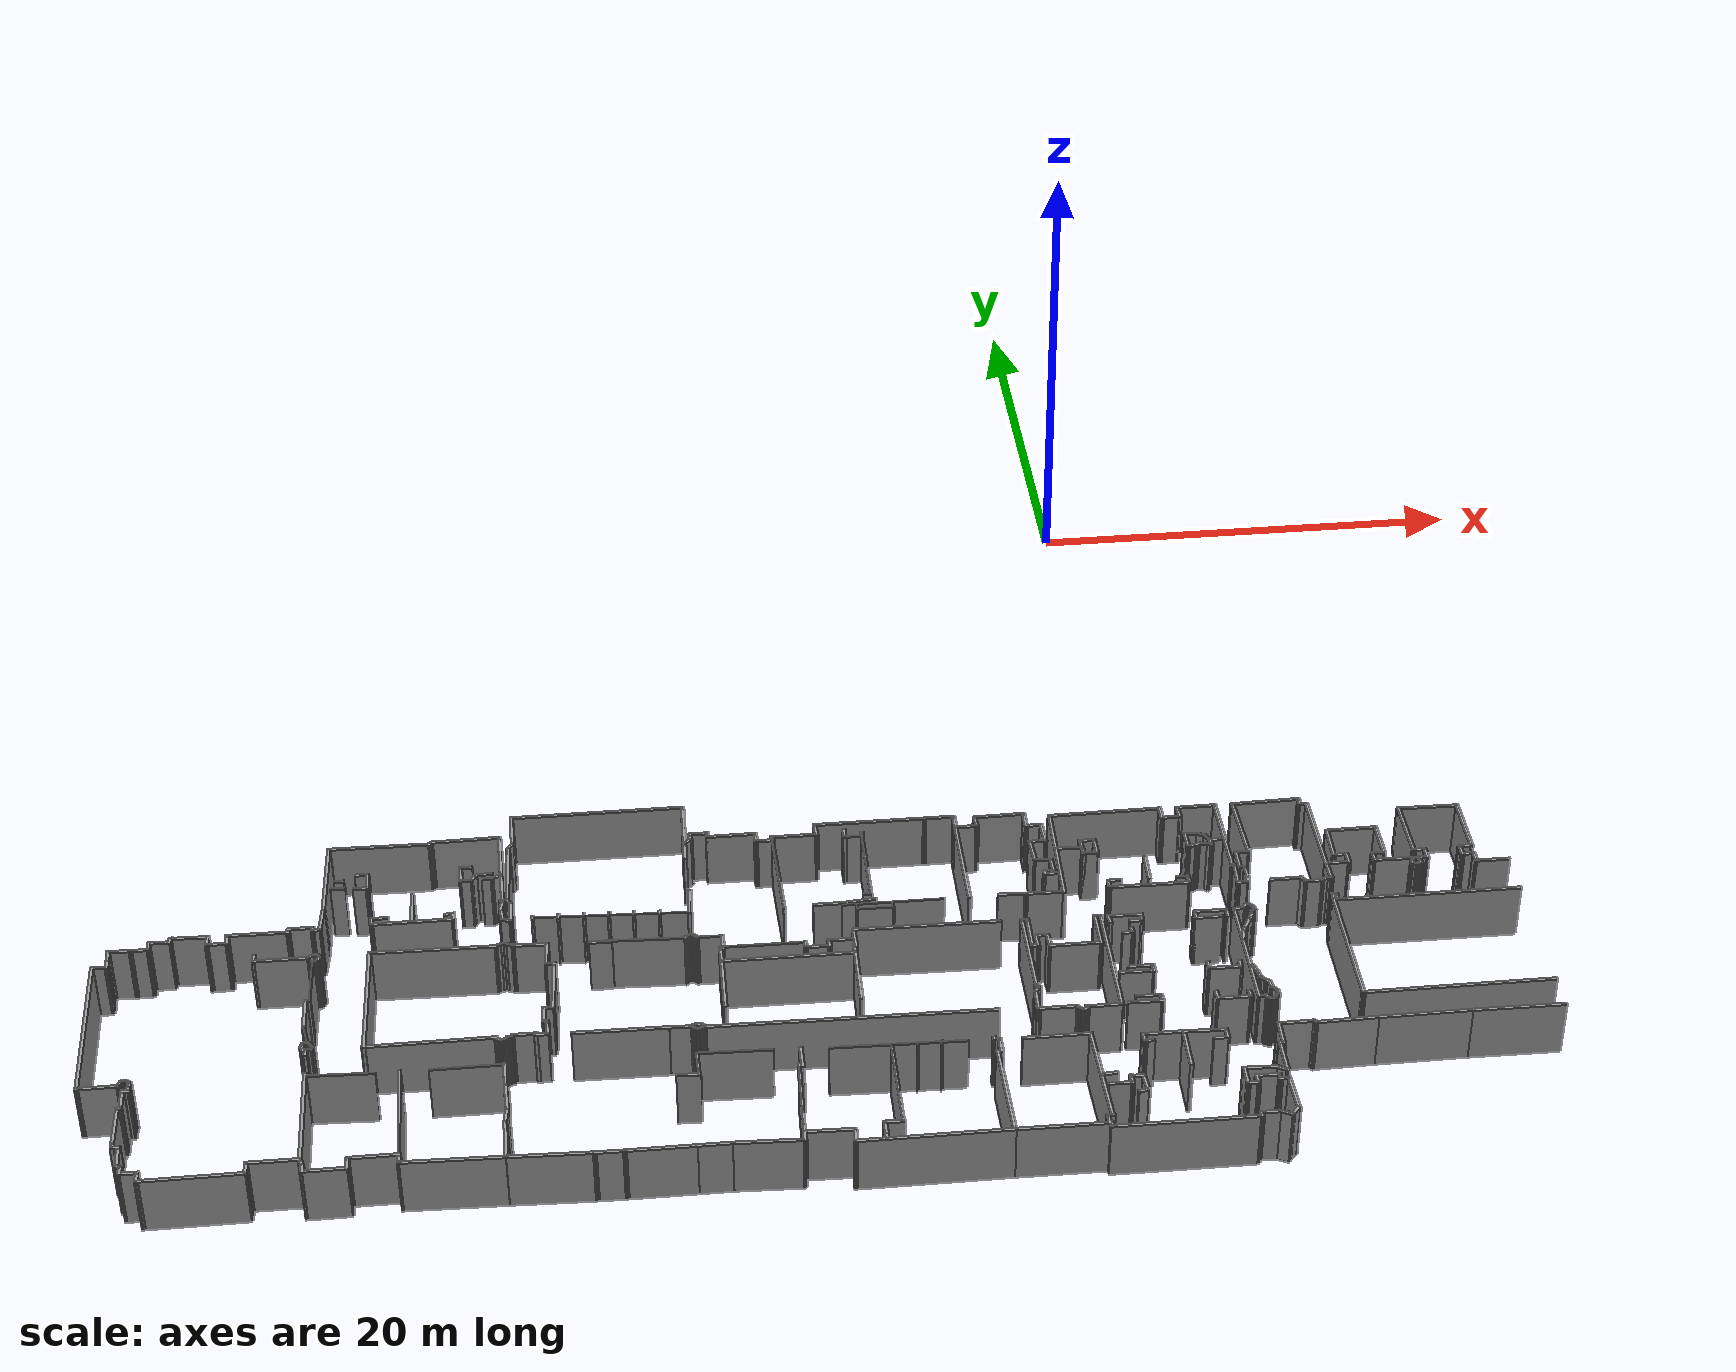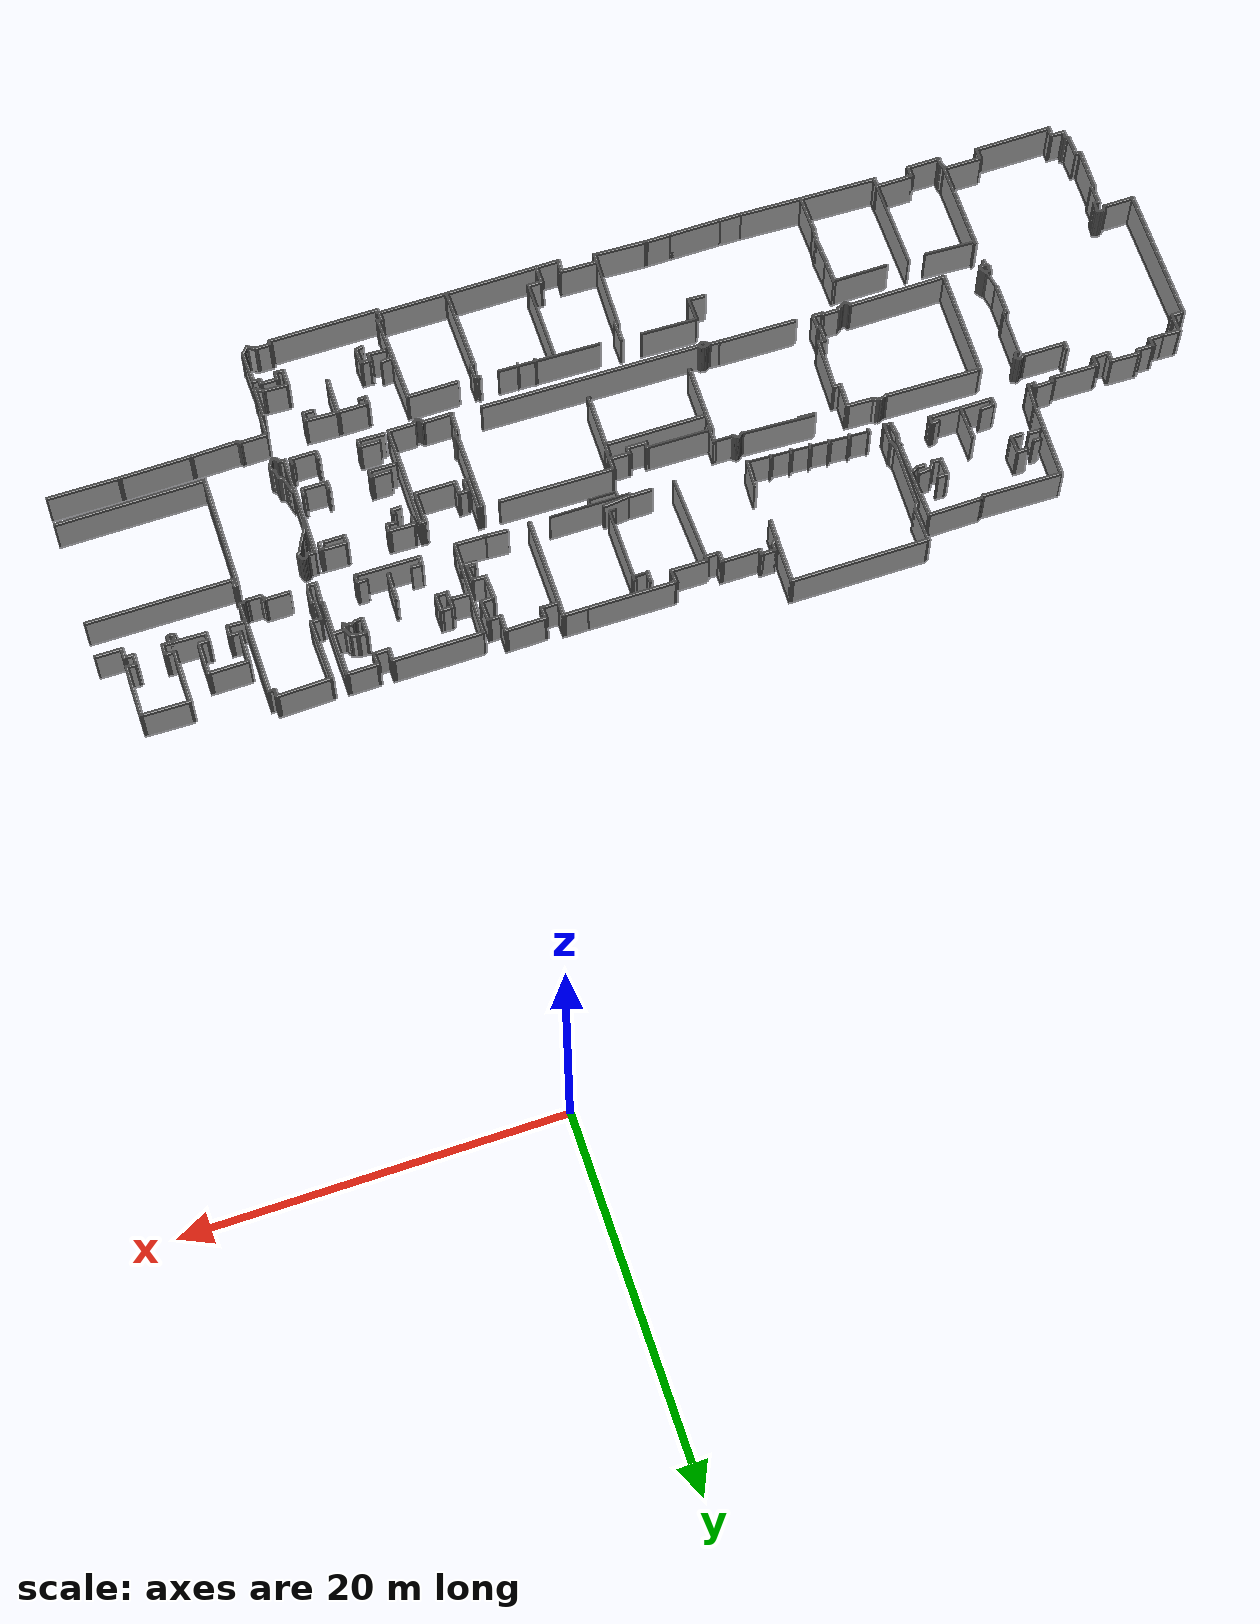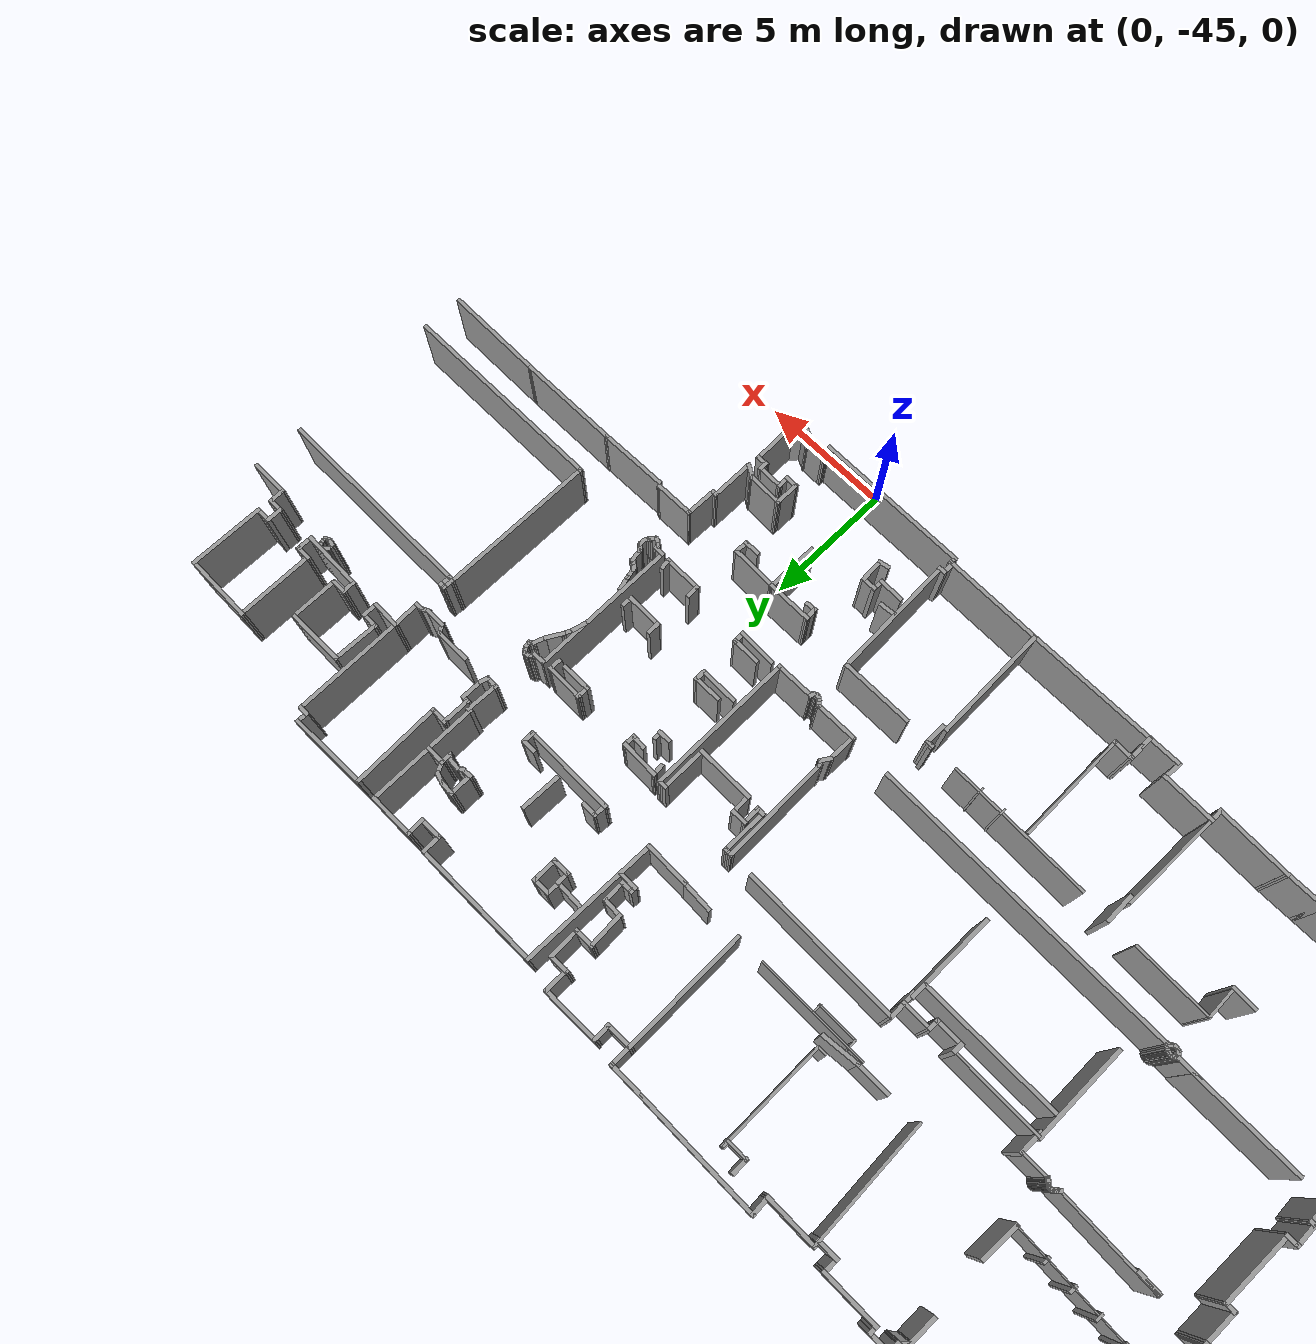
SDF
<?xml version='1.0'?>
<sdf version='1.4'>
  <model name='3_n'>
    <pose frame=''>-14.229 -33.4428 0 0 -0 0</pose>
    <link name='Wall_100'>
      <collision name='Wall_100_Collision'>
        <geometry>
          <box>
            <size>0.304128 0.15 2.5</size>
          </box>
        </geometry>
        <pose frame=''>0 0 1.25 0 -0 0</pose>
      </collision>
      <visual name='Wall_100_Visual'>
        <pose frame=''>0 0 1.25 0 -0 0</pose>
        <geometry>
          <box>
            <size>0.304128 0.15 2.5</size>
          </box>
        </geometry>
        <material>
          <script>
            <uri>file://media/materials/scripts/gazebo.material</uri>
            <name>Gazebo/Grey</name>
          </script>
          <ambient>1 1 1 1</ambient>
        </material>
        <meta>
          <layer>0</layer>
        </meta>
      </visual>
      <pose frame=''>19.2826 -5.64368 0 0 -0 -0.682317</pose>
    </link>
    <link name='Wall_101'>
      <collision name='Wall_101_Collision'>
        <geometry>
          <box>
            <size>2.685 0.15 2.5</size>
          </box>
        </geometry>
        <pose frame=''>0 0 1.25 0 -0 0</pose>
      </collision>
      <visual name='Wall_101_Visual'>
        <pose frame=''>0 0 1.25 0 -0 0</pose>
        <geometry>
          <box>
            <size>2.685 0.15 2.5</size>
          </box>
        </geometry>
        <material>
          <script>
            <uri>file://media/materials/scripts/gazebo.material</uri>
            <name>Gazebo/Grey</name>
          </script>
          <ambient>1 1 1 1</ambient>
        </material>
        <meta>
          <layer>0</layer>
        </meta>
      </visual>
      <pose frame=''>20.6096 -5.66611 0 0 -0 0.020646</pose>
    </link>
    <link name='Wall_103'>
      <collision name='Wall_103_Collision'>
        <geometry>
          <box>
            <size>3.99219 0.15 2.5</size>
          </box>
        </geometry>
        <pose frame=''>0 0 1.25 0 -0 0</pose>
      </collision>
      <visual name='Wall_103_Visual'>
        <pose frame=''>0 0 1.25 0 -0 0</pose>
        <geometry>
          <box>
            <size>3.99219 0.15 2.5</size>
          </box>
        </geometry>
        <material>
          <script>
            <uri>file://media/materials/scripts/gazebo.material</uri>
            <name>Gazebo/Grey</name>
          </script>
          <ambient>1 1 1 1</ambient>
        </material>
        <meta>
          <layer>0</layer>
        </meta>
      </visual>
      <pose frame=''>23.7979 -5.62656 0 0 -0 0.006965</pose>
    </link>
    <link name='Wall_104'>
      <collision name='Wall_104_Collision'>
        <geometry>
          <box>
            <size>3.92745 0.15 2.5</size>
          </box>
        </geometry>
        <pose frame=''>0 0 1.25 0 -0 0</pose>
      </collision>
      <visual name='Wall_104_Visual'>
        <pose frame=''>0 0 1.25 0 -0 0</pose>
        <geometry>
          <box>
            <size>3.92745 0.15 2.5</size>
          </box>
        </geometry>
        <material>
          <script>
            <uri>file://media/materials/scripts/gazebo.material</uri>
            <name>Gazebo/Grey</name>
          </script>
          <ambient>1 1 1 1</ambient>
        </material>
        <meta>
          <layer>0</layer>
        </meta>
      </visual>
      <pose frame=''>27.6074 -5.63295 0 0 -0 -0.010471</pose>
    </link>
    <link name='Wall_106'>
      <collision name='Wall_106_Collision'>
        <geometry>
          <box>
            <size>8.07969 0.15 2.5</size>
          </box>
        </geometry>
        <pose frame=''>0 0 1.25 0 -0 0</pose>
      </collision>
      <visual name='Wall_106_Visual'>
        <pose frame=''>0 0 1.25 0 -0 0</pose>
        <geometry>
          <box>
            <size>8.07969 0.15 2.5</size>
          </box>
        </geometry>
        <material>
          <script>
            <uri>file://media/materials/scripts/gazebo.material</uri>
            <name>Gazebo/Grey</name>
          </script>
          <ambient>1 1 1 1</ambient>
        </material>
        <meta>
          <layer>0</layer>
        </meta>
      </visual>
      <pose frame=''>25.5608 -4.09546 0 0 -0 -3.14035</pose>
    </link>
    <link name='Wall_109'>
      <collision name='Wall_109_Collision'>
        <geometry>
          <box>
            <size>6.07338 0.15 2.5</size>
          </box>
        </geometry>
        <pose frame=''>0 0 1.25 0 -0 0</pose>
      </collision>
      <visual name='Wall_109_Visual'>
        <pose frame=''>0 0 1.25 0 -0 0</pose>
        <geometry>
          <box>
            <size>6.07338 0.15 2.5</size>
          </box>
        </geometry>
        <material>
          <script>
            <uri>file://media/materials/scripts/gazebo.material</uri>
            <name>Gazebo/Grey</name>
          </script>
          <ambient>1 1 1 1</ambient>
        </material>
        <meta>
          <layer>0</layer>
        </meta>
      </visual>
      <pose frame=''>21.6246 -1.13886 0 0 -0 1.56113</pose>
    </link>
    <link name='Wall_11'>
      <collision name='Wall_11_Collision'>
        <geometry>
          <box>
            <size>7.37845 0.15 2.5</size>
          </box>
        </geometry>
        <pose frame=''>0 0 1.25 0 -0 0</pose>
      </collision>
      <visual name='Wall_11_Visual'>
        <pose frame=''>0 0 1.25 0 -0 0</pose>
        <geometry>
          <box>
            <size>7.37845 0.15 2.5</size>
          </box>
        </geometry>
        <material>
          <script>
            <uri>file://media/materials/scripts/gazebo.material</uri>
            <name>Gazebo/Grey</name>
          </script>
          <ambient>1 1 1 1</ambient>
        </material>
        <meta>
          <layer>0</layer>
        </meta>
      </visual>
      <pose frame=''>-29.5763 -0.911101 0 0 -0 -1.56883</pose>
    </link>
    <link name='Wall_111'>
      <collision name='Wall_111_Collision'>
        <geometry>
          <box>
            <size>0.471872 0.15 2.5</size>
          </box>
        </geometry>
        <pose frame=''>0 0 1.25 0 -0 0</pose>
      </collision>
      <visual name='Wall_111_Visual'>
        <pose frame=''>0 0 1.25 0 -0 0</pose>
        <geometry>
          <box>
            <size>0.471872 0.15 2.5</size>
          </box>
        </geometry>
        <material>
          <script>
            <uri>file://media/materials/scripts/gazebo.material</uri>
            <name>Gazebo/Grey</name>
          </script>
          <ambient>1 1 1 1</ambient>
        </material>
        <meta>
          <layer>0</layer>
        </meta>
      </visual>
      <pose frame=''>21.6685 1.9825 0 0 -0 1.47519</pose>
    </link>
    <link name='Wall_112'>
      <collision name='Wall_112_Collision'>
        <geometry>
          <box>
            <size>0.299526 0.15 2.5</size>
          </box>
        </geometry>
        <pose frame=''>0 0 1.25 0 -0 0</pose>
      </collision>
      <visual name='Wall_112_Visual'>
        <pose frame=''>0 0 1.25 0 -0 0</pose>
        <geometry>
          <box>
            <size>0.299526 0.15 2.5</size>
          </box>
        </geometry>
        <material>
          <script>
            <uri>file://media/materials/scripts/gazebo.material</uri>
            <name>Gazebo/Grey</name>
          </script>
          <ambient>1 1 1 1</ambient>
        </material>
        <meta>
          <layer>0</layer>
        </meta>
      </visual>
      <pose frame=''>21.7586 2.1423 0 0 -0 0</pose>
    </link>
    <link name='Wall_113'>
      <collision name='Wall_113_Collision'>
        <geometry>
          <box>
            <size>0.512541 0.15 2.5</size>
          </box>
        </geometry>
        <pose frame=''>0 0 1.25 0 -0 0</pose>
      </collision>
      <visual name='Wall_113_Visual'>
        <pose frame=''>0 0 1.25 0 -0 0</pose>
        <geometry>
          <box>
            <size>0.512541 0.15 2.5</size>
          </box>
        </geometry>
        <material>
          <script>
            <uri>file://media/materials/scripts/gazebo.material</uri>
            <name>Gazebo/Grey</name>
          </script>
          <ambient>1 1 1 1</ambient>
        </material>
        <meta>
          <layer>0</layer>
        </meta>
      </visual>
      <pose frame=''>21.8197 1.96154 0 0 -0 -1.64603</pose>
    </link>
    <link name='Wall_114'>
      <collision name='Wall_114_Collision'>
        <geometry>
          <box>
            <size>7.89707 0.15 2.5</size>
          </box>
        </geometry>
        <pose frame=''>0 0 1.25 0 -0 0</pose>
      </collision>
      <visual name='Wall_114_Visual'>
        <pose frame=''>0 0 1.25 0 -0 0</pose>
        <geometry>
          <box>
            <size>7.89707 0.15 2.5</size>
          </box>
        </geometry>
        <material>
          <script>
            <uri>file://media/materials/scripts/gazebo.material</uri>
            <name>Gazebo/Grey</name>
          </script>
          <ambient>1 1 1 1</ambient>
        </material>
        <meta>
          <layer>0</layer>
        </meta>
      </visual>
      <pose frame=''>25.6895 1.75849 0 0 -0 -0.003204</pose>
    </link>
    <link name='Wall_117'>
      <collision name='Wall_117_Collision'>
        <geometry>
          <box>
            <size>1.51449 0.15 2.5</size>
          </box>
        </geometry>
        <pose frame=''>0 0 1.25 0 -0 0</pose>
      </collision>
      <visual name='Wall_117_Visual'>
        <pose frame=''>0 0 1.25 0 -0 0</pose>
        <geometry>
          <box>
            <size>1.51449 0.15 2.5</size>
          </box>
        </geometry>
        <material>
          <script>
            <uri>file://media/materials/scripts/gazebo.material</uri>
            <name>Gazebo/Grey</name>
          </script>
          <ambient>1 1 1 1</ambient>
        </material>
        <meta>
          <layer>0</layer>
        </meta>
      </visual>
      <pose frame=''>28.9005 3.68895 0 0 -0 3.13435</pose>
    </link>
    <link name='Wall_118'>
      <collision name='Wall_118_Collision'>
        <geometry>
          <box>
            <size>0.664144 0.15 2.5</size>
          </box>
        </geometry>
        <pose frame=''>0 0 1.25 0 -0 0</pose>
      </collision>
      <visual name='Wall_118_Visual'>
        <pose frame=''>0 0 1.25 0 -0 0</pose>
        <geometry>
          <box>
            <size>0.664144 0.15 2.5</size>
          </box>
        </geometry>
        <material>
          <script>
            <uri>file://media/materials/scripts/gazebo.material</uri>
            <name>Gazebo/Grey</name>
          </script>
          <ambient>1 1 1 1</ambient>
        </material>
        <meta>
          <layer>0</layer>
        </meta>
      </visual>
      <pose frame=''>28.2183 3.95097 0 0 -0 1.5708</pose>
    </link>
    <link name='Wall_120'>
      <collision name='Wall_120_Collision'>
        <geometry>
          <box>
            <size>0.634583 0.15 2.5</size>
          </box>
        </geometry>
        <pose frame=''>0 0 1.25 0 -0 0</pose>
      </collision>
      <visual name='Wall_120_Visual'>
        <pose frame=''>0 0 1.25 0 -0 0</pose>
        <geometry>
          <box>
            <size>0.634583 0.15 2.5</size>
          </box>
        </geometry>
        <material>
          <script>
            <uri>file://media/materials/scripts/gazebo.material</uri>
            <name>Gazebo/Grey</name>
          </script>
          <ambient>1 1 1 1</ambient>
        </material>
        <meta>
          <layer>0</layer>
        </meta>
      </visual>
      <pose frame=''>27.9761 4.2031 0 0 -0 -3.12119</pose>
    </link>
    <link name='Wall_121'>
      <collision name='Wall_121_Collision'>
        <geometry>
          <box>
            <size>0.694166 0.15 2.5</size>
          </box>
        </geometry>
        <pose frame=''>0 0 1.25 0 -0 0</pose>
      </collision>
      <visual name='Wall_121_Visual'>
        <pose frame=''>0 0 1.25 0 -0 0</pose>
        <geometry>
          <box>
            <size>0.694166 0.15 2.5</size>
          </box>
        </geometry>
        <material>
          <script>
            <uri>file://media/materials/scripts/gazebo.material</uri>
            <name>Gazebo/Grey</name>
          </script>
          <ambient>1 1 1 1</ambient>
        </material>
        <meta>
          <layer>0</layer>
        </meta>
      </visual>
      <pose frame=''>27.7388 4.47005 0 0 -0 1.55262</pose>
    </link>
    <link name='Wall_122'>
      <collision name='Wall_122_Collision'>
        <geometry>
          <box>
            <size>0.664999 0.15 2.5</size>
          </box>
        </geometry>
        <pose frame=''>0 0 1.25 0 -0 0</pose>
      </collision>
      <visual name='Wall_122_Visual'>
        <pose frame=''>0 0 1.25 0 -0 0</pose>
        <geometry>
          <box>
            <size>0.664999 0.15 2.5</size>
          </box>
        </geometry>
        <material>
          <script>
            <uri>file://media/materials/scripts/gazebo.material</uri>
            <name>Gazebo/Grey</name>
          </script>
          <ambient>1 1 1 1</ambient>
        </material>
        <meta>
          <layer>0</layer>
        </meta>
      </visual>
      <pose frame=''>28.0008 4.73701 0 0 -0 -0.019228</pose>
    </link>
    <link name='Wall_124'>
      <collision name='Wall_124_Collision'>
        <geometry>
          <box>
            <size>2.92899 0.15 2.5</size>
          </box>
        </geometry>
        <pose frame=''>0 0 1.25 0 -0 0</pose>
      </collision>
      <visual name='Wall_124_Visual'>
        <pose frame=''>0 0 1.25 0 -0 0</pose>
        <geometry>
          <box>
            <size>2.92899 0.15 2.5</size>
          </box>
        </geometry>
        <material>
          <script>
            <uri>file://media/materials/scripts/gazebo.material</uri>
            <name>Gazebo/Grey</name>
          </script>
          <ambient>1 1 1 1</ambient>
        </material>
        <meta>
          <layer>0</layer>
        </meta>
      </visual>
      <pose frame=''>28.2776 6.12125 0 0 -0 1.55656</pose>
    </link>
    <link name='Wall_125'>
      <collision name='Wall_125_Collision'>
        <geometry>
          <box>
            <size>2.70125 0.15 2.5</size>
          </box>
        </geometry>
        <pose frame=''>0 0 1.25 0 -0 0</pose>
      </collision>
      <visual name='Wall_125_Visual'>
        <pose frame=''>0 0 1.25 0 -0 0</pose>
        <geometry>
          <box>
            <size>2.70125 0.15 2.5</size>
          </box>
        </geometry>
        <material>
          <script>
            <uri>file://media/materials/scripts/gazebo.material</uri>
            <name>Gazebo/Grey</name>
          </script>
          <ambient>1 1 1 1</ambient>
        </material>
        <meta>
          <layer>0</layer>
        </meta>
      </visual>
      <pose frame=''>27.0219 7.53514 0 0 -0 3.12222</pose>
    </link>
    <link name='Wall_126'>
      <collision name='Wall_126_Collision'>
        <geometry>
          <box>
            <size>3.02725 0.15 2.5</size>
          </box>
        </geometry>
        <pose frame=''>0 0 1.25 0 -0 0</pose>
      </collision>
      <visual name='Wall_126_Visual'>
        <pose frame=''>0 0 1.25 0 -0 0</pose>
        <geometry>
          <box>
            <size>3.02725 0.15 2.5</size>
          </box>
        </geometry>
        <material>
          <script>
            <uri>file://media/materials/scripts/gazebo.material</uri>
            <name>Gazebo/Grey</name>
          </script>
          <ambient>1 1 1 1</ambient>
        </material>
        <meta>
          <layer>0</layer>
        </meta>
      </visual>
      <pose frame=''>25.7415 6.12125 0 0 -0 -1.57423</pose>
    </link>
    <link name='Wall_127'>
      <collision name='Wall_127_Collision'>
        <geometry>
          <box>
            <size>0.624595 0.15 2.5</size>
          </box>
        </geometry>
        <pose frame=''>0 0 1.25 0 -0 0</pose>
      </collision>
      <visual name='Wall_127_Visual'>
        <pose frame=''>0 0 1.25 0 -0 0</pose>
        <geometry>
          <box>
            <size>0.624595 0.15 2.5</size>
          </box>
        </geometry>
        <material>
          <script>
            <uri>file://media/materials/scripts/gazebo.material</uri>
            <name>Gazebo/Grey</name>
          </script>
          <ambient>1 1 1 1</ambient>
        </material>
        <meta>
          <layer>0</layer>
        </meta>
      </visual>
      <pose frame=''>25.9739 4.68263 0 0 -0 0</pose>
    </link>
    <link name='Wall_128'>
      <collision name='Wall_128_Collision'>
        <geometry>
          <box>
            <size>0.693896 0.15 2.5</size>
          </box>
        </geometry>
        <pose frame=''>0 0 1.25 0 -0 0</pose>
      </collision>
      <visual name='Wall_128_Visual'>
        <pose frame=''>0 0 1.25 0 -0 0</pose>
        <geometry>
          <box>
            <size>0.693896 0.15 2.5</size>
          </box>
        </geometry>
        <material>
          <script>
            <uri>file://media/materials/scripts/gazebo.material</uri>
            <name>Gazebo/Grey</name>
          </script>
          <ambient>1 1 1 1</ambient>
        </material>
        <meta>
          <layer>0</layer>
        </meta>
      </visual>
      <pose frame=''>26.2062 4.41073 0 0 -0 -1.58898</pose>
    </link>
    <link name='Wall_129'>
      <collision name='Wall_129_Collision'>
        <geometry>
          <box>
            <size>2.39522 0.15 2.5</size>
          </box>
        </geometry>
        <pose frame=''>0 0 1.25 0 -0 0</pose>
      </collision>
      <visual name='Wall_129_Visual'>
        <pose frame=''>0 0 1.25 0 -0 0</pose>
        <geometry>
          <box>
            <size>2.39522 0.15 2.5</size>
          </box>
        </geometry>
        <material>
          <script>
            <uri>file://media/materials/scripts/gazebo.material</uri>
            <name>Gazebo/Grey</name>
          </script>
          <ambient>1 1 1 1</ambient>
        </material>
        <meta>
          <layer>0</layer>
        </meta>
      </visual>
      <pose frame=''>25.0791 4.16849 0 0 -0 3.11517</pose>
    </link>
    <link name='Wall_13'>
      <collision name='Wall_13_Collision'>
        <geometry>
          <box>
            <size>1.71274 0.15 2.5</size>
          </box>
        </geometry>
        <pose frame=''>0 0 1.25 0 -0 0</pose>
      </collision>
      <visual name='Wall_13_Visual'>
        <pose frame=''>0 0 1.25 0 -0 0</pose>
        <geometry>
          <box>
            <size>1.71274 0.15 2.5</size>
          </box>
        </geometry>
        <material>
          <script>
            <uri>file://media/materials/scripts/gazebo.material</uri>
            <name>Gazebo/Grey</name>
          </script>
          <ambient>1 1 1 1</ambient>
        </material>
        <meta>
          <layer>0</layer>
        </meta>
      </visual>
      <pose frame=''>-28.7878 -4.5197 0 0 -0 0.007194</pose>
    </link>
    <link name='Wall_130'>
      <collision name='Wall_130_Collision'>
        <geometry>
          <box>
            <size>0.585045 0.15 2.5</size>
          </box>
        </geometry>
        <pose frame=''>0 0 1.25 0 -0 0</pose>
      </collision>
      <visual name='Wall_130_Visual'>
        <pose frame=''>0 0 1.25 0 -0 0</pose>
        <geometry>
          <box>
            <size>0.585045 0.15 2.5</size>
          </box>
        </geometry>
        <material>
          <script>
            <uri>file://media/materials/scripts/gazebo.material</uri>
            <name>Gazebo/Grey</name>
          </script>
          <ambient>1 1 1 1</ambient>
        </material>
        <meta>
          <layer>0</layer>
        </meta>
      </visual>
      <pose frame=''>23.9519 4.41567 0 0 -0 1.59352</pose>
    </link>
    <link name='Wall_131'>
      <collision name='Wall_131_Collision'>
        <geometry>
          <box>
            <size>0.644765 0.15 2.5</size>
          </box>
        </geometry>
        <pose frame=''>0 0 1.25 0 -0 0</pose>
      </collision>
      <visual name='Wall_131_Visual'>
        <pose frame=''>0 0 1.25 0 -0 0</pose>
        <geometry>
          <box>
            <size>0.644765 0.15 2.5</size>
          </box>
        </geometry>
        <material>
          <script>
            <uri>file://media/materials/scripts/gazebo.material</uri>
            <name>Gazebo/Grey</name>
          </script>
          <ambient>1 1 1 1</ambient>
        </material>
        <meta>
          <layer>0</layer>
        </meta>
      </visual>
      <pose frame=''>24.1941 4.62825 0 0 -0 -0.019997</pose>
    </link>
    <link name='Wall_132'>
      <collision name='Wall_132_Collision'>
        <geometry>
          <box>
            <size>1.9001 0.15 2.5</size>
          </box>
        </geometry>
        <pose frame=''>0 0 1.25 0 -0 0</pose>
      </collision>
      <visual name='Wall_132_Visual'>
        <pose frame=''>0 0 1.25 0 -0 0</pose>
        <geometry>
          <box>
            <size>1.9001 0.15 2.5</size>
          </box>
        </geometry>
        <material>
          <script>
            <uri>file://media/materials/scripts/gazebo.material</uri>
            <name>Gazebo/Grey</name>
          </script>
          <ambient>1 1 1 1</ambient>
        </material>
        <meta>
          <layer>0</layer>
        </meta>
      </visual>
      <pose frame=''>24.4463 5.49834 0 0 -0 1.56515</pose>
    </link>
    <link name='Wall_133'>
      <collision name='Wall_133_Collision'>
        <geometry>
          <box>
            <size>2.26592 0.15 2.5</size>
          </box>
        </geometry>
        <pose frame=''>0 0 1.25 0 -0 0</pose>
      </collision>
      <visual name='Wall_133_Visual'>
        <pose frame=''>0 0 1.25 0 -0 0</pose>
        <geometry>
          <box>
            <size>2.26592 0.15 2.5</size>
          </box>
        </geometry>
        <material>
          <script>
            <uri>file://media/materials/scripts/gazebo.material</uri>
            <name>Gazebo/Grey</name>
          </script>
          <ambient>1 1 1 1</ambient>
        </material>
        <meta>
          <layer>0</layer>
        </meta>
      </visual>
      <pose frame=''>23.3933 6.36843 0 0 -0 -3.13692</pose>
    </link>
    <link name='Wall_134'>
      <collision name='Wall_134_Collision'>
        <geometry>
          <box>
            <size>1.81214 0.15 2.5</size>
          </box>
        </geometry>
        <pose frame=''>0 0 1.25 0 -0 0</pose>
      </collision>
      <visual name='Wall_134_Visual'>
        <pose frame=''>0 0 1.25 0 -0 0</pose>
        <geometry>
          <box>
            <size>1.81214 0.15 2.5</size>
          </box>
        </geometry>
        <material>
          <script>
            <uri>file://media/materials/scripts/gazebo.material</uri>
            <name>Gazebo/Grey</name>
          </script>
          <ambient>1 1 1 1</ambient>
        </material>
        <meta>
          <layer>0</layer>
        </meta>
      </visual>
      <pose frame=''>22.3057 5.53295 0 0 -0 -1.6065</pose>
    </link>
    <link name='Wall_135'>
      <collision name='Wall_135_Collision'>
        <geometry>
          <box>
            <size>0.703782 0.15 2.5</size>
          </box>
        </geometry>
        <pose frame=''>0 0 1.25 0 -0 0</pose>
      </collision>
      <visual name='Wall_135_Visual'>
        <pose frame=''>0 0 1.25 0 -0 0</pose>
        <geometry>
          <box>
            <size>0.703782 0.15 2.5</size>
          </box>
        </geometry>
        <material>
          <script>
            <uri>file://media/materials/scripts/gazebo.material</uri>
            <name>Gazebo/Grey</name>
          </script>
          <ambient>1 1 1 1</ambient>
        </material>
        <meta>
          <layer>0</layer>
        </meta>
      </visual>
      <pose frame=''>22.5528 4.69747 0 0 -0 -0.017855</pose>
    </link>
    <link name='Wall_136'>
      <collision name='Wall_136_Collision'>
        <geometry>
          <box>
            <size>0.674125 0.15 2.5</size>
          </box>
        </geometry>
        <pose frame=''>0 0 1.25 0 -0 0</pose>
      </collision>
      <visual name='Wall_136_Visual'>
        <pose frame=''>0 0 1.25 0 -0 0</pose>
        <geometry>
          <box>
            <size>0.674125 0.15 2.5</size>
          </box>
        </geometry>
        <material>
          <script>
            <uri>file://media/materials/scripts/gazebo.material</uri>
            <name>Gazebo/Grey</name>
          </script>
          <ambient>1 1 1 1</ambient>
        </material>
        <meta>
          <layer>0</layer>
        </meta>
      </visual>
      <pose frame=''>22.8247 4.43051 0 0 -0 -1.58966</pose>
    </link>
    <link name='Wall_138'>
      <collision name='Wall_138_Collision'>
        <geometry>
          <box>
            <size>1.1293 0.15 2.5</size>
          </box>
        </geometry>
        <pose frame=''>0 0 1.25 0 -0 0</pose>
      </collision>
      <visual name='Wall_138_Visual'>
        <pose frame=''>0 0 1.25 0 -0 0</pose>
        <geometry>
          <box>
            <size>1.1293 0.15 2.5</size>
          </box>
        </geometry>
        <material>
          <script>
            <uri>file://media/materials/scripts/gazebo.material</uri>
            <name>Gazebo/Grey</name>
          </script>
          <ambient>1 1 1 1</ambient>
        </material>
        <meta>
          <layer>0</layer>
        </meta>
      </visual>
      <pose frame=''>22.3304 4.18332 0 0 -0 3.1113</pose>
    </link>
    <link name='Wall_14'>
      <collision name='Wall_14_Collision'>
        <geometry>
          <box>
            <size>0.263821 0.15 2.5</size>
          </box>
        </geometry>
        <pose frame=''>0 0 1.25 0 -0 0</pose>
      </collision>
      <visual name='Wall_14_Visual'>
        <pose frame=''>0 0 1.25 0 -0 0</pose>
        <geometry>
          <box>
            <size>0.263821 0.15 2.5</size>
          </box>
        </geometry>
        <material>
          <script>
            <uri>file://media/materials/scripts/gazebo.material</uri>
            <name>Gazebo/Grey</name>
          </script>
          <ambient>1 1 1 1</ambient>
        </material>
        <meta>
          <layer>0</layer>
        </meta>
      </visual>
      <pose frame=''>-27.9755 -4.4663 0 0 -0 0.996491</pose>
    </link>
    <link name='Wall_140'>
      <collision name='Wall_140_Collision'>
        <geometry>
          <box>
            <size>0.34576 0.15 2.5</size>
          </box>
        </geometry>
        <pose frame=''>0 0 1.25 0 -0 0</pose>
      </collision>
      <visual name='Wall_140_Visual'>
        <pose frame=''>0 0 1.25 0 -0 0</pose>
        <geometry>
          <box>
            <size>0.34576 0.15 2.5</size>
          </box>
        </geometry>
        <material>
          <script>
            <uri>file://media/materials/scripts/gazebo.material</uri>
            <name>Gazebo/Grey</name>
          </script>
          <ambient>1 1 1 1</ambient>
        </material>
        <meta>
          <layer>0</layer>
        </meta>
      </visual>
      <pose frame=''>25.5685 4.03006 0 0 -0 -2.35619</pose>
    </link>
    <link name='Wall_141'>
      <collision name='Wall_141_Collision'>
        <geometry>
          <box>
            <size>0.308198 0.15 2.5</size>
          </box>
        </geometry>
        <pose frame=''>0 0 1.25 0 -0 0</pose>
      </collision>
      <visual name='Wall_141_Visual'>
        <pose frame=''>0 0 1.25 0 -0 0</pose>
        <geometry>
          <box>
            <size>0.308198 0.15 2.5</size>
          </box>
        </geometry>
        <material>
          <script>
            <uri>file://media/materials/scripts/gazebo.material</uri>
            <name>Gazebo/Grey</name>
          </script>
          <ambient>1 1 1 1</ambient>
        </material>
        <meta>
          <layer>0</layer>
        </meta>
      </visual>
      <pose frame=''>25.4993 3.88176 0 0 -0 -1.5708</pose>
    </link>
    <link name='Wall_142'>
      <collision name='Wall_142_Collision'>
        <geometry>
          <box>
            <size>0.318956 0.15 2.5</size>
          </box>
        </geometry>
        <pose frame=''>0 0 1.25 0 -0 0</pose>
      </collision>
      <visual name='Wall_142_Visual'>
        <pose frame=''>0 0 1.25 0 -0 0</pose>
        <geometry>
          <box>
            <size>0.318956 0.15 2.5</size>
          </box>
        </geometry>
        <material>
          <script>
            <uri>file://media/materials/scripts/gazebo.material</uri>
            <name>Gazebo/Grey</name>
          </script>
          <ambient>1 1 1 1</ambient>
        </material>
        <meta>
          <layer>0</layer>
        </meta>
      </visual>
      <pose frame=''>25.5784 3.77299 0 0 -0 -0.358771</pose>
    </link>
    <link name='Wall_143'>
      <collision name='Wall_143_Collision'>
        <geometry>
          <box>
            <size>0.239534 0.15 2.5</size>
          </box>
        </geometry>
        <pose frame=''>0 0 1.25 0 -0 0</pose>
      </collision>
      <visual name='Wall_143_Visual'>
        <pose frame=''>0 0 1.25 0 -0 0</pose>
        <geometry>
          <box>
            <size>0.239534 0.15 2.5</size>
          </box>
        </geometry>
        <material>
          <script>
            <uri>file://media/materials/scripts/gazebo.material</uri>
            <name>Gazebo/Grey</name>
          </script>
          <ambient>1 1 1 1</ambient>
        </material>
        <meta>
          <layer>0</layer>
        </meta>
      </visual>
      <pose frame=''>25.702 3.74828 0 0 -0 0.110657</pose>
    </link>
    <link name='Wall_144'>
      <collision name='Wall_144_Collision'>
        <geometry>
          <box>
            <size>0.260544 0.15 2.5</size>
          </box>
        </geometry>
        <pose frame=''>0 0 1.25 0 -0 0</pose>
      </collision>
      <visual name='Wall_144_Visual'>
        <pose frame=''>0 0 1.25 0 -0 0</pose>
        <geometry>
          <box>
            <size>0.260544 0.15 2.5</size>
          </box>
        </geometry>
        <material>
          <script>
            <uri>file://media/materials/scripts/gazebo.material</uri>
            <name>Gazebo/Grey</name>
          </script>
          <ambient>1 1 1 1</ambient>
        </material>
        <meta>
          <layer>0</layer>
        </meta>
      </visual>
      <pose frame=''>25.7959 3.77794 0 0 -0 0.463648</pose>
    </link>
    <link name='Wall_145'>
      <collision name='Wall_145_Collision'>
        <geometry>
          <box>
            <size>0.258761 0.15 2.5</size>
          </box>
        </geometry>
        <pose frame=''>0 0 1.25 0 -0 0</pose>
      </collision>
      <visual name='Wall_145_Visual'>
        <pose frame=''>0 0 1.25 0 -0 0</pose>
        <geometry>
          <box>
            <size>0.258761 0.15 2.5</size>
          </box>
        </geometry>
        <material>
          <script>
            <uri>file://media/materials/scripts/gazebo.material</uri>
            <name>Gazebo/Grey</name>
          </script>
          <ambient>1 1 1 1</ambient>
        </material>
        <meta>
          <layer>0</layer>
        </meta>
      </visual>
      <pose frame=''>25.8404 3.85704 0 0 -0 1.66146</pose>
    </link>
    <link name='Wall_146'>
      <collision name='Wall_146_Collision'>
        <geometry>
          <box>
            <size>0.315743 0.15 2.5</size>
          </box>
        </geometry>
        <pose frame=''>0 0 1.25 0 -0 0</pose>
      </collision>
      <visual name='Wall_146_Visual'>
        <pose frame=''>0 0 1.25 0 -0 0</pose>
        <geometry>
          <box>
            <size>0.315743 0.15 2.5</size>
          </box>
        </geometry>
        <material>
          <script>
            <uri>file://media/materials/scripts/gazebo.material</uri>
            <name>Gazebo/Grey</name>
          </script>
          <ambient>1 1 1 1</ambient>
        </material>
        <meta>
          <layer>0</layer>
        </meta>
      </visual>
      <pose frame=''>25.8107 3.99052 0 0 -0 1.87368</pose>
    </link>
    <link name='Wall_147'>
      <collision name='Wall_147_Collision'>
        <geometry>
          <box>
            <size>0.221299 0.15 2.5</size>
          </box>
        </geometry>
        <pose frame=''>0 0 1.25 0 -0 0</pose>
      </collision>
      <visual name='Wall_147_Visual'>
        <pose frame=''>0 0 1.25 0 -0 0</pose>
        <geometry>
          <box>
            <size>0.221299 0.15 2.5</size>
          </box>
        </geometry>
        <material>
          <script>
            <uri>file://media/materials/scripts/gazebo.material</uri>
            <name>Gazebo/Grey</name>
          </script>
          <ambient>1 1 1 1</ambient>
        </material>
        <meta>
          <layer>0</layer>
        </meta>
      </visual>
      <pose frame=''>25.7662 4.09928 0 0 -0 2.1588</pose>
    </link>
    <link name='Wall_149'>
      <collision name='Wall_149_Collision'>
        <geometry>
          <box>
            <size>4.24333 0.15 2.5</size>
          </box>
        </geometry>
        <pose frame=''>0 0 1.25 0 -0 0</pose>
      </collision>
      <visual name='Wall_149_Visual'>
        <pose frame=''>0 0 1.25 0 -0 0</pose>
        <geometry>
          <box>
            <size>4.24333 0.15 2.5</size>
          </box>
        </geometry>
        <material>
          <script>
            <uri>file://media/materials/scripts/gazebo.material</uri>
            <name>Gazebo/Grey</name>
          </script>
          <ambient>1 1 1 1</ambient>
        </material>
        <meta>
          <layer>0</layer>
        </meta>
      </visual>
      <pose frame=''>21.8441 6.24482 0 0 -0 1.56927</pose>
    </link>
    <link name='Wall_15'>
      <collision name='Wall_15_Collision'>
        <geometry>
          <box>
            <size>0.253192 0.15 2.5</size>
          </box>
        </geometry>
        <pose frame=''>0 0 1.25 0 -0 0</pose>
      </collision>
      <visual name='Wall_15_Visual'>
        <pose frame=''>0 0 1.25 0 -0 0</pose>
        <geometry>
          <box>
            <size>0.253192 0.15 2.5</size>
          </box>
        </geometry>
        <material>
          <script>
            <uri>file://media/materials/scripts/gazebo.material</uri>
            <name>Gazebo/Grey</name>
          </script>
          <ambient>1 1 1 1</ambient>
        </material>
        <meta>
          <layer>0</layer>
        </meta>
      </visual>
      <pose frame=''>-27.9193 -4.37355 0 0 -0 1.05841</pose>
    </link>
    <link name='Wall_150'>
      <collision name='Wall_150_Collision'>
        <geometry>
          <box>
            <size>0.445633 0.15 2.5</size>
          </box>
        </geometry>
        <pose frame=''>0 0 1.25 0 -0 0</pose>
      </collision>
      <visual name='Wall_150_Visual'>
        <pose frame=''>0 0 1.25 0 -0 0</pose>
        <geometry>
          <box>
            <size>0.445633 0.15 2.5</size>
          </box>
        </geometry>
        <material>
          <script>
            <uri>file://media/materials/scripts/gazebo.material</uri>
            <name>Gazebo/Grey</name>
          </script>
          <ambient>1 1 1 1</ambient>
        </material>
        <meta>
          <layer>0</layer>
        </meta>
      </visual>
      <pose frame=''>21.6994 8.29717 0 0 -0 3.10315</pose>
    </link>
    <link name='Wall_152'>
      <collision name='Wall_152_Collision'>
        <geometry>
          <box>
            <size>0.514034 0.15 2.5</size>
          </box>
        </geometry>
        <pose frame=''>0 0 1.25 0 -0 0</pose>
      </collision>
      <visual name='Wall_152_Visual'>
        <pose frame=''>0 0 1.25 0 -0 0</pose>
        <geometry>
          <box>
            <size>0.514034 0.15 2.5</size>
          </box>
        </geometry>
        <material>
          <script>
            <uri>file://media/materials/scripts/gazebo.material</uri>
            <name>Gazebo/Grey</name>
          </script>
          <ambient>1 1 1 1</ambient>
        </material>
        <meta>
          <layer>0</layer>
        </meta>
      </visual>
      <pose frame=''>21.5572 8.48478 0 0 -0 1.53956</pose>
    </link>
    <link name='Wall_153'>
      <collision name='Wall_153_Collision'>
        <geometry>
          <box>
            <size>3.06165 0.15 2.5</size>
          </box>
        </geometry>
        <pose frame=''>0 0 1.25 0 -0 0</pose>
      </collision>
      <visual name='Wall_153_Visual'>
        <pose frame=''>0 0 1.25 0 -0 0</pose>
        <geometry>
          <box>
            <size>3.06165 0.15 2.5</size>
          </box>
        </geometry>
        <material>
          <script>
            <uri>file://media/materials/scripts/gazebo.material</uri>
            <name>Gazebo/Grey</name>
          </script>
          <ambient>1 1 1 1</ambient>
        </material>
        <meta>
          <layer>0</layer>
        </meta>
      </visual>
      <pose frame=''>20.1075 8.6326 0 0 -0 -3.11816</pose>
    </link>
    <link name='Wall_154'>
      <collision name='Wall_154_Collision'>
        <geometry>
          <box>
            <size>3.47114 0.15 2.5</size>
          </box>
        </geometry>
        <pose frame=''>0 0 1.25 0 -0 0</pose>
      </collision>
      <visual name='Wall_154_Visual'>
        <pose frame=''>0 0 1.25 0 -0 0</pose>
        <geometry>
          <box>
            <size>3.47114 0.15 2.5</size>
          </box>
        </geometry>
        <material>
          <script>
            <uri>file://media/materials/scripts/gazebo.material</uri>
            <name>Gazebo/Grey</name>
          </script>
          <ambient>1 1 1 1</ambient>
        </material>
        <meta>
          <layer>0</layer>
        </meta>
      </visual>
      <pose frame=''>18.6919 6.93839 0 0 -0 -1.54683</pose>
    </link>
    <link name='Wall_155'>
      <collision name='Wall_155_Collision'>
        <geometry>
          <box>
            <size>0.707618 0.15 2.5</size>
          </box>
        </geometry>
        <pose frame=''>0 0 1.25 0 -0 0</pose>
      </collision>
      <visual name='Wall_155_Visual'>
        <pose frame=''>0 0 1.25 0 -0 0</pose>
        <geometry>
          <box>
            <size>0.707618 0.15 2.5</size>
          </box>
        </geometry>
        <material>
          <script>
            <uri>file://media/materials/scripts/gazebo.material</uri>
            <name>Gazebo/Grey</name>
          </script>
          <ambient>1 1 1 1</ambient>
        </material>
        <meta>
          <layer>0</layer>
        </meta>
      </visual>
      <pose frame=''>18.4531 5.28398 0 0 -0 3.12119</pose>
    </link>
    <link name='Wall_157'>
      <collision name='Wall_157_Collision'>
        <geometry>
          <box>
            <size>1.15067 0.15 2.5</size>
          </box>
        </geometry>
        <pose frame=''>0 0 1.25 0 -0 0</pose>
      </collision>
      <visual name='Wall_157_Visual'>
        <pose frame=''>0 0 1.25 0 -0 0</pose>
        <geometry>
          <box>
            <size>1.15067 0.15 2.5</size>
          </box>
        </geometry>
        <material>
          <script>
            <uri>file://media/materials/scripts/gazebo.material</uri>
            <name>Gazebo/Grey</name>
          </script>
          <ambient>1 1 1 1</ambient>
        </material>
        <meta>
          <layer>0</layer>
        </meta>
      </visual>
      <pose frame=''>18.1688 4.78937 0 0 -0 -1.58216</pose>
    </link>
    <link name='Wall_158'>
      <collision name='Wall_158_Collision'>
        <geometry>
          <box>
            <size>0.354669 0.15 2.5</size>
          </box>
        </geometry>
        <pose frame=''>0 0 1.25 0 -0 0</pose>
      </collision>
      <visual name='Wall_158_Visual'>
        <pose frame=''>0 0 1.25 0 -0 0</pose>
        <geometry>
          <box>
            <size>0.354669 0.15 2.5</size>
          </box>
        </geometry>
        <material>
          <script>
            <uri>file://media/materials/scripts/gazebo.material</uri>
            <name>Gazebo/Grey</name>
          </script>
          <ambient>1 1 1 1</ambient>
        </material>
        <meta>
          <layer>0</layer>
        </meta>
      </visual>
      <pose frame=''>18.2655 4.28338 0 0 -0 -0.055499</pose>
    </link>
    <link name='Wall_159'>
      <collision name='Wall_159_Collision'>
        <geometry>
          <box>
            <size>0.88917 0.15 2.5</size>
          </box>
        </geometry>
        <pose frame=''>0 0 1.25 0 -0 0</pose>
      </collision>
      <visual name='Wall_159_Visual'>
        <pose frame=''>0 0 1.25 0 -0 0</pose>
        <geometry>
          <box>
            <size>0.88917 0.15 2.5</size>
          </box>
        </geometry>
        <material>
          <script>
            <uri>file://media/materials/scripts/gazebo.material</uri>
            <name>Gazebo/Grey</name>
          </script>
          <ambient>1 1 1 1</ambient>
        </material>
        <meta>
          <layer>0</layer>
        </meta>
      </visual>
      <pose frame=''>18.3621 3.90815 0 0 -0 -1.58618</pose>
    </link>
    <link name='Wall_16'>
      <collision name='Wall_16_Collision'>
        <geometry>
          <box>
            <size>0.210803 0.15 2.5</size>
          </box>
        </geometry>
        <pose frame=''>0 0 1.25 0 -0 0</pose>
      </collision>
      <visual name='Wall_16_Visual'>
        <pose frame=''>0 0 1.25 0 -0 0</pose>
        <geometry>
          <box>
            <size>0.210803 0.15 2.5</size>
          </box>
        </geometry>
        <material>
          <script>
            <uri>file://media/materials/scripts/gazebo.material</uri>
            <name>Gazebo/Grey</name>
          </script>
          <ambient>1 1 1 1</ambient>
        </material>
        <meta>
          <layer>0</layer>
        </meta>
      </visual>
      <pose frame=''>-27.8772 -4.30328 0 0 -0 0.982794</pose>
    </link>
    <link name='Wall_160'>
      <collision name='Wall_160_Collision'>
        <geometry>
          <box>
            <size>0.412508 0.15 2.5</size>
          </box>
        </geometry>
        <pose frame=''>0 0 1.25 0 -0 0</pose>
      </collision>
      <visual name='Wall_160_Visual'>
        <pose frame=''>0 0 1.25 0 -0 0</pose>
        <geometry>
          <box>
            <size>0.412508 0.15 2.5</size>
          </box>
        </geometry>
        <material>
          <script>
            <uri>file://media/materials/scripts/gazebo.material</uri>
            <name>Gazebo/Grey</name>
          </script>
          <ambient>1 1 1 1</ambient>
        </material>
        <meta>
          <layer>0</layer>
        </meta>
      </visual>
      <pose frame=''>18.3166 3.41354 0 0 -0 -1.87885</pose>
    </link>
    <link name='Wall_161'>
      <collision name='Wall_161_Collision'>
        <geometry>
          <box>
            <size>0.536764 0.15 2.5</size>
          </box>
        </geometry>
        <pose frame=''>0 0 1.25 0 -0 0</pose>
      </collision>
      <visual name='Wall_161_Visual'>
        <pose frame=''>0 0 1.25 0 -0 0</pose>
        <geometry>
          <box>
            <size>0.536764 0.15 2.5</size>
          </box>
        </geometry>
        <material>
          <script>
            <uri>file://media/materials/scripts/gazebo.material</uri>
            <name>Gazebo/Grey</name>
          </script>
          <ambient>1 1 1 1</ambient>
        </material>
        <meta>
          <layer>0</layer>
        </meta>
      </visual>
      <pose frame=''>18.0835 3.29415 0 0 -0 3.11219</pose>
    </link>
    <link name='Wall_162'>
      <collision name='Wall_162_Collision'>
        <geometry>
          <box>
            <size>1.29983 0.15 2.5</size>
          </box>
        </geometry>
        <pose frame=''>0 0 1.25 0 -0 0</pose>
      </collision>
      <visual name='Wall_162_Visual'>
        <pose frame=''>0 0 1.25 0 -0 0</pose>
        <geometry>
          <box>
            <size>1.29983 0.15 2.5</size>
          </box>
        </geometry>
        <material>
          <script>
            <uri>file://media/materials/scripts/gazebo.material</uri>
            <name>Gazebo/Grey</name>
          </script>
          <ambient>1 1 1 1</ambient>
        </material>
        <meta>
          <layer>0</layer>
        </meta>
      </visual>
      <pose frame=''>17.9187 3.87404 0 0 -0 1.52133</pose>
    </link>
    <link name='Wall_163'>
      <collision name='Wall_163_Collision'>
        <geometry>
          <box>
            <size>0.229593 0.15 2.5</size>
          </box>
        </geometry>
        <pose frame=''>0 0 1.25 0 -0 0</pose>
      </collision>
      <visual name='Wall_163_Visual'>
        <pose frame=''>0 0 1.25 0 -0 0</pose>
        <geometry>
          <box>
            <size>0.229593 0.15 2.5</size>
          </box>
        </geometry>
        <material>
          <script>
            <uri>file://media/materials/scripts/gazebo.material</uri>
            <name>Gazebo/Grey</name>
          </script>
          <ambient>1 1 1 1</ambient>
        </material>
        <meta>
          <layer>0</layer>
        </meta>
      </visual>
      <pose frame=''>17.9073 4.44825 0 0 -0 3.14159</pose>
    </link>
    <link name='Wall_164'>
      <collision name='Wall_164_Collision'>
        <geometry>
          <box>
            <size>4.3116 0.15 2.5</size>
          </box>
        </geometry>
        <pose frame=''>0 0 1.25 0 -0 0</pose>
      </collision>
      <visual name='Wall_164_Visual'>
        <pose frame=''>0 0 1.25 0 -0 0</pose>
        <geometry>
          <box>
            <size>4.3116 0.15 2.5</size>
          </box>
        </geometry>
        <material>
          <script>
            <uri>file://media/materials/scripts/gazebo.material</uri>
            <name>Gazebo/Grey</name>
          </script>
          <ambient>1 1 1 1</ambient>
        </material>
        <meta>
          <layer>0</layer>
        </meta>
      </visual>
      <pose frame=''>17.8675 6.52905 0 0 -0 1.5708</pose>
    </link>
    <link name='Wall_166'>
      <collision name='Wall_166_Collision'>
        <geometry>
          <box>
            <size>1.15081 0.15 2.5</size>
          </box>
        </geometry>
        <pose frame=''>0 0 1.25 0 -0 0</pose>
      </collision>
      <visual name='Wall_166_Visual'>
        <pose frame=''>0 0 1.25 0 -0 0</pose>
        <geometry>
          <box>
            <size>1.15081 0.15 2.5</size>
          </box>
        </geometry>
        <material>
          <script>
            <uri>file://media/materials/scripts/gazebo.material</uri>
            <name>Gazebo/Grey</name>
          </script>
          <ambient>1 1 1 1</ambient>
        </material>
        <meta>
          <layer>0</layer>
        </meta>
      </visual>
      <pose frame=''>21.8498 3.69782 0 0 -0 -1.55321</pose>
    </link>
    <link name='Wall_167'>
      <collision name='Wall_167_Collision'>
        <geometry>
          <box>
            <size>0.354669 0.15 2.5</size>
          </box>
        </geometry>
        <pose frame=''>0 0 1.25 0 -0 0</pose>
      </collision>
      <visual name='Wall_167_Visual'>
        <pose frame=''>0 0 1.25 0 -0 0</pose>
        <geometry>
          <box>
            <size>0.354669 0.15 2.5</size>
          </box>
        </geometry>
        <material>
          <script>
            <uri>file://media/materials/scripts/gazebo.material</uri>
            <name>Gazebo/Grey</name>
          </script>
          <ambient>1 1 1 1</ambient>
        </material>
        <meta>
          <layer>0</layer>
        </meta>
      </visual>
      <pose frame=''>21.7562 3.1975 0 0 -0 3.14159</pose>
    </link>
    <link name='Wall_168'>
      <collision name='Wall_168_Collision'>
        <geometry>
          <box>
            <size>0.404252 0.15 2.5</size>
          </box>
        </geometry>
        <pose frame=''>0 0 1.25 0 -0 0</pose>
      </collision>
      <visual name='Wall_168_Visual'>
        <pose frame=''>0 0 1.25 0 -0 0</pose>
        <geometry>
          <box>
            <size>0.404252 0.15 2.5</size>
          </box>
        </geometry>
        <material>
          <script>
            <uri>file://media/materials/scripts/gazebo.material</uri>
            <name>Gazebo/Grey</name>
          </script>
          <ambient>1 1 1 1</ambient>
        </material>
        <meta>
          <layer>0</layer>
        </meta>
      </visual>
      <pose frame=''>21.5402 3.14065 0 0 -0 -2.67794</pose>
    </link>
    <link name='Wall_169'>
      <collision name='Wall_169_Collision'>
        <geometry>
          <box>
            <size>0.83223 0.15 2.5</size>
          </box>
        </geometry>
        <pose frame=''>0 0 1.25 0 -0 0</pose>
      </collision>
      <visual name='Wall_169_Visual'>
        <pose frame=''>0 0 1.25 0 -0 0</pose>
        <geometry>
          <box>
            <size>0.83223 0.15 2.5</size>
          </box>
        </geometry>
        <material>
          <script>
            <uri>file://media/materials/scripts/gazebo.material</uri>
            <name>Gazebo/Grey</name>
          </script>
          <ambient>1 1 1 1</ambient>
        </material>
        <meta>
          <layer>0</layer>
        </meta>
      </visual>
      <pose frame=''>21.0854 3.08379 0 0 -0 3.14159</pose>
    </link>
    <link name='Wall_17'>
      <collision name='Wall_17_Collision'>
        <geometry>
          <box>
            <size>0.273795 0.15 2.5</size>
          </box>
        </geometry>
        <pose frame=''>0 0 1.25 0 -0 0</pose>
      </collision>
      <visual name='Wall_17_Visual'>
        <pose frame=''>0 0 1.25 0 -0 0</pose>
        <geometry>
          <box>
            <size>0.273795 0.15 2.5</size>
          </box>
        </geometry>
        <material>
          <script>
            <uri>file://media/materials/scripts/gazebo.material</uri>
            <name>Gazebo/Grey</name>
          </script>
          <ambient>1 1 1 1</ambient>
        </material>
        <meta>
          <layer>0</layer>
        </meta>
      </visual>
      <pose frame=''>-27.7985 -4.27518 0 0 -0 0.045423</pose>
    </link>
    <link name='Wall_170'>
      <collision name='Wall_170_Collision'>
        <geometry>
          <box>
            <size>0.462223 0.15 2.5</size>
          </box>
        </geometry>
        <pose frame=''>0 0 1.25 0 -0 0</pose>
      </collision>
      <visual name='Wall_170_Visual'>
        <pose frame=''>0 0 1.25 0 -0 0</pose>
        <geometry>
          <box>
            <size>0.462223 0.15 2.5</size>
          </box>
        </geometry>
        <material>
          <script>
            <uri>file://media/materials/scripts/gazebo.material</uri>
            <name>Gazebo/Grey</name>
          </script>
          <ambient>1 1 1 1</ambient>
        </material>
        <meta>
          <layer>0</layer>
        </meta>
      </visual>
      <pose frame=''>20.659 3.21455 0 0 -0 2.1487</pose>
    </link>
    <link name='Wall_171'>
      <collision name='Wall_171_Collision'>
        <geometry>
          <box>
            <size>1.40075 0.15 2.5</size>
          </box>
        </geometry>
        <pose frame=''>0 0 1.25 0 -0 0</pose>
      </collision>
      <visual name='Wall_171_Visual'>
        <pose frame=''>0 0 1.25 0 -0 0</pose>
        <geometry>
          <box>
            <size>1.40075 0.15 2.5</size>
          </box>
        </geometry>
        <material>
          <script>
            <uri>file://media/materials/scripts/gazebo.material</uri>
            <name>Gazebo/Grey</name>
          </script>
          <ambient>1 1 1 1</ambient>
        </material>
        <meta>
          <layer>0</layer>
        </meta>
      </visual>
      <pose frame=''>19.9483 3.34531 0 0 -0 3.14159</pose>
    </link>
    <link name='Wall_173'>
      <collision name='Wall_173_Collision'>
        <geometry>
          <box>
            <size>1.79876 0.15 2.5</size>
          </box>
        </geometry>
        <pose frame=''>0 0 1.25 0 -0 0</pose>
      </collision>
      <visual name='Wall_173_Visual'>
        <pose frame=''>0 0 1.25 0 -0 0</pose>
        <geometry>
          <box>
            <size>1.79876 0.15 2.5</size>
          </box>
        </geometry>
        <material>
          <script>
            <uri>file://media/materials/scripts/gazebo.material</uri>
            <name>Gazebo/Grey</name>
          </script>
          <ambient>1 1 1 1</ambient>
        </material>
        <meta>
          <layer>0</layer>
        </meta>
      </visual>
      <pose frame=''>17.0431 8.60417 0 0 -0 -3.1347</pose>
    </link>
    <link name='Wall_174'>
      <collision name='Wall_174_Collision'>
        <geometry>
          <box>
            <size>0.753065 0.15 2.5</size>
          </box>
        </geometry>
        <pose frame=''>0 0 1.25 0 -0 0</pose>
      </collision>
      <visual name='Wall_174_Visual'>
        <pose frame=''>0 0 1.25 0 -0 0</pose>
        <geometry>
          <box>
            <size>0.753065 0.15 2.5</size>
          </box>
        </geometry>
        <material>
          <script>
            <uri>file://media/materials/scripts/gazebo.material</uri>
            <name>Gazebo/Grey</name>
          </script>
          <ambient>1 1 1 1</ambient>
        </material>
        <meta>
          <layer>0</layer>
        </meta>
      </visual>
      <pose frame=''>16.2302 8.29717 0 0 -0 -1.53308</pose>
    </link>
    <link name='Wall_175'>
      <collision name='Wall_175_Collision'>
        <geometry>
          <box>
            <size>0.934894 0.15 2.5</size>
          </box>
        </geometry>
        <pose frame=''>0 0 1.25 0 -0 0</pose>
      </collision>
      <visual name='Wall_175_Visual'>
        <pose frame=''>0 0 1.25 0 -0 0</pose>
        <geometry>
          <box>
            <size>0.934894 0.15 2.5</size>
          </box>
        </geometry>
        <material>
          <script>
            <uri>file://media/materials/scripts/gazebo.material</uri>
            <name>Gazebo/Grey</name>
          </script>
          <ambient>1 1 1 1</ambient>
        </material>
        <meta>
          <layer>0</layer>
        </meta>
      </visual>
      <pose frame=''>15.8606 7.98448 0 0 -0 -3.11261</pose>
    </link>
    <link name='Wall_176'>
      <collision name='Wall_176_Collision'>
        <geometry>
          <box>
            <size>0.809489 0.15 2.5</size>
          </box>
        </geometry>
        <pose frame=''>0 0 1.25 0 -0 0</pose>
      </collision>
      <visual name='Wall_176_Visual'>
        <pose frame=''>0 0 1.25 0 -0 0</pose>
        <geometry>
          <box>
            <size>0.809489 0.15 2.5</size>
          </box>
        </geometry>
        <material>
          <script>
            <uri>file://media/materials/scripts/gazebo.material</uri>
            <name>Gazebo/Grey</name>
          </script>
          <ambient>1 1 1 1</ambient>
        </material>
        <meta>
          <layer>0</layer>
        </meta>
      </visual>
      <pose frame=''>15.457 8.30285 0 0 -0 1.5708</pose>
    </link>
    <link name='Wall_178'>
      <collision name='Wall_178_Collision'>
        <geometry>
          <box>
            <size>4.95984 0.15 2.5</size>
          </box>
        </geometry>
        <pose frame=''>0 0 1.25 0 -0 0</pose>
      </collision>
      <visual name='Wall_178_Visual'>
        <pose frame=''>0 0 1.25 0 -0 0</pose>
        <geometry>
          <box>
            <size>4.95984 0.15 2.5</size>
          </box>
        </geometry>
        <material>
          <script>
            <uri>file://media/materials/scripts/gazebo.material</uri>
            <name>Gazebo/Grey</name>
          </script>
          <ambient>1 1 1 1</ambient>
        </material>
        <meta>
          <layer>0</layer>
        </meta>
      </visual>
      <pose frame=''>13.0521 8.62122 0 0 -0 -3.13686</pose>
    </link>
    <link name='Wall_179'>
      <collision name='Wall_179_Collision'>
        <geometry>
          <box>
            <size>5.30295 0.15 2.5</size>
          </box>
        </geometry>
        <pose frame=''>0 0 1.25 0 -0 0</pose>
      </collision>
      <visual name='Wall_179_Visual'>
        <pose frame=''>0 0 1.25 0 -0 0</pose>
        <geometry>
          <box>
            <size>5.30295 0.15 2.5</size>
          </box>
        </geometry>
        <material>
          <script>
            <uri>file://media/materials/scripts/gazebo.material</uri>
            <name>Gazebo/Grey</name>
          </script>
          <ambient>1 1 1 1</ambient>
        </material>
        <meta>
          <layer>0</layer>
        </meta>
      </visual>
      <pose frame=''>10.5847 6.03444 0 0 -0 -1.59507</pose>
    </link>
    <link name='Wall_18'>
      <collision name='Wall_18_Collision'>
        <geometry>
          <box>
            <size>0.255013 0.15 2.5</size>
          </box>
        </geometry>
        <pose frame=''>0 0 1.25 0 -0 0</pose>
      </collision>
      <visual name='Wall_18_Visual'>
        <pose frame=''>0 0 1.25 0 -0 0</pose>
        <geometry>
          <box>
            <size>0.255013 0.15 2.5</size>
          </box>
        </geometry>
        <material>
          <script>
            <uri>file://media/materials/scripts/gazebo.material</uri>
            <name>Gazebo/Grey</name>
          </script>
          <ambient>1 1 1 1</ambient>
        </material>
        <meta>
          <layer>0</layer>
        </meta>
      </visual>
      <pose frame=''>-27.686 -4.28642 0 0 -0 -0.270947</pose>
    </link>
    <link name='Wall_181'>
      <collision name='Wall_181_Collision'>
        <geometry>
          <box>
            <size>1.76561 0.15 2.5</size>
          </box>
        </geometry>
        <pose frame=''>0 0 1.25 0 -0 0</pose>
      </collision>
      <visual name='Wall_181_Visual'>
        <pose frame=''>0 0 1.25 0 -0 0</pose>
        <geometry>
          <box>
            <size>1.76561 0.15 2.5</size>
          </box>
        </geometry>
        <material>
          <script>
            <uri>file://media/materials/scripts/gazebo.material</uri>
            <name>Gazebo/Grey</name>
          </script>
          <ambient>1 1 1 1</ambient>
        </material>
        <meta>
          <layer>0</layer>
        </meta>
      </visual>
      <pose frame=''>9.71486 3.47607 0 0 -0 3.12047</pose>
    </link>
    <link name='Wall_182'>
      <collision name='Wall_182_Collision'>
        <geometry>
          <box>
            <size>1.26576 0.15 2.5</size>
          </box>
        </geometry>
        <pose frame=''>0 0 1.25 0 -0 0</pose>
      </collision>
      <visual name='Wall_182_Visual'>
        <pose frame=''>0 0 1.25 0 -0 0</pose>
        <geometry>
          <box>
            <size>1.26576 0.15 2.5</size>
          </box>
        </geometry>
        <material>
          <script>
            <uri>file://media/materials/scripts/gazebo.material</uri>
            <name>Gazebo/Grey</name>
          </script>
          <ambient>1 1 1 1</ambient>
        </material>
        <meta>
          <layer>0</layer>
        </meta>
      </visual>
      <pose frame=''>8.3504 3.52156 0 0 -0 3.09062</pose>
    </link>
    <link name='Wall_184'>
      <collision name='Wall_184_Collision'>
        <geometry>
          <box>
            <size>4.86877 0.15 2.5</size>
          </box>
        </geometry>
        <pose frame=''>0 0 1.25 0 -0 0</pose>
      </collision>
      <visual name='Wall_184_Visual'>
        <pose frame=''>0 0 1.25 0 -0 0</pose>
        <geometry>
          <box>
            <size>4.86877 0.15 2.5</size>
          </box>
        </geometry>
        <material>
          <script>
            <uri>file://media/materials/scripts/gazebo.material</uri>
            <name>Gazebo/Grey</name>
          </script>
          <ambient>1 1 1 1</ambient>
        </material>
        <meta>
          <layer>0</layer>
        </meta>
      </visual>
      <pose frame=''>6.52544 5.87525 0 0 -0 1.57321</pose>
    </link>
    <link name='Wall_185'>
      <collision name='Wall_185_Collision'>
        <geometry>
          <box>
            <size>1.07108 0.15 2.5</size>
          </box>
        </geometry>
        <pose frame=''>0 0 1.25 0 -0 0</pose>
      </collision>
      <visual name='Wall_185_Visual'>
        <pose frame=''>0 0 1.25 0 -0 0</pose>
        <geometry>
          <box>
            <size>1.07108 0.15 2.5</size>
          </box>
        </geometry>
        <material>
          <script>
            <uri>file://media/materials/scripts/gazebo.material</uri>
            <name>Gazebo/Grey</name>
          </script>
          <ambient>1 1 1 1</ambient>
        </material>
        <meta>
          <layer>0</layer>
        </meta>
      </visual>
      <pose frame=''>6.98026 8.24031 0 0 -0 0.012345</pose>
    </link>
    <link name='Wall_186'>
      <collision name='Wall_186_Collision'>
        <geometry>
          <box>
            <size>0.741703 0.15 2.5</size>
          </box>
        </geometry>
        <pose frame=''>0 0 1.25 0 -0 0</pose>
      </collision>
      <visual name='Wall_186_Visual'>
        <pose frame=''>0 0 1.25 0 -0 0</pose>
        <geometry>
          <box>
            <size>0.741703 0.15 2.5</size>
          </box>
        </geometry>
        <material>
          <script>
            <uri>file://media/materials/scripts/gazebo.material</uri>
            <name>Gazebo/Grey</name>
          </script>
          <ambient>1 1 1 1</ambient>
        </material>
        <meta>
          <layer>0</layer>
        </meta>
      </visual>
      <pose frame=''>7.42939 8.54163 0 0 -0 1.60924</pose>
    </link>
    <link name='Wall_187'>
      <collision name='Wall_187_Collision'>
        <geometry>
          <box>
            <size>2.28792 0.15 2.5</size>
          </box>
        </geometry>
        <pose frame=''>0 0 1.25 0 -0 0</pose>
      </collision>
      <visual name='Wall_187_Visual'>
        <pose frame=''>0 0 1.25 0 -0 0</pose>
        <geometry>
          <box>
            <size>2.28792 0.15 2.5</size>
          </box>
        </geometry>
        <material>
          <script>
            <uri>file://media/materials/scripts/gazebo.material</uri>
            <name>Gazebo/Grey</name>
          </script>
          <ambient>1 1 1 1</ambient>
        </material>
        <meta>
          <layer>0</layer>
        </meta>
      </visual>
      <pose frame=''>8.48685 8.85432 0 0 -0 0.015956</pose>
    </link>
    <link name='Wall_188'>
      <collision name='Wall_188_Collision'>
        <geometry>
          <box>
            <size>1.00286 0.15 2.5</size>
          </box>
        </geometry>
        <pose frame=''>0 0 1.25 0 -0 0</pose>
      </collision>
      <visual name='Wall_188_Visual'>
        <pose frame=''>0 0 1.25 0 -0 0</pose>
        <geometry>
          <box>
            <size>1.00286 0.15 2.5</size>
          </box>
        </geometry>
        <material>
          <script>
            <uri>file://media/materials/scripts/gazebo.material</uri>
            <name>Gazebo/Grey</name>
          </script>
          <ambient>1 1 1 1</ambient>
        </material>
        <meta>
          <layer>0</layer>
        </meta>
      </visual>
      <pose frame=''>9.54999 8.44498 0 0 -0 -1.58413</pose>
    </link>
    <link name='Wall_189'>
      <collision name='Wall_189_Collision'>
        <geometry>
          <box>
            <size>0.798218 0.15 2.5</size>
          </box>
        </geometry>
        <pose frame=''>0 0 1.25 0 -0 0</pose>
      </collision>
      <visual name='Wall_189_Visual'>
        <pose frame=''>0 0 1.25 0 -0 0</pose>
        <geometry>
          <box>
            <size>0.798218 0.15 2.5</size>
          </box>
        </geometry>
        <material>
          <script>
            <uri>file://media/materials/scripts/gazebo.material</uri>
            <name>Gazebo/Grey</name>
          </script>
          <ambient>1 1 1 1</ambient>
        </material>
        <meta>
          <layer>0</layer>
        </meta>
      </visual>
      <pose frame=''>9.86836 8.02996 0 0 -0 0.035073</pose>
    </link>
    <link name='Wall_19'>
      <collision name='Wall_19_Collision'>
        <geometry>
          <box>
            <size>0.198356 0.15 2.5</size>
          </box>
        </geometry>
        <pose frame=''>0 0 1.25 0 -0 0</pose>
      </collision>
      <visual name='Wall_19_Visual'>
        <pose frame=''>0 0 1.25 0 -0 0</pose>
        <geometry>
          <box>
            <size>0.198356 0.15 2.5</size>
          </box>
        </geometry>
        <material>
          <script>
            <uri>file://media/materials/scripts/gazebo.material</uri>
            <name>Gazebo/Grey</name>
          </script>
          <ambient>1 1 1 1</ambient>
        </material>
        <meta>
          <layer>0</layer>
        </meta>
      </visual>
      <pose frame=''>-27.6158 -4.31452 0 0 -0 -0.620249</pose>
    </link>
    <link name='Wall_190'>
      <collision name='Wall_190_Collision'>
        <geometry>
          <box>
            <size>1.25347 0.15 2.5</size>
          </box>
        </geometry>
        <pose frame=''>0 0 1.25 0 -0 0</pose>
      </collision>
      <visual name='Wall_190_Visual'>
        <pose frame=''>0 0 1.25 0 -0 0</pose>
        <geometry>
          <box>
            <size>1.25347 0.15 2.5</size>
          </box>
        </geometry>
        <material>
          <script>
            <uri>file://media/materials/scripts/gazebo.material</uri>
            <name>Gazebo/Grey</name>
          </script>
          <ambient>1 1 1 1</ambient>
        </material>
        <meta>
          <layer>0</layer>
        </meta>
      </visual>
      <pose frame=''>10.2095 7.48986 0 0 -0 -1.53988</pose>
    </link>
    <link name='Wall_191'>
      <collision name='Wall_191_Collision'>
        <geometry>
          <box>
            <size>0.821245 0.15 2.5</size>
          </box>
        </geometry>
        <pose frame=''>0 0 1.25 0 -0 0</pose>
      </collision>
      <visual name='Wall_191_Visual'>
        <pose frame=''>0 0 1.25 0 -0 0</pose>
        <geometry>
          <box>
            <size>0.821245 0.15 2.5</size>
          </box>
        </geometry>
        <material>
          <script>
            <uri>file://media/materials/scripts/gazebo.material</uri>
            <name>Gazebo/Grey</name>
          </script>
          <ambient>1 1 1 1</ambient>
        </material>
        <meta>
          <layer>0</layer>
        </meta>
      </visual>
      <pose frame=''>9.8911 6.93271 0 0 -0 -3.12465</pose>
    </link>
    <link name='Wall_192'>
      <collision name='Wall_192_Collision'>
        <geometry>
          <box>
            <size>1.41341 0.15 2.5</size>
          </box>
        </geometry>
        <pose frame=''>0 0 1.25 0 -0 0</pose>
      </collision>
      <visual name='Wall_192_Visual'>
        <pose frame=''>0 0 1.25 0 -0 0</pose>
        <geometry>
          <box>
            <size>1.41341 0.15 2.5</size>
          </box>
        </geometry>
        <material>
          <script>
            <uri>file://media/materials/scripts/gazebo.material</uri>
            <name>Gazebo/Grey</name>
          </script>
          <ambient>1 1 1 1</ambient>
        </material>
        <meta>
          <layer>0</layer>
        </meta>
      </visual>
      <pose frame=''>9.5841 6.29596 0 0 -0 -1.52578</pose>
    </link>
    <link name='Wall_193'>
      <collision name='Wall_193_Collision'>
        <geometry>
          <box>
            <size>0.81037 0.15 2.5</size>
          </box>
        </geometry>
        <pose frame=''>0 0 1.25 0 -0 0</pose>
      </collision>
      <visual name='Wall_193_Visual'>
        <pose frame=''>0 0 1.25 0 -0 0</pose>
        <geometry>
          <box>
            <size>0.81037 0.15 2.5</size>
          </box>
        </geometry>
        <material>
          <script>
            <uri>file://media/materials/scripts/gazebo.material</uri>
            <name>Gazebo/Grey</name>
          </script>
          <ambient>1 1 1 1</ambient>
        </material>
        <meta>
          <layer>0</layer>
        </meta>
      </visual>
      <pose frame=''>9.94227 5.64784 0 0 -0 -0.051678</pose>
    </link>
    <link name='Wall_194'>
      <collision name='Wall_194_Collision'>
        <geometry>
          <box>
            <size>0.912163 0.15 2.5</size>
          </box>
        </geometry>
        <pose frame=''>0 0 1.25 0 -0 0</pose>
      </collision>
      <visual name='Wall_194_Visual'>
        <pose frame=''>0 0 1.25 0 -0 0</pose>
        <geometry>
          <box>
            <size>0.912163 0.15 2.5</size>
          </box>
        </geometry>
        <material>
          <script>
            <uri>file://media/materials/scripts/gazebo.material</uri>
            <name>Gazebo/Grey</name>
          </script>
          <ambient>1 1 1 1</ambient>
        </material>
        <meta>
          <layer>0</layer>
        </meta>
      </visual>
      <pose frame=''>10.2834 5.24987 0 0 -0 -1.54095</pose>
    </link>
    <link name='Wall_195'>
      <collision name='Wall_195_Collision'>
        <geometry>
          <box>
            <size>0.547967 0.15 2.5</size>
          </box>
        </geometry>
        <pose frame=''>0 0 1.25 0 -0 0</pose>
      </collision>
      <visual name='Wall_195_Visual'>
        <pose frame=''>0 0 1.25 0 -0 0</pose>
        <geometry>
          <box>
            <size>0.547967 0.15 2.5</size>
          </box>
        </geometry>
        <material>
          <script>
            <uri>file://media/materials/scripts/gazebo.material</uri>
            <name>Gazebo/Grey</name>
          </script>
          <ambient>1 1 1 1</ambient>
        </material>
        <meta>
          <layer>0</layer>
        </meta>
      </visual>
      <pose frame=''>10.0958 4.86896 0 0 -0 3.14159</pose>
    </link>
    <link name='Wall_197'>
      <collision name='Wall_197_Collision'>
        <geometry>
          <box>
            <size>0.309593 0.15 2.5</size>
          </box>
        </geometry>
        <pose frame=''>0 0 1.25 0 -0 0</pose>
      </collision>
      <visual name='Wall_197_Visual'>
        <pose frame=''>0 0 1.25 0 -0 0</pose>
        <geometry>
          <box>
            <size>0.309593 0.15 2.5</size>
          </box>
        </geometry>
        <material>
          <script>
            <uri>file://media/materials/scripts/gazebo.material</uri>
            <name>Gazebo/Grey</name>
          </script>
          <ambient>1 1 1 1</ambient>
        </material>
        <meta>
          <layer>0</layer>
        </meta>
      </visual>
      <pose frame=''>9.89679 4.78937 0 0 -0 -1.5708</pose>
    </link>
    <link name='Wall_198'>
      <collision name='Wall_198_Collision'>
        <geometry>
          <box>
            <size>0.809489 0.15 2.5</size>
          </box>
        </geometry>
        <pose frame=''>0 0 1.25 0 -0 0</pose>
      </collision>
      <visual name='Wall_198_Visual'>
        <pose frame=''>0 0 1.25 0 -0 0</pose>
        <geometry>
          <box>
            <size>0.809489 0.15 2.5</size>
          </box>
        </geometry>
        <material>
          <script>
            <uri>file://media/materials/scripts/gazebo.material</uri>
            <name>Gazebo/Grey</name>
          </script>
          <ambient>1 1 1 1</ambient>
        </material>
        <meta>
          <layer>0</layer>
        </meta>
      </visual>
      <pose frame=''>10.2265 4.70409 0 0 -0 -0.01724</pose>
    </link>
    <link name='Wall_20'>
      <collision name='Wall_20_Collision'>
        <geometry>
          <box>
            <size>0.225626 0.15 2.5</size>
          </box>
        </geometry>
        <pose frame=''>0 0 1.25 0 -0 0</pose>
      </collision>
      <visual name='Wall_20_Visual'>
        <pose frame=''>0 0 1.25 0 -0 0</pose>
        <geometry>
          <box>
            <size>0.225626 0.15 2.5</size>
          </box>
        </geometry>
        <material>
          <script>
            <uri>file://media/materials/scripts/gazebo.material</uri>
            <name>Gazebo/Grey</name>
          </script>
          <ambient>1 1 1 1</ambient>
        </material>
        <meta>
          <layer>0</layer>
        </meta>
      </visual>
      <pose frame=''>-27.568 -4.35387 0 0 -0 -0.732815</pose>
    </link>
    <link name='Wall_200'>
      <collision name='Wall_200_Collision'>
        <geometry>
          <box>
            <size>0.905609 0.15 2.5</size>
          </box>
        </geometry>
        <pose frame=''>0 0 1.25 0 -0 0</pose>
      </collision>
      <visual name='Wall_200_Visual'>
        <pose frame=''>0 0 1.25 0 -0 0</pose>
        <geometry>
          <box>
            <size>0.905609 0.15 2.5</size>
          </box>
        </geometry>
        <material>
          <script>
            <uri>file://media/materials/scripts/gazebo.material</uri>
            <name>Gazebo/Grey</name>
          </script>
          <ambient>1 1 1 1</ambient>
        </material>
        <meta>
          <layer>0</layer>
        </meta>
      </visual>
      <pose frame=''>6.52348 8.61229 0 0 -0 1.56093</pose>
    </link>
    <link name='Wall_201'>
      <collision name='Wall_201_Collision'>
        <geometry>
          <box>
            <size>1.43145 0.15 2.5</size>
          </box>
        </geometry>
        <pose frame=''>0 0 1.25 0 -0 0</pose>
      </collision>
      <visual name='Wall_201_Visual'>
        <pose frame=''>0 0 1.25 0 -0 0</pose>
        <geometry>
          <box>
            <size>1.43145 0.15 2.5</size>
          </box>
        </geometry>
        <material>
          <script>
            <uri>file://media/materials/scripts/gazebo.material</uri>
            <name>Gazebo/Grey</name>
          </script>
          <ambient>1 1 1 1</ambient>
        </material>
        <meta>
          <layer>0</layer>
        </meta>
      </visual>
      <pose frame=''>5.88648 8.98996 0 0 -0 3.14159</pose>
    </link>
    <link name='Wall_202'>
      <collision name='Wall_202_Collision'>
        <geometry>
          <box>
            <size>4.8837 0.15 2.5</size>
          </box>
        </geometry>
        <pose frame=''>0 0 1.25 0 -0 0</pose>
      </collision>
      <visual name='Wall_202_Visual'>
        <pose frame=''>0 0 1.25 0 -0 0</pose>
        <geometry>
          <box>
            <size>4.8837 0.15 2.5</size>
          </box>
        </geometry>
        <material>
          <script>
            <uri>file://media/materials/scripts/gazebo.material</uri>
            <name>Gazebo/Grey</name>
          </script>
          <ambient>1 1 1 1</ambient>
        </material>
        <meta>
          <layer>0</layer>
        </meta>
      </visual>
      <pose frame=''>2.87898 9.00957 0 0 -0 3.13331</pose>
    </link>
    <link name='Wall_203'>
      <collision name='Wall_203_Collision'>
        <geometry>
          <box>
            <size>0.817392 0.15 2.5</size>
          </box>
        </geometry>
        <pose frame=''>0 0 1.25 0 -0 0</pose>
      </collision>
      <visual name='Wall_203_Visual'>
        <pose frame=''>0 0 1.25 0 -0 0</pose>
        <geometry>
          <box>
            <size>0.817392 0.15 2.5</size>
          </box>
        </geometry>
        <material>
          <script>
            <uri>file://media/materials/scripts/gazebo.material</uri>
            <name>Gazebo/Grey</name>
          </script>
          <ambient>1 1 1 1</ambient>
        </material>
        <meta>
          <layer>0</layer>
        </meta>
      </visual>
      <pose frame=''>0.525288 8.69575 0 0 -0 -1.5316</pose>
    </link>
    <link name='Wall_204'>
      <collision name='Wall_204_Collision'>
        <geometry>
          <box>
            <size>2.05915 0.15 2.5</size>
          </box>
        </geometry>
        <pose frame=''>0 0 1.25 0 -0 0</pose>
      </collision>
      <visual name='Wall_204_Visual'>
        <pose frame=''>0 0 1.25 0 -0 0</pose>
        <geometry>
          <box>
            <size>2.05915 0.15 2.5</size>
          </box>
        </geometry>
        <material>
          <script>
            <uri>file://media/materials/scripts/gazebo.material</uri>
            <name>Gazebo/Grey</name>
          </script>
          <ambient>1 1 1 1</ambient>
        </material>
        <meta>
          <layer>0</layer>
        </meta>
      </visual>
      <pose frame=''>-0.416332 8.36903 0 0 -0 3.13455</pose>
    </link>
    <link name='Wall_206'>
      <collision name='Wall_206_Collision'>
        <geometry>
          <box>
            <size>0.673043 0.15 2.5</size>
          </box>
        </geometry>
        <pose frame=''>0 0 1.25 0 -0 0</pose>
      </collision>
      <visual name='Wall_206_Visual'>
        <pose frame=''>0 0 1.25 0 -0 0</pose>
        <geometry>
          <box>
            <size>0.673043 0.15 2.5</size>
          </box>
        </geometry>
        <material>
          <script>
            <uri>file://media/materials/scripts/gazebo.material</uri>
            <name>Gazebo/Grey</name>
          </script>
          <ambient>1 1 1 1</ambient>
        </material>
        <meta>
          <layer>0</layer>
        </meta>
      </visual>
      <pose frame=''>1.72813 8.32318 0 0 -0 -1.5714</pose>
    </link>
    <link name='Wall_207'>
      <collision name='Wall_207_Collision'>
        <geometry>
          <box>
            <size>0.845649 0.1 2.5</size>
          </box>
        </geometry>
        <pose frame=''>0 0 1.25 0 -0 0</pose>
      </collision>
      <visual name='Wall_207_Visual'>
        <pose frame=''>0 0 1.25 0 -0 0</pose>
        <geometry>
          <box>
            <size>0.845649 0.1 2.5</size>
          </box>
        </geometry>
        <material>
          <script>
            <uri>file://media/materials/scripts/gazebo.material</uri>
            <name>Gazebo/Grey</name>
          </script>
          <ambient>1 1 1 1</ambient>
        </material>
        <meta>
          <layer>0</layer>
        </meta>
      </visual>
      <pose frame=''>2.10097 8.06175 0 0 -0 0</pose>
    </link>
    <link name='Wall_208'>
      <collision name='Wall_208_Collision'>
        <geometry>
          <box>
            <size>0.333065 0.15 2.5</size>
          </box>
        </geometry>
        <pose frame=''>0 0 1.25 0 -0 0</pose>
      </collision>
      <visual name='Wall_208_Visual'>
        <pose frame=''>0 0 1.25 0 -0 0</pose>
        <geometry>
          <box>
            <size>0.333065 0.15 2.5</size>
          </box>
        </geometry>
        <material>
          <script>
            <uri>file://media/materials/scripts/gazebo.material</uri>
            <name>Gazebo/Grey</name>
          </script>
          <ambient>1 1 1 1</ambient>
        </material>
        <meta>
          <layer>0</layer>
        </meta>
      </visual>
      <pose frame=''>2.47397 8.15325 0 0 -0 1.5708</pose>
    </link>
    <link name='Wall_209'>
      <collision name='Wall_209_Collision'>
        <geometry>
          <box>
            <size>4.17989 0.1 2.5</size>
          </box>
        </geometry>
        <pose frame=''>0 0 1.25 0 -0 0</pose>
      </collision>
      <visual name='Wall_209_Visual'>
        <pose frame=''>0 0 1.25 0 -0 0</pose>
        <geometry>
          <box>
            <size>4.17989 0.1 2.5</size>
          </box>
        </geometry>
        <material>
          <script>
            <uri>file://media/materials/scripts/gazebo.material</uri>
            <name>Gazebo/Grey</name>
          </script>
          <ambient>1 1 1 1</ambient>
        </material>
        <meta>
          <layer>0</layer>
        </meta>
      </visual>
      <pose frame=''>2.46747 6.20475 0 0 -0 -1.57398</pose>
    </link>
    <link name='Wall_21'>
      <collision name='Wall_21_Collision'>
        <geometry>
          <box>
            <size>0.302707 0.15 2.5</size>
          </box>
        </geometry>
        <pose frame=''>0 0 1.25 0 -0 0</pose>
      </collision>
      <visual name='Wall_21_Visual'>
        <pose frame=''>0 0 1.25 0 -0 0</pose>
        <geometry>
          <box>
            <size>0.302707 0.15 2.5</size>
          </box>
        </geometry>
        <material>
          <script>
            <uri>file://media/materials/scripts/gazebo.material</uri>
            <name>Gazebo/Grey</name>
          </script>
          <ambient>1 1 1 1</ambient>
        </material>
        <meta>
          <layer>0</layer>
        </meta>
      </visual>
      <pose frame=''>-27.5427 -4.45505 0 0 -0 -1.60782</pose>
    </link>
    <link name='Wall_210'>
      <collision name='Wall_210_Collision'>
        <geometry>
          <box>
            <size>0.3881 0.1 2.5</size>
          </box>
        </geometry>
        <pose frame=''>0 0 1.25 0 -0 0</pose>
      </collision>
      <visual name='Wall_210_Visual'>
        <pose frame=''>0 0 1.25 0 -0 0</pose>
        <geometry>
          <box>
            <size>0.3881 0.1 2.5</size>
          </box>
        </geometry>
        <material>
          <script>
            <uri>file://media/materials/scripts/gazebo.material</uri>
            <name>Gazebo/Grey</name>
          </script>
          <ambient>1 1 1 1</ambient>
        </material>
        <meta>
          <layer>0</layer>
        </meta>
      </visual>
      <pose frame=''>2.31697 4.16475 0 0 -0 3.14159</pose>
    </link>
    <link name='Wall_212'>
      <collision name='Wall_212_Collision'>
        <geometry>
          <box>
            <size>1.36607 0.15 2.5</size>
          </box>
        </geometry>
        <pose frame=''>0 0 1.25 0 -0 0</pose>
      </collision>
      <visual name='Wall_212_Visual'>
        <pose frame=''>0 0 1.25 0 -0 0</pose>
        <geometry>
          <box>
            <size>1.36607 0.15 2.5</size>
          </box>
        </geometry>
        <material>
          <script>
            <uri>file://media/materials/scripts/gazebo.material</uri>
            <name>Gazebo/Grey</name>
          </script>
          <ambient>1 1 1 1</ambient>
        </material>
        <meta>
          <layer>0</layer>
        </meta>
      </visual>
      <pose frame=''>0.662587 3.68107 0 0 -0 0</pose>
    </link>
    <link name='Wall_213'>
      <collision name='Wall_213_Collision'>
        <geometry>
          <box>
            <size>1.47714 0.15 2.5</size>
          </box>
        </geometry>
        <pose frame=''>0 0 1.25 0 -0 0</pose>
      </collision>
      <visual name='Wall_213_Visual'>
        <pose frame=''>0 0 1.25 0 -0 0</pose>
        <geometry>
          <box>
            <size>1.47714 0.15 2.5</size>
          </box>
        </geometry>
        <material>
          <script>
            <uri>file://media/materials/scripts/gazebo.material</uri>
            <name>Gazebo/Grey</name>
          </script>
          <ambient>1 1 1 1</ambient>
        </material>
        <meta>
          <layer>0</layer>
        </meta>
      </visual>
      <pose frame=''>1.93097 3.74645 0 0 -0 0.098688</pose>
    </link>
    <link name='Wall_215'>
      <collision name='Wall_215_Collision'>
        <geometry>
          <box>
            <size>4.31994 0.07 2.5</size>
          </box>
        </geometry>
        <pose frame=''>0 0 1.25 0 -0 0</pose>
      </collision>
      <visual name='Wall_215_Visual'>
        <pose frame=''>0 0 1.25 0 -0 0</pose>
        <geometry>
          <box>
            <size>4.31994 0.07 2.5</size>
          </box>
        </geometry>
        <material>
          <script>
            <uri>file://media/materials/scripts/gazebo.material</uri>
            <name>Gazebo/Grey</name>
          </script>
          <ambient>1 1 1 1</ambient>
        </material>
        <meta>
          <layer>0</layer>
        </meta>
      </visual>
      <pose frame=''>3.31697 3.53025 0 0 -0 -0.003059</pose>
    </link>
    <link name='Wall_217'>
      <collision name='Wall_217_Collision'>
        <geometry>
          <box>
            <size>0.38327 0.07 2.5</size>
          </box>
        </geometry>
        <pose frame=''>0 0 1.25 0 -0 0</pose>
      </collision>
      <visual name='Wall_217_Visual'>
        <pose frame=''>0 0 1.25 0 -0 0</pose>
        <geometry>
          <box>
            <size>0.38327 0.07 2.5</size>
          </box>
        </geometry>
        <material>
          <script>
            <uri>file://media/materials/scripts/gazebo.material</uri>
            <name>Gazebo/Grey</name>
          </script>
          <ambient>1 1 1 1</ambient>
        </material>
        <meta>
          <layer>0</layer>
        </meta>
      </visual>
      <pose frame=''>1.80047 3.38025 0 0 -0 -1.52929</pose>
    </link>
    <link name='Wall_218'>
      <collision name='Wall_218_Collision'>
        <geometry>
          <box>
            <size>1.5605 0.07 2.5</size>
          </box>
        </geometry>
        <pose frame=''>0 0 1.25 0 -0 0</pose>
      </collision>
      <visual name='Wall_218_Visual'>
        <pose frame=''>0 0 1.25 0 -0 0</pose>
        <geometry>
          <box>
            <size>1.5605 0.07 2.5</size>
          </box>
        </geometry>
        <material>
          <script>
            <uri>file://media/materials/scripts/gazebo.material</uri>
            <name>Gazebo/Grey</name>
          </script>
          <ambient>1 1 1 1</ambient>
        </material>
        <meta>
          <layer>0</layer>
        </meta>
      </visual>
      <pose frame=''>2.55197 3.21725 0 0 -0 -0.008725</pose>
    </link>
    <link name='Wall_219'>
      <collision name='Wall_219_Collision'>
        <geometry>
          <box>
            <size>0.357532 0.07 2.5</size>
          </box>
        </geometry>
        <pose frame=''>0 0 1.25 0 -0 0</pose>
      </collision>
      <visual name='Wall_219_Visual'>
        <pose frame=''>0 0 1.25 0 -0 0</pose>
        <geometry>
          <box>
            <size>0.357532 0.07 2.5</size>
          </box>
        </geometry>
        <material>
          <script>
            <uri>file://media/materials/scripts/gazebo.material</uri>
            <name>Gazebo/Grey</name>
          </script>
          <ambient>1 1 1 1</ambient>
        </material>
        <meta>
          <layer>0</layer>
        </meta>
      </visual>
      <pose frame=''>3.29047 3.35426 0 0 -0 1.61606</pose>
    </link>
    <link name='Wall_221'>
      <collision name='Wall_221_Collision'>
        <geometry>
          <box>
            <size>4.85957 0.1 2.5</size>
          </box>
        </geometry>
        <pose frame=''>0 0 1.25 0 -0 0</pose>
      </collision>
      <visual name='Wall_221_Visual'>
        <pose frame=''>0 0 1.25 0 -0 0</pose>
        <geometry>
          <box>
            <size>4.85957 0.1 2.5</size>
          </box>
        </geometry>
        <material>
          <script>
            <uri>file://media/materials/scripts/gazebo.material</uri>
            <name>Gazebo/Grey</name>
          </script>
          <ambient>1 1 1 1</ambient>
        </material>
        <meta>
          <layer>0</layer>
        </meta>
      </visual>
      <pose frame=''>-1.30003 5.99725 0 0 -0 -1.54095</pose>
    </link>
    <link name='Wall_226'>
      <collision name='Wall_226_Collision'>
        <geometry>
          <box>
            <size>0.863671 0.15 2.5</size>
          </box>
        </geometry>
        <pose frame=''>0 0 1.25 0 -0 0</pose>
      </collision>
      <visual name='Wall_226_Visual'>
        <pose frame=''>0 0 1.25 0 -0 0</pose>
        <geometry>
          <box>
            <size>0.863671 0.15 2.5</size>
          </box>
        </geometry>
        <material>
          <script>
            <uri>file://media/materials/scripts/gazebo.material</uri>
            <name>Gazebo/Grey</name>
          </script>
          <ambient>1 1 1 1</ambient>
        </material>
        <meta>
          <layer>0</layer>
        </meta>
      </visual>
      <pose frame=''>-1.71326 8.17109 0 0 -0 3.14159</pose>
    </link>
    <link name='Wall_227'>
      <collision name='Wall_227_Collision'>
        <geometry>
          <box>
            <size>0.663166 0.15 2.5</size>
          </box>
        </geometry>
        <pose frame=''>0 0 1.25 0 -0 0</pose>
      </collision>
      <visual name='Wall_227_Visual'>
        <pose frame=''>0 0 1.25 0 -0 0</pose>
        <geometry>
          <box>
            <size>0.663166 0.15 2.5</size>
          </box>
        </geometry>
        <material>
          <script>
            <uri>file://media/materials/scripts/gazebo.material</uri>
            <name>Gazebo/Grey</name>
          </script>
          <ambient>1 1 1 1</ambient>
        </material>
        <meta>
          <layer>0</layer>
        </meta>
      </visual>
      <pose frame=''>-2.06638 8.42757 0 0 -0 1.55631</pose>
    </link>
    <link name='Wall_228'>
      <collision name='Wall_228_Collision'>
        <geometry>
          <box>
            <size>2.2018 0.15 2.5</size>
          </box>
        </geometry>
        <pose frame=''>0 0 1.25 0 -0 0</pose>
      </collision>
      <visual name='Wall_228_Visual'>
        <pose frame=''>0 0 1.25 0 -0 0</pose>
        <geometry>
          <box>
            <size>2.2018 0.15 2.5</size>
          </box>
        </geometry>
        <material>
          <script>
            <uri>file://media/materials/scripts/gazebo.material</uri>
            <name>Gazebo/Grey</name>
          </script>
          <ambient>1 1 1 1</ambient>
        </material>
        <meta>
          <layer>0</layer>
        </meta>
      </visual>
      <pose frame=''>-3.08856 8.68404 0 0 -0 3.14159</pose>
    </link>
    <link name='Wall_23'>
      <collision name='Wall_23_Collision'>
        <geometry>
          <box>
            <size>0.617408 0.15 2.5</size>
          </box>
        </geometry>
        <pose frame=''>0 0 1.25 0 -0 0</pose>
      </collision>
      <visual name='Wall_23_Visual'>
        <pose frame=''>0 0 1.25 0 -0 0</pose>
        <geometry>
          <box>
            <size>0.617408 0.15 2.5</size>
          </box>
        </geometry>
        <material>
          <script>
            <uri>file://media/materials/scripts/gazebo.material</uri>
            <name>Gazebo/Grey</name>
          </script>
          <ambient>1 1 1 1</ambient>
        </material>
        <meta>
          <layer>0</layer>
        </meta>
      </visual>
      <pose frame=''>-27.5539 -4.61245 0 0 -0 -1.63096</pose>
    </link>
    <link name='Wall_230'>
      <collision name='Wall_230_Collision'>
        <geometry>
          <box>
            <size>0.402758 0.15 2.5</size>
          </box>
        </geometry>
        <pose frame=''>0 0 1.25 0 -0 0</pose>
      </collision>
      <visual name='Wall_230_Visual'>
        <pose frame=''>0 0 1.25 0 -0 0</pose>
        <geometry>
          <box>
            <size>0.402758 0.15 2.5</size>
          </box>
        </geometry>
        <material>
          <script>
            <uri>file://media/materials/scripts/gazebo.material</uri>
            <name>Gazebo/Grey</name>
          </script>
          <ambient>1 1 1 1</ambient>
        </material>
        <meta>
          <layer>0</layer>
        </meta>
      </visual>
      <pose frame=''>-4.11446 8.81042 0 0 -0 1.5708</pose>
    </link>
    <link name='Wall_231'>
      <collision name='Wall_231_Collision'>
        <geometry>
          <box>
            <size>0.900841 0.15 2.5</size>
          </box>
        </geometry>
        <pose frame=''>0 0 1.25 0 -0 0</pose>
      </collision>
      <visual name='Wall_231_Visual'>
        <pose frame=''>0 0 1.25 0 -0 0</pose>
        <geometry>
          <box>
            <size>0.900841 0.15 2.5</size>
          </box>
        </geometry>
        <material>
          <script>
            <uri>file://media/materials/scripts/gazebo.material</uri>
            <name>Gazebo/Grey</name>
          </script>
          <ambient>1 1 1 1</ambient>
        </material>
        <meta>
          <layer>0</layer>
        </meta>
      </visual>
      <pose frame=''>-4.48988 8.9368 0 0 -0 3.14159</pose>
    </link>
    <link name='Wall_232'>
      <collision name='Wall_232_Collision'>
        <geometry>
          <box>
            <size>0.521704 0.15 2.5</size>
          </box>
        </geometry>
        <pose frame=''>0 0 1.25 0 -0 0</pose>
      </collision>
      <visual name='Wall_232_Visual'>
        <pose frame=''>0 0 1.25 0 -0 0</pose>
        <geometry>
          <box>
            <size>0.521704 0.15 2.5</size>
          </box>
        </geometry>
        <material>
          <script>
            <uri>file://media/materials/scripts/gazebo.material</uri>
            <name>Gazebo/Grey</name>
          </script>
          <ambient>1 1 1 1</ambient>
        </material>
        <meta>
          <layer>0</layer>
        </meta>
      </visual>
      <pose frame=''>-4.86531 8.75095 0 0 -0 -1.5708</pose>
    </link>
    <link name='Wall_233'>
      <collision name='Wall_233_Collision'>
        <geometry>
          <box>
            <size>0.487084 0.15 2.5</size>
          </box>
        </geometry>
        <pose frame=''>0 0 1.25 0 -0 0</pose>
      </collision>
      <visual name='Wall_233_Visual'>
        <pose frame=''>0 0 1.25 0 -0 0</pose>
        <geometry>
          <box>
            <size>0.487084 0.15 2.5</size>
          </box>
        </geometry>
        <material>
          <script>
            <uri>file://media/materials/scripts/gazebo.material</uri>
            <name>Gazebo/Grey</name>
          </script>
          <ambient>1 1 1 1</ambient>
        </material>
        <meta>
          <layer>0</layer>
        </meta>
      </visual>
      <pose frame=''>-4.99168 8.45359 0 0 -0 -2.41861</pose>
    </link>
    <link name='Wall_234'>
      <collision name='Wall_234_Collision'>
        <geometry>
          <box>
            <size>1.15404 0.15 2.5</size>
          </box>
        </geometry>
        <pose frame=''>0 0 1.25 0 -0 0</pose>
      </collision>
      <visual name='Wall_234_Visual'>
        <pose frame=''>0 0 1.25 0 -0 0</pose>
        <geometry>
          <box>
            <size>1.15404 0.15 2.5</size>
          </box>
        </geometry>
        <material>
          <script>
            <uri>file://media/materials/scripts/gazebo.material</uri>
            <name>Gazebo/Grey</name>
          </script>
          <ambient>1 1 1 1</ambient>
        </material>
        <meta>
          <layer>0</layer>
        </meta>
      </visual>
      <pose frame=''>-5.13293 7.84027 0 0 -0 -1.60042</pose>
    </link>
    <link name='Wall_237'>
      <collision name='Wall_237_Collision'>
        <geometry>
          <box>
            <size>1.54614 0.15 2.5</size>
          </box>
        </geometry>
        <pose frame=''>0 0 1.25 0 -0 0</pose>
      </collision>
      <visual name='Wall_237_Visual'>
        <pose frame=''>0 0 1.25 0 -0 0</pose>
        <geometry>
          <box>
            <size>1.54614 0.15 2.5</size>
          </box>
        </geometry>
        <material>
          <script>
            <uri>file://media/materials/scripts/gazebo.material</uri>
            <name>Gazebo/Grey</name>
          </script>
          <ambient>1 1 1 1</ambient>
        </material>
        <meta>
          <layer>0</layer>
        </meta>
      </visual>
      <pose frame=''>-5.12853 4.44565 0 0 -0 -1.6317</pose>
    </link>
    <link name='Wall_239'>
      <collision name='Wall_239_Collision'>
        <geometry>
          <box>
            <size>6.5192 0.05 2.5</size>
          </box>
        </geometry>
        <pose frame=''>0 0 1.25 0 -0 0</pose>
      </collision>
      <visual name='Wall_239_Visual'>
        <pose frame=''>0 0 1.25 0 -0 0</pose>
        <geometry>
          <box>
            <size>6.5192 0.05 2.5</size>
          </box>
        </geometry>
        <material>
          <script>
            <uri>file://media/materials/scripts/gazebo.material</uri>
            <name>Gazebo/Grey</name>
          </script>
          <ambient>1 1 1 1</ambient>
        </material>
        <meta>
          <layer>0</layer>
        </meta>
      </visual>
      <pose frame=''>-8.40203 3.90375 0 0 -0 3.09366</pose>
    </link>
    <link name='Wall_24'>
      <collision name='Wall_24_Collision'>
        <geometry>
          <box>
            <size>0.352364 0.15 2.5</size>
          </box>
        </geometry>
        <pose frame=''>0 0 1.25 0 -0 0</pose>
      </collision>
      <visual name='Wall_24_Visual'>
        <pose frame=''>0 0 1.25 0 -0 0</pose>
        <geometry>
          <box>
            <size>0.352364 0.15 2.5</size>
          </box>
        </geometry>
        <material>
          <script>
            <uri>file://media/materials/scripts/gazebo.material</uri>
            <name>Gazebo/Grey</name>
          </script>
          <ambient>1 1 1 1</ambient>
        </material>
        <meta>
          <layer>0</layer>
        </meta>
      </visual>
      <pose frame=''>-27.6692 -4.84573 0 0 -0 3.14159</pose>
    </link>
    <link name='Wall_241'>
      <collision name='Wall_241_Collision'>
        <geometry>
          <box>
            <size>0.267638 0.1 2.5</size>
          </box>
        </geometry>
        <pose frame=''>0 0 1.25 0 -0 0</pose>
      </collision>
      <visual name='Wall_241_Visual'>
        <pose frame=''>0 0 1.25 0 -0 0</pose>
        <geometry>
          <box>
            <size>0.267638 0.1 2.5</size>
          </box>
        </geometry>
        <material>
          <script>
            <uri>file://media/materials/scripts/gazebo.material</uri>
            <name>Gazebo/Grey</name>
          </script>
          <ambient>1 1 1 1</ambient>
        </material>
        <meta>
          <layer>0</layer>
        </meta>
      </visual>
      <pose frame=''>-11.67 4.03975 0 0 -0 -1.5708</pose>
    </link>
    <link name='Wall_243'>
      <collision name='Wall_243_Collision'>
        <geometry>
          <box>
            <size>0.313133 0.1 2.5</size>
          </box>
        </geometry>
        <pose frame=''>0 0 1.25 0 -0 0</pose>
      </collision>
      <visual name='Wall_243_Visual'>
        <pose frame=''>0 0 1.25 0 -0 0</pose>
        <geometry>
          <box>
            <size>0.313133 0.1 2.5</size>
          </box>
        </geometry>
        <material>
          <script>
            <uri>file://media/materials/scripts/gazebo.material</uri>
            <name>Gazebo/Grey</name>
          </script>
          <ambient>1 1 1 1</ambient>
        </material>
        <meta>
          <layer>0</layer>
        </meta>
      </visual>
      <pose frame=''>-10.6005 4.04325 0 0 -0 -1.60365</pose>
    </link>
    <link name='Wall_245'>
      <collision name='Wall_245_Collision'>
        <geometry>
          <box>
            <size>0.268547 0.1 2.5</size>
          </box>
        </geometry>
        <pose frame=''>0 0 1.25 0 -0 0</pose>
      </collision>
      <visual name='Wall_245_Visual'>
        <pose frame=''>0 0 1.25 0 -0 0</pose>
        <geometry>
          <box>
            <size>0.268547 0.1 2.5</size>
          </box>
        </geometry>
        <material>
          <script>
            <uri>file://media/materials/scripts/gazebo.material</uri>
            <name>Gazebo/Grey</name>
          </script>
          <ambient>1 1 1 1</ambient>
        </material>
        <meta>
          <layer>0</layer>
        </meta>
      </visual>
      <pose frame=''>-9.54003 4.00175 0 0 -0 -1.6065</pose>
    </link>
    <link name='Wall_247'>
      <collision name='Wall_247_Collision'>
        <geometry>
          <box>
            <size>0.320334 0.1 2.5</size>
          </box>
        </geometry>
        <pose frame=''>0 0 1.25 0 -0 0</pose>
      </collision>
      <visual name='Wall_247_Visual'>
        <pose frame=''>0 0 1.25 0 -0 0</pose>
        <geometry>
          <box>
            <size>0.320334 0.1 2.5</size>
          </box>
        </geometry>
        <material>
          <script>
            <uri>file://media/materials/scripts/gazebo.material</uri>
            <name>Gazebo/Grey</name>
          </script>
          <ambient>1 1 1 1</ambient>
        </material>
        <meta>
          <layer>0</layer>
        </meta>
      </visual>
      <pose frame=''>-8.50603 3.94325 0 0 -0 -1.66187</pose>
    </link>
    <link name='Wall_249'>
      <collision name='Wall_249_Collision'>
        <geometry>
          <box>
            <size>0.314125 0.1 2.5</size>
          </box>
        </geometry>
        <pose frame=''>0 0 1.25 0 -0 0</pose>
      </collision>
      <visual name='Wall_249_Visual'>
        <pose frame=''>0 0 1.25 0 -0 0</pose>
        <geometry>
          <box>
            <size>0.314125 0.1 2.5</size>
          </box>
        </geometry>
        <material>
          <script>
            <uri>file://media/materials/scripts/gazebo.material</uri>
            <name>Gazebo/Grey</name>
          </script>
          <ambient>1 1 1 1</ambient>
        </material>
        <meta>
          <layer>0</layer>
        </meta>
      </visual>
      <pose frame=''>-7.47453 3.89475 0 0 -0 -1.63147</pose>
    </link>
    <link name='Wall_25'>
      <collision name='Wall_25_Collision'>
        <geometry>
          <box>
            <size>1.11692 0.15 2.5</size>
          </box>
        </geometry>
        <pose frame=''>0 0 1.25 0 -0 0</pose>
      </collision>
      <visual name='Wall_25_Visual'>
        <pose frame=''>0 0 1.25 0 -0 0</pose>
        <geometry>
          <box>
            <size>1.11692 0.15 2.5</size>
          </box>
        </geometry>
        <material>
          <script>
            <uri>file://media/materials/scripts/gazebo.material</uri>
            <name>Gazebo/Grey</name>
          </script>
          <ambient>1 1 1 1</ambient>
        </material>
        <meta>
          <layer>0</layer>
        </meta>
      </visual>
      <pose frame=''>-27.776 -5.32916 0 0 -0 -1.58242</pose>
    </link>
    <link name='Wall_251'>
      <collision name='Wall_251_Collision'>
        <geometry>
          <box>
            <size>0.280692 0.1 2.5</size>
          </box>
        </geometry>
        <pose frame=''>0 0 1.25 0 -0 0</pose>
      </collision>
      <visual name='Wall_251_Visual'>
        <pose frame=''>0 0 1.25 0 -0 0</pose>
        <geometry>
          <box>
            <size>0.280692 0.1 2.5</size>
          </box>
        </geometry>
        <material>
          <script>
            <uri>file://media/materials/scripts/gazebo.material</uri>
            <name>Gazebo/Grey</name>
          </script>
          <ambient>1 1 1 1</ambient>
        </material>
        <meta>
          <layer>0</layer>
        </meta>
      </visual>
      <pose frame=''>-6.41153 3.85225 0 0 -0 -1.60945</pose>
    </link>
    <link name='Wall_253'>
      <collision name='Wall_253_Collision'>
        <geometry>
          <box>
            <size>2.64347 0.15 2.5</size>
          </box>
        </geometry>
        <pose frame=''>0 0 1.25 0 -0 0</pose>
      </collision>
      <visual name='Wall_253_Visual'>
        <pose frame=''>0 0 1.25 0 -0 0</pose>
        <geometry>
          <box>
            <size>2.64347 0.15 2.5</size>
          </box>
        </geometry>
        <material>
          <script>
            <uri>file://media/materials/scripts/gazebo.material</uri>
            <name>Gazebo/Grey</name>
          </script>
          <ambient>1 1 1 1</ambient>
        </material>
        <meta>
          <layer>0</layer>
        </meta>
      </visual>
      <pose frame=''>-5.09026 9.5885 0 0 -0 1.54849</pose>
    </link>
    <link name='Wall_254'>
      <collision name='Wall_254_Collision'>
        <geometry>
          <box>
            <size>7.53304 0.15 2.5</size>
          </box>
        </geometry>
        <pose frame=''>0 0 1.25 0 -0 0</pose>
      </collision>
      <visual name='Wall_254_Visual'>
        <pose frame=''>0 0 1.25 0 -0 0</pose>
        <geometry>
          <box>
            <size>7.53304 0.15 2.5</size>
          </box>
        </geometry>
        <material>
          <script>
            <uri>file://media/materials/scripts/gazebo.material</uri>
            <name>Gazebo/Grey</name>
          </script>
          <ambient>1 1 1 1</ambient>
        </material>
        <meta>
          <layer>0</layer>
        </meta>
      </visual>
      <pose frame=''>-8.75396 10.8462 0 0 -0 3.13853</pose>
    </link>
    <link name='Wall_255'>
      <collision name='Wall_255_Collision'>
        <geometry>
          <box>
            <size>1.97045 0.15 2.5</size>
          </box>
        </geometry>
        <pose frame=''>0 0 1.25 0 -0 0</pose>
      </collision>
      <visual name='Wall_255_Visual'>
        <pose frame=''>0 0 1.25 0 -0 0</pose>
        <geometry>
          <box>
            <size>1.97045 0.15 2.5</size>
          </box>
        </geometry>
        <material>
          <script>
            <uri>file://media/materials/scripts/gazebo.material</uri>
            <name>Gazebo/Grey</name>
          </script>
          <ambient>1 1 1 1</ambient>
        </material>
        <meta>
          <layer>0</layer>
        </meta>
      </visual>
      <pose frame=''>-12.4342 9.94738 0 0 -0 -1.55838</pose>
    </link>
    <link name='Wall_256'>
      <collision name='Wall_256_Collision'>
        <geometry>
          <box>
            <size>0.514617 0.15 2.5</size>
          </box>
        </geometry>
        <pose frame=''>0 0 1.25 0 -0 0</pose>
      </collision>
      <visual name='Wall_256_Visual'>
        <pose frame=''>0 0 1.25 0 -0 0</pose>
        <geometry>
          <box>
            <size>0.514617 0.15 2.5</size>
          </box>
        </geometry>
        <material>
          <script>
            <uri>file://media/materials/scripts/gazebo.material</uri>
            <name>Gazebo/Grey</name>
          </script>
          <ambient>1 1 1 1</ambient>
        </material>
        <meta>
          <layer>0</layer>
        </meta>
      </visual>
      <pose frame=''>-12.5133 8.87894 0 0 -0 -2.08994</pose>
    </link>
    <link name='Wall_258'>
      <collision name='Wall_258_Collision'>
        <geometry>
          <box>
            <size>3.57672 0.15 2.5</size>
          </box>
        </geometry>
        <pose frame=''>0 0 1.25 0 -0 0</pose>
      </collision>
      <visual name='Wall_258_Visual'>
        <pose frame=''>0 0 1.25 0 -0 0</pose>
        <geometry>
          <box>
            <size>3.57672 0.15 2.5</size>
          </box>
        </geometry>
        <material>
          <script>
            <uri>file://media/materials/scripts/gazebo.material</uri>
            <name>Gazebo/Grey</name>
          </script>
          <ambient>1 1 1 1</ambient>
        </material>
        <meta>
          <layer>0</layer>
        </meta>
      </visual>
      <pose frame=''>-12.649 7.00774 0 0 -0 -1.59719</pose>
    </link>
    <link name='Wall_259'>
      <collision name='Wall_259_Collision'>
        <geometry>
          <box>
            <size>0.448709 0.15 2.5</size>
          </box>
        </geometry>
        <pose frame=''>0 0 1.25 0 -0 0</pose>
      </collision>
      <visual name='Wall_259_Visual'>
        <pose frame=''>0 0 1.25 0 -0 0</pose>
        <geometry>
          <box>
            <size>0.448709 0.15 2.5</size>
          </box>
        </geometry>
        <material>
          <script>
            <uri>file://media/materials/scripts/gazebo.material</uri>
            <name>Gazebo/Grey</name>
          </script>
          <ambient>1 1 1 1</ambient>
        </material>
        <meta>
          <layer>0</layer>
        </meta>
      </visual>
      <pose frame=''>-12.6207 5.16482 0 0 -0 -1.05635</pose>
    </link>
    <link name='Wall_260'>
      <collision name='Wall_260_Collision'>
        <geometry>
          <box>
            <size>1.1 0.15 2.5</size>
          </box>
        </geometry>
        <pose frame=''>0 0 1.25 0 -0 0</pose>
      </collision>
      <visual name='Wall_260_Visual'>
        <pose frame=''>0 0 1.25 0 -0 0</pose>
        <geometry>
          <box>
            <size>1.1 0.15 2.5</size>
          </box>
        </geometry>
        <material>
          <script>
            <uri>file://media/materials/scripts/gazebo.material</uri>
            <name>Gazebo/Grey</name>
          </script>
          <ambient>1 1 1 1</ambient>
        </material>
        <meta>
          <layer>0</layer>
        </meta>
      </visual>
      <pose frame=''>-12.5585 4.55993 0 0 -0 -1.5946</pose>
    </link>
    <link name='Wall_262'>
      <collision name='Wall_262_Collision'>
        <geometry>
          <box>
            <size>0.247742 0.15 2.5</size>
          </box>
        </geometry>
        <pose frame=''>0 0 1.25 0 -0 0</pose>
      </collision>
      <visual name='Wall_262_Visual'>
        <pose frame=''>0 0 1.25 0 -0 0</pose>
        <geometry>
          <box>
            <size>0.247742 0.15 2.5</size>
          </box>
        </geometry>
        <material>
          <script>
            <uri>file://media/materials/scripts/gazebo.material</uri>
            <name>Gazebo/Grey</name>
          </script>
          <ambient>1 1 1 1</ambient>
        </material>
        <meta>
          <layer>0</layer>
        </meta>
      </visual>
      <pose frame=''>-12.5675 4.03625 0 0 -0 -1.52335</pose>
    </link>
    <link name='Wall_263'>
      <collision name='Wall_263_Collision'>
        <geometry>
          <box>
            <size>0.500587 0.15 2.5</size>
          </box>
        </geometry>
        <pose frame=''>0 0 1.25 0 -0 0</pose>
      </collision>
      <visual name='Wall_263_Visual'>
        <pose frame=''>0 0 1.25 0 -0 0</pose>
        <geometry>
          <box>
            <size>0.500587 0.15 2.5</size>
          </box>
        </geometry>
        <material>
          <script>
            <uri>file://media/materials/scripts/gazebo.material</uri>
            <name>Gazebo/Grey</name>
          </script>
          <ambient>1 1 1 1</ambient>
        </material>
        <meta>
          <layer>0</layer>
        </meta>
      </visual>
      <pose frame=''>-12.7386 4.01338 0 0 -0 2.99304</pose>
    </link>
    <link name='Wall_264'>
      <collision name='Wall_264_Collision'>
        <geometry>
          <box>
            <size>0.851998 0.15 2.5</size>
          </box>
        </geometry>
        <pose frame=''>0 0 1.25 0 -0 0</pose>
      </collision>
      <visual name='Wall_264_Visual'>
        <pose frame=''>0 0 1.25 0 -0 0</pose>
        <geometry>
          <box>
            <size>0.851998 0.15 2.5</size>
          </box>
        </geometry>
        <material>
          <script>
            <uri>file://media/materials/scripts/gazebo.material</uri>
            <name>Gazebo/Grey</name>
          </script>
          <ambient>1 1 1 1</ambient>
        </material>
        <meta>
          <layer>0</layer>
        </meta>
      </visual>
      <pose frame=''>-12.9256 4.4085 0 0 -0 1.66625</pose>
    </link>
    <link name='Wall_265'>
      <collision name='Wall_265_Collision'>
        <geometry>
          <box>
            <size>0.569677 0.15 2.5</size>
          </box>
        </geometry>
        <pose frame=''>0 0 1.25 0 -0 0</pose>
      </collision>
      <visual name='Wall_265_Visual'>
        <pose frame=''>0 0 1.25 0 -0 0</pose>
        <geometry>
          <box>
            <size>0.569677 0.15 2.5</size>
          </box>
        </geometry>
        <material>
          <script>
            <uri>file://media/materials/scripts/gazebo.material</uri>
            <name>Gazebo/Grey</name>
          </script>
          <ambient>1 1 1 1</ambient>
        </material>
        <meta>
          <layer>0</layer>
        </meta>
      </visual>
      <pose frame=''>-12.9318 4.94264 0 0 -0 1.34498</pose>
    </link>
    <link name='Wall_267'>
      <collision name='Wall_267_Collision'>
        <geometry>
          <box>
            <size>0.30705 0.15 2.5</size>
          </box>
        </geometry>
        <pose frame=''>0 0 1.25 0 -0 0</pose>
      </collision>
      <visual name='Wall_267_Visual'>
        <pose frame=''>0 0 1.25 0 -0 0</pose>
        <geometry>
          <box>
            <size>0.30705 0.15 2.5</size>
          </box>
        </geometry>
        <material>
          <script>
            <uri>file://media/materials/scripts/gazebo.material</uri>
            <name>Gazebo/Grey</name>
          </script>
          <ambient>1 1 1 1</ambient>
        </material>
        <meta>
          <layer>0</layer>
        </meta>
      </visual>
      <pose frame=''>-12.9153 5.21955 0 0 -0 1.96846</pose>
    </link>
    <link name='Wall_269'>
      <collision name='Wall_269_Collision'>
        <geometry>
          <box>
            <size>4.55806 0.15 2.5</size>
          </box>
        </geometry>
        <pose frame=''>0 0 1.25 0 -0 0</pose>
      </collision>
      <visual name='Wall_269_Visual'>
        <pose frame=''>0 0 1.25 0 -0 0</pose>
        <geometry>
          <box>
            <size>4.55806 0.15 2.5</size>
          </box>
        </geometry>
        <material>
          <script>
            <uri>file://media/materials/scripts/gazebo.material</uri>
            <name>Gazebo/Grey</name>
          </script>
          <ambient>1 1 1 1</ambient>
        </material>
        <meta>
          <layer>0</layer>
        </meta>
      </visual>
      <pose frame=''>-12.9266 7.35079 0 0 -0 1.58973</pose>
    </link>
    <link name='Wall_27'>
      <collision name='Wall_27_Collision'>
        <geometry>
          <box>
            <size>0.26818 0.15 2.5</size>
          </box>
        </geometry>
        <pose frame=''>0 0 1.25 0 -0 0</pose>
      </collision>
      <visual name='Wall_27_Visual'>
        <pose frame=''>0 0 1.25 0 -0 0</pose>
        <geometry>
          <box>
            <size>0.26818 0.15 2.5</size>
          </box>
        </geometry>
        <material>
          <script>
            <uri>file://media/materials/scripts/gazebo.material</uri>
            <name>Gazebo/Grey</name>
          </script>
          <ambient>1 1 1 1</ambient>
        </material>
        <meta>
          <layer>0</layer>
        </meta>
      </visual>
      <pose frame=''>-27.8406 -5.81258 0 0 -0 3.14159</pose>
    </link>
    <link name='Wall_271'>
      <collision name='Wall_271_Collision'>
        <geometry>
          <box>
            <size>3.01058 0.15 2.5</size>
          </box>
        </geometry>
        <pose frame=''>0 0 1.25 0 -0 0</pose>
      </collision>
      <visual name='Wall_271_Visual'>
        <pose frame=''>0 0 1.25 0 -0 0</pose>
        <geometry>
          <box>
            <size>3.01058 0.15 2.5</size>
          </box>
        </geometry>
        <material>
          <script>
            <uri>file://media/materials/scripts/gazebo.material</uri>
            <name>Gazebo/Grey</name>
          </script>
          <ambient>1 1 1 1</ambient>
        </material>
        <meta>
          <layer>0</layer>
        </meta>
      </visual>
      <pose frame=''>-14.3985 9.53746 0 0 -0 -3.12974</pose>
    </link>
    <link name='Wall_272'>
      <collision name='Wall_272_Collision'>
        <geometry>
          <box>
            <size>0.32661 0.15 2.5</size>
          </box>
        </geometry>
        <pose frame=''>0 0 1.25 0 -0 0</pose>
      </collision>
      <visual name='Wall_272_Visual'>
        <pose frame=''>0 0 1.25 0 -0 0</pose>
        <geometry>
          <box>
            <size>0.32661 0.15 2.5</size>
          </box>
        </geometry>
        <material>
          <script>
            <uri>file://media/materials/scripts/gazebo.material</uri>
            <name>Gazebo/Grey</name>
          </script>
          <ambient>1 1 1 1</ambient>
        </material>
        <meta>
          <layer>0</layer>
        </meta>
      </visual>
      <pose frame=''>-15.8966 9.46397 0 0 -0 -2.44685</pose>
    </link>
    <link name='Wall_273'>
      <collision name='Wall_273_Collision'>
        <geometry>
          <box>
            <size>4.39082 0.15 2.5</size>
          </box>
        </geometry>
        <pose frame=''>0 0 1.25 0 -0 0</pose>
      </collision>
      <visual name='Wall_273_Visual'>
        <pose frame=''>0 0 1.25 0 -0 0</pose>
        <geometry>
          <box>
            <size>4.39082 0.15 2.5</size>
          </box>
        </geometry>
        <material>
          <script>
            <uri>file://media/materials/scripts/gazebo.material</uri>
            <name>Gazebo/Grey</name>
          </script>
          <ambient>1 1 1 1</ambient>
        </material>
        <meta>
          <layer>0</layer>
        </meta>
      </visual>
      <pose frame=''>-18.0844 9.44701 0 0 -0 3.12293</pose>
    </link>
    <link name='Wall_274'>
      <collision name='Wall_274_Collision'>
        <geometry>
          <box>
            <size>4.22183 0.15 2.5</size>
          </box>
        </geometry>
        <pose frame=''>0 0 1.25 0 -0 0</pose>
      </collision>
      <visual name='Wall_274_Visual'>
        <pose frame=''>0 0 1.25 0 -0 0</pose>
        <geometry>
          <box>
            <size>4.22183 0.15 2.5</size>
          </box>
        </geometry>
        <material>
          <script>
            <uri>file://media/materials/scripts/gazebo.material</uri>
            <name>Gazebo/Grey</name>
          </script>
          <ambient>1 1 1 1</ambient>
        </material>
        <meta>
          <layer>0</layer>
        </meta>
      </visual>
      <pose frame=''>-20.2609 7.45145 0 0 -0 -1.59857</pose>
    </link>
    <link name='Wall_276'>
      <collision name='Wall_276_Collision'>
        <geometry>
          <box>
            <size>1.38756 0.15 2.5</size>
          </box>
        </geometry>
        <pose frame=''>0 0 1.25 0 -0 0</pose>
      </collision>
      <visual name='Wall_276_Visual'>
        <pose frame=''>0 0 1.25 0 -0 0</pose>
        <geometry>
          <box>
            <size>1.38756 0.15 2.5</size>
          </box>
        </geometry>
        <material>
          <script>
            <uri>file://media/materials/scripts/gazebo.material</uri>
            <name>Gazebo/Grey</name>
          </script>
          <ambient>1 1 1 1</ambient>
        </material>
        <meta>
          <layer>0</layer>
        </meta>
      </visual>
      <pose frame=''>-20.3739 4.80012 0 0 -0 -1.66228</pose>
    </link>
    <link name='Wall_277'>
      <collision name='Wall_277_Collision'>
        <geometry>
          <box>
            <size>0.444181 0.15 2.5</size>
          </box>
        </geometry>
        <pose frame=''>0 0 1.25 0 -0 0</pose>
      </collision>
      <visual name='Wall_277_Visual'>
        <pose frame=''>0 0 1.25 0 -0 0</pose>
        <geometry>
          <box>
            <size>0.444181 0.15 2.5</size>
          </box>
        </geometry>
        <material>
          <script>
            <uri>file://media/materials/scripts/gazebo.material</uri>
            <name>Gazebo/Grey</name>
          </script>
          <ambient>1 1 1 1</ambient>
        </material>
        <meta>
          <layer>0</layer>
        </meta>
      </visual>
      <pose frame=''>-20.5774 4.17828 0 0 -0 -3.10315</pose>
    </link>
    <link name='Wall_278'>
      <collision name='Wall_278_Collision'>
        <geometry>
          <box>
            <size>0.342207 0.15 2.5</size>
          </box>
        </geometry>
        <pose frame=''>0 0 1.25 0 -0 0</pose>
      </collision>
      <visual name='Wall_278_Visual'>
        <pose frame=''>0 0 1.25 0 -0 0</pose>
        <geometry>
          <box>
            <size>0.342207 0.15 2.5</size>
          </box>
        </geometry>
        <material>
          <script>
            <uri>file://media/materials/scripts/gazebo.material</uri>
            <name>Gazebo/Grey</name>
          </script>
          <ambient>1 1 1 1</ambient>
        </material>
        <meta>
          <layer>0</layer>
        </meta>
      </visual>
      <pose frame=''>-20.7244 4.26873 0 0 -0 1.5708</pose>
    </link>
    <link name='Wall_279'>
      <collision name='Wall_279_Collision'>
        <geometry>
          <box>
            <size>1.14502 0.15 2.5</size>
          </box>
        </geometry>
        <pose frame=''>0 0 1.25 0 -0 0</pose>
      </collision>
      <visual name='Wall_279_Visual'>
        <pose frame=''>0 0 1.25 0 -0 0</pose>
        <geometry>
          <box>
            <size>1.14502 0.15 2.5</size>
          </box>
        </geometry>
        <material>
          <script>
            <uri>file://media/materials/scripts/gazebo.material</uri>
            <name>Gazebo/Grey</name>
          </script>
          <ambient>1 1 1 1</ambient>
        </material>
        <meta>
          <layer>0</layer>
        </meta>
      </visual>
      <pose frame=''>-21.2219 4.35918 0 0 -0 -3.13023</pose>
    </link>
    <link name='Wall_28'>
      <collision name='Wall_28_Collision'>
        <geometry>
          <box>
            <size>2.1402 0.15 2.5</size>
          </box>
        </geometry>
        <pose frame=''>0 0 1.25 0 -0 0</pose>
      </collision>
      <visual name='Wall_28_Visual'>
        <pose frame=''>0 0 1.25 0 -0 0</pose>
        <geometry>
          <box>
            <size>2.1402 0.15 2.5</size>
          </box>
        </geometry>
        <material>
          <script>
            <uri>file://media/materials/scripts/gazebo.material</uri>
            <name>Gazebo/Grey</name>
          </script>
          <ambient>1 1 1 1</ambient>
        </material>
        <meta>
          <layer>0</layer>
        </meta>
      </visual>
      <pose frame=''>-27.9165 -6.80754 0 0 -0 -1.58774</pose>
    </link>
    <link name='Wall_280'>
      <collision name='Wall_280_Collision'>
        <geometry>
          <box>
            <size>0.342207 0.15 2.5</size>
          </box>
        </geometry>
        <pose frame=''>0 0 1.25 0 -0 0</pose>
      </collision>
      <visual name='Wall_280_Visual'>
        <pose frame=''>0 0 1.25 0 -0 0</pose>
        <geometry>
          <box>
            <size>0.342207 0.15 2.5</size>
          </box>
        </geometry>
        <material>
          <script>
            <uri>file://media/materials/scripts/gazebo.material</uri>
            <name>Gazebo/Grey</name>
          </script>
          <ambient>1 1 1 1</ambient>
        </material>
        <meta>
          <layer>0</layer>
        </meta>
      </visual>
      <pose frame=''>-21.7194 4.25742 0 0 -0 -1.5708</pose>
    </link>
    <link name='Wall_281'>
      <collision name='Wall_281_Collision'>
        <geometry>
          <box>
            <size>2.63803 0.15 2.5</size>
          </box>
        </geometry>
        <pose frame=''>0 0 1.25 0 -0 0</pose>
      </collision>
      <visual name='Wall_281_Visual'>
        <pose frame=''>0 0 1.25 0 -0 0</pose>
        <geometry>
          <box>
            <size>2.63803 0.15 2.5</size>
          </box>
        </geometry>
        <material>
          <script>
            <uri>file://media/materials/scripts/gazebo.material</uri>
            <name>Gazebo/Grey</name>
          </script>
          <ambient>1 1 1 1</ambient>
        </material>
        <meta>
          <layer>0</layer>
        </meta>
      </visual>
      <pose frame=''>-22.9631 4.18393 0 0 -0 3.12341</pose>
    </link>
    <link name='Wall_283'>
      <collision name='Wall_283_Collision'>
        <geometry>
          <box>
            <size>0.636696 0.15 2.5</size>
          </box>
        </geometry>
        <pose frame=''>0 0 1.25 0 -0 0</pose>
      </collision>
      <visual name='Wall_283_Visual'>
        <pose frame=''>0 0 1.25 0 -0 0</pose>
        <geometry>
          <box>
            <size>0.636696 0.15 2.5</size>
          </box>
        </geometry>
        <material>
          <script>
            <uri>file://media/materials/scripts/gazebo.material</uri>
            <name>Gazebo/Grey</name>
          </script>
          <ambient>1 1 1 1</ambient>
        </material>
        <meta>
          <layer>0</layer>
        </meta>
      </visual>
      <pose frame=''>-24.1954 3.96346 0 0 -0 -1.52432</pose>
    </link>
    <link name='Wall_284'>
      <collision name='Wall_284_Collision'>
        <geometry>
          <box>
            <size>0.975669 0.15 2.5</size>
          </box>
        </geometry>
        <pose frame=''>0 0 1.25 0 -0 0</pose>
      </collision>
      <visual name='Wall_284_Visual'>
        <pose frame=''>0 0 1.25 0 -0 0</pose>
        <geometry>
          <box>
            <size>0.975669 0.15 2.5</size>
          </box>
        </geometry>
        <material>
          <script>
            <uri>file://media/materials/scripts/gazebo.material</uri>
            <name>Gazebo/Grey</name>
          </script>
          <ambient>1 1 1 1</ambient>
        </material>
        <meta>
          <layer>0</layer>
        </meta>
      </visual>
      <pose frame=''>-24.5968 3.70906 0 0 -0 -3.1142</pose>
    </link>
    <link name='Wall_285'>
      <collision name='Wall_285_Collision'>
        <geometry>
          <box>
            <size>0.658909 0.15 2.5</size>
          </box>
        </geometry>
        <pose frame=''>0 0 1.25 0 -0 0</pose>
      </collision>
      <visual name='Wall_285_Visual'>
        <pose frame=''>0 0 1.25 0 -0 0</pose>
        <geometry>
          <box>
            <size>0.658909 0.15 2.5</size>
          </box>
        </geometry>
        <material>
          <script>
            <uri>file://media/materials/scripts/gazebo.material</uri>
            <name>Gazebo/Grey</name>
          </script>
          <ambient>1 1 1 1</ambient>
        </material>
        <meta>
          <layer>0</layer>
        </meta>
      </visual>
      <pose frame=''>-25.0038 3.95215 0 0 -0 1.54858</pose>
    </link>
    <link name='Wall_286'>
      <collision name='Wall_286_Collision'>
        <geometry>
          <box>
            <size>1.63112 0.15 2.5</size>
          </box>
        </geometry>
        <pose frame=''>0 0 1.25 0 -0 0</pose>
      </collision>
      <visual name='Wall_286_Visual'>
        <pose frame=''>0 0 1.25 0 -0 0</pose>
        <geometry>
          <box>
            <size>1.63112 0.15 2.5</size>
          </box>
        </geometry>
        <material>
          <script>
            <uri>file://media/materials/scripts/gazebo.material</uri>
            <name>Gazebo/Grey</name>
          </script>
          <ambient>1 1 1 1</ambient>
        </material>
        <meta>
          <layer>0</layer>
        </meta>
      </visual>
      <pose frame=''>-25.7388 4.22916 0 0 -0 3.11107</pose>
    </link>
    <link name='Wall_288'>
      <collision name='Wall_288_Collision'>
        <geometry>
          <box>
            <size>1.05514 0.15 2.5</size>
          </box>
        </geometry>
        <pose frame=''>0 0 1.25 0 -0 0</pose>
      </collision>
      <visual name='Wall_288_Visual'>
        <pose frame=''>0 0 1.25 0 -0 0</pose>
        <geometry>
          <box>
            <size>1.05514 0.15 2.5</size>
          </box>
        </geometry>
        <material>
          <script>
            <uri>file://media/materials/scripts/gazebo.material</uri>
            <name>Gazebo/Grey</name>
          </script>
          <ambient>1 1 1 1</ambient>
        </material>
        <meta>
          <layer>0</layer>
        </meta>
      </visual>
      <pose frame=''>-28.5484 3.65819 0 0 -0 -0.037482</pose>
    </link>
    <link name='Wall_289'>
      <collision name='Wall_289_Collision'>
        <geometry>
          <box>
            <size>0.873603 0.15 2.5</size>
          </box>
        </geometry>
        <pose frame=''>0 0 1.25 0 -0 0</pose>
      </collision>
      <visual name='Wall_289_Visual'>
        <pose frame=''>0 0 1.25 0 -0 0</pose>
        <geometry>
          <box>
            <size>0.873603 0.15 2.5</size>
          </box>
        </geometry>
        <material>
          <script>
            <uri>file://media/materials/scripts/gazebo.material</uri>
            <name>Gazebo/Grey</name>
          </script>
          <ambient>1 1 1 1</ambient>
        </material>
        <meta>
          <layer>0</layer>
        </meta>
      </visual>
      <pose frame=''>-27.7343 3.64123 0 0 -0 0</pose>
    </link>
    <link name='Wall_29'>
      <collision name='Wall_29_Collision'>
        <geometry>
          <box>
            <size>0.336265 0.15 2.5</size>
          </box>
        </geometry>
        <pose frame=''>0 0 1.25 0 -0 0</pose>
      </collision>
      <visual name='Wall_29_Visual'>
        <pose frame=''>0 0 1.25 0 -0 0</pose>
        <geometry>
          <box>
            <size>0.336265 0.15 2.5</size>
          </box>
        </geometry>
        <material>
          <script>
            <uri>file://media/materials/scripts/gazebo.material</uri>
            <name>Gazebo/Grey</name>
          </script>
          <ambient>1 1 1 1</ambient>
        </material>
        <meta>
          <layer>0</layer>
        </meta>
      </visual>
      <pose frame=''>-27.9334 -7.89525 0 0 -0 -1.5708</pose>
    </link>
    <link name='Wall_290'>
      <collision name='Wall_290_Collision'>
        <geometry>
          <box>
            <size>0.557654 0.15 2.5</size>
          </box>
        </geometry>
        <pose frame=''>0 0 1.25 0 -0 0</pose>
      </collision>
      <visual name='Wall_290_Visual'>
        <pose frame=''>0 0 1.25 0 -0 0</pose>
        <geometry>
          <box>
            <size>0.557654 0.15 2.5</size>
          </box>
        </geometry>
        <material>
          <script>
            <uri>file://media/materials/scripts/gazebo.material</uri>
            <name>Gazebo/Grey</name>
          </script>
          <ambient>1 1 1 1</ambient>
        </material>
        <meta>
          <layer>0</layer>
        </meta>
      </visual>
      <pose frame=''>-27.3838 3.84474 0 0 -0 1.6263</pose>
    </link>
    <link name='Wall_291'>
      <collision name='Wall_291_Collision'>
        <geometry>
          <box>
            <size>0.998047 0.15 2.5</size>
          </box>
        </geometry>
        <pose frame=''>0 0 1.25 0 -0 0</pose>
      </collision>
      <visual name='Wall_291_Visual'>
        <pose frame=''>0 0 1.25 0 -0 0</pose>
        <geometry>
          <box>
            <size>0.998047 0.15 2.5</size>
          </box>
        </geometry>
        <material>
          <script>
            <uri>file://media/materials/scripts/gazebo.material</uri>
            <name>Gazebo/Grey</name>
          </script>
          <ambient>1 1 1 1</ambient>
        </material>
        <meta>
          <layer>0</layer>
        </meta>
      </visual>
      <pose frame=''>-26.9711 4.0426 0 0 -0 -0.013333</pose>
    </link>
    <link name='Wall_292'>
      <collision name='Wall_292_Collision'>
        <geometry>
          <box>
            <size>0.388507 0.15 2.5</size>
          </box>
        </geometry>
        <pose frame=''>0 0 1.25 0 -0 0</pose>
      </collision>
      <visual name='Wall_292_Visual'>
        <pose frame=''>0 0 1.25 0 -0 0</pose>
        <geometry>
          <box>
            <size>0.388507 0.15 2.5</size>
          </box>
        </geometry>
        <material>
          <script>
            <uri>file://media/materials/scripts/gazebo.material</uri>
            <name>Gazebo/Grey</name>
          </script>
          <ambient>1 1 1 1</ambient>
        </material>
        <meta>
          <layer>0</layer>
        </meta>
      </visual>
      <pose frame=''>-26.5358 4.15566 0 0 -0 1.47585</pose>
    </link>
    <link name='Wall_294'>
      <collision name='Wall_294_Collision'>
        <geometry>
          <box>
            <size>0.744177 0.15 2.5</size>
          </box>
        </geometry>
        <pose frame=''>0 0 1.25 0 -0 0</pose>
      </collision>
      <visual name='Wall_294_Visual'>
        <pose frame=''>0 0 1.25 0 -0 0</pose>
        <geometry>
          <box>
            <size>0.744177 0.15 2.5</size>
          </box>
        </geometry>
        <material>
          <script>
            <uri>file://media/materials/scripts/gazebo.material</uri>
            <name>Gazebo/Grey</name>
          </script>
          <ambient>1 1 1 1</ambient>
        </material>
        <meta>
          <layer>0</layer>
        </meta>
      </visual>
      <pose frame=''>-29.2864 2.70296 0 0 -0 -0.000526</pose>
    </link>
    <link name='Wall_295'>
      <collision name='Wall_295_Collision'>
        <geometry>
          <box>
            <size>0.477882 0.15 2.5</size>
          </box>
        </geometry>
        <pose frame=''>0 0 1.25 0 -0 0</pose>
      </collision>
      <visual name='Wall_295_Visual'>
        <pose frame=''>0 0 1.25 0 -0 0</pose>
        <geometry>
          <box>
            <size>0.477882 0.15 2.5</size>
          </box>
        </geometry>
        <material>
          <script>
            <uri>file://media/materials/scripts/gazebo.material</uri>
            <name>Gazebo/Grey</name>
          </script>
          <ambient>1 1 1 1</ambient>
        </material>
        <meta>
          <layer>0</layer>
        </meta>
      </visual>
      <pose frame=''>-28.9893 2.86675 0 0 -0 1.5708</pose>
    </link>
    <link name='Wall_297'>
      <collision name='Wall_297_Collision'>
        <geometry>
          <box>
            <size>4.9138 0.15 2.5</size>
          </box>
        </geometry>
        <pose frame=''>0 0 1.25 0 -0 0</pose>
      </collision>
      <visual name='Wall_297_Visual'>
        <pose frame=''>0 0 1.25 0 -0 0</pose>
        <geometry>
          <box>
            <size>4.9138 0.15 2.5</size>
          </box>
        </geometry>
        <material>
          <script>
            <uri>file://media/materials/scripts/gazebo.material</uri>
            <name>Gazebo/Grey</name>
          </script>
          <ambient>1 1 1 1</ambient>
        </material>
        <meta>
          <layer>0</layer>
        </meta>
      </visual>
      <pose frame=''>-20.7532 -6.97771 0 0 -0 1.56527</pose>
    </link>
    <link name='Wall_299'>
      <collision name='Wall_299_Collision'>
        <geometry>
          <box>
            <size>2.79361 0.1 2.5</size>
          </box>
        </geometry>
        <pose frame=''>0 0 1.25 0 -0 0</pose>
      </collision>
      <visual name='Wall_299_Visual'>
        <pose frame=''>0 0 1.25 0 -0 0</pose>
        <geometry>
          <box>
            <size>2.79361 0.1 2.5</size>
          </box>
        </geometry>
        <material>
          <script>
            <uri>file://media/materials/scripts/gazebo.material</uri>
            <name>Gazebo/Grey</name>
          </script>
          <ambient>1 1 1 1</ambient>
        </material>
        <meta>
          <layer>0</layer>
        </meta>
      </visual>
      <pose frame=''>-19.3835 -4.75375 0 0 -0 -0.041967</pose>
    </link>
    <link name='Wall_30'>
      <collision name='Wall_30_Collision'>
        <geometry>
          <box>
            <size>0.374849 0.15 2.5</size>
          </box>
        </geometry>
        <pose frame=''>0 0 1.25 0 -0 0</pose>
      </collision>
      <visual name='Wall_30_Visual'>
        <pose frame=''>0 0 1.25 0 -0 0</pose>
        <geometry>
          <box>
            <size>0.374849 0.15 2.5</size>
          </box>
        </geometry>
        <material>
          <script>
            <uri>file://media/materials/scripts/gazebo.material</uri>
            <name>Gazebo/Grey</name>
          </script>
          <ambient>1 1 1 1</ambient>
        </material>
        <meta>
          <layer>0</layer>
        </meta>
      </visual>
      <pose frame=''>-27.8209 -7.988 0 0 -0 0</pose>
    </link>
    <link name='Wall_301'>
      <collision name='Wall_301_Collision'>
        <geometry>
          <box>
            <size>4.81443 0.1 2.5</size>
          </box>
        </geometry>
        <pose frame=''>0 0 1.25 0 -0 0</pose>
      </collision>
      <visual name='Wall_301_Visual'>
        <pose frame=''>0 0 1.25 0 -0 0</pose>
        <geometry>
          <box>
            <size>4.81443 0.1 2.5</size>
          </box>
        </geometry>
        <material>
          <script>
            <uri>file://media/materials/scripts/gazebo.material</uri>
            <name>Gazebo/Grey</name>
          </script>
          <ambient>1 1 1 1</ambient>
        </material>
        <meta>
          <layer>0</layer>
        </meta>
      </visual>
      <pose frame=''>-17.037 -7.10025 0 0 -0 -1.56358</pose>
    </link>
    <link name='Wall_303'>
      <collision name='Wall_303_Collision'>
        <geometry>
          <box>
            <size>3.03967 0.1 2.5</size>
          </box>
        </geometry>
        <pose frame=''>0 0 1.25 0 -0 0</pose>
      </collision>
      <visual name='Wall_303_Visual'>
        <pose frame=''>0 0 1.25 0 -0 0</pose>
        <geometry>
          <box>
            <size>3.03967 0.1 2.5</size>
          </box>
        </geometry>
        <material>
          <script>
            <uri>file://media/materials/scripts/gazebo.material</uri>
            <name>Gazebo/Grey</name>
          </script>
          <ambient>1 1 1 1</ambient>
        </material>
        <meta>
          <layer>0</layer>
        </meta>
      </visual>
      <pose frame=''>-14.397 -4.83325 0 0 -0 0</pose>
    </link>
    <link name='Wall_304'>
      <collision name='Wall_304_Collision'>
        <geometry>
          <box>
            <size>1.35998 0.15 2.5</size>
          </box>
        </geometry>
        <pose frame=''>0 0 1.25 0 -0 0</pose>
      </collision>
      <visual name='Wall_304_Visual'>
        <pose frame=''>0 0 1.25 0 -0 0</pose>
        <geometry>
          <box>
            <size>1.35998 0.15 2.5</size>
          </box>
        </geometry>
        <material>
          <script>
            <uri>file://media/materials/scripts/gazebo.material</uri>
            <name>Gazebo/Grey</name>
          </script>
          <ambient>1 1 1 1</ambient>
        </material>
        <meta>
          <layer>0</layer>
        </meta>
      </visual>
      <pose frame=''>-12.9272 -5.43815 0 0 -0 -1.57107</pose>
    </link>
    <link name='Wall_305'>
      <collision name='Wall_305_Collision'>
        <geometry>
          <box>
            <size>1.42886 0.15 2.5</size>
          </box>
        </geometry>
        <pose frame=''>0 0 1.25 0 -0 0</pose>
      </collision>
      <visual name='Wall_305_Visual'>
        <pose frame=''>0 0 1.25 0 -0 0</pose>
        <geometry>
          <box>
            <size>1.42886 0.15 2.5</size>
          </box>
        </geometry>
        <material>
          <script>
            <uri>file://media/materials/scripts/gazebo.material</uri>
            <name>Gazebo/Grey</name>
          </script>
          <ambient>1 1 1 1</ambient>
        </material>
        <meta>
          <layer>0</layer>
        </meta>
      </visual>
      <pose frame=''>-12.8991 -6.68186 0 0 -0 -1.52658</pose>
    </link>
    <link name='Wall_307'>
      <collision name='Wall_307_Collision'>
        <geometry>
          <box>
            <size>0.944802 0.15 2.5</size>
          </box>
        </geometry>
        <pose frame=''>0 0 1.25 0 -0 0</pose>
      </collision>
      <visual name='Wall_307_Visual'>
        <pose frame=''>0 0 1.25 0 -0 0</pose>
        <geometry>
          <box>
            <size>0.944802 0.15 2.5</size>
          </box>
        </geometry>
        <material>
          <script>
            <uri>file://media/materials/scripts/gazebo.material</uri>
            <name>Gazebo/Grey</name>
          </script>
          <ambient>1 1 1 1</ambient>
        </material>
        <meta>
          <layer>0</layer>
        </meta>
      </visual>
      <pose frame=''>-12.9203 -7.71498 0 0 -0 -1.69556</pose>
    </link>
    <link name='Wall_308'>
      <collision name='Wall_308_Collision'>
        <geometry>
          <box>
            <size>1.92942 0.15 2.5</size>
          </box>
        </geometry>
        <pose frame=''>0 0 1.25 0 -0 0</pose>
      </collision>
      <visual name='Wall_308_Visual'>
        <pose frame=''>0 0 1.25 0 -0 0</pose>
        <geometry>
          <box>
            <size>1.92942 0.15 2.5</size>
          </box>
        </geometry>
        <material>
          <script>
            <uri>file://media/materials/scripts/gazebo.material</uri>
            <name>Gazebo/Grey</name>
          </script>
          <ambient>1 1 1 1</ambient>
        </material>
        <meta>
          <layer>0</layer>
        </meta>
      </visual>
      <pose frame=''>-12.9623 -8.99897 0 0 -0 -1.56239</pose>
    </link>
    <link name='Wall_311'>
      <collision name='Wall_311_Collision'>
        <geometry>
          <box>
            <size>0.983767 0.15 2.5</size>
          </box>
        </geometry>
        <pose frame=''>0 0 1.25 0 -0 0</pose>
      </collision>
      <visual name='Wall_311_Visual'>
        <pose frame=''>0 0 1.25 0 -0 0</pose>
        <geometry>
          <box>
            <size>0.983767 0.15 2.5</size>
          </box>
        </geometry>
        <material>
          <script>
            <uri>file://media/materials/scripts/gazebo.material</uri>
            <name>Gazebo/Grey</name>
          </script>
          <ambient>1 1 1 1</ambient>
        </material>
        <meta>
          <layer>0</layer>
        </meta>
      </visual>
      <pose frame=''>-5.78296 -6.17062 0 0 -0 -0.047152</pose>
    </link>
    <link name='Wall_312'>
      <collision name='Wall_312_Collision'>
        <geometry>
          <box>
            <size>1.32207 0.1 2.5</size>
          </box>
        </geometry>
        <pose frame=''>0 0 1.25 0 -0 0</pose>
      </collision>
      <visual name='Wall_312_Visual'>
        <pose frame=''>0 0 1.25 0 -0 0</pose>
        <geometry>
          <box>
            <size>1.32207 0.1 2.5</size>
          </box>
        </geometry>
        <material>
          <script>
            <uri>file://media/materials/scripts/gazebo.material</uri>
            <name>Gazebo/Grey</name>
          </script>
          <ambient>1 1 1 1</ambient>
        </material>
        <meta>
          <layer>0</layer>
        </meta>
      </visual>
      <pose frame=''>-5.37353 -5.57925 0 0 -0 1.58143</pose>
    </link>
    <link name='Wall_313'>
      <collision name='Wall_313_Collision'>
        <geometry>
          <box>
            <size>3.0658 0.1 2.5</size>
          </box>
        </geometry>
        <pose frame=''>0 0 1.25 0 -0 0</pose>
      </collision>
      <visual name='Wall_313_Visual'>
        <pose frame=''>0 0 1.25 0 -0 0</pose>
        <geometry>
          <box>
            <size>3.0658 0.1 2.5</size>
          </box>
        </geometry>
        <material>
          <script>
            <uri>file://media/materials/scripts/gazebo.material</uri>
            <name>Gazebo/Grey</name>
          </script>
          <ambient>1 1 1 1</ambient>
        </material>
        <meta>
          <layer>0</layer>
        </meta>
      </visual>
      <pose frame=''>-3.89753 -5.01374 0 0 -0 -0.030678</pose>
    </link>
    <link name='Wall_315'>
      <collision name='Wall_315_Collision'>
        <geometry>
          <box>
            <size>1.20318 0.15 2.5</size>
          </box>
        </geometry>
        <pose frame=''>0 0 1.25 0 -0 0</pose>
      </collision>
      <visual name='Wall_315_Visual'>
        <pose frame=''>0 0 1.25 0 -0 0</pose>
        <geometry>
          <box>
            <size>1.20318 0.15 2.5</size>
          </box>
        </geometry>
        <material>
          <script>
            <uri>file://media/materials/scripts/gazebo.material</uri>
            <name>Gazebo/Grey</name>
          </script>
          <ambient>1 1 1 1</ambient>
        </material>
        <meta>
          <layer>0</layer>
        </meta>
      </visual>
      <pose frame=''>-1.28405 -5.5984 0 0 -0 -1.5708</pose>
    </link>
    <link name='Wall_317'>
      <collision name='Wall_317_Collision'>
        <geometry>
          <box>
            <size>3.98436 0.1 2.5</size>
          </box>
        </geometry>
        <pose frame=''>0 0 1.25 0 -0 0</pose>
      </collision>
      <visual name='Wall_317_Visual'>
        <pose frame=''>0 0 1.25 0 -0 0</pose>
        <geometry>
          <box>
            <size>3.98436 0.1 2.5</size>
          </box>
        </geometry>
        <material>
          <script>
            <uri>file://media/materials/scripts/gazebo.material</uri>
            <name>Gazebo/Grey</name>
          </script>
          <ambient>1 1 1 1</ambient>
        </material>
        <meta>
          <layer>0</layer>
        </meta>
      </visual>
      <pose frame=''>-1.47753 -7.91025 0 0 -0 1.53809</pose>
    </link>
    <link name='Wall_320'>
      <collision name='Wall_320_Collision'>
        <geometry>
          <box>
            <size>0.683092 0.15 2.5</size>
          </box>
        </geometry>
        <pose frame=''>0 0 1.25 0 -0 0</pose>
      </collision>
      <visual name='Wall_320_Visual'>
        <pose frame=''>0 0 1.25 0 -0 0</pose>
        <geometry>
          <box>
            <size>0.683092 0.15 2.5</size>
          </box>
        </geometry>
        <material>
          <script>
            <uri>file://media/materials/scripts/gazebo.material</uri>
            <name>Gazebo/Grey</name>
          </script>
          <ambient>1 1 1 1</ambient>
        </material>
        <meta>
          <layer>0</layer>
        </meta>
      </visual>
      <pose frame=''>1.58944 -9.88914 0 0 -0 1.5708</pose>
    </link>
    <link name='Wall_321'>
      <collision name='Wall_321_Collision'>
        <geometry>
          <box>
            <size>0.865241 0.15 2.5</size>
          </box>
        </geometry>
        <pose frame=''>0 0 1.25 0 -0 0</pose>
      </collision>
      <visual name='Wall_321_Visual'>
        <pose frame=''>0 0 1.25 0 -0 0</pose>
        <geometry>
          <box>
            <size>0.865241 0.15 2.5</size>
          </box>
        </geometry>
        <material>
          <script>
            <uri>file://media/materials/scripts/gazebo.material</uri>
            <name>Gazebo/Grey</name>
          </script>
          <ambient>1 1 1 1</ambient>
        </material>
        <meta>
          <layer>0</layer>
        </meta>
      </visual>
      <pose frame=''>1.94721 -9.63542 0 0 -0 -0.035841</pose>
    </link>
    <link name='Wall_322'>
      <collision name='Wall_322_Collision'>
        <geometry>
          <box>
            <size>4.3514 0.1 2.5</size>
          </box>
        </geometry>
        <pose frame=''>0 0 1.25 0 -0 0</pose>
      </collision>
      <visual name='Wall_322_Visual'>
        <pose frame=''>0 0 1.25 0 -0 0</pose>
        <geometry>
          <box>
            <size>4.3514 0.1 2.5</size>
          </box>
        </geometry>
        <material>
          <script>
            <uri>file://media/materials/scripts/gazebo.material</uri>
            <name>Gazebo/Grey</name>
          </script>
          <ambient>1 1 1 1</ambient>
        </material>
        <meta>
          <layer>0</layer>
        </meta>
      </visual>
      <pose frame=''>2.31147 -7.52275 0 0 -0 1.56774</pose>
    </link>
    <link name='Wall_324'>
      <collision name='Wall_324_Collision'>
        <geometry>
          <box>
            <size>5.56298 0.1 2.5</size>
          </box>
        </geometry>
        <pose frame=''>0 0 1.25 0 -0 0</pose>
      </collision>
      <visual name='Wall_324_Visual'>
        <pose frame=''>0 0 1.25 0 -0 0</pose>
        <geometry>
          <box>
            <size>5.56298 0.1 2.5</size>
          </box>
        </geometry>
        <material>
          <script>
            <uri>file://media/materials/scripts/gazebo.material</uri>
            <name>Gazebo/Grey</name>
          </script>
          <ambient>1 1 1 1</ambient>
        </material>
        <meta>
          <layer>0</layer>
        </meta>
      </visual>
      <pose frame=''>2.60347 -5.26075 0 0 -0 -0.02618</pose>
    </link>
    <link name='Wall_326'>
      <collision name='Wall_326_Collision'>
        <geometry>
          <box>
            <size>0.250066 0.07 2.5</size>
          </box>
        </geometry>
        <pose frame=''>0 0 1.25 0 -0 0</pose>
      </collision>
      <visual name='Wall_326_Visual'>
        <pose frame=''>0 0 1.25 0 -0 0</pose>
        <geometry>
          <box>
            <size>0.250066 0.07 2.5</size>
          </box>
        </geometry>
        <material>
          <script>
            <uri>file://media/materials/scripts/gazebo.material</uri>
            <name>Gazebo/Grey</name>
          </script>
          <ambient>1 1 1 1</ambient>
        </material>
        <meta>
          <layer>0</layer>
        </meta>
      </visual>
      <pose frame=''>3.35997 -5.31625 0 0 -0 1.53747</pose>
    </link>
    <link name='Wall_328'>
      <collision name='Wall_328_Collision'>
        <geometry>
          <box>
            <size>0.266817 0.07 2.5</size>
          </box>
        </geometry>
        <pose frame=''>0 0 1.25 0 -0 0</pose>
      </collision>
      <visual name='Wall_328_Visual'>
        <pose frame=''>0 0 1.25 0 -0 0</pose>
        <geometry>
          <box>
            <size>0.266817 0.07 2.5</size>
          </box>
        </geometry>
        <material>
          <script>
            <uri>file://media/materials/scripts/gazebo.material</uri>
            <name>Gazebo/Grey</name>
          </script>
          <ambient>1 1 1 1</ambient>
        </material>
        <meta>
          <layer>0</layer>
        </meta>
      </visual>
      <pose frame=''>4.31247 -5.34725 0 0 -0 1.51473</pose>
    </link>
    <link name='Wall_33'>
      <collision name='Wall_33_Collision'>
        <geometry>
          <box>
            <size>1.16188 0.15 2.5</size>
          </box>
        </geometry>
        <pose frame=''>0 0 1.25 0 -0 0</pose>
      </collision>
      <visual name='Wall_33_Visual'>
        <pose frame=''>0 0 1.25 0 -0 0</pose>
        <geometry>
          <box>
            <size>1.16188 0.15 2.5</size>
          </box>
        </geometry>
        <material>
          <script>
            <uri>file://media/materials/scripts/gazebo.material</uri>
            <name>Gazebo/Grey</name>
          </script>
          <ambient>1 1 1 1</ambient>
        </material>
        <meta>
          <layer>0</layer>
        </meta>
      </visual>
      <pose frame=''>-27.6804 -8.50515 0 0 -0 -1.55969</pose>
    </link>
    <link name='Wall_330'>
      <collision name='Wall_330_Collision'>
        <geometry>
          <box>
            <size>5.39102 0.15 2.5</size>
          </box>
        </geometry>
        <pose frame=''>0 0 1.25 0 -0 0</pose>
      </collision>
      <visual name='Wall_330_Visual'>
        <pose frame=''>0 0 1.25 0 -0 0</pose>
        <geometry>
          <box>
            <size>5.39102 0.15 2.5</size>
          </box>
        </geometry>
        <material>
          <script>
            <uri>file://media/materials/scripts/gazebo.material</uri>
            <name>Gazebo/Grey</name>
          </script>
          <ambient>1 1 1 1</ambient>
        </material>
        <meta>
          <layer>0</layer>
        </meta>
      </visual>
      <pose frame=''>-15.8782 -3.21132 0 0 -0 0.004255</pose>
    </link>
    <link name='Wall_332'>
      <collision name='Wall_332_Collision'>
        <geometry>
          <box>
            <size>0.236174 0.15 2.5</size>
          </box>
        </geometry>
        <pose frame=''>0 0 1.25 0 -0 0</pose>
      </collision>
      <visual name='Wall_332_Visual'>
        <pose frame=''>0 0 1.25 0 -0 0</pose>
        <geometry>
          <box>
            <size>0.236174 0.15 2.5</size>
          </box>
        </geometry>
        <material>
          <script>
            <uri>file://media/materials/scripts/gazebo.material</uri>
            <name>Gazebo/Grey</name>
          </script>
          <ambient>1 1 1 1</ambient>
        </material>
        <meta>
          <layer>0</layer>
        </meta>
      </visual>
      <pose frame=''>-13.2431 -3.24071 0 0 -0 -1.22513</pose>
    </link>
    <link name='Wall_333'>
      <collision name='Wall_333_Collision'>
        <geometry>
          <box>
            <size>0.23017 0.15 2.5</size>
          </box>
        </geometry>
        <pose frame=''>0 0 1.25 0 -0 0</pose>
      </collision>
      <visual name='Wall_333_Visual'>
        <pose frame=''>0 0 1.25 0 -0 0</pose>
        <geometry>
          <box>
            <size>0.23017 0.15 2.5</size>
          </box>
        </geometry>
        <material>
          <script>
            <uri>file://media/materials/scripts/gazebo.material</uri>
            <name>Gazebo/Grey</name>
          </script>
          <ambient>1 1 1 1</ambient>
        </material>
        <meta>
          <layer>0</layer>
        </meta>
      </visual>
      <pose frame=''>-13.1967 -3.30568 0 0 -0 -0.655696</pose>
    </link>
    <link name='Wall_334'>
      <collision name='Wall_334_Collision'>
        <geometry>
          <box>
            <size>0.235505 0.15 2.5</size>
          </box>
        </geometry>
        <pose frame=''>0 0 1.25 0 -0 0</pose>
      </collision>
      <visual name='Wall_334_Visual'>
        <pose frame=''>0 0 1.25 0 -0 0</pose>
        <geometry>
          <box>
            <size>0.235505 0.15 2.5</size>
          </box>
        </geometry>
        <material>
          <script>
            <uri>file://media/materials/scripts/gazebo.material</uri>
            <name>Gazebo/Grey</name>
          </script>
          <ambient>1 1 1 1</ambient>
        </material>
        <meta>
          <layer>0</layer>
        </meta>
      </visual>
      <pose frame=''>-13.1283 -3.35212 0 0 -0 -0.54042</pose>
    </link>
    <link name='Wall_335'>
      <collision name='Wall_335_Collision'>
        <geometry>
          <box>
            <size>0.207213 0.15 2.5</size>
          </box>
        </geometry>
        <pose frame=''>0 0 1.25 0 -0 0</pose>
      </collision>
      <visual name='Wall_335_Visual'>
        <pose frame=''>0 0 1.25 0 -0 0</pose>
        <geometry>
          <box>
            <size>0.207213 0.15 2.5</size>
          </box>
        </geometry>
        <material>
          <script>
            <uri>file://media/materials/scripts/gazebo.material</uri>
            <name>Gazebo/Grey</name>
          </script>
          <ambient>1 1 1 1</ambient>
        </material>
        <meta>
          <layer>0</layer>
        </meta>
      </visual>
      <pose frame=''>-13.0647 -3.38389 0 0 -0 -0.348771</pose>
    </link>
    <link name='Wall_336'>
      <collision name='Wall_336_Collision'>
        <geometry>
          <box>
            <size>0.194263 0.15 2.5</size>
          </box>
        </geometry>
        <pose frame=''>0 0 1.25 0 -0 0</pose>
      </collision>
      <visual name='Wall_336_Visual'>
        <pose frame=''>0 0 1.25 0 -0 0</pose>
        <geometry>
          <box>
            <size>0.194263 0.15 2.5</size>
          </box>
        </geometry>
        <material>
          <script>
            <uri>file://media/materials/scripts/gazebo.material</uri>
            <name>Gazebo/Grey</name>
          </script>
          <ambient>1 1 1 1</ambient>
        </material>
        <meta>
          <layer>0</layer>
        </meta>
      </visual>
      <pose frame=''>-13.0159 -3.39122 0 0 -0 0.110657</pose>
    </link>
    <link name='Wall_337'>
      <collision name='Wall_337_Collision'>
        <geometry>
          <box>
            <size>0.196372 0.15 2.5</size>
          </box>
        </geometry>
        <pose frame=''>0 0 1.25 0 -0 0</pose>
      </collision>
      <visual name='Wall_337_Visual'>
        <pose frame=''>0 0 1.25 0 -0 0</pose>
        <geometry>
          <box>
            <size>0.196372 0.15 2.5</size>
          </box>
        </geometry>
        <material>
          <script>
            <uri>file://media/materials/scripts/gazebo.material</uri>
            <name>Gazebo/Grey</name>
          </script>
          <ambient>1 1 1 1</ambient>
        </material>
        <meta>
          <layer>0</layer>
        </meta>
      </visual>
      <pose frame=''>-12.9719 -3.38145 0 0 -0 0.321751</pose>
    </link>
    <link name='Wall_338'>
      <collision name='Wall_338_Collision'>
        <geometry>
          <box>
            <size>0.252765 0.15 2.5</size>
          </box>
        </geometry>
        <pose frame=''>0 0 1.25 0 -0 0</pose>
      </collision>
      <visual name='Wall_338_Visual'>
        <pose frame=''>0 0 1.25 0 -0 0</pose>
        <geometry>
          <box>
            <size>0.252765 0.15 2.5</size>
          </box>
        </geometry>
        <material>
          <script>
            <uri>file://media/materials/scripts/gazebo.material</uri>
            <name>Gazebo/Grey</name>
          </script>
          <ambient>1 1 1 1</ambient>
        </material>
        <meta>
          <layer>0</layer>
        </meta>
      </visual>
      <pose frame=''>-12.9034 -3.35212 0 0 -0 0.442374</pose>
    </link>
    <link name='Wall_339'>
      <collision name='Wall_339_Collision'>
        <geometry>
          <box>
            <size>0.22332 0.15 2.5</size>
          </box>
        </geometry>
        <pose frame=''>0 0 1.25 0 -0 0</pose>
      </collision>
      <visual name='Wall_339_Visual'>
        <pose frame=''>0 0 1.25 0 -0 0</pose>
        <geometry>
          <box>
            <size>0.22332 0.15 2.5</size>
          </box>
        </geometry>
        <material>
          <script>
            <uri>file://media/materials/scripts/gazebo.material</uri>
            <name>Gazebo/Grey</name>
          </script>
          <ambient>1 1 1 1</ambient>
        </material>
        <meta>
          <layer>0</layer>
        </meta>
      </visual>
      <pose frame=''>-12.8277 -3.30813 0 0 -0 0.643501</pose>
    </link>
    <link name='Wall_34'>
      <collision name='Wall_34_Collision'>
        <geometry>
          <box>
            <size>0.336858 0.15 2.5</size>
          </box>
        </geometry>
        <pose frame=''>0 0 1.25 0 -0 0</pose>
      </collision>
      <visual name='Wall_34_Visual'>
        <pose frame=''>0 0 1.25 0 -0 0</pose>
        <geometry>
          <box>
            <size>0.336858 0.15 2.5</size>
          </box>
        </geometry>
        <material>
          <script>
            <uri>file://media/materials/scripts/gazebo.material</uri>
            <name>Gazebo/Grey</name>
          </script>
          <ambient>1 1 1 1</ambient>
        </material>
        <meta>
          <layer>0</layer>
        </meta>
      </visual>
      <pose frame=''>-27.6073 -9.0757 0 0 -0 -0.764125</pose>
    </link>
    <link name='Wall_340'>
      <collision name='Wall_340_Collision'>
        <geometry>
          <box>
            <size>0.179328 0.15 2.5</size>
          </box>
        </geometry>
        <pose frame=''>0 0 1.25 0 -0 0</pose>
      </collision>
      <visual name='Wall_340_Visual'>
        <pose frame=''>0 0 1.25 0 -0 0</pose>
        <geometry>
          <box>
            <size>0.179328 0.15 2.5</size>
          </box>
        </geometry>
        <material>
          <script>
            <uri>file://media/materials/scripts/gazebo.material</uri>
            <name>Gazebo/Grey</name>
          </script>
          <ambient>1 1 1 1</ambient>
        </material>
        <meta>
          <layer>0</layer>
        </meta>
      </visual>
      <pose frame=''>-12.7983 -3.27147 0 0 -0 1.5708</pose>
    </link>
    <link name='Wall_341'>
      <collision name='Wall_341_Collision'>
        <geometry>
          <box>
            <size>0.319678 0.15 2.5</size>
          </box>
        </geometry>
        <pose frame=''>0 0 1.25 0 -0 0</pose>
      </collision>
      <visual name='Wall_341_Visual'>
        <pose frame=''>0 0 1.25 0 -0 0</pose>
        <geometry>
          <box>
            <size>0.319678 0.15 2.5</size>
          </box>
        </geometry>
        <material>
          <script>
            <uri>file://media/materials/scripts/gazebo.material</uri>
            <name>Gazebo/Grey</name>
          </script>
          <ambient>1 1 1 1</ambient>
        </material>
        <meta>
          <layer>0</layer>
        </meta>
      </visual>
      <pose frame=''>-12.7152 -3.2397 0 0 -0 0.203045</pose>
    </link>
    <link name='Wall_342'>
      <collision name='Wall_342_Collision'>
        <geometry>
          <box>
            <size>0.244908 0.15 2.5</size>
          </box>
        </geometry>
        <pose frame=''>0 0 1.25 0 -0 0</pose>
      </collision>
      <visual name='Wall_342_Visual'>
        <pose frame=''>0 0 1.25 0 -0 0</pose>
        <geometry>
          <box>
            <size>0.244908 0.15 2.5</size>
          </box>
        </geometry>
        <material>
          <script>
            <uri>file://media/materials/scripts/gazebo.material</uri>
            <name>Gazebo/Grey</name>
          </script>
          <ambient>1 1 1 1</ambient>
        </material>
        <meta>
          <layer>0</layer>
        </meta>
      </visual>
      <pose frame=''>-12.6224 -3.17615 0 0 -0 1.3633</pose>
    </link>
    <link name='Wall_343'>
      <collision name='Wall_343_Collision'>
        <geometry>
          <box>
            <size>1.07384 0.15 2.5</size>
          </box>
        </geometry>
        <pose frame=''>0 0 1.25 0 -0 0</pose>
      </collision>
      <visual name='Wall_343_Visual'>
        <pose frame=''>0 0 1.25 0 -0 0</pose>
        <geometry>
          <box>
            <size>1.07384 0.15 2.5</size>
          </box>
        </geometry>
        <material>
          <script>
            <uri>file://media/materials/scripts/gazebo.material</uri>
            <name>Gazebo/Grey</name>
          </script>
          <ambient>1 1 1 1</ambient>
        </material>
        <meta>
          <layer>0</layer>
        </meta>
      </visual>
      <pose frame=''>-12.1507 -3.1346 0 0 -0 0</pose>
    </link>
    <link name='Wall_345'>
      <collision name='Wall_345_Collision'>
        <geometry>
          <box>
            <size>0.223483 0.15 2.5</size>
          </box>
        </geometry>
        <pose frame=''>0 0 1.25 0 -0 0</pose>
      </collision>
      <visual name='Wall_345_Visual'>
        <pose frame=''>0 0 1.25 0 -0 0</pose>
        <geometry>
          <box>
            <size>0.223483 0.15 2.5</size>
          </box>
        </geometry>
        <material>
          <script>
            <uri>file://media/materials/scripts/gazebo.material</uri>
            <name>Gazebo/Grey</name>
          </script>
          <ambient>1 1 1 1</ambient>
        </material>
        <meta>
          <layer>0</layer>
        </meta>
      </visual>
      <pose frame=''>-11.6888 -3.17126 0 0 -0 -1.5708</pose>
    </link>
    <link name='Wall_346'>
      <collision name='Wall_346_Collision'>
        <geometry>
          <box>
            <size>0.57037 0.15 2.5</size>
          </box>
        </geometry>
        <pose frame=''>0 0 1.25 0 -0 0</pose>
      </collision>
      <visual name='Wall_346_Visual'>
        <pose frame=''>0 0 1.25 0 -0 0</pose>
        <geometry>
          <box>
            <size>0.57037 0.15 2.5</size>
          </box>
        </geometry>
        <material>
          <script>
            <uri>file://media/materials/scripts/gazebo.material</uri>
            <name>Gazebo/Grey</name>
          </script>
          <ambient>1 1 1 1</ambient>
        </material>
        <meta>
          <layer>0</layer>
        </meta>
      </visual>
      <pose frame=''>-11.4786 -3.20792 0 0 -0 0</pose>
    </link>
    <link name='Wall_348'>
      <collision name='Wall_348_Collision'>
        <geometry>
          <box>
            <size>4.2466 0.15 2.5</size>
          </box>
        </geometry>
        <pose frame=''>0 0 1.25 0 -0 0</pose>
      </collision>
      <visual name='Wall_348_Visual'>
        <pose frame=''>0 0 1.25 0 -0 0</pose>
        <geometry>
          <box>
            <size>4.2466 0.15 2.5</size>
          </box>
        </geometry>
        <material>
          <script>
            <uri>file://media/materials/scripts/gazebo.material</uri>
            <name>Gazebo/Grey</name>
          </script>
          <ambient>1 1 1 1</ambient>
        </material>
        <meta>
          <layer>0</layer>
        </meta>
      </visual>
      <pose frame=''>-8.16346 -3.28653 0 0 -0 -0.016332</pose>
    </link>
    <link name='Wall_349'>
      <collision name='Wall_349_Collision'>
        <geometry>
          <box>
            <size>0.95374 0.15 2.5</size>
          </box>
        </geometry>
        <pose frame=''>0 0 1.25 0 -0 0</pose>
      </collision>
      <visual name='Wall_349_Visual'>
        <pose frame=''>0 0 1.25 0 -0 0</pose>
        <geometry>
          <box>
            <size>0.95374 0.15 2.5</size>
          </box>
        </geometry>
        <material>
          <script>
            <uri>file://media/materials/scripts/gazebo.material</uri>
            <name>Gazebo/Grey</name>
          </script>
          <ambient>1 1 1 1</ambient>
        </material>
        <meta>
          <layer>0</layer>
        </meta>
      </visual>
      <pose frame=''>-5.91393 -3.33857 0 0 -0 -0.046263</pose>
    </link>
    <link name='Wall_35'>
      <collision name='Wall_35_Collision'>
        <geometry>
          <box>
            <size>0.453754 0.15 2.5</size>
          </box>
        </geometry>
        <pose frame=''>0 0 1.25 0 -0 0</pose>
      </collision>
      <visual name='Wall_35_Visual'>
        <pose frame=''>0 0 1.25 0 -0 0</pose>
        <geometry>
          <box>
            <size>0.453754 0.15 2.5</size>
          </box>
        </geometry>
        <material>
          <script>
            <uri>file://media/materials/scripts/gazebo.material</uri>
            <name>Gazebo/Grey</name>
          </script>
          <ambient>1 1 1 1</ambient>
        </material>
        <meta>
          <layer>0</layer>
        </meta>
      </visual>
      <pose frame=''>-27.5371 -9.29212 0 0 -0 -1.55228</pose>
    </link>
    <link name='Wall_351'>
      <collision name='Wall_351_Collision'>
        <geometry>
          <box>
            <size>0.216492 0.15 2.5</size>
          </box>
        </geometry>
        <pose frame=''>0 0 1.25 0 -0 0</pose>
      </collision>
      <visual name='Wall_351_Visual'>
        <pose frame=''>0 0 1.25 0 -0 0</pose>
        <geometry>
          <box>
            <size>0.216492 0.15 2.5</size>
          </box>
        </geometry>
        <material>
          <script>
            <uri>file://media/materials/scripts/gazebo.material</uri>
            <name>Gazebo/Grey</name>
          </script>
          <ambient>1 1 1 1</ambient>
        </material>
        <meta>
          <layer>0</layer>
        </meta>
      </visual>
      <pose frame=''>-5.48275 -3.37202 0 0 -0 -0.463648</pose>
    </link>
    <link name='Wall_352'>
      <collision name='Wall_352_Collision'>
        <geometry>
          <box>
            <size>0.234107 0.15 2.5</size>
          </box>
        </geometry>
        <pose frame=''>0 0 1.25 0 -0 0</pose>
      </collision>
      <visual name='Wall_352_Visual'>
        <pose frame=''>0 0 1.25 0 -0 0</pose>
        <geometry>
          <box>
            <size>0.234107 0.15 2.5</size>
          </box>
        </geometry>
        <material>
          <script>
            <uri>file://media/materials/scripts/gazebo.material</uri>
            <name>Gazebo/Grey</name>
          </script>
          <ambient>1 1 1 1</ambient>
        </material>
        <meta>
          <layer>0</layer>
        </meta>
      </visual>
      <pose frame=''>-5.42328 -3.41662 0 0 -0 -0.785398</pose>
    </link>
    <link name='Wall_353'>
      <collision name='Wall_353_Collision'>
        <geometry>
          <box>
            <size>0.234107 0.15 2.5</size>
          </box>
        </geometry>
        <pose frame=''>0 0 1.25 0 -0 0</pose>
      </collision>
      <visual name='Wall_353_Visual'>
        <pose frame=''>0 0 1.25 0 -0 0</pose>
        <geometry>
          <box>
            <size>0.234107 0.15 2.5</size>
          </box>
        </geometry>
        <material>
          <script>
            <uri>file://media/materials/scripts/gazebo.material</uri>
            <name>Gazebo/Grey</name>
          </script>
          <ambient>1 1 1 1</ambient>
        </material>
        <meta>
          <layer>0</layer>
        </meta>
      </visual>
      <pose frame=''>-5.36381 -3.4761 0 0 -0 -0.785398</pose>
    </link>
    <link name='Wall_354'>
      <collision name='Wall_354_Collision'>
        <geometry>
          <box>
            <size>0.220526 0.15 2.5</size>
          </box>
        </geometry>
        <pose frame=''>0 0 1.25 0 -0 0</pose>
      </collision>
      <visual name='Wall_354_Visual'>
        <pose frame=''>0 0 1.25 0 -0 0</pose>
        <geometry>
          <box>
            <size>0.220526 0.15 2.5</size>
          </box>
        </geometry>
        <material>
          <script>
            <uri>file://media/materials/scripts/gazebo.material</uri>
            <name>Gazebo/Grey</name>
          </script>
          <ambient>1 1 1 1</ambient>
        </material>
        <meta>
          <layer>0</layer>
        </meta>
      </visual>
      <pose frame=''>-5.30062 -3.51699 0 0 -0 -0.321751</pose>
    </link>
    <link name='Wall_355'>
      <collision name='Wall_355_Collision'>
        <geometry>
          <box>
            <size>0.218539 0.15 2.5</size>
          </box>
        </geometry>
        <pose frame=''>0 0 1.25 0 -0 0</pose>
      </collision>
      <visual name='Wall_355_Visual'>
        <pose frame=''>0 0 1.25 0 -0 0</pose>
        <geometry>
          <box>
            <size>0.218539 0.15 2.5</size>
          </box>
        </geometry>
        <material>
          <script>
            <uri>file://media/materials/scripts/gazebo.material</uri>
            <name>Gazebo/Grey</name>
          </script>
          <ambient>1 1 1 1</ambient>
        </material>
        <meta>
          <layer>0</layer>
        </meta>
      </visual>
      <pose frame=''>-5.23371 -3.53557 0 0 -0 -0.218669</pose>
    </link>
    <link name='Wall_356'>
      <collision name='Wall_356_Collision'>
        <geometry>
          <box>
            <size>0.230067 0.15 2.5</size>
          </box>
        </geometry>
        <pose frame=''>0 0 1.25 0 -0 0</pose>
      </collision>
      <visual name='Wall_356_Visual'>
        <pose frame=''>0 0 1.25 0 -0 0</pose>
        <geometry>
          <box>
            <size>0.230067 0.15 2.5</size>
          </box>
        </geometry>
        <material>
          <script>
            <uri>file://media/materials/scripts/gazebo.material</uri>
            <name>Gazebo/Grey</name>
          </script>
          <ambient>1 1 1 1</ambient>
        </material>
        <meta>
          <layer>0</layer>
        </meta>
      </visual>
      <pose frame=''>-5.16309 -3.52814 0 0 -0 0.380506</pose>
    </link>
    <link name='Wall_357'>
      <collision name='Wall_357_Collision'>
        <geometry>
          <box>
            <size>0.253277 0.15 2.5</size>
          </box>
        </geometry>
        <pose frame=''>0 0 1.25 0 -0 0</pose>
      </collision>
      <visual name='Wall_357_Visual'>
        <pose frame=''>0 0 1.25 0 -0 0</pose>
        <geometry>
          <box>
            <size>0.253277 0.15 2.5</size>
          </box>
        </geometry>
        <material>
          <script>
            <uri>file://media/materials/scripts/gazebo.material</uri>
            <name>Gazebo/Grey</name>
          </script>
          <ambient>1 1 1 1</ambient>
        </material>
        <meta>
          <layer>0</layer>
        </meta>
      </visual>
      <pose frame=''>-5.08131 -3.48725 0 0 -0 0.528074</pose>
    </link>
    <link name='Wall_358'>
      <collision name='Wall_358_Collision'>
        <geometry>
          <box>
            <size>0.213517 0.15 2.5</size>
          </box>
        </geometry>
        <pose frame=''>0 0 1.25 0 -0 0</pose>
      </collision>
      <visual name='Wall_358_Visual'>
        <pose frame=''>0 0 1.25 0 -0 0</pose>
        <geometry>
          <box>
            <size>0.213517 0.15 2.5</size>
          </box>
        </geometry>
        <material>
          <script>
            <uri>file://media/materials/scripts/gazebo.material</uri>
            <name>Gazebo/Grey</name>
          </script>
          <ambient>1 1 1 1</ambient>
        </material>
        <meta>
          <layer>0</layer>
        </meta>
      </visual>
      <pose frame=''>-5.00697 -3.45008 0 0 -0 0.358771</pose>
    </link>
    <link name='Wall_36'>
      <collision name='Wall_36_Collision'>
        <geometry>
          <box>
            <size>0.813305 0.15 2.5</size>
          </box>
        </geometry>
        <pose frame=''>0 0 1.25 0 -0 0</pose>
      </collision>
      <visual name='Wall_36_Visual'>
        <pose frame=''>0 0 1.25 0 -0 0</pose>
        <geometry>
          <box>
            <size>0.813305 0.15 2.5</size>
          </box>
        </geometry>
        <material>
          <script>
            <uri>file://media/materials/scripts/gazebo.material</uri>
            <name>Gazebo/Grey</name>
          </script>
          <ambient>1 1 1 1</ambient>
        </material>
        <meta>
          <layer>0</layer>
        </meta>
      </visual>
      <pose frame=''>-27.2026 -9.44951 0 0 -0 -0.016948</pose>
    </link>
    <link name='Wall_361'>
      <collision name='Wall_361_Collision'>
        <geometry>
          <box>
            <size>0.210542 0.15 2.5</size>
          </box>
        </geometry>
        <pose frame=''>0 0 1.25 0 -0 0</pose>
      </collision>
      <visual name='Wall_361_Visual'>
        <pose frame=''>0 0 1.25 0 -0 0</pose>
        <geometry>
          <box>
            <size>0.210542 0.15 2.5</size>
          </box>
        </geometry>
        <material>
          <script>
            <uri>file://media/materials/scripts/gazebo.material</uri>
            <name>Gazebo/Grey</name>
          </script>
          <ambient>1 1 1 1</ambient>
        </material>
        <meta>
          <layer>0</layer>
        </meta>
      </visual>
      <pose frame=''>-5.4685 -3.32291 0 0 -0 0.380506</pose>
    </link>
    <link name='Wall_362'>
      <collision name='Wall_362_Collision'>
        <geometry>
          <box>
            <size>0.220434 0.15 2.5</size>
          </box>
        </geometry>
        <pose frame=''>0 0 1.25 0 -0 0</pose>
      </collision>
      <visual name='Wall_362_Visual'>
        <pose frame=''>0 0 1.25 0 -0 0</pose>
        <geometry>
          <box>
            <size>0.220434 0.15 2.5</size>
          </box>
        </geometry>
        <material>
          <script>
            <uri>file://media/materials/scripts/gazebo.material</uri>
            <name>Gazebo/Grey</name>
          </script>
          <ambient>1 1 1 1</ambient>
        </material>
        <meta>
          <layer>0</layer>
        </meta>
      </visual>
      <pose frame=''>-5.40947 -3.29481 0 0 -0 0.499347</pose>
    </link>
    <link name='Wall_363'>
      <collision name='Wall_363_Collision'>
        <geometry>
          <box>
            <size>0.200278 0.15 2.5</size>
          </box>
        </geometry>
        <pose frame=''>0 0 1.25 0 -0 0</pose>
      </collision>
      <visual name='Wall_363_Visual'>
        <pose frame=''>0 0 1.25 0 -0 0</pose>
        <geometry>
          <box>
            <size>0.200278 0.15 2.5</size>
          </box>
        </geometry>
        <material>
          <script>
            <uri>file://media/materials/scripts/gazebo.material</uri>
            <name>Gazebo/Grey</name>
          </script>
          <ambient>1 1 1 1</ambient>
        </material>
        <meta>
          <layer>0</layer>
        </meta>
      </visual>
      <pose frame=''>-5.35607 -3.2667 0 0 -0 0.463648</pose>
    </link>
    <link name='Wall_364'>
      <collision name='Wall_364_Collision'>
        <geometry>
          <box>
            <size>0.207325 0.15 2.5</size>
          </box>
        </geometry>
        <pose frame=''>0 0 1.25 0 -0 0</pose>
      </collision>
      <visual name='Wall_364_Visual'>
        <pose frame=''>0 0 1.25 0 -0 0</pose>
        <geometry>
          <box>
            <size>0.207325 0.15 2.5</size>
          </box>
        </geometry>
        <material>
          <script>
            <uri>file://media/materials/scripts/gazebo.material</uri>
            <name>Gazebo/Grey</name>
          </script>
          <ambient>1 1 1 1</ambient>
        </material>
        <meta>
          <layer>0</layer>
        </meta>
      </visual>
      <pose frame=''>-5.30548 -3.24984 0 0 -0 0.197396</pose>
    </link>
    <link name='Wall_365'>
      <collision name='Wall_365_Collision'>
        <geometry>
          <box>
            <size>0.234506 0.15 2.5</size>
          </box>
        </geometry>
        <pose frame=''>0 0 1.25 0 -0 0</pose>
      </collision>
      <visual name='Wall_365_Visual'>
        <pose frame=''>0 0 1.25 0 -0 0</pose>
        <geometry>
          <box>
            <size>0.234506 0.15 2.5</size>
          </box>
        </geometry>
        <material>
          <script>
            <uri>file://media/materials/scripts/gazebo.material</uri>
            <name>Gazebo/Grey</name>
          </script>
          <ambient>1 1 1 1</ambient>
        </material>
        <meta>
          <layer>0</layer>
        </meta>
      </visual>
      <pose frame=''>-5.23522 -3.24984 0 0 -0 -0.132552</pose>
    </link>
    <link name='Wall_366'>
      <collision name='Wall_366_Collision'>
        <geometry>
          <box>
            <size>0.221104 0.15 2.5</size>
          </box>
        </geometry>
        <pose frame=''>0 0 1.25 0 -0 0</pose>
      </collision>
      <visual name='Wall_366_Visual'>
        <pose frame=''>0 0 1.25 0 -0 0</pose>
        <geometry>
          <box>
            <size>0.221104 0.15 2.5</size>
          </box>
        </geometry>
        <material>
          <script>
            <uri>file://media/materials/scripts/gazebo.material</uri>
            <name>Gazebo/Grey</name>
          </script>
          <ambient>1 1 1 1</ambient>
        </material>
        <meta>
          <layer>0</layer>
        </meta>
      </visual>
      <pose frame=''>-5.15933 -3.2667 0 0 -0 -0.321751</pose>
    </link>
    <link name='Wall_367'>
      <collision name='Wall_367_Collision'>
        <geometry>
          <box>
            <size>0.200278 0.15 2.5</size>
          </box>
        </geometry>
        <pose frame=''>0 0 1.25 0 -0 0</pose>
      </collision>
      <visual name='Wall_367_Visual'>
        <pose frame=''>0 0 1.25 0 -0 0</pose>
        <geometry>
          <box>
            <size>0.200278 0.15 2.5</size>
          </box>
        </geometry>
        <material>
          <script>
            <uri>file://media/materials/scripts/gazebo.material</uri>
            <name>Gazebo/Grey</name>
          </script>
          <ambient>1 1 1 1</ambient>
        </material>
        <meta>
          <layer>0</layer>
        </meta>
      </visual>
      <pose frame=''>-5.10312 -3.28919 0 0 -0 -0.463648</pose>
    </link>
    <link name='Wall_368'>
      <collision name='Wall_368_Collision'>
        <geometry>
          <box>
            <size>0.209754 0.15 2.5</size>
          </box>
        </geometry>
        <pose frame=''>0 0 1.25 0 -0 0</pose>
      </collision>
      <visual name='Wall_368_Visual'>
        <pose frame=''>0 0 1.25 0 -0 0</pose>
        <geometry>
          <box>
            <size>0.209754 0.15 2.5</size>
          </box>
        </geometry>
        <material>
          <script>
            <uri>file://media/materials/scripts/gazebo.material</uri>
            <name>Gazebo/Grey</name>
          </script>
          <ambient>1 1 1 1</ambient>
        </material>
        <meta>
          <layer>0</layer>
        </meta>
      </visual>
      <pose frame=''>-5.06096 -3.32291 0 0 -0 -0.851966</pose>
    </link>
    <link name='Wall_369'>
      <collision name='Wall_369_Collision'>
        <geometry>
          <box>
            <size>0.206212 0.15 2.5</size>
          </box>
        </geometry>
        <pose frame=''>0 0 1.25 0 -0 0</pose>
      </collision>
      <visual name='Wall_369_Visual'>
        <pose frame=''>0 0 1.25 0 -0 0</pose>
        <geometry>
          <box>
            <size>0.206212 0.15 2.5</size>
          </box>
        </geometry>
        <material>
          <script>
            <uri>file://media/materials/scripts/gazebo.material</uri>
            <name>Gazebo/Grey</name>
          </script>
          <ambient>1 1 1 1</ambient>
        </material>
        <meta>
          <layer>0</layer>
        </meta>
      </visual>
      <pose frame=''>-5.0188 -3.36226 0 0 -0 -0.643501</pose>
    </link>
    <link name='Wall_37'>
      <collision name='Wall_37_Collision'>
        <geometry>
          <box>
            <size>0.616697 0.15 2.5</size>
          </box>
        </geometry>
        <pose frame=''>0 0 1.25 0 -0 0</pose>
      </collision>
      <visual name='Wall_37_Visual'>
        <pose frame=''>0 0 1.25 0 -0 0</pose>
        <geometry>
          <box>
            <size>0.616697 0.15 2.5</size>
          </box>
        </geometry>
        <material>
          <script>
            <uri>file://media/materials/scripts/gazebo.material</uri>
            <name>Gazebo/Grey</name>
          </script>
          <ambient>1 1 1 1</ambient>
        </material>
        <meta>
          <layer>0</layer>
        </meta>
      </visual>
      <pose frame=''>-26.871 -9.68842 0 0 -0 -1.5708</pose>
    </link>
    <link name='Wall_370'>
      <collision name='Wall_370_Collision'>
        <geometry>
          <box>
            <size>0.221547 0.15 2.5</size>
          </box>
        </geometry>
        <pose frame=''>0 0 1.25 0 -0 0</pose>
      </collision>
      <visual name='Wall_370_Visual'>
        <pose frame=''>0 0 1.25 0 -0 0</pose>
        <geometry>
          <box>
            <size>0.221547 0.15 2.5</size>
          </box>
        </geometry>
        <material>
          <script>
            <uri>file://media/materials/scripts/gazebo.material</uri>
            <name>Gazebo/Grey</name>
          </script>
          <ambient>1 1 1 1</ambient>
        </material>
        <meta>
          <layer>0</layer>
        </meta>
      </visual>
      <pose frame=''>-4.97102 -3.40442 0 0 -0 -0.785398</pose>
    </link>
    <link name='Wall_371'>
      <collision name='Wall_371_Collision'>
        <geometry>
          <box>
            <size>11.8742 0.15 2.5</size>
          </box>
        </geometry>
        <pose frame=''>0 0 1.25 0 -0 0</pose>
      </collision>
      <visual name='Wall_371_Visual'>
        <pose frame=''>0 0 1.25 0 -0 0</pose>
        <geometry>
          <box>
            <size>11.8742 0.15 2.5</size>
          </box>
        </geometry>
        <material>
          <script>
            <uri>file://media/materials/scripts/gazebo.material</uri>
            <name>Gazebo/Grey</name>
          </script>
          <ambient>1 1 1 1</ambient>
        </material>
        <meta>
          <layer>0</layer>
        </meta>
      </visual>
      <pose frame=''>0.915671 -3.52447 0 0 -0 -0.016163</pose>
    </link>
    <link name='Wall_374'>
      <collision name='Wall_374_Collision'>
        <geometry>
          <box>
            <size>0.229144 0.15 2.5</size>
          </box>
        </geometry>
        <pose frame=''>0 0 1.25 0 -0 0</pose>
      </collision>
      <visual name='Wall_374_Visual'>
        <pose frame=''>0 0 1.25 0 -0 0</pose>
        <geometry>
          <box>
            <size>0.229144 0.15 2.5</size>
          </box>
        </geometry>
        <material>
          <script>
            <uri>file://media/materials/scripts/gazebo.material</uri>
            <name>Gazebo/Grey</name>
          </script>
          <ambient>1 1 1 1</ambient>
        </material>
        <meta>
          <layer>0</layer>
        </meta>
      </visual>
      <pose frame=''>6.41446 -5.31539 0 0 -0 -1.5708</pose>
    </link>
    <link name='Wall_375'>
      <collision name='Wall_375_Collision'>
        <geometry>
          <box>
            <size>0.343533 0.15 2.5</size>
          </box>
        </geometry>
        <pose frame=''>0 0 1.25 0 -0 0</pose>
      </collision>
      <visual name='Wall_375_Visual'>
        <pose frame=''>0 0 1.25 0 -0 0</pose>
        <geometry>
          <box>
            <size>0.343533 0.15 2.5</size>
          </box>
        </geometry>
        <material>
          <script>
            <uri>file://media/materials/scripts/gazebo.material</uri>
            <name>Gazebo/Grey</name>
          </script>
          <ambient>1 1 1 1</ambient>
        </material>
        <meta>
          <layer>0</layer>
        </meta>
      </visual>
      <pose frame=''>6.51056 -5.36061 0 0 -0 -0.058756</pose>
    </link>
    <link name='Wall_376'>
      <collision name='Wall_376_Collision'>
        <geometry>
          <box>
            <size>0.873603 0.15 2.5</size>
          </box>
        </geometry>
        <pose frame=''>0 0 1.25 0 -0 0</pose>
      </collision>
      <visual name='Wall_376_Visual'>
        <pose frame=''>0 0 1.25 0 -0 0</pose>
        <geometry>
          <box>
            <size>0.873603 0.15 2.5</size>
          </box>
        </geometry>
        <material>
          <script>
            <uri>file://media/materials/scripts/gazebo.material</uri>
            <name>Gazebo/Grey</name>
          </script>
          <ambient>1 1 1 1</ambient>
        </material>
        <meta>
          <layer>0</layer>
        </meta>
      </visual>
      <pose frame=''>6.60666 -5.72807 0 0 -0 -1.5708</pose>
    </link>
    <link name='Wall_378'>
      <collision name='Wall_378_Collision'>
        <geometry>
          <box>
            <size>4.57128 0.15 2.5</size>
          </box>
        </geometry>
        <pose frame=''>0 0 1.25 0 -0 0</pose>
      </collision>
      <visual name='Wall_378_Visual'>
        <pose frame=''>0 0 1.25 0 -0 0</pose>
        <geometry>
          <box>
            <size>4.57128 0.15 2.5</size>
          </box>
        </geometry>
        <material>
          <script>
            <uri>file://media/materials/scripts/gazebo.material</uri>
            <name>Gazebo/Grey</name>
          </script>
          <ambient>1 1 1 1</ambient>
        </material>
        <meta>
          <layer>0</layer>
        </meta>
      </visual>
      <pose frame=''>6.4823 -8.31156 0 0 -0 -1.55545</pose>
    </link>
    <link name='Wall_38'>
      <collision name='Wall_38_Collision'>
        <geometry>
          <box>
            <size>4.22542 0.15 2.5</size>
          </box>
        </geometry>
        <pose frame=''>0 0 1.25 0 -0 0</pose>
      </collision>
      <visual name='Wall_38_Visual'>
        <pose frame=''>0 0 1.25 0 -0 0</pose>
        <geometry>
          <box>
            <size>4.22542 0.15 2.5</size>
          </box>
        </geometry>
        <material>
          <script>
            <uri>file://media/materials/scripts/gazebo.material</uri>
            <name>Gazebo/Grey</name>
          </script>
          <ambient>1 1 1 1</ambient>
        </material>
        <meta>
          <layer>0</layer>
        </meta>
      </visual>
      <pose frame=''>-24.8333 -9.91326 0 0 -0 0.004138</pose>
    </link>
    <link name='Wall_380'>
      <collision name='Wall_380_Collision'>
        <geometry>
          <box>
            <size>2.8185 0.15 2.5</size>
          </box>
        </geometry>
        <pose frame=''>0 0 1.25 0 -0 0</pose>
      </collision>
      <visual name='Wall_380_Visual'>
        <pose frame=''>0 0 1.25 0 -0 0</pose>
        <geometry>
          <box>
            <size>2.8185 0.15 2.5</size>
          </box>
        </geometry>
        <material>
          <script>
            <uri>file://media/materials/scripts/gazebo.material</uri>
            <name>Gazebo/Grey</name>
          </script>
          <ambient>1 1 1 1</ambient>
        </material>
        <meta>
          <layer>0</layer>
        </meta>
      </visual>
      <pose frame=''>8.92446 -5.41149 0 0 -0 0</pose>
    </link>
    <link name='Wall_381'>
      <collision name='Wall_381_Collision'>
        <geometry>
          <box>
            <size>4.84376 0.15 2.5</size>
          </box>
        </geometry>
        <pose frame=''>0 0 1.25 0 -0 0</pose>
      </collision>
      <visual name='Wall_381_Visual'>
        <pose frame=''>0 0 1.25 0 -0 0</pose>
        <geometry>
          <box>
            <size>4.84376 0.15 2.5</size>
          </box>
        </geometry>
        <material>
          <script>
            <uri>file://media/materials/scripts/gazebo.material</uri>
            <name>Gazebo/Grey</name>
          </script>
          <ambient>1 1 1 1</ambient>
        </material>
        <meta>
          <layer>0</layer>
        </meta>
      </visual>
      <pose frame=''>10.3208 -7.75755 0 0 -0 -1.5443</pose>
    </link>
    <link name='Wall_384'>
      <collision name='Wall_384_Collision'>
        <geometry>
          <box>
            <size>0.568333 0.15 2.5</size>
          </box>
        </geometry>
        <pose frame=''>0 0 1.25 0 -0 0</pose>
      </collision>
      <visual name='Wall_384_Visual'>
        <pose frame=''>0 0 1.25 0 -0 0</pose>
        <geometry>
          <box>
            <size>0.568333 0.15 2.5</size>
          </box>
        </geometry>
        <material>
          <script>
            <uri>file://media/materials/scripts/gazebo.material</uri>
            <name>Gazebo/Grey</name>
          </script>
          <ambient>1 1 1 1</ambient>
        </material>
        <meta>
          <layer>0</layer>
        </meta>
      </visual>
      <pose frame=''>10.2021 -10.358 0 0 -0 1.5708</pose>
    </link>
    <link name='Wall_385'>
      <collision name='Wall_385_Collision'>
        <geometry>
          <box>
            <size>0.353513 0.15 2.5</size>
          </box>
        </geometry>
        <pose frame=''>0 0 1.25 0 -0 0</pose>
      </collision>
      <visual name='Wall_385_Visual'>
        <pose frame=''>0 0 1.25 0 -0 0</pose>
        <geometry>
          <box>
            <size>0.353513 0.15 2.5</size>
          </box>
        </geometry>
        <material>
          <script>
            <uri>file://media/materials/scripts/gazebo.material</uri>
            <name>Gazebo/Grey</name>
          </script>
          <ambient>1 1 1 1</ambient>
        </material>
        <meta>
          <layer>0</layer>
        </meta>
      </visual>
      <pose frame=''>10.3038 -10.1488 0 0 -0 0</pose>
    </link>
    <link name='Wall_387'>
      <collision name='Wall_387_Collision'>
        <geometry>
          <box>
            <size>1.71027 0.15 2.5</size>
          </box>
        </geometry>
        <pose frame=''>0 0 1.25 0 -0 0</pose>
      </collision>
      <visual name='Wall_387_Visual'>
        <pose frame=''>0 0 1.25 0 -0 0</pose>
        <geometry>
          <box>
            <size>1.71027 0.15 2.5</size>
          </box>
        </geometry>
        <material>
          <script>
            <uri>file://media/materials/scripts/gazebo.material</uri>
            <name>Gazebo/Grey</name>
          </script>
          <ambient>1 1 1 1</ambient>
        </material>
        <meta>
          <layer>0</layer>
        </meta>
      </visual>
      <pose frame=''>9.17449 -3.7398 0 0 -0 0</pose>
    </link>
    <link name='Wall_388'>
      <collision name='Wall_388_Collision'>
        <geometry>
          <box>
            <size>0.251551 0.15 2.5</size>
          </box>
        </geometry>
        <pose frame=''>0 0 1.25 0 -0 0</pose>
      </collision>
      <visual name='Wall_388_Visual'>
        <pose frame=''>0 0 1.25 0 -0 0</pose>
        <geometry>
          <box>
            <size>0.251551 0.15 2.5</size>
          </box>
        </geometry>
        <material>
          <script>
            <uri>file://media/materials/scripts/gazebo.material</uri>
            <name>Gazebo/Grey</name>
          </script>
          <ambient>1 1 1 1</ambient>
        </material>
        <meta>
          <layer>0</layer>
        </meta>
      </visual>
      <pose frame=''>9.98713 -3.77881 0 0 -0 -0.876058</pose>
    </link>
    <link name='Wall_389'>
      <collision name='Wall_389_Collision'>
        <geometry>
          <box>
            <size>0.269875 0.15 2.5</size>
          </box>
        </geometry>
        <pose frame=''>0 0 1.25 0 -0 0</pose>
      </collision>
      <visual name='Wall_389_Visual'>
        <pose frame=''>0 0 1.25 0 -0 0</pose>
        <geometry>
          <box>
            <size>0.269875 0.15 2.5</size>
          </box>
        </geometry>
        <material>
          <script>
            <uri>file://media/materials/scripts/gazebo.material</uri>
            <name>Gazebo/Grey</name>
          </script>
          <ambient>1 1 1 1</ambient>
        </material>
        <meta>
          <layer>0</layer>
        </meta>
      </visual>
      <pose frame=''>10.0586 -3.86332 0 0 -0 -0.86217</pose>
    </link>
    <link name='Wall_390'>
      <collision name='Wall_390_Collision'>
        <geometry>
          <box>
            <size>0.225815 0.15 2.5</size>
          </box>
        </geometry>
        <pose frame=''>0 0 1.25 0 -0 0</pose>
      </collision>
      <visual name='Wall_390_Visual'>
        <pose frame=''>0 0 1.25 0 -0 0</pose>
        <geometry>
          <box>
            <size>0.225815 0.15 2.5</size>
          </box>
        </geometry>
        <material>
          <script>
            <uri>file://media/materials/scripts/gazebo.material</uri>
            <name>Gazebo/Grey</name>
          </script>
          <ambient>1 1 1 1</ambient>
        </material>
        <meta>
          <layer>0</layer>
        </meta>
      </visual>
      <pose frame=''>10.1301 -3.92833 0 0 -0 -0.54042</pose>
    </link>
    <link name='Wall_391'>
      <collision name='Wall_391_Collision'>
        <geometry>
          <box>
            <size>0.24194 0.15 2.5</size>
          </box>
        </geometry>
        <pose frame=''>0 0 1.25 0 -0 0</pose>
      </collision>
      <visual name='Wall_391_Visual'>
        <pose frame=''>0 0 1.25 0 -0 0</pose>
        <geometry>
          <box>
            <size>0.24194 0.15 2.5</size>
          </box>
        </geometry>
        <material>
          <script>
            <uri>file://media/materials/scripts/gazebo.material</uri>
            <name>Gazebo/Grey</name>
          </script>
          <ambient>1 1 1 1</ambient>
        </material>
        <meta>
          <layer>0</layer>
        </meta>
      </visual>
      <pose frame=''>10.2082 -3.95434 0 0 -0 -0.141897</pose>
    </link>
    <link name='Wall_392'>
      <collision name='Wall_392_Collision'>
        <geometry>
          <box>
            <size>0.254827 0.15 2.5</size>
          </box>
        </geometry>
        <pose frame=''>0 0 1.25 0 -0 0</pose>
      </collision>
      <visual name='Wall_392_Visual'>
        <pose frame=''>0 0 1.25 0 -0 0</pose>
        <geometry>
          <box>
            <size>0.254827 0.15 2.5</size>
          </box>
        </geometry>
        <material>
          <script>
            <uri>file://media/materials/scripts/gazebo.material</uri>
            <name>Gazebo/Grey</name>
          </script>
          <ambient>1 1 1 1</ambient>
        </material>
        <meta>
          <layer>0</layer>
        </meta>
      </visual>
      <pose frame=''>10.2992 -3.93483 0 0 -0 0.519146</pose>
    </link>
    <link name='Wall_393'>
      <collision name='Wall_393_Collision'>
        <geometry>
          <box>
            <size>0.257219 0.15 2.5</size>
          </box>
        </geometry>
        <pose frame=''>0 0 1.25 0 -0 0</pose>
      </collision>
      <visual name='Wall_393_Visual'>
        <pose frame=''>0 0 1.25 0 -0 0</pose>
        <geometry>
          <box>
            <size>0.257219 0.15 2.5</size>
          </box>
        </geometry>
        <material>
          <script>
            <uri>file://media/materials/scripts/gazebo.material</uri>
            <name>Gazebo/Grey</name>
          </script>
          <ambient>1 1 1 1</ambient>
        </material>
        <meta>
          <layer>0</layer>
        </meta>
      </visual>
      <pose frame=''>10.3577 -3.85682 0 0 -0 1.32582</pose>
    </link>
    <link name='Wall_394'>
      <collision name='Wall_394_Collision'>
        <geometry>
          <box>
            <size>1.56748 0.15 2.5</size>
          </box>
        </geometry>
        <pose frame=''>0 0 1.25 0 -0 0</pose>
      </collision>
      <visual name='Wall_394_Visual'>
        <pose frame=''>0 0 1.25 0 -0 0</pose>
        <geometry>
          <box>
            <size>1.56748 0.15 2.5</size>
          </box>
        </geometry>
        <material>
          <script>
            <uri>file://media/materials/scripts/gazebo.material</uri>
            <name>Gazebo/Grey</name>
          </script>
          <ambient>1 1 1 1</ambient>
        </material>
        <meta>
          <layer>0</layer>
        </meta>
      </visual>
      <pose frame=''>11.0793 -3.80481 0 0 -0 0</pose>
    </link>
    <link name='Wall_396'>
      <collision name='Wall_396_Collision'>
        <geometry>
          <box>
            <size>5.68897 0.15 2.5</size>
          </box>
        </geometry>
        <pose frame=''>0 0 1.25 0 -0 0</pose>
      </collision>
      <visual name='Wall_396_Visual'>
        <pose frame=''>0 0 1.25 0 -0 0</pose>
        <geometry>
          <box>
            <size>5.68897 0.15 2.5</size>
          </box>
        </geometry>
        <material>
          <script>
            <uri>file://media/materials/scripts/gazebo.material</uri>
            <name>Gazebo/Grey</name>
          </script>
          <ambient>1 1 1 1</ambient>
        </material>
        <meta>
          <layer>0</layer>
        </meta>
      </visual>
      <pose frame=''>11.7944 -1.03533 0 0 -0 1.56845</pose>
    </link>
    <link name='Wall_397'>
      <collision name='Wall_397_Collision'>
        <geometry>
          <box>
            <size>0.397384 0.15 2.5</size>
          </box>
        </geometry>
        <pose frame=''>0 0 1.25 0 -0 0</pose>
      </collision>
      <visual name='Wall_397_Visual'>
        <pose frame=''>0 0 1.25 0 -0 0</pose>
        <geometry>
          <box>
            <size>0.397384 0.15 2.5</size>
          </box>
        </geometry>
        <material>
          <script>
            <uri>file://media/materials/scripts/gazebo.material</uri>
            <name>Gazebo/Grey</name>
          </script>
          <ambient>1 1 1 1</ambient>
        </material>
        <meta>
          <layer>0</layer>
        </meta>
      </visual>
      <pose frame=''>11.6774 1.73414 0 0 -0 3.14159</pose>
    </link>
    <link name='Wall_398'>
      <collision name='Wall_398_Collision'>
        <geometry>
          <box>
            <size>1.82729 0.15 2.5</size>
          </box>
        </geometry>
        <pose frame=''>0 0 1.25 0 -0 0</pose>
      </collision>
      <visual name='Wall_398_Visual'>
        <pose frame=''>0 0 1.25 0 -0 0</pose>
        <geometry>
          <box>
            <size>1.82729 0.15 2.5</size>
          </box>
        </geometry>
        <material>
          <script>
            <uri>file://media/materials/scripts/gazebo.material</uri>
            <name>Gazebo/Grey</name>
          </script>
          <ambient>1 1 1 1</ambient>
        </material>
        <meta>
          <layer>0</layer>
        </meta>
      </visual>
      <pose frame=''>11.5539 0.895497 0 0 -0 -1.5708</pose>
    </link>
    <link name='Wall_399'>
      <collision name='Wall_399_Collision'>
        <geometry>
          <box>
            <size>2.2564 0.15 2.5</size>
          </box>
        </geometry>
        <pose frame=''>0 0 1.25 0 -0 0</pose>
      </collision>
      <visual name='Wall_399_Visual'>
        <pose frame=''>0 0 1.25 0 -0 0</pose>
        <geometry>
          <box>
            <size>2.2564 0.15 2.5</size>
          </box>
        </geometry>
        <material>
          <script>
            <uri>file://media/materials/scripts/gazebo.material</uri>
            <name>Gazebo/Grey</name>
          </script>
          <ambient>1 1 1 1</ambient>
        </material>
        <meta>
          <layer>0</layer>
        </meta>
      </visual>
      <pose frame=''>10.5007 0.063355 0 0 -0 3.13542</pose>
    </link>
    <link name='Wall_400'>
      <collision name='Wall_400_Collision'>
        <geometry>
          <box>
            <size>0.839609 0.15 2.5</size>
          </box>
        </geometry>
        <pose frame=''>0 0 1.25 0 -0 0</pose>
      </collision>
      <visual name='Wall_400_Visual'>
        <pose frame=''>0 0 1.25 0 -0 0</pose>
        <geometry>
          <box>
            <size>0.839609 0.15 2.5</size>
          </box>
        </geometry>
        <material>
          <script>
            <uri>file://media/materials/scripts/gazebo.material</uri>
            <name>Gazebo/Grey</name>
          </script>
          <ambient>1 1 1 1</ambient>
        </material>
        <meta>
          <layer>0</layer>
        </meta>
      </visual>
      <pose frame=''>9.43453 0.414414 0 0 -0 1.60851</pose>
    </link>
    <link name='Wall_401'>
      <collision name='Wall_401_Collision'>
        <geometry>
          <box>
            <size>0.644085 0.15 2.5</size>
          </box>
        </geometry>
        <pose frame=''>0 0 1.25 0 -0 0</pose>
      </collision>
      <visual name='Wall_401_Visual'>
        <pose frame=''>0 0 1.25 0 -0 0</pose>
        <geometry>
          <box>
            <size>0.644085 0.15 2.5</size>
          </box>
        </geometry>
        <material>
          <script>
            <uri>file://media/materials/scripts/gazebo.material</uri>
            <name>Gazebo/Grey</name>
          </script>
          <ambient>1 1 1 1</ambient>
        </material>
        <meta>
          <layer>0</layer>
        </meta>
      </visual>
      <pose frame=''>9.17449 0.758973 0 0 -0 3.14159</pose>
    </link>
    <link name='Wall_402'>
      <collision name='Wall_402_Collision'>
        <geometry>
          <box>
            <size>0.761658 0.15 2.5</size>
          </box>
        </geometry>
        <pose frame=''>0 0 1.25 0 -0 0</pose>
      </collision>
      <visual name='Wall_402_Visual'>
        <pose frame=''>0 0 1.25 0 -0 0</pose>
        <geometry>
          <box>
            <size>0.761658 0.15 2.5</size>
          </box>
        </geometry>
        <material>
          <script>
            <uri>file://media/materials/scripts/gazebo.material</uri>
            <name>Gazebo/Grey</name>
          </script>
          <ambient>1 1 1 1</ambient>
        </material>
        <meta>
          <layer>0</layer>
        </meta>
      </visual>
      <pose frame=''>8.94045 0.453424 0 0 -0 -1.52827</pose>
    </link>
    <link name='Wall_403'>
      <collision name='Wall_403_Collision'>
        <geometry>
          <box>
            <size>0.384401 0.15 2.5</size>
          </box>
        </geometry>
        <pose frame=''>0 0 1.25 0 -0 0</pose>
      </collision>
      <visual name='Wall_403_Visual'>
        <pose frame=''>0 0 1.25 0 -0 0</pose>
        <geometry>
          <box>
            <size>0.384401 0.15 2.5</size>
          </box>
        </geometry>
        <material>
          <script>
            <uri>file://media/materials/scripts/gazebo.material</uri>
            <name>Gazebo/Grey</name>
          </script>
          <ambient>1 1 1 1</ambient>
        </material>
        <meta>
          <layer>0</layer>
        </meta>
      </visual>
      <pose frame=''>8.83643 0.15437 0 0 -0 3.08609</pose>
    </link>
    <link name='Wall_404'>
      <collision name='Wall_404_Collision'>
        <geometry>
          <box>
            <size>1.80133 0.15 2.5</size>
          </box>
        </geometry>
        <pose frame=''>0 0 1.25 0 -0 0</pose>
      </collision>
      <visual name='Wall_404_Visual'>
        <pose frame=''>0 0 1.25 0 -0 0</pose>
        <geometry>
          <box>
            <size>1.80133 0.15 2.5</size>
          </box>
        </geometry>
        <material>
          <script>
            <uri>file://media/materials/scripts/gazebo.material</uri>
            <name>Gazebo/Grey</name>
          </script>
          <ambient>1 1 1 1</ambient>
        </material>
        <meta>
          <layer>0</layer>
        </meta>
      </visual>
      <pose frame=''>8.72591 0.986512 0 0 -0 1.56292</pose>
    </link>
    <link name='Wall_405'>
      <collision name='Wall_405_Collision'>
        <geometry>
          <box>
            <size>0.37142 0.15 2.5</size>
          </box>
        </geometry>
        <pose frame=''>0 0 1.25 0 -0 0</pose>
      </collision>
      <visual name='Wall_405_Visual'>
        <pose frame=''>0 0 1.25 0 -0 0</pose>
        <geometry>
          <box>
            <size>0.37142 0.15 2.5</size>
          </box>
        </geometry>
        <material>
          <script>
            <uri>file://media/materials/scripts/gazebo.material</uri>
            <name>Gazebo/Grey</name>
          </script>
          <ambient>1 1 1 1</ambient>
        </material>
        <meta>
          <layer>0</layer>
        </meta>
      </visual>
      <pose frame=''>8.62189 1.81216 0 0 -0 3.14159</pose>
    </link>
    <link name='Wall_406'>
      <collision name='Wall_406_Collision'>
        <geometry>
          <box>
            <size>4.27179 0.15 2.5</size>
          </box>
        </geometry>
        <pose frame=''>0 0 1.25 0 -0 0</pose>
      </collision>
      <visual name='Wall_406_Visual'>
        <pose frame=''>0 0 1.25 0 -0 0</pose>
        <geometry>
          <box>
            <size>4.27179 0.15 2.5</size>
          </box>
        </geometry>
        <material>
          <script>
            <uri>file://media/materials/scripts/gazebo.material</uri>
            <name>Gazebo/Grey</name>
          </script>
          <ambient>1 1 1 1</ambient>
        </material>
        <meta>
          <layer>0</layer>
        </meta>
      </visual>
      <pose frame=''>8.52437 -0.248698 0 0 -0 -1.56449</pose>
    </link>
    <link name='Wall_407'>
      <collision name='Wall_407_Collision'>
        <geometry>
          <box>
            <size>0.298248 0.15 2.5</size>
          </box>
        </geometry>
        <pose frame=''>0 0 1.25 0 -0 0</pose>
      </collision>
      <visual name='Wall_407_Visual'>
        <pose frame=''>0 0 1.25 0 -0 0</pose>
        <geometry>
          <box>
            <size>0.298248 0.15 2.5</size>
          </box>
        </geometry>
        <material>
          <script>
            <uri>file://media/materials/scripts/gazebo.material</uri>
            <name>Gazebo/Grey</name>
          </script>
          <ambient>1 1 1 1</ambient>
        </material>
        <meta>
          <layer>0</layer>
        </meta>
      </visual>
      <pose frame=''>8.58288 -2.36806 0 0 -0 -0.909753</pose>
    </link>
    <link name='Wall_408'>
      <collision name='Wall_408_Collision'>
        <geometry>
          <box>
            <size>0.489057 0.15 2.5</size>
          </box>
        </geometry>
        <pose frame=''>0 0 1.25 0 -0 0</pose>
      </collision>
      <visual name='Wall_408_Visual'>
        <pose frame=''>0 0 1.25 0 -0 0</pose>
        <geometry>
          <box>
            <size>0.489057 0.15 2.5</size>
          </box>
        </geometry>
        <material>
          <script>
            <uri>file://media/materials/scripts/gazebo.material</uri>
            <name>Gazebo/Grey</name>
          </script>
          <ambient>1 1 1 1</ambient>
        </material>
        <meta>
          <layer>0</layer>
        </meta>
      </visual>
      <pose frame=''>8.53738 -2.5696 0 0 -0 -2.13753</pose>
    </link>
    <link name='Wall_409'>
      <collision name='Wall_409_Collision'>
        <geometry>
          <box>
            <size>1.17726 0.15 2.5</size>
          </box>
        </geometry>
        <pose frame=''>0 0 1.25 0 -0 0</pose>
      </collision>
      <visual name='Wall_409_Visual'>
        <pose frame=''>0 0 1.25 0 -0 0</pose>
        <geometry>
          <box>
            <size>1.17726 0.15 2.5</size>
          </box>
        </geometry>
        <material>
          <script>
            <uri>file://media/materials/scripts/gazebo.material</uri>
            <name>Gazebo/Grey</name>
          </script>
          <ambient>1 1 1 1</ambient>
        </material>
        <meta>
          <layer>0</layer>
        </meta>
      </visual>
      <pose frame=''>8.43336 -3.22621 0 0 -0 -1.59611</pose>
    </link>
    <link name='Wall_42'>
      <collision name='Wall_42_Collision'>
        <geometry>
          <box>
            <size>0.70653 0.15 2.5</size>
          </box>
        </geometry>
        <pose frame=''>0 0 1.25 0 -0 0</pose>
      </collision>
      <visual name='Wall_42_Visual'>
        <pose frame=''>0 0 1.25 0 -0 0</pose>
        <geometry>
          <box>
            <size>0.70653 0.15 2.5</size>
          </box>
        </geometry>
        <material>
          <script>
            <uri>file://media/materials/scripts/gazebo.material</uri>
            <name>Gazebo/Grey</name>
          </script>
          <ambient>1 1 1 1</ambient>
        </material>
        <meta>
          <layer>0</layer>
        </meta>
      </visual>
      <pose frame=''>-22.7928 -9.62658 0 0 -0 1.5607</pose>
    </link>
    <link name='Wall_427'>
      <collision name='Wall_427_Collision'>
        <geometry>
          <box>
            <size>6.22215 0.15 2.5</size>
          </box>
        </geometry>
        <pose frame=''>0 0 1.25 0 -0 0</pose>
      </collision>
      <visual name='Wall_427_Visual'>
        <pose frame=''>0 0 1.25 0 -0 0</pose>
        <geometry>
          <box>
            <size>6.22215 0.15 2.5</size>
          </box>
        </geometry>
        <material>
          <script>
            <uri>file://media/materials/scripts/gazebo.material</uri>
            <name>Gazebo/Grey</name>
          </script>
          <ambient>1 1 1 1</ambient>
        </material>
        <meta>
          <layer>0</layer>
        </meta>
      </visual>
      <pose frame=''>4.53577 1.88194 0 0 -0 -0.014896</pose>
    </link>
    <link name='Wall_429'>
      <collision name='Wall_429_Collision'>
        <geometry>
          <box>
            <size>1.16813 0.15 2.5</size>
          </box>
        </geometry>
        <pose frame=''>0 0 1.25 0 -0 0</pose>
      </collision>
      <visual name='Wall_429_Visual'>
        <pose frame=''>0 0 1.25 0 -0 0</pose>
        <geometry>
          <box>
            <size>1.16813 0.15 2.5</size>
          </box>
        </geometry>
        <material>
          <script>
            <uri>file://media/materials/scripts/gazebo.material</uri>
            <name>Gazebo/Grey</name>
          </script>
          <ambient>1 1 1 1</ambient>
        </material>
        <meta>
          <layer>0</layer>
        </meta>
      </visual>
      <pose frame=''>1.50568 1.41839 0 0 -0 -1.55969</pose>
    </link>
    <link name='Wall_43'>
      <collision name='Wall_43_Collision'>
        <geometry>
          <box>
            <size>2.17367 0.15 2.5</size>
          </box>
        </geometry>
        <pose frame=''>0 0 1.25 0 -0 0</pose>
      </collision>
      <visual name='Wall_43_Visual'>
        <pose frame=''>0 0 1.25 0 -0 0</pose>
        <geometry>
          <box>
            <size>2.17367 0.15 2.5</size>
          </box>
        </geometry>
        <material>
          <script>
            <uri>file://media/materials/scripts/gazebo.material</uri>
            <name>Gazebo/Grey</name>
          </script>
          <ambient>1 1 1 1</ambient>
        </material>
        <meta>
          <layer>0</layer>
        </meta>
      </visual>
      <pose frame=''>-21.7781 -9.35395 0 0 -0 -0.005555</pose>
    </link>
    <link name='Wall_433'>
      <collision name='Wall_433_Collision'>
        <geometry>
          <box>
            <size>0.444181 0.15 2.5</size>
          </box>
        </geometry>
        <pose frame=''>0 0 1.25 0 -0 0</pose>
      </collision>
      <visual name='Wall_433_Visual'>
        <pose frame=''>0 0 1.25 0 -0 0</pose>
        <geometry>
          <box>
            <size>0.444181 0.15 2.5</size>
          </box>
        </geometry>
        <material>
          <script>
            <uri>file://media/materials/scripts/gazebo.material</uri>
            <name>Gazebo/Grey</name>
          </script>
          <ambient>1 1 1 1</ambient>
        </material>
        <meta>
          <layer>0</layer>
        </meta>
      </visual>
      <pose frame=''>-0.551872 1.16971 0 0 -0 -1.61052</pose>
    </link>
    <link name='Wall_434'>
      <collision name='Wall_434_Collision'>
        <geometry>
          <box>
            <size>1.14553 0.15 2.5</size>
          </box>
        </geometry>
        <pose frame=''>0 0 1.25 0 -0 0</pose>
      </collision>
      <visual name='Wall_434_Visual'>
        <pose frame=''>0 0 1.25 0 -0 0</pose>
        <geometry>
          <box>
            <size>1.14553 0.15 2.5</size>
          </box>
        </geometry>
        <material>
          <script>
            <uri>file://media/materials/scripts/gazebo.material</uri>
            <name>Gazebo/Grey</name>
          </script>
          <ambient>1 1 1 1</ambient>
        </material>
        <meta>
          <layer>0</layer>
        </meta>
      </visual>
      <pose frame=''>-0.060238 1.01701 0 0 -0 -0.011363</pose>
    </link>
    <link name='Wall_435'>
      <collision name='Wall_435_Collision'>
        <geometry>
          <box>
            <size>0.489189 0.15 2.5</size>
          </box>
        </geometry>
        <pose frame=''>0 0 1.25 0 -0 0</pose>
      </collision>
      <visual name='Wall_435_Visual'>
        <pose frame=''>0 0 1.25 0 -0 0</pose>
        <geometry>
          <box>
            <size>0.489189 0.15 2.5</size>
          </box>
        </geometry>
        <material>
          <script>
            <uri>file://media/materials/scripts/gazebo.material</uri>
            <name>Gazebo/Grey</name>
          </script>
          <ambient>1 1 1 1</ambient>
        </material>
        <meta>
          <layer>0</layer>
        </meta>
      </visual>
      <pose frame=''>0.437238 1.18095 0 0 -0 1.5708</pose>
    </link>
    <link name='Wall_436'>
      <collision name='Wall_436_Collision'>
        <geometry>
          <box>
            <size>1.22434 0.15 2.5</size>
          </box>
        </geometry>
        <pose frame=''>0 0 1.25 0 -0 0</pose>
      </collision>
      <visual name='Wall_436_Visual'>
        <pose frame=''>0 0 1.25 0 -0 0</pose>
        <geometry>
          <box>
            <size>1.22434 0.15 2.5</size>
          </box>
        </geometry>
        <material>
          <script>
            <uri>file://media/materials/scripts/gazebo.material</uri>
            <name>Gazebo/Grey</name>
          </script>
          <ambient>1 1 1 1</ambient>
        </material>
        <meta>
          <layer>0</layer>
        </meta>
      </visual>
      <pose frame=''>0.974288 1.34489 0 0 -0 -0.010526</pose>
    </link>
    <link name='Wall_438'>
      <collision name='Wall_438_Collision'>
        <geometry>
          <box>
            <size>3.5459 0.1 2.5</size>
          </box>
        </geometry>
        <pose frame=''>0 0 1.25 0 -0 0</pose>
      </collision>
      <visual name='Wall_438_Visual'>
        <pose frame=''>0 0 1.25 0 -0 0</pose>
        <geometry>
          <box>
            <size>3.5459 0.1 2.5</size>
          </box>
        </geometry>
        <material>
          <script>
            <uri>file://media/materials/scripts/gazebo.material</uri>
            <name>Gazebo/Grey</name>
          </script>
          <ambient>1 1 1 1</ambient>
        </material>
        <meta>
          <layer>0</layer>
        </meta>
      </visual>
      <pose frame=''>-2.26303 1.35075 0 0 -0 -0.015089</pose>
    </link>
    <link name='Wall_44'>
      <collision name='Wall_44_Collision'>
        <geometry>
          <box>
            <size>0.475886 0.15 2.5</size>
          </box>
        </geometry>
        <pose frame=''>0 0 1.25 0 -0 0</pose>
      </collision>
      <visual name='Wall_44_Visual'>
        <pose frame=''>0 0 1.25 0 -0 0</pose>
        <geometry>
          <box>
            <size>0.475886 0.15 2.5</size>
          </box>
        </geometry>
        <material>
          <script>
            <uri>file://media/materials/scripts/gazebo.material</uri>
            <name>Gazebo/Grey</name>
          </script>
          <ambient>1 1 1 1</ambient>
        </material>
        <meta>
          <layer>0</layer>
        </meta>
      </visual>
      <pose frame=''>-20.7241 -9.51697 0 0 -0 -1.30908</pose>
    </link>
    <link name='Wall_440'>
      <collision name='Wall_440_Collision'>
        <geometry>
          <box>
            <size>0.971387 0.15 2.5</size>
          </box>
        </geometry>
        <pose frame=''>0 0 1.25 0 -0 0</pose>
      </collision>
      <visual name='Wall_440_Visual'>
        <pose frame=''>0 0 1.25 0 -0 0</pose>
        <geometry>
          <box>
            <size>0.971387 0.15 2.5</size>
          </box>
        </geometry>
        <material>
          <script>
            <uri>file://media/materials/scripts/gazebo.material</uri>
            <name>Gazebo/Grey</name>
          </script>
          <ambient>1 1 1 1</ambient>
        </material>
        <meta>
          <layer>0</layer>
        </meta>
      </visual>
      <pose frame=''>-3.93434 1.67058 0 0 -0 -1.60228</pose>
    </link>
    <link name='Wall_442'>
      <collision name='Wall_442_Collision'>
        <geometry>
          <box>
            <size>4.01458 0.1 2.5</size>
          </box>
        </geometry>
        <pose frame=''>0 0 1.25 0 -0 0</pose>
      </collision>
      <visual name='Wall_442_Visual'>
        <pose frame=''>0 0 1.25 0 -0 0</pose>
        <geometry>
          <box>
            <size>4.01458 0.1 2.5</size>
          </box>
        </geometry>
        <material>
          <script>
            <uri>file://media/materials/scripts/gazebo.material</uri>
            <name>Gazebo/Grey</name>
          </script>
          <ambient>1 1 1 1</ambient>
        </material>
        <meta>
          <layer>0</layer>
        </meta>
      </visual>
      <pose frame=''>-7.3854 2.19232 0 0 -0 -0.044241</pose>
    </link>
    <link name='Wall_444'>
      <collision name='Wall_444_Collision'>
        <geometry>
          <box>
            <size>0.204908 0.15 2.5</size>
          </box>
        </geometry>
        <pose frame=''>0 0 1.25 0 -0 0</pose>
      </collision>
      <visual name='Wall_444_Visual'>
        <pose frame=''>0 0 1.25 0 -0 0</pose>
        <geometry>
          <box>
            <size>0.204908 0.15 2.5</size>
          </box>
        </geometry>
        <material>
          <script>
            <uri>file://media/materials/scripts/gazebo.material</uri>
            <name>Gazebo/Grey</name>
          </script>
          <ambient>1 1 1 1</ambient>
        </material>
        <meta>
          <layer>0</layer>
        </meta>
      </visual>
      <pose frame=''>-5.40878 2.12345 0 0 -0 0.694558</pose>
    </link>
    <link name='Wall_445'>
      <collision name='Wall_445_Collision'>
        <geometry>
          <box>
            <size>0.188701 0.15 2.5</size>
          </box>
        </geometry>
        <pose frame=''>0 0 1.25 0 -0 0</pose>
      </collision>
      <visual name='Wall_445_Visual'>
        <pose frame=''>0 0 1.25 0 -0 0</pose>
        <geometry>
          <box>
            <size>0.188701 0.15 2.5</size>
          </box>
        </geometry>
        <material>
          <script>
            <uri>file://media/materials/scripts/gazebo.material</uri>
            <name>Gazebo/Grey</name>
          </script>
          <ambient>1 1 1 1</ambient>
        </material>
        <meta>
          <layer>0</layer>
        </meta>
      </visual>
      <pose frame=''>-5.37308 2.154 0 0 -0 0.726642</pose>
    </link>
    <link name='Wall_446'>
      <collision name='Wall_446_Collision'>
        <geometry>
          <box>
            <size>0.188701 0.15 2.5</size>
          </box>
        </geometry>
        <pose frame=''>0 0 1.25 0 -0 0</pose>
      </collision>
      <visual name='Wall_446_Visual'>
        <pose frame=''>0 0 1.25 0 -0 0</pose>
        <geometry>
          <box>
            <size>0.188701 0.15 2.5</size>
          </box>
        </geometry>
        <material>
          <script>
            <uri>file://media/materials/scripts/gazebo.material</uri>
            <name>Gazebo/Grey</name>
          </script>
          <ambient>1 1 1 1</ambient>
        </material>
        <meta>
          <layer>0</layer>
        </meta>
      </visual>
      <pose frame=''>-5.34416 2.17971 0 0 -0 0.726642</pose>
    </link>
    <link name='Wall_447'>
      <collision name='Wall_447_Collision'>
        <geometry>
          <box>
            <size>0.184764 0.15 2.5</size>
          </box>
        </geometry>
        <pose frame=''>0 0 1.25 0 -0 0</pose>
      </collision>
      <visual name='Wall_447_Visual'>
        <pose frame=''>0 0 1.25 0 -0 0</pose>
        <geometry>
          <box>
            <size>0.184764 0.15 2.5</size>
          </box>
        </geometry>
        <material>
          <script>
            <uri>file://media/materials/scripts/gazebo.material</uri>
            <name>Gazebo/Grey</name>
          </script>
          <ambient>1 1 1 1</ambient>
        </material>
        <meta>
          <layer>0</layer>
        </meta>
      </visual>
      <pose frame=''>-5.31523 2.20221 0 0 -0 0.588003</pose>
    </link>
    <link name='Wall_448'>
      <collision name='Wall_448_Collision'>
        <geometry>
          <box>
            <size>0.202713 0.15 2.5</size>
          </box>
        </geometry>
        <pose frame=''>0 0 1.25 0 -0 0</pose>
      </collision>
      <visual name='Wall_448_Visual'>
        <pose frame=''>0 0 1.25 0 -0 0</pose>
        <geometry>
          <box>
            <size>0.202713 0.15 2.5</size>
          </box>
        </geometry>
        <material>
          <script>
            <uri>file://media/materials/scripts/gazebo.material</uri>
            <name>Gazebo/Grey</name>
          </script>
          <ambient>1 1 1 1</ambient>
        </material>
        <meta>
          <layer>0</layer>
        </meta>
      </visual>
      <pose frame=''>-5.27988 2.22792 0 0 -0 0.655696</pose>
    </link>
    <link name='Wall_449'>
      <collision name='Wall_449_Collision'>
        <geometry>
          <box>
            <size>0.175912 0.15 2.5</size>
          </box>
        </geometry>
        <pose frame=''>0 0 1.25 0 -0 0</pose>
      </collision>
      <visual name='Wall_449_Visual'>
        <pose frame=''>0 0 1.25 0 -0 0</pose>
        <geometry>
          <box>
            <size>0.175912 0.15 2.5</size>
          </box>
        </geometry>
        <material>
          <script>
            <uri>file://media/materials/scripts/gazebo.material</uri>
            <name>Gazebo/Grey</name>
          </script>
          <ambient>1 1 1 1</ambient>
        </material>
        <meta>
          <layer>0</layer>
        </meta>
      </visual>
      <pose frame=''>-5.24774 2.25042 0 0 -0 0.519146</pose>
    </link>
    <link name='Wall_45'>
      <collision name='Wall_45_Collision'>
        <geometry>
          <box>
            <size>0.504539 0.15 2.5</size>
          </box>
        </geometry>
        <pose frame=''>0 0 1.25 0 -0 0</pose>
      </collision>
      <visual name='Wall_45_Visual'>
        <pose frame=''>0 0 1.25 0 -0 0</pose>
        <geometry>
          <box>
            <size>0.504539 0.15 2.5</size>
          </box>
        </geometry>
        <material>
          <script>
            <uri>file://media/materials/scripts/gazebo.material</uri>
            <name>Gazebo/Grey</name>
          </script>
          <ambient>1 1 1 1</ambient>
        </material>
        <meta>
          <layer>0</layer>
        </meta>
      </visual>
      <pose frame=''>-20.6792 -9.85143 0 0 -0 -1.55492</pose>
    </link>
    <link name='Wall_450'>
      <collision name='Wall_450_Collision'>
        <geometry>
          <box>
            <size>0.17746 0.15 2.5</size>
          </box>
        </geometry>
        <pose frame=''>0 0 1.25 0 -0 0</pose>
      </collision>
      <visual name='Wall_450_Visual'>
        <pose frame=''>0 0 1.25 0 -0 0</pose>
        <geometry>
          <box>
            <size>0.17746 0.15 2.5</size>
          </box>
        </geometry>
        <material>
          <script>
            <uri>file://media/materials/scripts/gazebo.material</uri>
            <name>Gazebo/Grey</name>
          </script>
          <ambient>1 1 1 1</ambient>
        </material>
        <meta>
          <layer>0</layer>
        </meta>
      </visual>
      <pose frame=''>-5.22363 2.26167 0 0 -0 0.358771</pose>
    </link>
    <link name='Wall_451'>
      <collision name='Wall_451_Collision'>
        <geometry>
          <box>
            <size>0.185353 0.15 2.5</size>
          </box>
        </geometry>
        <pose frame=''>0 0 1.25 0 -0 0</pose>
      </collision>
      <visual name='Wall_451_Visual'>
        <pose frame=''>0 0 1.25 0 -0 0</pose>
        <geometry>
          <box>
            <size>0.185353 0.15 2.5</size>
          </box>
        </geometry>
        <material>
          <script>
            <uri>file://media/materials/scripts/gazebo.material</uri>
            <name>Gazebo/Grey</name>
          </script>
          <ambient>1 1 1 1</ambient>
        </material>
        <meta>
          <layer>0</layer>
        </meta>
      </visual>
      <pose frame=''>-5.1931 2.26809 0 0 -0 0.09066</pose>
    </link>
    <link name='Wall_452'>
      <collision name='Wall_452_Collision'>
        <geometry>
          <box>
            <size>0.172726 0.15 2.5</size>
          </box>
        </geometry>
        <pose frame=''>0 0 1.25 0 -0 0</pose>
      </collision>
      <visual name='Wall_452_Visual'>
        <pose frame=''>0 0 1.25 0 -0 0</pose>
        <geometry>
          <box>
            <size>0.172726 0.15 2.5</size>
          </box>
        </geometry>
        <material>
          <script>
            <uri>file://media/materials/scripts/gazebo.material</uri>
            <name>Gazebo/Grey</name>
          </script>
          <ambient>1 1 1 1</ambient>
        </material>
        <meta>
          <layer>0</layer>
        </meta>
      </visual>
      <pose frame=''>-5.16417 2.26809 0 0 -0 -0.141897</pose>
    </link>
    <link name='Wall_453'>
      <collision name='Wall_453_Collision'>
        <geometry>
          <box>
            <size>0.174477 0.15 2.5</size>
          </box>
        </geometry>
        <pose frame=''>0 0 1.25 0 -0 0</pose>
      </collision>
      <visual name='Wall_453_Visual'>
        <pose frame=''>0 0 1.25 0 -0 0</pose>
        <geometry>
          <box>
            <size>0.174477 0.15 2.5</size>
          </box>
        </geometry>
        <material>
          <script>
            <uri>file://media/materials/scripts/gazebo.material</uri>
            <name>Gazebo/Grey</name>
          </script>
          <ambient>1 1 1 1</ambient>
        </material>
        <meta>
          <layer>0</layer>
        </meta>
      </visual>
      <pose frame=''>-5.14168 2.26167 0 0 -0 -0.404892</pose>
    </link>
    <link name='Wall_454'>
      <collision name='Wall_454_Collision'>
        <geometry>
          <box>
            <size>0.184764 0.15 2.5</size>
          </box>
        </geometry>
        <pose frame=''>0 0 1.25 0 -0 0</pose>
      </collision>
      <visual name='Wall_454_Visual'>
        <pose frame=''>0 0 1.25 0 -0 0</pose>
        <geometry>
          <box>
            <size>0.184764 0.15 2.5</size>
          </box>
        </geometry>
        <material>
          <script>
            <uri>file://media/materials/scripts/gazebo.material</uri>
            <name>Gazebo/Grey</name>
          </script>
          <ambient>1 1 1 1</ambient>
        </material>
        <meta>
          <layer>0</layer>
        </meta>
      </visual>
      <pose frame=''>-5.11597 2.2472 0 0 -0 -0.588003</pose>
    </link>
    <link name='Wall_455'>
      <collision name='Wall_455_Collision'>
        <geometry>
          <box>
            <size>0.18214 0.15 2.5</size>
          </box>
        </geometry>
        <pose frame=''>0 0 1.25 0 -0 0</pose>
      </collision>
      <visual name='Wall_455_Visual'>
        <pose frame=''>0 0 1.25 0 -0 0</pose>
        <geometry>
          <box>
            <size>0.18214 0.15 2.5</size>
          </box>
        </geometry>
        <material>
          <script>
            <uri>file://media/materials/scripts/gazebo.material</uri>
            <name>Gazebo/Grey</name>
          </script>
          <ambient>1 1 1 1</ambient>
        </material>
        <meta>
          <layer>0</layer>
        </meta>
      </visual>
      <pose frame=''>-5.08865 2.22792 0 0 -0 -0.643501</pose>
    </link>
    <link name='Wall_456'>
      <collision name='Wall_456_Collision'>
        <geometry>
          <box>
            <size>0.18214 0.15 2.5</size>
          </box>
        </geometry>
        <pose frame=''>0 0 1.25 0 -0 0</pose>
      </collision>
      <visual name='Wall_456_Visual'>
        <pose frame=''>0 0 1.25 0 -0 0</pose>
        <geometry>
          <box>
            <size>0.18214 0.15 2.5</size>
          </box>
        </geometry>
        <material>
          <script>
            <uri>file://media/materials/scripts/gazebo.material</uri>
            <name>Gazebo/Grey</name>
          </script>
          <ambient>1 1 1 1</ambient>
        </material>
        <meta>
          <layer>0</layer>
        </meta>
      </visual>
      <pose frame=''>-5.06294 2.20864 0 0 -0 -0.643501</pose>
    </link>
    <link name='Wall_457'>
      <collision name='Wall_457_Collision'>
        <geometry>
          <box>
            <size>0.18214 0.15 2.5</size>
          </box>
        </geometry>
        <pose frame=''>0 0 1.25 0 -0 0</pose>
      </collision>
      <visual name='Wall_457_Visual'>
        <pose frame=''>0 0 1.25 0 -0 0</pose>
        <geometry>
          <box>
            <size>0.18214 0.15 2.5</size>
          </box>
        </geometry>
        <material>
          <script>
            <uri>file://media/materials/scripts/gazebo.material</uri>
            <name>Gazebo/Grey</name>
          </script>
          <ambient>1 1 1 1</ambient>
        </material>
        <meta>
          <layer>0</layer>
        </meta>
      </visual>
      <pose frame=''>-5.03722 2.18935 0 0 -0 -0.643501</pose>
    </link>
    <link name='Wall_458'>
      <collision name='Wall_458_Collision'>
        <geometry>
          <box>
            <size>0.18214 0.15 2.5</size>
          </box>
        </geometry>
        <pose frame=''>0 0 1.25 0 -0 0</pose>
      </collision>
      <visual name='Wall_458_Visual'>
        <pose frame=''>0 0 1.25 0 -0 0</pose>
        <geometry>
          <box>
            <size>0.18214 0.15 2.5</size>
          </box>
        </geometry>
        <material>
          <script>
            <uri>file://media/materials/scripts/gazebo.material</uri>
            <name>Gazebo/Grey</name>
          </script>
          <ambient>1 1 1 1</ambient>
        </material>
        <meta>
          <layer>0</layer>
        </meta>
      </visual>
      <pose frame=''>-5.01473 2.16685 0 0 -0 -0.927295</pose>
    </link>
    <link name='Wall_459'>
      <collision name='Wall_459_Collision'>
        <geometry>
          <box>
            <size>0.190907 0.15 2.5</size>
          </box>
        </geometry>
        <pose frame=''>0 0 1.25 0 -0 0</pose>
      </collision>
      <visual name='Wall_459_Visual'>
        <pose frame=''>0 0 1.25 0 -0 0</pose>
        <geometry>
          <box>
            <size>0.190907 0.15 2.5</size>
          </box>
        </geometry>
        <material>
          <script>
            <uri>file://media/materials/scripts/gazebo.material</uri>
            <name>Gazebo/Grey</name>
          </script>
          <ambient>1 1 1 1</ambient>
        </material>
        <meta>
          <layer>0</layer>
        </meta>
      </visual>
      <pose frame=''>-4.99062 2.13954 0 0 -0 -0.785398</pose>
    </link>
    <link name='Wall_46'>
      <collision name='Wall_46_Collision'>
        <geometry>
          <box>
            <size>1.85886 0.15 2.5</size>
          </box>
        </geometry>
        <pose frame=''>0 0 1.25 0 -0 0</pose>
      </collision>
      <visual name='Wall_46_Visual'>
        <pose frame=''>0 0 1.25 0 -0 0</pose>
        <geometry>
          <box>
            <size>1.85886 0.15 2.5</size>
          </box>
        </geometry>
        <material>
          <script>
            <uri>file://media/materials/scripts/gazebo.material</uri>
            <name>Gazebo/Grey</name>
          </script>
          <ambient>1 1 1 1</ambient>
        </material>
        <meta>
          <layer>0</layer>
        </meta>
      </visual>
      <pose frame=''>-19.8219 -10.0257 0 0 -0 0.003289</pose>
    </link>
    <link name='Wall_460'>
      <collision name='Wall_460_Collision'>
        <geometry>
          <box>
            <size>0.195679 0.15 2.5</size>
          </box>
        </geometry>
        <pose frame=''>0 0 1.25 0 -0 0</pose>
      </collision>
      <visual name='Wall_460_Visual'>
        <pose frame=''>0 0 1.25 0 -0 0</pose>
        <geometry>
          <box>
            <size>0.195679 0.15 2.5</size>
          </box>
        </geometry>
        <material>
          <script>
            <uri>file://media/materials/scripts/gazebo.material</uri>
            <name>Gazebo/Grey</name>
          </script>
          <ambient>1 1 1 1</ambient>
        </material>
        <meta>
          <layer>0</layer>
        </meta>
      </visual>
      <pose frame=''>-4.95859 2.11041 0 0 -0 -0.695472</pose>
    </link>
    <link name='Wall_461'>
      <collision name='Wall_461_Collision'>
        <geometry>
          <box>
            <size>1.10313 0.1 2.5</size>
          </box>
        </geometry>
        <pose frame=''>0 0 1.25 0 -0 0</pose>
      </collision>
      <visual name='Wall_461_Visual'>
        <pose frame=''>0 0 1.25 0 -0 0</pose>
        <geometry>
          <box>
            <size>1.10313 0.1 2.5</size>
          </box>
        </geometry>
        <material>
          <script>
            <uri>file://media/materials/scripts/gazebo.material</uri>
            <name>Gazebo/Grey</name>
          </script>
          <ambient>1 1 1 1</ambient>
        </material>
        <meta>
          <layer>0</layer>
        </meta>
      </visual>
      <pose frame=''>-4.43953 2.08775 0 0 -0 -0.015951</pose>
    </link>
    <link name='Wall_464'>
      <collision name='Wall_464_Collision'>
        <geometry>
          <box>
            <size>0.954246 0.15 2.5</size>
          </box>
        </geometry>
        <pose frame=''>0 0 1.25 0 -0 0</pose>
      </collision>
      <visual name='Wall_464_Visual'>
        <pose frame=''>0 0 1.25 0 -0 0</pose>
        <geometry>
          <box>
            <size>0.954246 0.15 2.5</size>
          </box>
        </geometry>
        <material>
          <script>
            <uri>file://media/materials/scripts/gazebo.material</uri>
            <name>Gazebo/Grey</name>
          </script>
          <ambient>1 1 1 1</ambient>
        </material>
        <meta>
          <layer>0</layer>
        </meta>
      </visual>
      <pose frame=''>-8.92636 2.213 0 0 -0 3.09401</pose>
    </link>
    <link name='Wall_467'>
      <collision name='Wall_467_Collision'>
        <geometry>
          <box>
            <size>3.78376 0.15 2.5</size>
          </box>
        </geometry>
        <pose frame=''>0 0 1.25 0 -0 0</pose>
      </collision>
      <visual name='Wall_467_Visual'>
        <pose frame=''>0 0 1.25 0 -0 0</pose>
        <geometry>
          <box>
            <size>3.78376 0.15 2.5</size>
          </box>
        </geometry>
        <material>
          <script>
            <uri>file://media/materials/scripts/gazebo.material</uri>
            <name>Gazebo/Grey</name>
          </script>
          <ambient>1 1 1 1</ambient>
        </material>
        <meta>
          <layer>0</layer>
        </meta>
      </visual>
      <pose frame=''>-4.05157 -0.433204 0 0 -0 1.55903</pose>
    </link>
    <link name='Wall_469'>
      <collision name='Wall_469_Collision'>
        <geometry>
          <box>
            <size>3.5046 0.15 2.5</size>
          </box>
        </geometry>
        <pose frame=''>0 0 1.25 0 -0 0</pose>
      </collision>
      <visual name='Wall_469_Visual'>
        <pose frame=''>0 0 1.25 0 -0 0</pose>
        <geometry>
          <box>
            <size>3.5046 0.15 2.5</size>
          </box>
        </geometry>
        <material>
          <script>
            <uri>file://media/materials/scripts/gazebo.material</uri>
            <name>Gazebo/Grey</name>
          </script>
          <ambient>1 1 1 1</ambient>
        </material>
        <meta>
          <layer>0</layer>
        </meta>
      </visual>
      <pose frame=''>1.42906 -0.668632 0 0 -0 1.55917</pose>
    </link>
    <link name='Wall_47'>
      <collision name='Wall_47_Collision'>
        <geometry>
          <box>
            <size>0.689638 0.15 2.5</size>
          </box>
        </geometry>
        <pose frame=''>0 0 1.25 0 -0 0</pose>
      </collision>
      <visual name='Wall_47_Visual'>
        <pose frame=''>0 0 1.25 0 -0 0</pose>
        <geometry>
          <box>
            <size>0.689638 0.15 2.5</size>
          </box>
        </geometry>
        <material>
          <script>
            <uri>file://media/materials/scripts/gazebo.material</uri>
            <name>Gazebo/Grey</name>
          </script>
          <ambient>1 1 1 1</ambient>
        </material>
        <meta>
          <layer>0</layer>
        </meta>
      </visual>
      <pose frame=''>-18.9675 -9.75306 0 0 -0 1.5708</pose>
    </link>
    <link name='Wall_471'>
      <collision name='Wall_471_Collision'>
        <geometry>
          <box>
            <size>5.59808 0.15 2.5</size>
          </box>
        </geometry>
        <pose frame=''>0 0 1.25 0 -0 0</pose>
      </collision>
      <visual name='Wall_471_Visual'>
        <pose frame=''>0 0 1.25 0 -0 0</pose>
        <geometry>
          <box>
            <size>5.59808 0.15 2.5</size>
          </box>
        </geometry>
        <material>
          <script>
            <uri>file://media/materials/scripts/gazebo.material</uri>
            <name>Gazebo/Grey</name>
          </script>
          <ambient>1 1 1 1</ambient>
        </material>
        <meta>
          <layer>0</layer>
        </meta>
      </visual>
      <pose frame=''>-1.31441 0.495069 0 0 -0 -0.00716</pose>
    </link>
    <link name='Wall_473'>
      <collision name='Wall_473_Collision'>
        <geometry>
          <box>
            <size>5.65263 0.15 2.5</size>
          </box>
        </geometry>
        <pose frame=''>0 0 1.25 0 -0 0</pose>
      </collision>
      <visual name='Wall_473_Visual'>
        <pose frame=''>0 0 1.25 0 -0 0</pose>
        <geometry>
          <box>
            <size>5.65263 0.15 2.5</size>
          </box>
        </geometry>
        <material>
          <script>
            <uri>file://media/materials/scripts/gazebo.material</uri>
            <name>Gazebo/Grey</name>
          </script>
          <ambient>1 1 1 1</ambient>
        </material>
        <meta>
          <layer>0</layer>
        </meta>
      </visual>
      <pose frame=''>17.3818 -1.14236 0 0 -0 -1.57623</pose>
    </link>
    <link name='Wall_475'>
      <collision name='Wall_475_Collision'>
        <geometry>
          <box>
            <size>0.449425 0.15 2.5</size>
          </box>
        </geometry>
        <pose frame=''>0 0 1.25 0 -0 0</pose>
      </collision>
      <visual name='Wall_475_Visual'>
        <pose frame=''>0 0 1.25 0 -0 0</pose>
        <geometry>
          <box>
            <size>0.449425 0.15 2.5</size>
          </box>
        </geometry>
        <material>
          <script>
            <uri>file://media/materials/scripts/gazebo.material</uri>
            <name>Gazebo/Grey</name>
          </script>
          <ambient>1 1 1 1</ambient>
        </material>
        <meta>
          <layer>0</layer>
        </meta>
      </visual>
      <pose frame=''>17.5164 -3.90111 0 0 -0 -0.049958</pose>
    </link>
    <link name='Wall_476'>
      <collision name='Wall_476_Collision'>
        <geometry>
          <box>
            <size>0.258856 0.15 2.5</size>
          </box>
        </geometry>
        <pose frame=''>0 0 1.25 0 -0 0</pose>
      </collision>
      <visual name='Wall_476_Visual'>
        <pose frame=''>0 0 1.25 0 -0 0</pose>
        <geometry>
          <box>
            <size>0.258856 0.15 2.5</size>
          </box>
        </geometry>
        <material>
          <script>
            <uri>file://media/materials/scripts/gazebo.material</uri>
            <name>Gazebo/Grey</name>
          </script>
          <ambient>1 1 1 1</ambient>
        </material>
        <meta>
          <layer>0</layer>
        </meta>
      </visual>
      <pose frame=''>17.6809 -3.96092 0 0 -0 -1.2925</pose>
    </link>
    <link name='Wall_477'>
      <collision name='Wall_477_Collision'>
        <geometry>
          <box>
            <size>0.213438 0.15 2.5</size>
          </box>
        </geometry>
        <pose frame=''>0 0 1.25 0 -0 0</pose>
      </collision>
      <visual name='Wall_477_Visual'>
        <pose frame=''>0 0 1.25 0 -0 0</pose>
        <geometry>
          <box>
            <size>0.213438 0.15 2.5</size>
          </box>
        </geometry>
        <material>
          <script>
            <uri>file://media/materials/scripts/gazebo.material</uri>
            <name>Gazebo/Grey</name>
          </script>
          <ambient>1 1 1 1</ambient>
        </material>
        <meta>
          <layer>0</layer>
        </meta>
      </visual>
      <pose frame=''>17.7182 -4.03569 0 0 -0 -0.785398</pose>
    </link>
    <link name='Wall_478'>
      <collision name='Wall_478_Collision'>
        <geometry>
          <box>
            <size>0.21687 0.15 2.5</size>
          </box>
        </geometry>
        <pose frame=''>0 0 1.25 0 -0 0</pose>
      </collision>
      <visual name='Wall_478_Visual'>
        <pose frame=''>0 0 1.25 0 -0 0</pose>
        <geometry>
          <box>
            <size>0.21687 0.15 2.5</size>
          </box>
        </geometry>
        <material>
          <script>
            <uri>file://media/materials/scripts/gazebo.material</uri>
            <name>Gazebo/Grey</name>
          </script>
          <ambient>1 1 1 1</ambient>
        </material>
        <meta>
          <layer>0</layer>
        </meta>
      </visual>
      <pose frame=''>17.7706 -4.07307 0 0 -0 -0.463648</pose>
    </link>
    <link name='Wall_479'>
      <collision name='Wall_479_Collision'>
        <geometry>
          <box>
            <size>0.203912 0.15 2.5</size>
          </box>
        </geometry>
        <pose frame=''>0 0 1.25 0 -0 0</pose>
      </collision>
      <visual name='Wall_479_Visual'>
        <pose frame=''>0 0 1.25 0 -0 0</pose>
        <geometry>
          <box>
            <size>0.203912 0.15 2.5</size>
          </box>
        </geometry>
        <material>
          <script>
            <uri>file://media/materials/scripts/gazebo.material</uri>
            <name>Gazebo/Grey</name>
          </script>
          <ambient>1 1 1 1</ambient>
        </material>
        <meta>
          <layer>0</layer>
        </meta>
      </visual>
      <pose frame=''>17.8229 -4.10297 0 0 -0 -0.588003</pose>
    </link>
    <link name='Wall_480'>
      <collision name='Wall_480_Collision'>
        <geometry>
          <box>
            <size>0.197284 0.15 2.5</size>
          </box>
        </geometry>
        <pose frame=''>0 0 1.25 0 -0 0</pose>
      </collision>
      <visual name='Wall_480_Visual'>
        <pose frame=''>0 0 1.25 0 -0 0</pose>
        <geometry>
          <box>
            <size>0.197284 0.15 2.5</size>
          </box>
        </geometry>
        <material>
          <script>
            <uri>file://media/materials/scripts/gazebo.material</uri>
            <name>Gazebo/Grey</name>
          </script>
          <ambient>1 1 1 1</ambient>
        </material>
        <meta>
          <layer>0</layer>
        </meta>
      </visual>
      <pose frame=''>17.8678 -4.1254 0 0 -0 -0.321751</pose>
    </link>
    <link name='Wall_481'>
      <collision name='Wall_481_Collision'>
        <geometry>
          <box>
            <size>0.194858 0.15 2.5</size>
          </box>
        </geometry>
        <pose frame=''>0 0 1.25 0 -0 0</pose>
      </collision>
      <visual name='Wall_481_Visual'>
        <pose frame=''>0 0 1.25 0 -0 0</pose>
        <geometry>
          <box>
            <size>0.194858 0.15 2.5</size>
          </box>
        </geometry>
        <material>
          <script>
            <uri>file://media/materials/scripts/gazebo.material</uri>
            <name>Gazebo/Grey</name>
          </script>
          <ambient>1 1 1 1</ambient>
        </material>
        <meta>
          <layer>0</layer>
        </meta>
      </visual>
      <pose frame=''>17.9126 -4.13288 0 0 -0 0</pose>
    </link>
    <link name='Wall_482'>
      <collision name='Wall_482_Collision'>
        <geometry>
          <box>
            <size>0.192292 0.15 2.5</size>
          </box>
        </geometry>
        <pose frame=''>0 0 1.25 0 -0 0</pose>
      </collision>
      <visual name='Wall_482_Visual'>
        <pose frame=''>0 0 1.25 0 -0 0</pose>
        <geometry>
          <box>
            <size>0.192292 0.15 2.5</size>
          </box>
        </geometry>
        <material>
          <script>
            <uri>file://media/materials/scripts/gazebo.material</uri>
            <name>Gazebo/Grey</name>
          </script>
          <ambient>1 1 1 1</ambient>
        </material>
        <meta>
          <layer>0</layer>
        </meta>
      </visual>
      <pose frame=''>17.95 -4.11793 0 0 -0 0.785398</pose>
    </link>
    <link name='Wall_483'>
      <collision name='Wall_483_Collision'>
        <geometry>
          <box>
            <size>0.234585 0.15 2.5</size>
          </box>
        </geometry>
        <pose frame=''>0 0 1.25 0 -0 0</pose>
      </collision>
      <visual name='Wall_483_Visual'>
        <pose frame=''>0 0 1.25 0 -0 0</pose>
        <geometry>
          <box>
            <size>0.234585 0.15 2.5</size>
          </box>
        </geometry>
        <material>
          <script>
            <uri>file://media/materials/scripts/gazebo.material</uri>
            <name>Gazebo/Grey</name>
          </script>
          <ambient>1 1 1 1</ambient>
        </material>
        <meta>
          <layer>0</layer>
        </meta>
      </visual>
      <pose frame=''>17.9949 -4.07307 0 0 -0 0.785398</pose>
    </link>
    <link name='Wall_484'>
      <collision name='Wall_484_Collision'>
        <geometry>
          <box>
            <size>0.237188 0.15 2.5</size>
          </box>
        </geometry>
        <pose frame=''>0 0 1.25 0 -0 0</pose>
      </collision>
      <visual name='Wall_484_Visual'>
        <pose frame=''>0 0 1.25 0 -0 0</pose>
        <geometry>
          <box>
            <size>0.237188 0.15 2.5</size>
          </box>
        </geometry>
        <material>
          <script>
            <uri>file://media/materials/scripts/gazebo.material</uri>
            <name>Gazebo/Grey</name>
          </script>
          <ambient>1 1 1 1</ambient>
        </material>
        <meta>
          <layer>0</layer>
        </meta>
      </visual>
      <pose frame=''>18.0472 -4.00578 0 0 -0 1.03038</pose>
    </link>
    <link name='Wall_485'>
      <collision name='Wall_485_Collision'>
        <geometry>
          <box>
            <size>0.213438 0.15 2.5</size>
          </box>
        </geometry>
        <pose frame=''>0 0 1.25 0 -0 0</pose>
      </collision>
      <visual name='Wall_485_Visual'>
        <pose frame=''>0 0 1.25 0 -0 0</pose>
        <geometry>
          <box>
            <size>0.213438 0.15 2.5</size>
          </box>
        </geometry>
        <material>
          <script>
            <uri>file://media/materials/scripts/gazebo.material</uri>
            <name>Gazebo/Grey</name>
          </script>
          <ambient>1 1 1 1</ambient>
        </material>
        <meta>
          <layer>0</layer>
        </meta>
      </visual>
      <pose frame=''>18.0921 -3.94597 0 0 -0 0.785398</pose>
    </link>
    <link name='Wall_486'>
      <collision name='Wall_486_Collision'>
        <geometry>
          <box>
            <size>0.250305 0.15 2.5</size>
          </box>
        </geometry>
        <pose frame=''>0 0 1.25 0 -0 0</pose>
      </collision>
      <visual name='Wall_486_Visual'>
        <pose frame=''>0 0 1.25 0 -0 0</pose>
        <geometry>
          <box>
            <size>0.250305 0.15 2.5</size>
          </box>
        </geometry>
        <material>
          <script>
            <uri>file://media/materials/scripts/gazebo.material</uri>
            <name>Gazebo/Grey</name>
          </script>
          <ambient>1 1 1 1</ambient>
        </material>
        <meta>
          <layer>0</layer>
        </meta>
      </visual>
      <pose frame=''>18.1369 -3.87868 0 0 -0 1.10715</pose>
    </link>
    <link name='Wall_487'>
      <collision name='Wall_487_Collision'>
        <geometry>
          <box>
            <size>0.359336 0.15 2.5</size>
          </box>
        </geometry>
        <pose frame=''>0 0 1.25 0 -0 0</pose>
      </collision>
      <visual name='Wall_487_Visual'>
        <pose frame=''>0 0 1.25 0 -0 0</pose>
        <geometry>
          <box>
            <size>0.359336 0.15 2.5</size>
          </box>
        </geometry>
        <material>
          <script>
            <uri>file://media/materials/scripts/gazebo.material</uri>
            <name>Gazebo/Grey</name>
          </script>
          <ambient>1 1 1 1</ambient>
        </material>
        <meta>
          <layer>0</layer>
        </meta>
      </visual>
      <pose frame=''>18.1593 -3.72916 0 0 -0 1.5708</pose>
    </link>
    <link name='Wall_488'>
      <collision name='Wall_488_Collision'>
        <geometry>
          <box>
            <size>0.404633 0.15 2.5</size>
          </box>
        </geometry>
        <pose frame=''>0 0 1.25 0 -0 0</pose>
      </collision>
      <visual name='Wall_488_Visual'>
        <pose frame=''>0 0 1.25 0 -0 0</pose>
        <geometry>
          <box>
            <size>0.404633 0.15 2.5</size>
          </box>
        </geometry>
        <material>
          <script>
            <uri>file://media/materials/scripts/gazebo.material</uri>
            <name>Gazebo/Grey</name>
          </script>
          <ambient>1 1 1 1</ambient>
        </material>
        <meta>
          <layer>0</layer>
        </meta>
      </visual>
      <pose frame=''>18.0771 -3.5273 0 0 -0 2.27305</pose>
    </link>
    <link name='Wall_489'>
      <collision name='Wall_489_Collision'>
        <geometry>
          <box>
            <size>0.558126 0.15 2.5</size>
          </box>
        </geometry>
        <pose frame=''>0 0 1.25 0 -0 0</pose>
      </collision>
      <visual name='Wall_489_Visual'>
        <pose frame=''>0 0 1.25 0 -0 0</pose>
        <geometry>
          <box>
            <size>0.558126 0.15 2.5</size>
          </box>
        </geometry>
        <material>
          <script>
            <uri>file://media/materials/scripts/gazebo.material</uri>
            <name>Gazebo/Grey</name>
          </script>
          <ambient>1 1 1 1</ambient>
        </material>
        <meta>
          <layer>0</layer>
        </meta>
      </visual>
      <pose frame=''>17.965 -3.22825 0 0 -0 1.71788</pose>
    </link>
    <link name='Wall_49'>
      <collision name='Wall_49_Collision'>
        <geometry>
          <box>
            <size>2.09495 0.15 2.5</size>
          </box>
        </geometry>
        <pose frame=''>0 0 1.25 0 -0 0</pose>
      </collision>
      <visual name='Wall_49_Visual'>
        <pose frame=''>0 0 1.25 0 -0 0</pose>
        <geometry>
          <box>
            <size>2.09495 0.15 2.5</size>
          </box>
        </geometry>
        <material>
          <script>
            <uri>file://media/materials/scripts/gazebo.material</uri>
            <name>Gazebo/Grey</name>
          </script>
          <ambient>1 1 1 1</ambient>
        </material>
        <meta>
          <layer>0</layer>
        </meta>
      </visual>
      <pose frame=''>-17.995 -9.48324 0 0 -0 0</pose>
    </link>
    <link name='Wall_490'>
      <collision name='Wall_490_Collision'>
        <geometry>
          <box>
            <size>0.263875 0.15 2.5</size>
          </box>
        </geometry>
        <pose frame=''>0 0 1.25 0 -0 0</pose>
      </collision>
      <visual name='Wall_490_Visual'>
        <pose frame=''>0 0 1.25 0 -0 0</pose>
        <geometry>
          <box>
            <size>0.263875 0.15 2.5</size>
          </box>
        </geometry>
        <material>
          <script>
            <uri>file://media/materials/scripts/gazebo.material</uri>
            <name>Gazebo/Grey</name>
          </script>
          <ambient>1 1 1 1</ambient>
        </material>
        <meta>
          <layer>0</layer>
        </meta>
      </visual>
      <pose frame=''>17.8827 -3.00396 0 0 -0 2.7367</pose>
    </link>
    <link name='Wall_491'>
      <collision name='Wall_491_Collision'>
        <geometry>
          <box>
            <size>0.382607 0.15 2.5</size>
          </box>
        </geometry>
        <pose frame=''>0 0 1.25 0 -0 0</pose>
      </collision>
      <visual name='Wall_491_Visual'>
        <pose frame=''>0 0 1.25 0 -0 0</pose>
        <geometry>
          <box>
            <size>0.382607 0.15 2.5</size>
          </box>
        </geometry>
        <material>
          <script>
            <uri>file://media/materials/scripts/gazebo.material</uri>
            <name>Gazebo/Grey</name>
          </script>
          <ambient>1 1 1 1</ambient>
        </material>
        <meta>
          <layer>0</layer>
        </meta>
      </visual>
      <pose frame=''>17.7482 -2.89929 0 0 -0 2.35619</pose>
    </link>
    <link name='Wall_492'>
      <collision name='Wall_492_Collision'>
        <geometry>
          <box>
            <size>0.516567 0.15 2.5</size>
          </box>
        </geometry>
        <pose frame=''>0 0 1.25 0 -0 0</pose>
      </collision>
      <visual name='Wall_492_Visual'>
        <pose frame=''>0 0 1.25 0 -0 0</pose>
        <geometry>
          <box>
            <size>0.516567 0.15 2.5</size>
          </box>
        </geometry>
        <material>
          <script>
            <uri>file://media/materials/scripts/gazebo.material</uri>
            <name>Gazebo/Grey</name>
          </script>
          <ambient>1 1 1 1</ambient>
        </material>
        <meta>
          <layer>0</layer>
        </meta>
      </visual>
      <pose frame=''>17.6285 -2.63762 0 0 -0 1.77619</pose>
    </link>
    <link name='Wall_493'>
      <collision name='Wall_493_Collision'>
        <geometry>
          <box>
            <size>0.599821 0.15 2.5</size>
          </box>
        </geometry>
        <pose frame=''>0 0 1.25 0 -0 0</pose>
      </collision>
      <visual name='Wall_493_Visual'>
        <pose frame=''>0 0 1.25 0 -0 0</pose>
        <geometry>
          <box>
            <size>0.599821 0.15 2.5</size>
          </box>
        </geometry>
        <material>
          <script>
            <uri>file://media/materials/scripts/gazebo.material</uri>
            <name>Gazebo/Grey</name>
          </script>
          <ambient>1 1 1 1</ambient>
        </material>
        <meta>
          <layer>0</layer>
        </meta>
      </visual>
      <pose frame=''>17.5313 -2.24138 0 0 -0 1.83996</pose>
    </link>
    <link name='Wall_495'>
      <collision name='Wall_495_Collision'>
        <geometry>
          <box>
            <size>0.581557 0.15 2.5</size>
          </box>
        </geometry>
        <pose frame=''>0 0 1.25 0 -0 0</pose>
      </collision>
      <visual name='Wall_495_Visual'>
        <pose frame=''>0 0 1.25 0 -0 0</pose>
        <geometry>
          <box>
            <size>0.581557 0.15 2.5</size>
          </box>
        </geometry>
        <material>
          <script>
            <uri>file://media/materials/scripts/gazebo.material</uri>
            <name>Gazebo/Grey</name>
          </script>
          <ambient>1 1 1 1</ambient>
        </material>
        <meta>
          <layer>0</layer>
        </meta>
      </visual>
      <pose frame=''>17.4641 -0.080729 0 0 -0 1.32582</pose>
    </link>
    <link name='Wall_496'>
      <collision name='Wall_496_Collision'>
        <geometry>
          <box>
            <size>0.511345 0.15 2.5</size>
          </box>
        </geometry>
        <pose frame=''>0 0 1.25 0 -0 0</pose>
      </collision>
      <visual name='Wall_496_Visual'>
        <pose frame=''>0 0 1.25 0 -0 0</pose>
        <geometry>
          <box>
            <size>0.511345 0.15 2.5</size>
          </box>
        </geometry>
        <material>
          <script>
            <uri>file://media/materials/scripts/gazebo.material</uri>
            <name>Gazebo/Grey</name>
          </script>
          <ambient>1 1 1 1</ambient>
        </material>
        <meta>
          <layer>0</layer>
        </meta>
      </visual>
      <pose frame=''>17.5911 0.293084 0 0 -0 1.14417</pose>
    </link>
    <link name='Wall_497'>
      <collision name='Wall_497_Collision'>
        <geometry>
          <box>
            <size>0.739822 0.15 2.5</size>
          </box>
        </geometry>
        <pose frame=''>0 0 1.25 0 -0 0</pose>
      </collision>
      <visual name='Wall_497_Visual'>
        <pose frame=''>0 0 1.25 0 -0 0</pose>
        <geometry>
          <box>
            <size>0.739822 0.15 2.5</size>
          </box>
        </geometry>
        <material>
          <script>
            <uri>file://media/materials/scripts/gazebo.material</uri>
            <name>Gazebo/Grey</name>
          </script>
          <ambient>1 1 1 1</ambient>
        </material>
        <meta>
          <layer>0</layer>
        </meta>
      </visual>
      <pose frame=''>17.8154 0.711755 0 0 -0 1.03907</pose>
    </link>
    <link name='Wall_498'>
      <collision name='Wall_498_Collision'>
        <geometry>
          <box>
            <size>0.56653 0.15 2.5</size>
          </box>
        </geometry>
        <pose frame=''>0 0 1.25 0 -0 0</pose>
      </collision>
      <visual name='Wall_498_Visual'>
        <pose frame=''>0 0 1.25 0 -0 0</pose>
        <geometry>
          <box>
            <size>0.56653 0.15 2.5</size>
          </box>
        </geometry>
        <material>
          <script>
            <uri>file://media/materials/scripts/gazebo.material</uri>
            <name>Gazebo/Grey</name>
          </script>
          <ambient>1 1 1 1</ambient>
        </material>
        <meta>
          <layer>0</layer>
        </meta>
      </visual>
      <pose frame=''>18.0397 1.16033 0 0 -0 1.20362</pose>
    </link>
    <link name='Wall_499'>
      <collision name='Wall_499_Collision'>
        <geometry>
          <box>
            <size>0.308948 0.15 2.5</size>
          </box>
        </geometry>
        <pose frame=''>0 0 1.25 0 -0 0</pose>
      </collision>
      <visual name='Wall_499_Visual'>
        <pose frame=''>0 0 1.25 0 -0 0</pose>
        <geometry>
          <box>
            <size>0.308948 0.15 2.5</size>
          </box>
        </geometry>
        <material>
          <script>
            <uri>file://media/materials/scripts/gazebo.material</uri>
            <name>Gazebo/Grey</name>
          </script>
          <ambient>1 1 1 1</ambient>
        </material>
        <meta>
          <layer>0</layer>
        </meta>
      </visual>
      <pose frame=''>18.1743 1.40705 0 0 -0 0.71883</pose>
    </link>
    <link name='Wall_50'>
      <collision name='Wall_50_Collision'>
        <geometry>
          <box>
            <size>0.594112 0.15 2.5</size>
          </box>
        </geometry>
        <pose frame=''>0 0 1.25 0 -0 0</pose>
      </collision>
      <visual name='Wall_50_Visual'>
        <pose frame=''>0 0 1.25 0 -0 0</pose>
        <geometry>
          <box>
            <size>0.594112 0.15 2.5</size>
          </box>
        </geometry>
        <material>
          <script>
            <uri>file://media/materials/scripts/gazebo.material</uri>
            <name>Gazebo/Grey</name>
          </script>
          <ambient>1 1 1 1</ambient>
        </material>
        <meta>
          <layer>0</layer>
        </meta>
      </visual>
      <pose frame=''>-17.0198 -9.70528 0 0 -0 -1.55814</pose>
    </link>
    <link name='Wall_500'>
      <collision name='Wall_500_Collision'>
        <geometry>
          <box>
            <size>0.302487 0.15 2.5</size>
          </box>
        </geometry>
        <pose frame=''>0 0 1.25 0 -0 0</pose>
      </collision>
      <visual name='Wall_500_Visual'>
        <pose frame=''>0 0 1.25 0 -0 0</pose>
        <geometry>
          <box>
            <size>0.302487 0.15 2.5</size>
          </box>
        </geometry>
        <material>
          <script>
            <uri>file://media/materials/scripts/gazebo.material</uri>
            <name>Gazebo/Grey</name>
          </script>
          <ambient>1 1 1 1</ambient>
        </material>
        <meta>
          <layer>0</layer>
        </meta>
      </visual>
      <pose frame=''>18.2192 1.53415 0 0 -0 1.76819</pose>
    </link>
    <link name='Wall_501'>
      <collision name='Wall_501_Collision'>
        <geometry>
          <box>
            <size>0.303946 0.15 2.5</size>
          </box>
        </geometry>
        <pose frame=''>0 0 1.25 0 -0 0</pose>
      </collision>
      <visual name='Wall_501_Visual'>
        <pose frame=''>0 0 1.25 0 -0 0</pose>
        <geometry>
          <box>
            <size>0.303946 0.15 2.5</size>
          </box>
        </geometry>
        <material>
          <script>
            <uri>file://media/materials/scripts/gazebo.material</uri>
            <name>Gazebo/Grey</name>
          </script>
          <ambient>1 1 1 1</ambient>
        </material>
        <meta>
          <layer>0</layer>
        </meta>
      </visual>
      <pose frame=''>18.1668 1.6762 0 0 -0 2.07789</pose>
    </link>
    <link name='Wall_502'>
      <collision name='Wall_502_Collision'>
        <geometry>
          <box>
            <size>0.266783 0.15 2.5</size>
          </box>
        </geometry>
        <pose frame=''>0 0 1.25 0 -0 0</pose>
      </collision>
      <visual name='Wall_502_Visual'>
        <pose frame=''>0 0 1.25 0 -0 0</pose>
        <geometry>
          <box>
            <size>0.266783 0.15 2.5</size>
          </box>
        </geometry>
        <material>
          <script>
            <uri>file://media/materials/scripts/gazebo.material</uri>
            <name>Gazebo/Grey</name>
          </script>
          <ambient>1 1 1 1</ambient>
        </material>
        <meta>
          <layer>0</layer>
        </meta>
      </visual>
      <pose frame=''>18.0846 1.78086 0 0 -0 2.44685</pose>
    </link>
    <link name='Wall_503'>
      <collision name='Wall_503_Collision'>
        <geometry>
          <box>
            <size>0.240953 0.15 2.5</size>
          </box>
        </geometry>
        <pose frame=''>0 0 1.25 0 -0 0</pose>
      </collision>
      <visual name='Wall_503_Visual'>
        <pose frame=''>0 0 1.25 0 -0 0</pose>
        <geometry>
          <box>
            <size>0.240953 0.15 2.5</size>
          </box>
        </geometry>
        <material>
          <script>
            <uri>file://media/materials/scripts/gazebo.material</uri>
            <name>Gazebo/Grey</name>
          </script>
          <ambient>1 1 1 1</ambient>
        </material>
        <meta>
          <layer>0</layer>
        </meta>
      </visual>
      <pose frame=''>17.9949 1.81077 0 0 -0 -2.97644</pose>
    </link>
    <link name='Wall_504'>
      <collision name='Wall_504_Collision'>
        <geometry>
          <box>
            <size>0.245743 0.15 2.5</size>
          </box>
        </geometry>
        <pose frame=''>0 0 1.25 0 -0 0</pose>
      </collision>
      <visual name='Wall_504_Visual'>
        <pose frame=''>0 0 1.25 0 -0 0</pose>
        <geometry>
          <box>
            <size>0.245743 0.15 2.5</size>
          </box>
        </geometry>
        <material>
          <script>
            <uri>file://media/materials/scripts/gazebo.material</uri>
            <name>Gazebo/Grey</name>
          </script>
          <ambient>1 1 1 1</ambient>
        </material>
        <meta>
          <layer>0</layer>
        </meta>
      </visual>
      <pose frame=''>17.9126 1.77339 0 0 -0 -2.46685</pose>
    </link>
    <link name='Wall_505'>
      <collision name='Wall_505_Collision'>
        <geometry>
          <box>
            <size>0.291062 0.15 2.5</size>
          </box>
        </geometry>
        <pose frame=''>0 0 1.25 0 -0 0</pose>
      </collision>
      <visual name='Wall_505_Visual'>
        <pose frame=''>0 0 1.25 0 -0 0</pose>
        <geometry>
          <box>
            <size>0.291062 0.15 2.5</size>
          </box>
        </geometry>
        <material>
          <script>
            <uri>file://media/materials/scripts/gazebo.material</uri>
            <name>Gazebo/Grey</name>
          </script>
          <ambient>1 1 1 1</ambient>
        </material>
        <meta>
          <layer>0</layer>
        </meta>
      </visual>
      <pose frame=''>17.8379 1.68367 0 0 -0 -2.1294</pose>
    </link>
    <link name='Wall_506'>
      <collision name='Wall_506_Collision'>
        <geometry>
          <box>
            <size>0.525009 0.15 2.5</size>
          </box>
        </geometry>
        <pose frame=''>0 0 1.25 0 -0 0</pose>
      </collision>
      <visual name='Wall_506_Visual'>
        <pose frame=''>0 0 1.25 0 -0 0</pose>
        <geometry>
          <box>
            <size>0.525009 0.15 2.5</size>
          </box>
        </geometry>
        <material>
          <script>
            <uri>file://media/materials/scripts/gazebo.material</uri>
            <name>Gazebo/Grey</name>
          </script>
          <ambient>1 1 1 1</ambient>
        </material>
        <meta>
          <layer>0</layer>
        </meta>
      </visual>
      <pose frame=''>17.6136 1.61638 0 0 -0 -3.10161</pose>
    </link>
    <link name='Wall_508'>
      <collision name='Wall_508_Collision'>
        <geometry>
          <box>
            <size>3.55932 0.15 2.5</size>
          </box>
        </geometry>
        <pose frame=''>0 0 1.25 0 -0 0</pose>
      </collision>
      <visual name='Wall_508_Visual'>
        <pose frame=''>0 0 1.25 0 -0 0</pose>
        <geometry>
          <box>
            <size>3.55932 0.15 2.5</size>
          </box>
        </geometry>
        <material>
          <script>
            <uri>file://media/materials/scripts/gazebo.material</uri>
            <name>Gazebo/Grey</name>
          </script>
          <ambient>1 1 1 1</ambient>
        </material>
        <meta>
          <layer>0</layer>
        </meta>
      </visual>
      <pose frame=''>14.1605 3.53668 0 0 -0 -0.008772</pose>
    </link>
    <link name='Wall_509'>
      <collision name='Wall_509_Collision'>
        <geometry>
          <box>
            <size>0.539054 0.15 2.5</size>
          </box>
        </geometry>
        <pose frame=''>0 0 1.25 0 -0 0</pose>
      </collision>
      <visual name='Wall_509_Visual'>
        <pose frame=''>0 0 1.25 0 -0 0</pose>
        <geometry>
          <box>
            <size>0.539054 0.15 2.5</size>
          </box>
        </geometry>
        <material>
          <script>
            <uri>file://media/materials/scripts/gazebo.material</uri>
            <name>Gazebo/Grey</name>
          </script>
          <ambient>1 1 1 1</ambient>
        </material>
        <meta>
          <layer>0</layer>
        </meta>
      </visual>
      <pose frame=''>15.8576 3.71611 0 0 -0 1.60924</pose>
    </link>
    <link name='Wall_510'>
      <collision name='Wall_510_Collision'>
        <geometry>
          <box>
            <size>0.583625 0.15 2.5</size>
          </box>
        </geometry>
        <pose frame=''>0 0 1.25 0 -0 0</pose>
      </collision>
      <visual name='Wall_510_Visual'>
        <pose frame=''>0 0 1.25 0 -0 0</pose>
        <geometry>
          <box>
            <size>0.583625 0.15 2.5</size>
          </box>
        </geometry>
        <material>
          <script>
            <uri>file://media/materials/scripts/gazebo.material</uri>
            <name>Gazebo/Grey</name>
          </script>
          <ambient>1 1 1 1</ambient>
        </material>
        <meta>
          <layer>0</layer>
        </meta>
      </visual>
      <pose frame=''>15.6333 3.91049 0 0 -0 3.14159</pose>
    </link>
    <link name='Wall_512'>
      <collision name='Wall_512_Collision'>
        <geometry>
          <box>
            <size>0.584655 0.15 2.5</size>
          </box>
        </geometry>
        <pose frame=''>0 0 1.25 0 -0 0</pose>
      </collision>
      <visual name='Wall_512_Visual'>
        <pose frame=''>0 0 1.25 0 -0 0</pose>
        <geometry>
          <box>
            <size>0.584655 0.15 2.5</size>
          </box>
        </geometry>
        <material>
          <script>
            <uri>file://media/materials/scripts/gazebo.material</uri>
            <name>Gazebo/Grey</name>
          </script>
          <ambient>1 1 1 1</ambient>
        </material>
        <meta>
          <layer>0</layer>
        </meta>
      </visual>
      <pose frame=''>12.4708 3.76844 0 0 -0 1.50194</pose>
    </link>
    <link name='Wall_513'>
      <collision name='Wall_513_Collision'>
        <geometry>
          <box>
            <size>0.628716 0.15 2.5</size>
          </box>
        </geometry>
        <pose frame=''>0 0 1.25 0 -0 0</pose>
      </collision>
      <visual name='Wall_513_Visual'>
        <pose frame=''>0 0 1.25 0 -0 0</pose>
        <geometry>
          <box>
            <size>0.628716 0.15 2.5</size>
          </box>
        </geometry>
        <material>
          <script>
            <uri>file://media/materials/scripts/gazebo.material</uri>
            <name>Gazebo/Grey</name>
          </script>
          <ambient>1 1 1 1</ambient>
        </material>
        <meta>
          <layer>0</layer>
        </meta>
      </visual>
      <pose frame=''>12.725 3.97778 0 0 -0 -0.03124</pose>
    </link>
    <link name='Wall_515'>
      <collision name='Wall_515_Collision'>
        <geometry>
          <box>
            <size>1.5712 0.15 2.5</size>
          </box>
        </geometry>
        <pose frame=''>0 0 1.25 0 -0 0</pose>
      </collision>
      <visual name='Wall_515_Visual'>
        <pose frame=''>0 0 1.25 0 -0 0</pose>
        <geometry>
          <box>
            <size>1.5712 0.15 2.5</size>
          </box>
        </geometry>
        <material>
          <script>
            <uri>file://media/materials/scripts/gazebo.material</uri>
            <name>Gazebo/Grey</name>
          </script>
          <ambient>1 1 1 1</ambient>
        </material>
        <meta>
          <layer>0</layer>
        </meta>
      </visual>
      <pose frame=''>14.2427 4.6955 0 0 -0 -1.60237</pose>
    </link>
    <link name='Wall_517'>
      <collision name='Wall_517_Collision'>
        <geometry>
          <box>
            <size>1.27234 0.15 2.5</size>
          </box>
        </geometry>
        <pose frame=''>0 0 1.25 0 -0 0</pose>
      </collision>
      <visual name='Wall_517_Visual'>
        <pose frame=''>0 0 1.25 0 -0 0</pose>
        <geometry>
          <box>
            <size>1.27234 0.15 2.5</size>
          </box>
        </geometry>
        <material>
          <script>
            <uri>file://media/materials/scripts/gazebo.material</uri>
            <name>Gazebo/Grey</name>
          </script>
          <ambient>1 1 1 1</ambient>
        </material>
        <meta>
          <layer>0</layer>
        </meta>
      </visual>
      <pose frame=''>11.1625 6.32533 0 0 -0 -0.039979</pose>
    </link>
    <link name='Wall_518'>
      <collision name='Wall_518_Collision'>
        <geometry>
          <box>
            <size>0.553719 0.15 2.5</size>
          </box>
        </geometry>
        <pose frame=''>0 0 1.25 0 -0 0</pose>
      </collision>
      <visual name='Wall_518_Visual'>
        <pose frame=''>0 0 1.25 0 -0 0</pose>
        <geometry>
          <box>
            <size>0.553719 0.15 2.5</size>
          </box>
        </geometry>
        <material>
          <script>
            <uri>file://media/materials/scripts/gazebo.material</uri>
            <name>Gazebo/Grey</name>
          </script>
          <ambient>1 1 1 1</ambient>
        </material>
        <meta>
          <layer>0</layer>
        </meta>
      </visual>
      <pose frame=''>11.7232 6.10104 0 0 -0 -1.5708</pose>
    </link>
    <link name='Wall_519'>
      <collision name='Wall_519_Collision'>
        <geometry>
          <box>
            <size>0.733917 0.15 2.5</size>
          </box>
        </geometry>
        <pose frame=''>0 0 1.25 0 -0 0</pose>
      </collision>
      <visual name='Wall_519_Visual'>
        <pose frame=''>0 0 1.25 0 -0 0</pose>
        <geometry>
          <box>
            <size>0.733917 0.15 2.5</size>
          </box>
        </geometry>
        <material>
          <script>
            <uri>file://media/materials/scripts/gazebo.material</uri>
            <name>Gazebo/Grey</name>
          </script>
          <ambient>1 1 1 1</ambient>
        </material>
        <meta>
          <layer>0</layer>
        </meta>
      </visual>
      <pose frame=''>12.0148 5.89918 0 0 -0 0</pose>
    </link>
    <link name='Wall_52'>
      <collision name='Wall_52_Collision'>
        <geometry>
          <box>
            <size>4.20859 0.15 2.5</size>
          </box>
        </geometry>
        <pose frame=''>0 0 1.25 0 -0 0</pose>
      </collision>
      <visual name='Wall_52_Visual'>
        <pose frame=''>0 0 1.25 0 -0 0</pose>
        <geometry>
          <box>
            <size>4.20859 0.15 2.5</size>
          </box>
        </geometry>
        <material>
          <script>
            <uri>file://media/materials/scripts/gazebo.material</uri>
            <name>Gazebo/Grey</name>
          </script>
          <ambient>1 1 1 1</ambient>
        </material>
        <meta>
          <layer>0</layer>
        </meta>
      </visual>
      <pose frame=''>-14.9884 -9.9839 0 0 -0 -0.027887</pose>
    </link>
    <link name='Wall_520'>
      <collision name='Wall_520_Collision'>
        <geometry>
          <box>
            <size>1.01725 0.15 2.5</size>
          </box>
        </geometry>
        <pose frame=''>0 0 1.25 0 -0 0</pose>
      </collision>
      <visual name='Wall_520_Visual'>
        <pose frame=''>0 0 1.25 0 -0 0</pose>
        <geometry>
          <box>
            <size>1.01725 0.15 2.5</size>
          </box>
        </geometry>
        <material>
          <script>
            <uri>file://media/materials/scripts/gazebo.material</uri>
            <name>Gazebo/Grey</name>
          </script>
          <ambient>1 1 1 1</ambient>
        </material>
        <meta>
          <layer>0</layer>
        </meta>
      </visual>
      <pose frame=''>12.3063 6.33281 0 0 -0 1.5708</pose>
    </link>
    <link name='Wall_521'>
      <collision name='Wall_521_Collision'>
        <geometry>
          <box>
            <size>0.748103 0.15 2.5</size>
          </box>
        </geometry>
        <pose frame=''>0 0 1.25 0 -0 0</pose>
      </collision>
      <visual name='Wall_521_Visual'>
        <pose frame=''>0 0 1.25 0 -0 0</pose>
        <geometry>
          <box>
            <size>0.748103 0.15 2.5</size>
          </box>
        </geometry>
        <material>
          <script>
            <uri>file://media/materials/scripts/gazebo.material</uri>
            <name>Gazebo/Grey</name>
          </script>
          <ambient>1 1 1 1</ambient>
        </material>
        <meta>
          <layer>0</layer>
        </meta>
      </visual>
      <pose frame=''>12.0073 6.76643 0 0 -0 3.14159</pose>
    </link>
    <link name='Wall_522'>
      <collision name='Wall_522_Collision'>
        <geometry>
          <box>
            <size>0.538767 0.15 2.5</size>
          </box>
        </geometry>
        <pose frame=''>0 0 1.25 0 -0 0</pose>
      </collision>
      <visual name='Wall_522_Visual'>
        <pose frame=''>0 0 1.25 0 -0 0</pose>
        <geometry>
          <box>
            <size>0.538767 0.15 2.5</size>
          </box>
        </geometry>
        <material>
          <script>
            <uri>file://media/materials/scripts/gazebo.material</uri>
            <name>Gazebo/Grey</name>
          </script>
          <ambient>1 1 1 1</ambient>
        </material>
        <meta>
          <layer>0</layer>
        </meta>
      </visual>
      <pose frame=''>11.7082 6.57205 0 0 -0 -1.5708</pose>
    </link>
    <link name='Wall_524'>
      <collision name='Wall_524_Collision'>
        <geometry>
          <box>
            <size>0.778008 0.15 2.5</size>
          </box>
        </geometry>
        <pose frame=''>0 0 1.25 0 -0 0</pose>
      </collision>
      <visual name='Wall_524_Visual'>
        <pose frame=''>0 0 1.25 0 -0 0</pose>
        <geometry>
          <box>
            <size>0.778008 0.15 2.5</size>
          </box>
        </geometry>
        <material>
          <script>
            <uri>file://media/materials/scripts/gazebo.material</uri>
            <name>Gazebo/Grey</name>
          </script>
          <ambient>1 1 1 1</ambient>
        </material>
        <meta>
          <layer>0</layer>
        </meta>
      </visual>
      <pose frame=''>17.5397 6.25805 0 0 -0 3.14159</pose>
    </link>
    <link name='Wall_525'>
      <collision name='Wall_525_Collision'>
        <geometry>
          <box>
            <size>0.493909 0.15 2.5</size>
          </box>
        </geometry>
        <pose frame=''>0 0 1.25 0 -0 0</pose>
      </collision>
      <visual name='Wall_525_Visual'>
        <pose frame=''>0 0 1.25 0 -0 0</pose>
        <geometry>
          <box>
            <size>0.493909 0.15 2.5</size>
          </box>
        </geometry>
        <material>
          <script>
            <uri>file://media/materials/scripts/gazebo.material</uri>
            <name>Gazebo/Grey</name>
          </script>
          <ambient>1 1 1 1</ambient>
        </material>
        <meta>
          <layer>0</layer>
        </meta>
      </visual>
      <pose frame=''>17.2332 6.08609 0 0 -0 -1.52734</pose>
    </link>
    <link name='Wall_526'>
      <collision name='Wall_526_Collision'>
        <geometry>
          <box>
            <size>0.357728 0.15 2.5</size>
          </box>
        </geometry>
        <pose frame=''>0 0 1.25 0 -0 0</pose>
      </collision>
      <visual name='Wall_526_Visual'>
        <pose frame=''>0 0 1.25 0 -0 0</pose>
        <geometry>
          <box>
            <size>0.357728 0.15 2.5</size>
          </box>
        </geometry>
        <material>
          <script>
            <uri>file://media/materials/scripts/gazebo.material</uri>
            <name>Gazebo/Grey</name>
          </script>
          <ambient>1 1 1 1</ambient>
        </material>
        <meta>
          <layer>0</layer>
        </meta>
      </visual>
      <pose frame=''>17.151 5.96647 0 0 -0 2.61352</pose>
    </link>
    <link name='Wall_527'>
      <collision name='Wall_527_Collision'>
        <geometry>
          <box>
            <size>0.480313 0.15 2.5</size>
          </box>
        </geometry>
        <pose frame=''>0 0 1.25 0 -0 0</pose>
      </collision>
      <visual name='Wall_527_Visual'>
        <pose frame=''>0 0 1.25 0 -0 0</pose>
        <geometry>
          <box>
            <size>0.480313 0.15 2.5</size>
          </box>
        </geometry>
        <material>
          <script>
            <uri>file://media/materials/scripts/gazebo.material</uri>
            <name>Gazebo/Grey</name>
          </script>
          <ambient>1 1 1 1</ambient>
        </material>
        <meta>
          <layer>0</layer>
        </meta>
      </visual>
      <pose frame=''>16.8968 6.03376 0 0 -0 3.05093</pose>
    </link>
    <link name='Wall_528'>
      <collision name='Wall_528_Collision'>
        <geometry>
          <box>
            <size>0.337355 0.15 2.5</size>
          </box>
        </geometry>
        <pose frame=''>0 0 1.25 0 -0 0</pose>
      </collision>
      <visual name='Wall_528_Visual'>
        <pose frame=''>0 0 1.25 0 -0 0</pose>
        <geometry>
          <box>
            <size>0.337355 0.15 2.5</size>
          </box>
        </geometry>
        <material>
          <script>
            <uri>file://media/materials/scripts/gazebo.material</uri>
            <name>Gazebo/Grey</name>
          </script>
          <ambient>1 1 1 1</ambient>
        </material>
        <meta>
          <layer>0</layer>
        </meta>
      </visual>
      <pose frame=''>16.6501 6.00385 0 0 -0 -2.64225</pose>
    </link>
    <link name='Wall_529'>
      <collision name='Wall_529_Collision'>
        <geometry>
          <box>
            <size>0.480313 0.15 2.5</size>
          </box>
        </geometry>
        <pose frame=''>0 0 1.25 0 -0 0</pose>
      </collision>
      <visual name='Wall_529_Visual'>
        <pose frame=''>0 0 1.25 0 -0 0</pose>
        <geometry>
          <box>
            <size>0.480313 0.15 2.5</size>
          </box>
        </geometry>
        <material>
          <script>
            <uri>file://media/materials/scripts/gazebo.material</uri>
            <name>Gazebo/Grey</name>
          </script>
          <ambient>1 1 1 1</ambient>
        </material>
        <meta>
          <layer>0</layer>
        </meta>
      </visual>
      <pose frame=''>16.4034 5.94404 0 0 -0 -3.05093</pose>
    </link>
    <link name='Wall_530'>
      <collision name='Wall_530_Collision'>
        <geometry>
          <box>
            <size>0.972391 0.15 2.5</size>
          </box>
        </geometry>
        <pose frame=''>0 0 1.25 0 -0 0</pose>
      </collision>
      <visual name='Wall_530_Visual'>
        <pose frame=''>0 0 1.25 0 -0 0</pose>
        <geometry>
          <box>
            <size>0.972391 0.15 2.5</size>
          </box>
        </geometry>
        <material>
          <script>
            <uri>file://media/materials/scripts/gazebo.material</uri>
            <name>Gazebo/Grey</name>
          </script>
          <ambient>1 1 1 1</ambient>
        </material>
        <meta>
          <layer>0</layer>
        </meta>
      </visual>
      <pose frame=''>16.2389 6.34028 0 0 -0 1.5708</pose>
    </link>
    <link name='Wall_531'>
      <collision name='Wall_531_Collision'>
        <geometry>
          <box>
            <size>0.629416 0.15 2.5</size>
          </box>
        </geometry>
        <pose frame=''>0 0 1.25 0 -0 0</pose>
      </collision>
      <visual name='Wall_531_Visual'>
        <pose frame=''>0 0 1.25 0 -0 0</pose>
        <geometry>
          <box>
            <size>0.629416 0.15 2.5</size>
          </box>
        </geometry>
        <material>
          <script>
            <uri>file://media/materials/scripts/gazebo.material</uri>
            <name>Gazebo/Grey</name>
          </script>
          <ambient>1 1 1 1</ambient>
        </material>
        <meta>
          <layer>0</layer>
        </meta>
      </visual>
      <pose frame=''>16.4781 6.73653 0 0 -0 -0.062419</pose>
    </link>
    <link name='Wall_532'>
      <collision name='Wall_532_Collision'>
        <geometry>
          <box>
            <size>0.495207 0.15 2.5</size>
          </box>
        </geometry>
        <pose frame=''>0 0 1.25 0 -0 0</pose>
      </collision>
      <visual name='Wall_532_Visual'>
        <pose frame=''>0 0 1.25 0 -0 0</pose>
        <geometry>
          <box>
            <size>0.495207 0.15 2.5</size>
          </box>
        </geometry>
        <material>
          <script>
            <uri>file://media/materials/scripts/gazebo.material</uri>
            <name>Gazebo/Grey</name>
          </script>
          <ambient>1 1 1 1</ambient>
        </material>
        <meta>
          <layer>0</layer>
        </meta>
      </visual>
      <pose frame=''>16.8818 6.66924 0 0 -0 -0.308053</pose>
    </link>
    <link name='Wall_533'>
      <collision name='Wall_533_Collision'>
        <geometry>
          <box>
            <size>0.48435 0.15 2.5</size>
          </box>
        </geometry>
        <pose frame=''>0 0 1.25 0 -0 0</pose>
      </collision>
      <visual name='Wall_533_Visual'>
        <pose frame=''>0 0 1.25 0 -0 0</pose>
        <geometry>
          <box>
            <size>0.48435 0.15 2.5</size>
          </box>
        </geometry>
        <material>
          <script>
            <uri>file://media/materials/scripts/gazebo.material</uri>
            <name>Gazebo/Grey</name>
          </script>
          <ambient>1 1 1 1</ambient>
        </material>
        <meta>
          <layer>0</layer>
        </meta>
      </visual>
      <pose frame=''>17.1211 6.46738 0 0 -0 -1.10715</pose>
    </link>
    <link name='Wall_535'>
      <collision name='Wall_535_Collision'>
        <geometry>
          <box>
            <size>0.658585 0.15 2.5</size>
          </box>
        </geometry>
        <pose frame=''>0 0 1.25 0 -0 0</pose>
      </collision>
      <visual name='Wall_535_Visual'>
        <pose frame=''>0 0 1.25 0 -0 0</pose>
        <geometry>
          <box>
            <size>0.658585 0.15 2.5</size>
          </box>
        </geometry>
        <material>
          <script>
            <uri>file://media/materials/scripts/gazebo.material</uri>
            <name>Gazebo/Grey</name>
          </script>
          <ambient>1 1 1 1</ambient>
        </material>
        <meta>
          <layer>0</layer>
        </meta>
      </visual>
      <pose frame=''>10.6523 -7.81086 0 0 -0 0.076772</pose>
    </link>
    <link name='Wall_537'>
      <collision name='Wall_537_Collision'>
        <geometry>
          <box>
            <size>0.618081 0.15 2.5</size>
          </box>
        </geometry>
        <pose frame=''>0 0 1.25 0 -0 0</pose>
      </collision>
      <visual name='Wall_537_Visual'>
        <pose frame=''>0 0 1.25 0 -0 0</pose>
        <geometry>
          <box>
            <size>0.618081 0.15 2.5</size>
          </box>
        </geometry>
        <material>
          <script>
            <uri>file://media/materials/scripts/gazebo.material</uri>
            <name>Gazebo/Grey</name>
          </script>
          <ambient>1 1 1 1</ambient>
        </material>
        <meta>
          <layer>0</layer>
        </meta>
      </visual>
      <pose frame=''>11.712 -8.05141 0 0 -0 0</pose>
    </link>
    <link name='Wall_538'>
      <collision name='Wall_538_Collision'>
        <geometry>
          <box>
            <size>0.983057 0.15 2.5</size>
          </box>
        </geometry>
        <pose frame=''>0 0 1.25 0 -0 0</pose>
      </collision>
      <visual name='Wall_538_Visual'>
        <pose frame=''>0 0 1.25 0 -0 0</pose>
        <geometry>
          <box>
            <size>0.983057 0.15 2.5</size>
          </box>
        </geometry>
        <material>
          <script>
            <uri>file://media/materials/scripts/gazebo.material</uri>
            <name>Gazebo/Grey</name>
          </script>
          <ambient>1 1 1 1</ambient>
        </material>
        <meta>
          <layer>0</layer>
        </meta>
      </visual>
      <pose frame=''>11.9655 -8.46748 0 0 -0 -1.52396</pose>
    </link>
    <link name='Wall_539'>
      <collision name='Wall_539_Collision'>
        <geometry>
          <box>
            <size>0.466358 0.15 2.5</size>
          </box>
        </geometry>
        <pose frame=''>0 0 1.25 0 -0 0</pose>
      </collision>
      <visual name='Wall_539_Visual'>
        <pose frame=''>0 0 1.25 0 -0 0</pose>
        <geometry>
          <box>
            <size>0.466358 0.15 2.5</size>
          </box>
        </geometry>
        <material>
          <script>
            <uri>file://media/materials/scripts/gazebo.material</uri>
            <name>Gazebo/Grey</name>
          </script>
          <ambient>1 1 1 1</ambient>
        </material>
        <meta>
          <layer>0</layer>
        </meta>
      </visual>
      <pose frame=''>11.829 -8.90955 0 0 -0 -2.97644</pose>
    </link>
    <link name='Wall_54'>
      <collision name='Wall_54_Collision'>
        <geometry>
          <box>
            <size>3.51973 0.15 2.5</size>
          </box>
        </geometry>
        <pose frame=''>0 0 1.25 0 -0 0</pose>
      </collision>
      <visual name='Wall_54_Visual'>
        <pose frame=''>0 0 1.25 0 -0 0</pose>
        <geometry>
          <box>
            <size>3.51973 0.15 2.5</size>
          </box>
        </geometry>
        <material>
          <script>
            <uri>file://media/materials/scripts/gazebo.material</uri>
            <name>Gazebo/Grey</name>
          </script>
          <ambient>1 1 1 1</ambient>
        </material>
        <meta>
          <layer>0</layer>
        </meta>
      </visual>
      <pose frame=''>-11.2761 -10.1 0 0 -0 -0.035305</pose>
    </link>
    <link name='Wall_541'>
      <collision name='Wall_541_Collision'>
        <geometry>
          <box>
            <size>1.00903 0.15 2.5</size>
          </box>
        </geometry>
        <pose frame=''>0 0 1.25 0 -0 0</pose>
      </collision>
      <visual name='Wall_541_Visual'>
        <pose frame=''>0 0 1.25 0 -0 0</pose>
        <geometry>
          <box>
            <size>1.00903 0.15 2.5</size>
          </box>
        </geometry>
        <material>
          <script>
            <uri>file://media/materials/scripts/gazebo.material</uri>
            <name>Gazebo/Grey</name>
          </script>
          <ambient>1 1 1 1</ambient>
        </material>
        <meta>
          <layer>0</layer>
        </meta>
      </visual>
      <pose frame=''>11.0228 -8.39597 0 0 -0 -0.045423</pose>
    </link>
    <link name='Wall_542'>
      <collision name='Wall_542_Collision'>
        <geometry>
          <box>
            <size>0.540284 0.15 2.5</size>
          </box>
        </geometry>
        <pose frame=''>0 0 1.25 0 -0 0</pose>
      </collision>
      <visual name='Wall_542_Visual'>
        <pose frame=''>0 0 1.25 0 -0 0</pose>
        <geometry>
          <box>
            <size>0.540284 0.15 2.5</size>
          </box>
        </geometry>
        <material>
          <script>
            <uri>file://media/materials/scripts/gazebo.material</uri>
            <name>Gazebo/Grey</name>
          </script>
          <ambient>1 1 1 1</ambient>
        </material>
        <meta>
          <layer>0</layer>
        </meta>
      </visual>
      <pose frame=''>11.4519 -8.22044 0 0 -0 1.5708</pose>
    </link>
    <link name='Wall_544'>
      <collision name='Wall_544_Collision'>
        <geometry>
          <box>
            <size>2.06243 0.15 2.5</size>
          </box>
        </geometry>
        <pose frame=''>0 0 1.25 0 -0 0</pose>
      </collision>
      <visual name='Wall_544_Visual'>
        <pose frame=''>0 0 1.25 0 -0 0</pose>
        <geometry>
          <box>
            <size>2.06243 0.15 2.5</size>
          </box>
        </geometry>
        <material>
          <script>
            <uri>file://media/materials/scripts/gazebo.material</uri>
            <name>Gazebo/Grey</name>
          </script>
          <ambient>1 1 1 1</ambient>
        </material>
        <meta>
          <layer>0</layer>
        </meta>
      </visual>
      <pose frame=''>13.9418 -6.64066 0 0 -0 1.55039</pose>
    </link>
    <link name='Wall_545'>
      <collision name='Wall_545_Collision'>
        <geometry>
          <box>
            <size>1.77533 0.15 2.5</size>
          </box>
        </geometry>
        <pose frame=''>0 0 1.25 0 -0 0</pose>
      </collision>
      <visual name='Wall_545_Visual'>
        <pose frame=''>0 0 1.25 0 -0 0</pose>
        <geometry>
          <box>
            <size>1.77533 0.15 2.5</size>
          </box>
        </geometry>
        <material>
          <script>
            <uri>file://media/materials/scripts/gazebo.material</uri>
            <name>Gazebo/Grey</name>
          </script>
          <ambient>1 1 1 1</ambient>
        </material>
        <meta>
          <layer>0</layer>
        </meta>
      </visual>
      <pose frame=''>13.1487 -5.685 0 0 -0 3.14159</pose>
    </link>
    <link name='Wall_546'>
      <collision name='Wall_546_Collision'>
        <geometry>
          <box>
            <size>0.540284 0.15 2.5</size>
          </box>
        </geometry>
        <pose frame=''>0 0 1.25 0 -0 0</pose>
      </collision>
      <visual name='Wall_546_Visual'>
        <pose frame=''>0 0 1.25 0 -0 0</pose>
        <geometry>
          <box>
            <size>0.540284 0.15 2.5</size>
          </box>
        </geometry>
        <material>
          <script>
            <uri>file://media/materials/scripts/gazebo.material</uri>
            <name>Gazebo/Grey</name>
          </script>
          <ambient>1 1 1 1</ambient>
        </material>
        <meta>
          <layer>0</layer>
        </meta>
      </visual>
      <pose frame=''>12.3426 -5.88003 0 0 -0 -1.53747</pose>
    </link>
    <link name='Wall_547'>
      <collision name='Wall_547_Collision'>
        <geometry>
          <box>
            <size>0.462054 0.15 2.5</size>
          </box>
        </geometry>
        <pose frame=''>0 0 1.25 0 -0 0</pose>
      </collision>
      <visual name='Wall_547_Visual'>
        <pose frame=''>0 0 1.25 0 -0 0</pose>
        <geometry>
          <box>
            <size>0.462054 0.15 2.5</size>
          </box>
        </geometry>
        <material>
          <script>
            <uri>file://media/materials/scripts/gazebo.material</uri>
            <name>Gazebo/Grey</name>
          </script>
          <ambient>1 1 1 1</ambient>
        </material>
        <meta>
          <layer>0</layer>
        </meta>
      </visual>
      <pose frame=''>12.5051 -6.06856 0 0 -0 0.041643</pose>
    </link>
    <link name='Wall_549'>
      <collision name='Wall_549_Collision'>
        <geometry>
          <box>
            <size>1.85453 0.15 2.5</size>
          </box>
        </geometry>
        <pose frame=''>0 0 1.25 0 -0 0</pose>
      </collision>
      <visual name='Wall_549_Visual'>
        <pose frame=''>0 0 1.25 0 -0 0</pose>
        <geometry>
          <box>
            <size>1.85453 0.15 2.5</size>
          </box>
        </geometry>
        <material>
          <script>
            <uri>file://media/materials/scripts/gazebo.material</uri>
            <name>Gazebo/Grey</name>
          </script>
          <ambient>1 1 1 1</ambient>
        </material>
        <meta>
          <layer>0</layer>
        </meta>
      </visual>
      <pose frame=''>14.813 -5.71751 0 0 -0 -0.038149</pose>
    </link>
    <link name='Wall_550'>
      <collision name='Wall_550_Collision'>
        <geometry>
          <box>
            <size>0.592267 0.15 2.5</size>
          </box>
        </geometry>
        <pose frame=''>0 0 1.25 0 -0 0</pose>
      </collision>
      <visual name='Wall_550_Visual'>
        <pose frame=''>0 0 1.25 0 -0 0</pose>
        <geometry>
          <box>
            <size>0.592267 0.15 2.5</size>
          </box>
        </geometry>
        <material>
          <script>
            <uri>file://media/materials/scripts/gazebo.material</uri>
            <name>Gazebo/Grey</name>
          </script>
          <ambient>1 1 1 1</ambient>
        </material>
        <meta>
          <layer>0</layer>
        </meta>
      </visual>
      <pose frame=''>15.6581 -5.97105 0 0 -0 -1.6002</pose>
    </link>
    <link name='Wall_551'>
      <collision name='Wall_551_Collision'>
        <geometry>
          <box>
            <size>0.657087 0.15 2.5</size>
          </box>
        </geometry>
        <pose frame=''>0 0 1.25 0 -0 0</pose>
      </collision>
      <visual name='Wall_551_Visual'>
        <pose frame=''>0 0 1.25 0 -0 0</pose>
        <geometry>
          <box>
            <size>0.657087 0.15 2.5</size>
          </box>
        </geometry>
        <material>
          <script>
            <uri>file://media/materials/scripts/gazebo.material</uri>
            <name>Gazebo/Grey</name>
          </script>
          <ambient>1 1 1 1</ambient>
        </material>
        <meta>
          <layer>0</layer>
        </meta>
      </visual>
      <pose frame=''>15.3981 -6.19208 0 0 -0 3.14159</pose>
    </link>
    <link name='Wall_553'>
      <collision name='Wall_553_Collision'>
        <geometry>
          <box>
            <size>5.29248 0.15 2.5</size>
          </box>
        </geometry>
        <pose frame=''>0 0 1.25 0 -0 0</pose>
      </collision>
      <visual name='Wall_553_Visual'>
        <pose frame=''>0 0 1.25 0 -0 0</pose>
        <geometry>
          <box>
            <size>5.29248 0.15 2.5</size>
          </box>
        </geometry>
        <material>
          <script>
            <uri>file://media/materials/scripts/gazebo.material</uri>
            <name>Gazebo/Grey</name>
          </script>
          <ambient>1 1 1 1</ambient>
        </material>
        <meta>
          <layer>0</layer>
        </meta>
      </visual>
      <pose frame=''>-15.7882 2.44605 0 0 -0 -0.020064</pose>
    </link>
    <link name='Wall_554'>
      <collision name='Wall_554_Collision'>
        <geometry>
          <box>
            <size>0.357774 0.15 2.5</size>
          </box>
        </geometry>
        <pose frame=''>0 0 1.25 0 -0 0</pose>
      </collision>
      <visual name='Wall_554_Visual'>
        <pose frame=''>0 0 1.25 0 -0 0</pose>
        <geometry>
          <box>
            <size>0.357774 0.15 2.5</size>
          </box>
        </geometry>
        <material>
          <script>
            <uri>file://media/materials/scripts/gazebo.material</uri>
            <name>Gazebo/Grey</name>
          </script>
          <ambient>1 1 1 1</ambient>
        </material>
        <meta>
          <layer>0</layer>
        </meta>
      </visual>
      <pose frame=''>-13.1229 2.43745 0 0 -0 0.426628</pose>
    </link>
    <link name='Wall_555'>
      <collision name='Wall_555_Collision'>
        <geometry>
          <box>
            <size>0.291797 0.15 2.5</size>
          </box>
        </geometry>
        <pose frame=''>0 0 1.25 0 -0 0</pose>
      </collision>
      <visual name='Wall_555_Visual'>
        <pose frame=''>0 0 1.25 0 -0 0</pose>
        <geometry>
          <box>
            <size>0.291797 0.15 2.5</size>
          </box>
        </geometry>
        <material>
          <script>
            <uri>file://media/materials/scripts/gazebo.material</uri>
            <name>Gazebo/Grey</name>
          </script>
          <ambient>1 1 1 1</ambient>
        </material>
        <meta>
          <layer>0</layer>
        </meta>
      </visual>
      <pose frame=''>-12.9596 2.49764 0 0 -0 0.244979</pose>
    </link>
    <link name='Wall_556'>
      <collision name='Wall_556_Collision'>
        <geometry>
          <box>
            <size>0.291797 0.15 2.5</size>
          </box>
        </geometry>
        <pose frame=''>0 0 1.25 0 -0 0</pose>
      </collision>
      <visual name='Wall_556_Visual'>
        <pose frame=''>0 0 1.25 0 -0 0</pose>
        <geometry>
          <box>
            <size>0.291797 0.15 2.5</size>
          </box>
        </geometry>
        <material>
          <script>
            <uri>file://media/materials/scripts/gazebo.material</uri>
            <name>Gazebo/Grey</name>
          </script>
          <ambient>1 1 1 1</ambient>
        </material>
        <meta>
          <layer>0</layer>
        </meta>
      </visual>
      <pose frame=''>-12.822 2.49764 0 0 -0 -0.244979</pose>
    </link>
    <link name='Wall_557'>
      <collision name='Wall_557_Collision'>
        <geometry>
          <box>
            <size>0.434635 0.15 2.5</size>
          </box>
        </geometry>
        <pose frame=''>0 0 1.25 0 -0 0</pose>
      </collision>
      <visual name='Wall_557_Visual'>
        <pose frame=''>0 0 1.25 0 -0 0</pose>
        <geometry>
          <box>
            <size>0.434635 0.15 2.5</size>
          </box>
        </geometry>
        <material>
          <script>
            <uri>file://media/materials/scripts/gazebo.material</uri>
            <name>Gazebo/Grey</name>
          </script>
          <ambient>1 1 1 1</ambient>
        </material>
        <meta>
          <layer>0</layer>
        </meta>
      </visual>
      <pose frame=''>-12.6243 2.42026 0 0 -0 -0.436627</pose>
    </link>
    <link name='Wall_558'>
      <collision name='Wall_558_Collision'>
        <geometry>
          <box>
            <size>1.5266 0.15 2.5</size>
          </box>
        </geometry>
        <pose frame=''>0 0 1.25 0 -0 0</pose>
      </collision>
      <visual name='Wall_558_Visual'>
        <pose frame=''>0 0 1.25 0 -0 0</pose>
        <geometry>
          <box>
            <size>1.5266 0.15 2.5</size>
          </box>
        </geometry>
        <material>
          <script>
            <uri>file://media/materials/scripts/gazebo.material</uri>
            <name>Gazebo/Grey</name>
          </script>
          <ambient>1 1 1 1</ambient>
        </material>
        <meta>
          <layer>0</layer>
        </meta>
      </visual>
      <pose frame=''>-11.8075 2.33428 0 0 -0 -0.037482</pose>
    </link>
    <link name='Wall_559'>
      <collision name='Wall_559_Collision'>
        <geometry>
          <box>
            <size>1.38915 0.15 2.5</size>
          </box>
        </geometry>
        <pose frame=''>0 0 1.25 0 -0 0</pose>
      </collision>
      <visual name='Wall_559_Visual'>
        <pose frame=''>0 0 1.25 0 -0 0</pose>
        <geometry>
          <box>
            <size>1.38915 0.15 2.5</size>
          </box>
        </geometry>
        <material>
          <script>
            <uri>file://media/materials/scripts/gazebo.material</uri>
            <name>Gazebo/Grey</name>
          </script>
          <ambient>1 1 1 1</ambient>
        </material>
        <meta>
          <layer>0</layer>
        </meta>
      </visual>
      <pose frame=''>-11.1455 1.68945 0 0 -0 -1.61244</pose>
    </link>
    <link name='Wall_560'>
      <collision name='Wall_560_Collision'>
        <geometry>
          <box>
            <size>0.477166 0.15 2.5</size>
          </box>
        </geometry>
        <pose frame=''>0 0 1.25 0 -0 0</pose>
      </collision>
      <visual name='Wall_560_Visual'>
        <pose frame=''>0 0 1.25 0 -0 0</pose>
        <geometry>
          <box>
            <size>0.477166 0.15 2.5</size>
          </box>
        </geometry>
        <material>
          <script>
            <uri>file://media/materials/scripts/gazebo.material</uri>
            <name>Gazebo/Grey</name>
          </script>
          <ambient>1 1 1 1</ambient>
        </material>
        <meta>
          <layer>0</layer>
        </meta>
      </visual>
      <pose frame=''>-11.0079 1.06181 0 0 -0 -0.052583</pose>
    </link>
    <link name='Wall_561'>
      <collision name='Wall_561_Collision'>
        <geometry>
          <box>
            <size>2.86955 0.15 2.5</size>
          </box>
        </geometry>
        <pose frame=''>0 0 1.25 0 -0 0</pose>
      </collision>
      <visual name='Wall_561_Visual'>
        <pose frame=''>0 0 1.25 0 -0 0</pose>
        <geometry>
          <box>
            <size>2.86955 0.15 2.5</size>
          </box>
        </geometry>
        <material>
          <script>
            <uri>file://media/materials/scripts/gazebo.material</uri>
            <name>Gazebo/Grey</name>
          </script>
          <ambient>1 1 1 1</ambient>
        </material>
        <meta>
          <layer>0</layer>
        </meta>
      </visual>
      <pose frame=''>-10.9047 -0.305224 0 0 -0 -1.61507</pose>
    </link>
    <link name='Wall_562'>
      <collision name='Wall_562_Collision'>
        <geometry>
          <box>
            <size>0.5283 0.15 2.5</size>
          </box>
        </geometry>
        <pose frame=''>0 0 1.25 0 -0 0</pose>
      </collision>
      <visual name='Wall_562_Visual'>
        <pose frame=''>0 0 1.25 0 -0 0</pose>
        <geometry>
          <box>
            <size>0.5283 0.15 2.5</size>
          </box>
        </geometry>
        <material>
          <script>
            <uri>file://media/materials/scripts/gazebo.material</uri>
            <name>Gazebo/Grey</name>
          </script>
          <ambient>1 1 1 1</ambient>
        </material>
        <meta>
          <layer>0</layer>
        </meta>
      </visual>
      <pose frame=''>-11.1541 -1.66366 0 0 -0 3.14159</pose>
    </link>
    <link name='Wall_563'>
      <collision name='Wall_563_Collision'>
        <geometry>
          <box>
            <size>0.940991 0.15 2.5</size>
          </box>
        </geometry>
        <pose frame=''>0 0 1.25 0 -0 0</pose>
      </collision>
      <visual name='Wall_563_Visual'>
        <pose frame=''>0 0 1.25 0 -0 0</pose>
        <geometry>
          <box>
            <size>0.940991 0.15 2.5</size>
          </box>
        </geometry>
        <material>
          <script>
            <uri>file://media/materials/scripts/gazebo.material</uri>
            <name>Gazebo/Grey</name>
          </script>
          <ambient>1 1 1 1</ambient>
        </material>
        <meta>
          <layer>0</layer>
        </meta>
      </visual>
      <pose frame=''>-11.3432 -2.05916 0 0 -0 -1.5708</pose>
    </link>
    <link name='Wall_564'>
      <collision name='Wall_564_Collision'>
        <geometry>
          <box>
            <size>0.27159 0.15 2.5</size>
          </box>
        </geometry>
        <pose frame=''>0 0 1.25 0 -0 0</pose>
      </collision>
      <visual name='Wall_564_Visual'>
        <pose frame=''>0 0 1.25 0 -0 0</pose>
        <geometry>
          <box>
            <size>0.27159 0.15 2.5</size>
          </box>
        </geometry>
        <material>
          <script>
            <uri>file://media/materials/scripts/gazebo.material</uri>
            <name>Gazebo/Grey</name>
          </script>
          <ambient>1 1 1 1</ambient>
        </material>
        <meta>
          <layer>0</layer>
        </meta>
      </visual>
      <pose frame=''>-11.283 -2.46325 0 0 -0 -0.141897</pose>
    </link>
    <link name='Wall_565'>
      <collision name='Wall_565_Collision'>
        <geometry>
          <box>
            <size>0.872414 0.15 2.5</size>
          </box>
        </geometry>
        <pose frame=''>0 0 1.25 0 -0 0</pose>
      </collision>
      <visual name='Wall_565_Visual'>
        <pose frame=''>0 0 1.25 0 -0 0</pose>
        <geometry>
          <box>
            <size>0.872414 0.15 2.5</size>
          </box>
        </geometry>
        <material>
          <script>
            <uri>file://media/materials/scripts/gazebo.material</uri>
            <name>Gazebo/Grey</name>
          </script>
          <ambient>1 1 1 1</ambient>
        </material>
        <meta>
          <layer>0</layer>
        </meta>
      </visual>
      <pose frame=''>-11.2142 -2.83296 0 0 -0 -1.54699</pose>
    </link>
    <link name='Wall_567'>
      <collision name='Wall_567_Collision'>
        <geometry>
          <box>
            <size>5.87774 0.15 2.5</size>
          </box>
        </geometry>
        <pose frame=''>0 0 1.25 0 -0 0</pose>
      </collision>
      <visual name='Wall_567_Visual'>
        <pose frame=''>0 0 1.25 0 -0 0</pose>
        <geometry>
          <box>
            <size>5.87774 0.15 2.5</size>
          </box>
        </geometry>
        <material>
          <script>
            <uri>file://media/materials/scripts/gazebo.material</uri>
            <name>Gazebo/Grey</name>
          </script>
          <ambient>1 1 1 1</ambient>
        </material>
        <meta>
          <layer>0</layer>
        </meta>
      </visual>
      <pose frame=''>-18.4191 -0.365409 0 0 -0 -1.59181</pose>
    </link>
    <link name='Wall_569'>
      <collision name='Wall_569_Collision'>
        <geometry>
          <box>
            <size>0.486752 0.15 2.5</size>
          </box>
        </geometry>
        <pose frame=''>0 0 1.25 0 -0 0</pose>
      </collision>
      <visual name='Wall_569_Visual'>
        <pose frame=''>0 0 1.25 0 -0 0</pose>
        <geometry>
          <box>
            <size>0.486752 0.15 2.5</size>
          </box>
        </geometry>
        <material>
          <script>
            <uri>file://media/materials/scripts/gazebo.material</uri>
            <name>Gazebo/Grey</name>
          </script>
          <ambient>1 1 1 1</ambient>
        </material>
        <meta>
          <layer>0</layer>
        </meta>
      </visual>
      <pose frame=''>-23.0586 2.63337 0 0 -0 -1.5708</pose>
    </link>
    <link name='Wall_57'>
      <collision name='Wall_57_Collision'>
        <geometry>
          <box>
            <size>1.29393 0.15 2.5</size>
          </box>
        </geometry>
        <pose frame=''>0 0 1.25 0 -0 0</pose>
      </collision>
      <visual name='Wall_57_Visual'>
        <pose frame=''>0 0 1.25 0 -0 0</pose>
        <geometry>
          <box>
            <size>1.29393 0.15 2.5</size>
          </box>
        </geometry>
        <material>
          <script>
            <uri>file://media/materials/scripts/gazebo.material</uri>
            <name>Gazebo/Grey</name>
          </script>
          <ambient>1 1 1 1</ambient>
        </material>
        <meta>
          <layer>0</layer>
        </meta>
      </visual>
      <pose frame=''>-9.0204 -10.1678 0 0 -0 -0.01461</pose>
    </link>
    <link name='Wall_570'>
      <collision name='Wall_570_Collision'>
        <geometry>
          <box>
            <size>2.36486 0.15 2.5</size>
          </box>
        </geometry>
        <pose frame=''>0 0 1.25 0 -0 0</pose>
      </collision>
      <visual name='Wall_570_Visual'>
        <pose frame=''>0 0 1.25 0 -0 0</pose>
        <geometry>
          <box>
            <size>2.36486 0.15 2.5</size>
          </box>
        </geometry>
        <material>
          <script>
            <uri>file://media/materials/scripts/gazebo.material</uri>
            <name>Gazebo/Grey</name>
          </script>
          <ambient>1 1 1 1</ambient>
        </material>
        <meta>
          <layer>0</layer>
        </meta>
      </visual>
      <pose frame=''>-21.9512 2.4554 0 0 -0 -0.008928</pose>
    </link>
    <link name='Wall_571'>
      <collision name='Wall_571_Collision'>
        <geometry>
          <box>
            <size>0.391382 0.15 2.5</size>
          </box>
        </geometry>
        <pose frame=''>0 0 1.25 0 -0 0</pose>
      </collision>
      <visual name='Wall_571_Visual'>
        <pose frame=''>0 0 1.25 0 -0 0</pose>
        <geometry>
          <box>
            <size>0.391382 0.15 2.5</size>
          </box>
        </geometry>
        <material>
          <script>
            <uri>file://media/materials/scripts/gazebo.material</uri>
            <name>Gazebo/Grey</name>
          </script>
          <ambient>1 1 1 1</ambient>
        </material>
        <meta>
          <layer>0</layer>
        </meta>
      </visual>
      <pose frame=''>-20.7449 2.51472 0 0 -0 0.610726</pose>
    </link>
    <link name='Wall_572'>
      <collision name='Wall_572_Collision'>
        <geometry>
          <box>
            <size>0.231533 0.15 2.5</size>
          </box>
        </geometry>
        <pose frame=''>0 0 1.25 0 -0 0</pose>
      </collision>
      <visual name='Wall_572_Visual'>
        <pose frame=''>0 0 1.25 0 -0 0</pose>
        <geometry>
          <box>
            <size>0.231533 0.15 2.5</size>
          </box>
        </geometry>
        <material>
          <script>
            <uri>file://media/materials/scripts/gazebo.material</uri>
            <name>Gazebo/Grey</name>
          </script>
          <ambient>1 1 1 1</ambient>
        </material>
        <meta>
          <layer>0</layer>
        </meta>
      </visual>
      <pose frame=''>-20.6065 2.59382 0 0 -0 0.244979</pose>
    </link>
    <link name='Wall_573'>
      <collision name='Wall_573_Collision'>
        <geometry>
          <box>
            <size>0.212533 0.15 2.5</size>
          </box>
        </geometry>
        <pose frame=''>0 0 1.25 0 -0 0</pose>
      </collision>
      <visual name='Wall_573_Visual'>
        <pose frame=''>0 0 1.25 0 -0 0</pose>
        <geometry>
          <box>
            <size>0.212533 0.15 2.5</size>
          </box>
        </geometry>
        <material>
          <script>
            <uri>file://media/materials/scripts/gazebo.material</uri>
            <name>Gazebo/Grey</name>
          </script>
          <ambient>1 1 1 1</ambient>
        </material>
        <meta>
          <layer>0</layer>
        </meta>
      </visual>
      <pose frame=''>-20.5373 2.59382 0 0 -0 -0.321751</pose>
    </link>
    <link name='Wall_574'>
      <collision name='Wall_574_Collision'>
        <geometry>
          <box>
            <size>0.292598 0.15 2.5</size>
          </box>
        </geometry>
        <pose frame=''>0 0 1.25 0 -0 0</pose>
      </collision>
      <visual name='Wall_574_Visual'>
        <pose frame=''>0 0 1.25 0 -0 0</pose>
        <geometry>
          <box>
            <size>0.292598 0.15 2.5</size>
          </box>
        </geometry>
        <material>
          <script>
            <uri>file://media/materials/scripts/gazebo.material</uri>
            <name>Gazebo/Grey</name>
          </script>
          <ambient>1 1 1 1</ambient>
        </material>
        <meta>
          <layer>0</layer>
        </meta>
      </visual>
      <pose frame=''>-20.4483 2.54439 0 0 -0 -0.588003</pose>
    </link>
    <link name='Wall_575'>
      <collision name='Wall_575_Collision'>
        <geometry>
          <box>
            <size>0.250832 0.15 2.5</size>
          </box>
        </geometry>
        <pose frame=''>0 0 1.25 0 -0 0</pose>
      </collision>
      <visual name='Wall_575_Visual'>
        <pose frame=''>0 0 1.25 0 -0 0</pose>
        <geometry>
          <box>
            <size>0.250832 0.15 2.5</size>
          </box>
        </geometry>
        <material>
          <script>
            <uri>file://media/materials/scripts/gazebo.material</uri>
            <name>Gazebo/Grey</name>
          </script>
          <ambient>1 1 1 1</ambient>
        </material>
        <meta>
          <layer>0</layer>
        </meta>
      </visual>
      <pose frame=''>-20.3791 2.4554 0 0 -0 -1.3734</pose>
    </link>
    <link name='Wall_576'>
      <collision name='Wall_576_Collision'>
        <geometry>
          <box>
            <size>0.275067 0.15 2.5</size>
          </box>
        </geometry>
        <pose frame=''>0 0 1.25 0 -0 0</pose>
      </collision>
      <visual name='Wall_576_Visual'>
        <pose frame=''>0 0 1.25 0 -0 0</pose>
        <geometry>
          <box>
            <size>0.275067 0.15 2.5</size>
          </box>
        </geometry>
        <material>
          <script>
            <uri>file://media/materials/scripts/gazebo.material</uri>
            <name>Gazebo/Grey</name>
          </script>
          <ambient>1 1 1 1</ambient>
        </material>
        <meta>
          <layer>0</layer>
        </meta>
      </visual>
      <pose frame=''>-20.389 2.34664 0 0 -0 -1.89255</pose>
    </link>
    <link name='Wall_58'>
      <collision name='Wall_58_Collision'>
        <geometry>
          <box>
            <size>2.85155 0.15 2.5</size>
          </box>
        </geometry>
        <pose frame=''>0 0 1.25 0 -0 0</pose>
      </collision>
      <visual name='Wall_58_Visual'>
        <pose frame=''>0 0 1.25 0 -0 0</pose>
        <geometry>
          <box>
            <size>2.85155 0.15 2.5</size>
          </box>
        </geometry>
        <material>
          <script>
            <uri>file://media/materials/scripts/gazebo.material</uri>
            <name>Gazebo/Grey</name>
          </script>
          <ambient>1 1 1 1</ambient>
        </material>
        <meta>
          <layer>0</layer>
        </meta>
      </visual>
      <pose frame=''>-7.09772 -10.1761 0 0 -0 0</pose>
    </link>
    <link name='Wall_580'>
      <collision name='Wall_580_Collision'>
        <geometry>
          <box>
            <size>0.407832 0.15 2.5</size>
          </box>
        </geometry>
        <pose frame=''>0 0 1.25 0 -0 0</pose>
      </collision>
      <visual name='Wall_580_Visual'>
        <pose frame=''>0 0 1.25 0 -0 0</pose>
        <geometry>
          <box>
            <size>0.407832 0.15 2.5</size>
          </box>
        </geometry>
        <material>
          <script>
            <uri>file://media/materials/scripts/gazebo.material</uri>
            <name>Gazebo/Grey</name>
          </script>
          <ambient>1 1 1 1</ambient>
        </material>
        <meta>
          <layer>0</layer>
        </meta>
      </visual>
      <pose frame=''>-20.7548 -3.29906 0 0 -0 1.49402</pose>
    </link>
    <link name='Wall_581'>
      <collision name='Wall_581_Collision'>
        <geometry>
          <box>
            <size>0.367523 0.15 2.5</size>
          </box>
        </geometry>
        <pose frame=''>0 0 1.25 0 -0 0</pose>
      </collision>
      <visual name='Wall_581_Visual'>
        <pose frame=''>0 0 1.25 0 -0 0</pose>
        <geometry>
          <box>
            <size>0.367523 0.15 2.5</size>
          </box>
        </geometry>
        <material>
          <script>
            <uri>file://media/materials/scripts/gazebo.material</uri>
            <name>Gazebo/Grey</name>
          </script>
          <ambient>1 1 1 1</ambient>
        </material>
        <meta>
          <layer>0</layer>
        </meta>
      </visual>
      <pose frame=''>-20.6362 -3.18041 0 0 -0 -0.09066</pose>
    </link>
    <link name='Wall_582'>
      <collision name='Wall_582_Collision'>
        <geometry>
          <box>
            <size>0.3006 0.15 2.5</size>
          </box>
        </geometry>
        <pose frame=''>0 0 1.25 0 -0 0</pose>
      </collision>
      <visual name='Wall_582_Visual'>
        <pose frame=''>0 0 1.25 0 -0 0</pose>
        <geometry>
          <box>
            <size>0.3006 0.15 2.5</size>
          </box>
        </geometry>
        <material>
          <script>
            <uri>file://media/materials/scripts/gazebo.material</uri>
            <name>Gazebo/Grey</name>
          </script>
          <ambient>1 1 1 1</ambient>
        </material>
        <meta>
          <layer>0</layer>
        </meta>
      </visual>
      <pose frame=''>-20.4977 -3.12109 0 0 -0 1.1659</pose>
    </link>
    <link name='Wall_583'>
      <collision name='Wall_583_Collision'>
        <geometry>
          <box>
            <size>0.292598 0.15 2.5</size>
          </box>
        </geometry>
        <pose frame=''>0 0 1.25 0 -0 0</pose>
      </collision>
      <visual name='Wall_583_Visual'>
        <pose frame=''>0 0 1.25 0 -0 0</pose>
        <geometry>
          <box>
            <size>0.292598 0.15 2.5</size>
          </box>
        </geometry>
        <material>
          <script>
            <uri>file://media/materials/scripts/gazebo.material</uri>
            <name>Gazebo/Grey</name>
          </script>
          <ambient>1 1 1 1</ambient>
        </material>
        <meta>
          <layer>0</layer>
        </meta>
      </visual>
      <pose frame=''>-20.5076 -2.99255 0 0 -0 2.1588</pose>
    </link>
    <link name='Wall_584'>
      <collision name='Wall_584_Collision'>
        <geometry>
          <box>
            <size>0.320109 0.15 2.5</size>
          </box>
        </geometry>
        <pose frame=''>0 0 1.25 0 -0 0</pose>
      </collision>
      <visual name='Wall_584_Visual'>
        <pose frame=''>0 0 1.25 0 -0 0</pose>
        <geometry>
          <box>
            <size>0.320109 0.15 2.5</size>
          </box>
        </geometry>
        <material>
          <script>
            <uri>file://media/materials/scripts/gazebo.material</uri>
            <name>Gazebo/Grey</name>
          </script>
          <ambient>1 1 1 1</ambient>
        </material>
        <meta>
          <layer>0</layer>
        </meta>
      </visual>
      <pose frame=''>-20.5966 -2.86402 0 0 -0 2.19105</pose>
    </link>
    <link name='Wall_585'>
      <collision name='Wall_585_Collision'>
        <geometry>
          <box>
            <size>0.205932 0.15 2.5</size>
          </box>
        </geometry>
        <pose frame=''>0 0 1.25 0 -0 0</pose>
      </collision>
      <visual name='Wall_585_Visual'>
        <pose frame=''>0 0 1.25 0 -0 0</pose>
        <geometry>
          <box>
            <size>0.205932 0.15 2.5</size>
          </box>
        </geometry>
        <material>
          <script>
            <uri>file://media/materials/scripts/gazebo.material</uri>
            <name>Gazebo/Grey</name>
          </script>
          <ambient>1 1 1 1</ambient>
        </material>
        <meta>
          <layer>0</layer>
        </meta>
      </visual>
      <pose frame=''>-20.6658 -2.77503 0 0 -0 2.35619</pose>
    </link>
    <link name='Wall_586'>
      <collision name='Wall_586_Collision'>
        <geometry>
          <box>
            <size>0.351664 0.15 2.5</size>
          </box>
        </geometry>
        <pose frame=''>0 0 1.25 0 -0 0</pose>
      </collision>
      <visual name='Wall_586_Visual'>
        <pose frame=''>0 0 1.25 0 -0 0</pose>
        <geometry>
          <box>
            <size>0.351664 0.15 2.5</size>
          </box>
        </geometry>
        <material>
          <script>
            <uri>file://media/materials/scripts/gazebo.material</uri>
            <name>Gazebo/Grey</name>
          </script>
          <ambient>1 1 1 1</ambient>
        </material>
        <meta>
          <layer>0</layer>
        </meta>
      </visual>
      <pose frame=''>-20.7845 -2.77503 0 0 -0 -2.9442</pose>
    </link>
    <link name='Wall_587'>
      <collision name='Wall_587_Collision'>
        <geometry>
          <box>
            <size>0.250832 0.15 2.5</size>
          </box>
        </geometry>
        <pose frame=''>0 0 1.25 0 -0 0</pose>
      </collision>
      <visual name='Wall_587_Visual'>
        <pose frame=''>0 0 1.25 0 -0 0</pose>
        <geometry>
          <box>
            <size>0.250832 0.15 2.5</size>
          </box>
        </geometry>
        <material>
          <script>
            <uri>file://media/materials/scripts/gazebo.material</uri>
            <name>Gazebo/Grey</name>
          </script>
          <ambient>1 1 1 1</ambient>
        </material>
        <meta>
          <layer>0</layer>
        </meta>
      </visual>
      <pose frame=''>-20.8932 -2.84424 0 0 -0 -1.76819</pose>
    </link>
    <link name='Wall_588'>
      <collision name='Wall_588_Collision'>
        <geometry>
          <box>
            <size>0.270285 0.15 2.5</size>
          </box>
        </geometry>
        <pose frame=''>0 0 1.25 0 -0 0</pose>
      </collision>
      <visual name='Wall_588_Visual'>
        <pose frame=''>0 0 1.25 0 -0 0</pose>
        <geometry>
          <box>
            <size>0.270285 0.15 2.5</size>
          </box>
        </geometry>
        <material>
          <script>
            <uri>file://media/materials/scripts/gazebo.material</uri>
            <name>Gazebo/Grey</name>
          </script>
          <ambient>1 1 1 1</ambient>
        </material>
        <meta>
          <layer>0</layer>
        </meta>
      </visual>
      <pose frame=''>-20.913 -2.953 0 0 -0 -1.73595</pose>
    </link>
    <link name='Wall_589'>
      <collision name='Wall_589_Collision'>
        <geometry>
          <box>
            <size>0.318956 0.15 2.5</size>
          </box>
        </geometry>
        <pose frame=''>0 0 1.25 0 -0 0</pose>
      </collision>
      <visual name='Wall_589_Visual'>
        <pose frame=''>0 0 1.25 0 -0 0</pose>
        <geometry>
          <box>
            <size>0.318956 0.15 2.5</size>
          </box>
        </geometry>
        <material>
          <script>
            <uri>file://media/materials/scripts/gazebo.material</uri>
            <name>Gazebo/Grey</name>
          </script>
          <ambient>1 1 1 1</ambient>
        </material>
        <meta>
          <layer>0</layer>
        </meta>
      </visual>
      <pose frame=''>-20.8932 -3.09143 0 0 -0 -1.21203</pose>
    </link>
    <link name='Wall_59'>
      <collision name='Wall_59_Collision'>
        <geometry>
          <box>
            <size>1.56916 0.15 2.5</size>
          </box>
        </geometry>
        <pose frame=''>0 0 1.25 0 -0 0</pose>
      </collision>
      <visual name='Wall_59_Visual'>
        <pose frame=''>0 0 1.25 0 -0 0</pose>
        <geometry>
          <box>
            <size>1.56916 0.15 2.5</size>
          </box>
        </geometry>
        <material>
          <script>
            <uri>file://media/materials/scripts/gazebo.material</uri>
            <name>Gazebo/Grey</name>
          </script>
          <ambient>1 1 1 1</ambient>
        </material>
        <meta>
          <layer>0</layer>
        </meta>
      </visual>
      <pose frame=''>-5.03737 -10.1761 0 0 -0 0</pose>
    </link>
    <link name='Wall_594'>
      <collision name='Wall_594_Collision'>
        <geometry>
          <box>
            <size>1.04817 0.07 2.5</size>
          </box>
        </geometry>
        <pose frame=''>0 0 1.25 0 -0 0</pose>
      </collision>
      <visual name='Wall_594_Visual'>
        <pose frame=''>0 0 1.25 0 -0 0</pose>
        <geometry>
          <box>
            <size>1.04817 0.07 2.5</size>
          </box>
        </geometry>
        <material>
          <script>
            <uri>file://media/materials/scripts/gazebo.material</uri>
            <name>Gazebo/Grey</name>
          </script>
          <ambient>1 1 1 1</ambient>
        </material>
        <meta>
          <layer>0</layer>
        </meta>
      </visual>
      <pose frame=''>-20.7905 -2.23575 0 0 -0 1.75696</pose>
    </link>
    <link name='Wall_596'>
      <collision name='Wall_596_Collision'>
        <geometry>
          <box>
            <size>0.402933 0.15 2.5</size>
          </box>
        </geometry>
        <pose frame=''>0 0 1.25 0 -0 0</pose>
      </collision>
      <visual name='Wall_596_Visual'>
        <pose frame=''>0 0 1.25 0 -0 0</pose>
        <geometry>
          <box>
            <size>0.402933 0.15 2.5</size>
          </box>
        </geometry>
        <material>
          <script>
            <uri>file://media/materials/scripts/gazebo.material</uri>
            <name>Gazebo/Grey</name>
          </script>
          <ambient>1 1 1 1</ambient>
        </material>
        <meta>
          <layer>0</layer>
        </meta>
      </visual>
      <pose frame=''>-20.4442 2.3041 0 0 -0 -2.20523</pose>
    </link>
    <link name='Wall_597'>
      <collision name='Wall_597_Collision'>
        <geometry>
          <box>
            <size>0.207651 0.15 2.5</size>
          </box>
        </geometry>
        <pose frame=''>0 0 1.25 0 -0 0</pose>
      </collision>
      <visual name='Wall_597_Visual'>
        <pose frame=''>0 0 1.25 0 -0 0</pose>
        <geometry>
          <box>
            <size>0.207651 0.15 2.5</size>
          </box>
        </geometry>
        <material>
          <script>
            <uri>file://media/materials/scripts/gazebo.material</uri>
            <name>Gazebo/Grey</name>
          </script>
          <ambient>1 1 1 1</ambient>
        </material>
        <meta>
          <layer>0</layer>
        </meta>
      </visual>
      <pose frame=''>-20.5474 2.19659 0 0 -0 -2.9442</pose>
    </link>
    <link name='Wall_598'>
      <collision name='Wall_598_Collision'>
        <geometry>
          <box>
            <size>0.206531 0.15 2.5</size>
          </box>
        </geometry>
        <pose frame=''>0 0 1.25 0 -0 0</pose>
      </collision>
      <visual name='Wall_598_Visual'>
        <pose frame=''>0 0 1.25 0 -0 0</pose>
        <geometry>
          <box>
            <size>0.206531 0.15 2.5</size>
          </box>
        </geometry>
        <material>
          <script>
            <uri>file://media/materials/scripts/gazebo.material</uri>
            <name>Gazebo/Grey</name>
          </script>
          <ambient>1 1 1 1</ambient>
        </material>
        <meta>
          <layer>0</layer>
        </meta>
      </visual>
      <pose frame=''>-20.6038 2.19085 0 0 -0 -3.13826</pose>
    </link>
    <link name='Wall_599'>
      <collision name='Wall_599_Collision'>
        <geometry>
          <box>
            <size>2.49031 0.07 2.5</size>
          </box>
        </geometry>
        <pose frame=''>0 0 1.25 0 -0 0</pose>
      </collision>
      <visual name='Wall_599_Visual'>
        <pose frame=''>0 0 1.25 0 -0 0</pose>
        <geometry>
          <box>
            <size>2.49031 0.07 2.5</size>
          </box>
        </geometry>
        <material>
          <script>
            <uri>file://media/materials/scripts/gazebo.material</uri>
            <name>Gazebo/Grey</name>
          </script>
          <ambient>1 1 1 1</ambient>
        </material>
        <meta>
          <layer>0</layer>
        </meta>
      </visual>
      <pose frame=''>-20.666 0.981256 0 0 -0 -1.5989</pose>
    </link>
    <link name='Wall_601'>
      <collision name='Wall_601_Collision'>
        <geometry>
          <box>
            <size>1.67769 0.15 2.5</size>
          </box>
        </geometry>
        <pose frame=''>0 0 1.25 0 -0 0</pose>
      </collision>
      <visual name='Wall_601_Visual'>
        <pose frame=''>0 0 1.25 0 -0 0</pose>
        <geometry>
          <box>
            <size>1.67769 0.15 2.5</size>
          </box>
        </geometry>
        <material>
          <script>
            <uri>file://media/materials/scripts/gazebo.material</uri>
            <name>Gazebo/Grey</name>
          </script>
          <ambient>1 1 1 1</ambient>
        </material>
        <meta>
          <layer>0</layer>
        </meta>
      </visual>
      <pose frame=''>-20.8697 -0.991927 0 0 -0 1.55592</pose>
    </link>
    <link name='Wall_602'>
      <collision name='Wall_602_Collision'>
        <geometry>
          <box>
            <size>0.274369 0.15 2.5</size>
          </box>
        </geometry>
        <pose frame=''>0 0 1.25 0 -0 0</pose>
      </collision>
      <visual name='Wall_602_Visual'>
        <pose frame=''>0 0 1.25 0 -0 0</pose>
        <geometry>
          <box>
            <size>0.274369 0.15 2.5</size>
          </box>
        </geometry>
        <material>
          <script>
            <uri>file://media/materials/scripts/gazebo.material</uri>
            <name>Gazebo/Grey</name>
          </script>
          <ambient>1 1 1 1</ambient>
        </material>
        <meta>
          <layer>0</layer>
        </meta>
      </visual>
      <pose frame=''>-20.7961 -0.228606 0 0 -0 0</pose>
    </link>
    <link name='Wall_604'>
      <collision name='Wall_604_Collision'>
        <geometry>
          <box>
            <size>1.49707 0.15 2.5</size>
          </box>
        </geometry>
        <pose frame=''>0 0 1.25 0 -0 0</pose>
      </collision>
      <visual name='Wall_604_Visual'>
        <pose frame=''>0 0 1.25 0 -0 0</pose>
        <geometry>
          <box>
            <size>1.49707 0.15 2.5</size>
          </box>
        </geometry>
        <material>
          <script>
            <uri>file://media/materials/scripts/gazebo.material</uri>
            <name>Gazebo/Grey</name>
          </script>
          <ambient>1 1 1 1</ambient>
        </material>
        <meta>
          <layer>0</layer>
        </meta>
      </visual>
      <pose frame=''>12.7737 -3.75247 0 0 -0 -0.029189</pose>
    </link>
    <link name='Wall_605'>
      <collision name='Wall_605_Collision'>
        <geometry>
          <box>
            <size>0.504073 0.15 2.5</size>
          </box>
        </geometry>
        <pose frame=''>0 0 1.25 0 -0 0</pose>
      </collision>
      <visual name='Wall_605_Visual'>
        <pose frame=''>0 0 1.25 0 -0 0</pose>
        <geometry>
          <box>
            <size>0.504073 0.15 2.5</size>
          </box>
        </geometry>
        <material>
          <script>
            <uri>file://media/materials/scripts/gazebo.material</uri>
            <name>Gazebo/Grey</name>
          </script>
          <ambient>1 1 1 1</ambient>
        </material>
        <meta>
          <layer>0</layer>
        </meta>
      </visual>
      <pose frame=''>13.4422 -3.59516 0 0 -0 1.59857</pose>
    </link>
    <link name='Wall_606'>
      <collision name='Wall_606_Collision'>
        <geometry>
          <box>
            <size>1.11354 0.15 2.5</size>
          </box>
        </geometry>
        <pose frame=''>0 0 1.25 0 -0 0</pose>
      </collision>
      <visual name='Wall_606_Visual'>
        <pose frame=''>0 0 1.25 0 -0 0</pose>
        <geometry>
          <box>
            <size>1.11354 0.15 2.5</size>
          </box>
        </geometry>
        <material>
          <script>
            <uri>file://media/materials/scripts/gazebo.material</uri>
            <name>Gazebo/Grey</name>
          </script>
          <ambient>1 1 1 1</ambient>
        </material>
        <meta>
          <layer>0</layer>
        </meta>
      </visual>
      <pose frame=''>12.9556 -3.40836 0 0 -0 3.12119</pose>
    </link>
    <link name='Wall_608'>
      <collision name='Wall_608_Collision'>
        <geometry>
          <box>
            <size>1.5069 0.15 2.5</size>
          </box>
        </geometry>
        <pose frame=''>0 0 1.25 0 -0 0</pose>
      </collision>
      <visual name='Wall_608_Visual'>
        <pose frame=''>0 0 1.25 0 -0 0</pose>
        <geometry>
          <box>
            <size>1.5069 0.15 2.5</size>
          </box>
        </geometry>
        <material>
          <script>
            <uri>file://media/materials/scripts/gazebo.material</uri>
            <name>Gazebo/Grey</name>
          </script>
          <ambient>1 1 1 1</ambient>
        </material>
        <meta>
          <layer>0</layer>
        </meta>
      </visual>
      <pose frame=''>12.7393 -1.90414 0 0 -0 -0.014492</pose>
    </link>
    <link name='Wall_609'>
      <collision name='Wall_609_Collision'>
        <geometry>
          <box>
            <size>0.494105 0.15 2.5</size>
          </box>
        </geometry>
        <pose frame=''>0 0 1.25 0 -0 0</pose>
      </collision>
      <visual name='Wall_609_Visual'>
        <pose frame=''>0 0 1.25 0 -0 0</pose>
        <geometry>
          <box>
            <size>0.494105 0.15 2.5</size>
          </box>
        </geometry>
        <material>
          <script>
            <uri>file://media/materials/scripts/gazebo.material</uri>
            <name>Gazebo/Grey</name>
          </script>
          <ambient>1 1 1 1</ambient>
        </material>
        <meta>
          <layer>0</layer>
        </meta>
      </visual>
      <pose frame=''>13.4177 -1.74191 0 0 -0 1.5708</pose>
    </link>
    <link name='Wall_61'>
      <collision name='Wall_61_Collision'>
        <geometry>
          <box>
            <size>2.93071 0.15 2.5</size>
          </box>
        </geometry>
        <pose frame=''>0 0 1.25 0 -0 0</pose>
      </collision>
      <visual name='Wall_61_Visual'>
        <pose frame=''>0 0 1.25 0 -0 0</pose>
        <geometry>
          <box>
            <size>2.93071 0.15 2.5</size>
          </box>
        </geometry>
        <material>
          <script>
            <uri>file://media/materials/scripts/gazebo.material</uri>
            <name>Gazebo/Grey</name>
          </script>
          <ambient>1 1 1 1</ambient>
        </material>
        <meta>
          <layer>0</layer>
        </meta>
      </visual>
      <pose frame=''>-2.93854 -10.2317 0 0 -0 -0.039979</pose>
    </link>
    <link name='Wall_610'>
      <collision name='Wall_610_Collision'>
        <geometry>
          <box>
            <size>1.11354 0.15 2.5</size>
          </box>
        </geometry>
        <pose frame=''>0 0 1.25 0 -0 0</pose>
      </collision>
      <visual name='Wall_610_Visual'>
        <pose frame=''>0 0 1.25 0 -0 0</pose>
        <geometry>
          <box>
            <size>1.11354 0.15 2.5</size>
          </box>
        </geometry>
        <material>
          <script>
            <uri>file://media/materials/scripts/gazebo.material</uri>
            <name>Gazebo/Grey</name>
          </script>
          <ambient>1 1 1 1</ambient>
        </material>
        <meta>
          <layer>0</layer>
        </meta>
      </visual>
      <pose frame=''>12.9359 -1.57478 0 0 -0 -3.13139</pose>
    </link>
    <link name='Wall_612'>
      <collision name='Wall_612_Collision'>
        <geometry>
          <box>
            <size>0.553573 0.15 2.5</size>
          </box>
        </geometry>
        <pose frame=''>0 0 1.25 0 -0 0</pose>
      </collision>
      <visual name='Wall_612_Visual'>
        <pose frame=''>0 0 1.25 0 -0 0</pose>
        <geometry>
          <box>
            <size>0.553573 0.15 2.5</size>
          </box>
        </geometry>
        <material>
          <script>
            <uri>file://media/materials/scripts/gazebo.material</uri>
            <name>Gazebo/Grey</name>
          </script>
          <ambient>1 1 1 1</ambient>
        </material>
        <meta>
          <layer>0</layer>
        </meta>
      </visual>
      <pose frame=''>15.6888 -3.65907 0 0 -0 -1.52205</pose>
    </link>
    <link name='Wall_613'>
      <collision name='Wall_613_Collision'>
        <geometry>
          <box>
            <size>1.49696 0.15 2.5</size>
          </box>
        </geometry>
        <pose frame=''>0 0 1.25 0 -0 0</pose>
      </collision>
      <visual name='Wall_613_Visual'>
        <pose frame=''>0 0 1.25 0 -0 0</pose>
        <geometry>
          <box>
            <size>1.49696 0.15 2.5</size>
          </box>
        </geometry>
        <material>
          <script>
            <uri>file://media/materials/scripts/gazebo.material</uri>
            <name>Gazebo/Grey</name>
          </script>
          <ambient>1 1 1 1</ambient>
        </material>
        <meta>
          <layer>0</layer>
        </meta>
      </visual>
      <pose frame=''>16.3721 -3.86553 0 0 -0 -0.007299</pose>
    </link>
    <link name='Wall_614'>
      <collision name='Wall_614_Collision'>
        <geometry>
          <box>
            <size>0.455412 0.15 2.5</size>
          </box>
        </geometry>
        <pose frame=''>0 0 1.25 0 -0 0</pose>
      </collision>
      <visual name='Wall_614_Visual'>
        <pose frame=''>0 0 1.25 0 -0 0</pose>
        <geometry>
          <box>
            <size>0.455412 0.15 2.5</size>
          </box>
        </geometry>
        <material>
          <script>
            <uri>file://media/materials/scripts/gazebo.material</uri>
            <name>Gazebo/Grey</name>
          </script>
          <ambient>1 1 1 1</ambient>
        </material>
        <meta>
          <layer>0</layer>
        </meta>
      </visual>
      <pose frame=''>17.0357 -3.71806 0 0 -0 1.63522</pose>
    </link>
    <link name='Wall_616'>
      <collision name='Wall_616_Collision'>
        <geometry>
          <box>
            <size>0.533557 0.15 2.5</size>
          </box>
        </geometry>
        <pose frame=''>0 0 1.25 0 -0 0</pose>
      </collision>
      <visual name='Wall_616_Visual'>
        <pose frame=''>0 0 1.25 0 -0 0</pose>
        <geometry>
          <box>
            <size>0.533557 0.15 2.5</size>
          </box>
        </geometry>
        <material>
          <script>
            <uri>file://media/materials/scripts/gazebo.material</uri>
            <name>Gazebo/Grey</name>
          </script>
          <ambient>1 1 1 1</ambient>
        </material>
        <meta>
          <layer>0</layer>
        </meta>
      </visual>
      <pose frame=''>15.6838 -1.81073 0 0 -0 -1.54516</pose>
    </link>
    <link name='Wall_617'>
      <collision name='Wall_617_Collision'>
        <geometry>
          <box>
            <size>1.43808 0.15 2.5</size>
          </box>
        </geometry>
        <pose frame=''>0 0 1.25 0 -0 0</pose>
      </collision>
      <visual name='Wall_617_Visual'>
        <pose frame=''>0 0 1.25 0 -0 0</pose>
        <geometry>
          <box>
            <size>1.43808 0.15 2.5</size>
          </box>
        </geometry>
        <material>
          <script>
            <uri>file://media/materials/scripts/gazebo.material</uri>
            <name>Gazebo/Grey</name>
          </script>
          <ambient>1 1 1 1</ambient>
        </material>
        <meta>
          <layer>0</layer>
        </meta>
      </visual>
      <pose frame=''>16.3327 -2.01228 0 0 -0 -0.015266</pose>
    </link>
    <link name='Wall_618'>
      <collision name='Wall_618_Collision'>
        <geometry>
          <box>
            <size>0.484851 0.15 2.5</size>
          </box>
        </geometry>
        <pose frame=''>0 0 1.25 0 -0 0</pose>
      </collision>
      <visual name='Wall_618_Visual'>
        <pose frame=''>0 0 1.25 0 -0 0</pose>
        <geometry>
          <box>
            <size>0.484851 0.15 2.5</size>
          </box>
        </geometry>
        <material>
          <script>
            <uri>file://media/materials/scripts/gazebo.material</uri>
            <name>Gazebo/Grey</name>
          </script>
          <ambient>1 1 1 1</ambient>
        </material>
        <meta>
          <layer>0</layer>
        </meta>
      </visual>
      <pose frame=''>16.9816 -1.85498 0 0 -0 1.54139</pose>
    </link>
    <link name='Wall_62'>
      <collision name='Wall_62_Collision'>
        <geometry>
          <box>
            <size>0.586092 0.15 2.5</size>
          </box>
        </geometry>
        <pose frame=''>0 0 1.25 0 -0 0</pose>
      </collision>
      <visual name='Wall_62_Visual'>
        <pose frame=''>0 0 1.25 0 -0 0</pose>
        <geometry>
          <box>
            <size>0.586092 0.15 2.5</size>
          </box>
        </geometry>
        <material>
          <script>
            <uri>file://media/materials/scripts/gazebo.material</uri>
            <name>Gazebo/Grey</name>
          </script>
          <ambient>1 1 1 1</ambient>
        </material>
        <meta>
          <layer>0</layer>
        </meta>
      </visual>
      <pose frame=''>-1.54516 -10.0693 0 0 -0 1.55182</pose>
    </link>
    <link name='Wall_620'>
      <collision name='Wall_620_Collision'>
        <geometry>
          <box>
            <size>1.49725 0.15 2.5</size>
          </box>
        </geometry>
        <pose frame=''>0 0 1.25 0 -0 0</pose>
      </collision>
      <visual name='Wall_620_Visual'>
        <pose frame=''>0 0 1.25 0 -0 0</pose>
        <geometry>
          <box>
            <size>1.49725 0.15 2.5</size>
          </box>
        </geometry>
        <material>
          <script>
            <uri>file://media/materials/scripts/gazebo.material</uri>
            <name>Gazebo/Grey</name>
          </script>
          <ambient>1 1 1 1</ambient>
        </material>
        <meta>
          <layer>0</layer>
        </meta>
      </visual>
      <pose frame=''>16.4015 1.59099 0 0 -0 -0.021894</pose>
    </link>
    <link name='Wall_621'>
      <collision name='Wall_621_Collision'>
        <geometry>
          <box>
            <size>0.523729 0.15 2.5</size>
          </box>
        </geometry>
        <pose frame=''>0 0 1.25 0 -0 0</pose>
      </collision>
      <visual name='Wall_621_Visual'>
        <pose frame=''>0 0 1.25 0 -0 0</pose>
        <geometry>
          <box>
            <size>0.523729 0.15 2.5</size>
          </box>
        </geometry>
        <material>
          <script>
            <uri>file://media/materials/scripts/gazebo.material</uri>
            <name>Gazebo/Grey</name>
          </script>
          <ambient>1 1 1 1</ambient>
        </material>
        <meta>
          <layer>0</layer>
        </meta>
      </visual>
      <pose frame=''>17.0701 1.38944 0 0 -0 -1.59711</pose>
    </link>
    <link name='Wall_623'>
      <collision name='Wall_623_Collision'>
        <geometry>
          <box>
            <size>0.553094 0.15 2.5</size>
          </box>
        </geometry>
        <pose frame=''>0 0 1.25 0 -0 0</pose>
      </collision>
      <visual name='Wall_623_Visual'>
        <pose frame=''>0 0 1.25 0 -0 0</pose>
        <geometry>
          <box>
            <size>0.553094 0.15 2.5</size>
          </box>
        </geometry>
        <material>
          <script>
            <uri>file://media/materials/scripts/gazebo.material</uri>
            <name>Gazebo/Grey</name>
          </script>
          <ambient>1 1 1 1</ambient>
        </material>
        <meta>
          <layer>0</layer>
        </meta>
      </visual>
      <pose frame=''>15.7281 1.40419 0 0 -0 -1.5708</pose>
    </link>
    <link name='Wall_624'>
      <collision name='Wall_624_Collision'>
        <geometry>
          <box>
            <size>1.18231 0.15 2.5</size>
          </box>
        </geometry>
        <pose frame=''>0 0 1.25 0 -0 0</pose>
      </collision>
      <visual name='Wall_624_Visual'>
        <pose frame=''>0 0 1.25 0 -0 0</pose>
        <geometry>
          <box>
            <size>1.18231 0.15 2.5</size>
          </box>
        </geometry>
        <material>
          <script>
            <uri>file://media/materials/scripts/gazebo.material</uri>
            <name>Gazebo/Grey</name>
          </script>
          <ambient>1 1 1 1</ambient>
        </material>
        <meta>
          <layer>0</layer>
        </meta>
      </visual>
      <pose frame=''>16.2442 1.20264 0 0 -0 0</pose>
    </link>
    <link name='Wall_626'>
      <collision name='Wall_626_Collision'>
        <geometry>
          <box>
            <size>1.52698 0.15 2.5</size>
          </box>
        </geometry>
        <pose frame=''>0 0 1.25 0 -0 0</pose>
      </collision>
      <visual name='Wall_626_Visual'>
        <pose frame=''>0 0 1.25 0 -0 0</pose>
        <geometry>
          <box>
            <size>1.52698 0.15 2.5</size>
          </box>
        </geometry>
        <material>
          <script>
            <uri>file://media/materials/scripts/gazebo.material</uri>
            <name>Gazebo/Grey</name>
          </script>
          <ambient>1 1 1 1</ambient>
        </material>
        <meta>
          <layer>0</layer>
        </meta>
      </visual>
      <pose frame=''>12.7884 1.67455 0 0 -0 -0.028564</pose>
    </link>
    <link name='Wall_627'>
      <collision name='Wall_627_Collision'>
        <geometry>
          <box>
            <size>0.524762 0.15 2.5</size>
          </box>
        </geometry>
        <pose frame=''>0 0 1.25 0 -0 0</pose>
      </collision>
      <visual name='Wall_627_Visual'>
        <pose frame=''>0 0 1.25 0 -0 0</pose>
        <geometry>
          <box>
            <size>0.524762 0.15 2.5</size>
          </box>
        </geometry>
        <material>
          <script>
            <uri>file://media/materials/scripts/gazebo.material</uri>
            <name>Gazebo/Grey</name>
          </script>
          <ambient>1 1 1 1</ambient>
        </material>
        <meta>
          <layer>0</layer>
        </meta>
      </visual>
      <pose frame=''>13.4668 1.46809 0 0 -0 -1.62338</pose>
    </link>
    <link name='Wall_628'>
      <collision name='Wall_628_Collision'>
        <geometry>
          <box>
            <size>0.603212 0.15 2.5</size>
          </box>
        </geometry>
        <pose frame=''>0 0 1.25 0 -0 0</pose>
      </collision>
      <visual name='Wall_628_Visual'>
        <pose frame=''>0 0 1.25 0 -0 0</pose>
        <geometry>
          <box>
            <size>0.603212 0.15 2.5</size>
          </box>
        </geometry>
        <material>
          <script>
            <uri>file://media/materials/scripts/gazebo.material</uri>
            <name>Gazebo/Grey</name>
          </script>
          <ambient>1 1 1 1</ambient>
        </material>
        <meta>
          <layer>0</layer>
        </meta>
      </visual>
      <pose frame=''>13.2309 1.29604 0 0 -0 3.07647</pose>
    </link>
    <link name='Wall_63'>
      <collision name='Wall_63_Collision'>
        <geometry>
          <box>
            <size>2.10013 0.15 2.5</size>
          </box>
        </geometry>
        <pose frame=''>0 0 1.25 0 -0 0</pose>
      </collision>
      <visual name='Wall_63_Visual'>
        <pose frame=''>0 0 1.25 0 -0 0</pose>
        <geometry>
          <box>
            <size>2.10013 0.15 2.5</size>
          </box>
        </geometry>
        <material>
          <script>
            <uri>file://media/materials/scripts/gazebo.material</uri>
            <name>Gazebo/Grey</name>
          </script>
          <ambient>1 1 1 1</ambient>
        </material>
        <meta>
          <layer>0</layer>
        </meta>
      </visual>
      <pose frame=''>-0.566283 -9.87691 0 0 -0 -0.02632</pose>
    </link>
    <link name='Wall_630'>
      <collision name='Wall_630_Collision'>
        <geometry>
          <box>
            <size>0.514961 0.15 2.5</size>
          </box>
        </geometry>
        <pose frame=''>0 0 1.25 0 -0 0</pose>
      </collision>
      <visual name='Wall_630_Visual'>
        <pose frame=''>0 0 1.25 0 -0 0</pose>
        <geometry>
          <box>
            <size>0.514961 0.15 2.5</size>
          </box>
        </geometry>
        <material>
          <script>
            <uri>file://media/materials/scripts/gazebo.material</uri>
            <name>Gazebo/Grey</name>
          </script>
          <ambient>1 1 1 1</ambient>
        </material>
        <meta>
          <layer>0</layer>
        </meta>
      </visual>
      <pose frame=''>12.115 1.51233 0 0 -0 -1.48989</pose>
    </link>
    <link name='Wall_632'>
      <collision name='Wall_632_Collision'>
        <geometry>
          <box>
            <size>0.523729 0.15 2.5</size>
          </box>
        </geometry>
        <pose frame=''>0 0 1.25 0 -0 0</pose>
      </collision>
      <visual name='Wall_632_Visual'>
        <pose frame=''>0 0 1.25 0 -0 0</pose>
        <geometry>
          <box>
            <size>0.523729 0.15 2.5</size>
          </box>
        </geometry>
        <material>
          <script>
            <uri>file://media/materials/scripts/gazebo.material</uri>
            <name>Gazebo/Grey</name>
          </script>
          <ambient>1 1 1 1</ambient>
        </material>
        <meta>
          <layer>0</layer>
        </meta>
      </visual>
      <pose frame=''>12.7688 0.568501 0 0 -0 0.02631</pose>
    </link>
    <link name='Wall_633'>
      <collision name='Wall_633_Collision'>
        <geometry>
          <box>
            <size>0.376979 0.15 2.5</size>
          </box>
        </geometry>
        <pose frame=''>0 0 1.25 0 -0 0</pose>
      </collision>
      <visual name='Wall_633_Visual'>
        <pose frame=''>0 0 1.25 0 -0 0</pose>
        <geometry>
          <box>
            <size>0.376979 0.15 2.5</size>
          </box>
        </geometry>
        <material>
          <script>
            <uri>file://media/materials/scripts/gazebo.material</uri>
            <name>Gazebo/Grey</name>
          </script>
          <ambient>1 1 1 1</ambient>
        </material>
        <meta>
          <layer>0</layer>
        </meta>
      </visual>
      <pose frame=''>12.9458 0.686482 0 0 -0 1.65753</pose>
    </link>
    <link name='Wall_638'>
      <collision name='Wall_638_Collision'>
        <geometry>
          <box>
            <size>3.52928 0.15 2.5</size>
          </box>
        </geometry>
        <pose frame=''>0 0 1.25 0 -0 0</pose>
      </collision>
      <visual name='Wall_638_Visual'>
        <pose frame=''>0 0 1.25 0 -0 0</pose>
        <geometry>
          <box>
            <size>3.52928 0.15 2.5</size>
          </box>
        </geometry>
        <material>
          <script>
            <uri>file://media/materials/scripts/gazebo.material</uri>
            <name>Gazebo/Grey</name>
          </script>
          <ambient>1 1 1 1</ambient>
        </material>
        <meta>
          <layer>0</layer>
        </meta>
      </visual>
      <pose frame=''>-16.6249 4.30972 0 0 -0 0</pose>
    </link>
    <link name='Wall_639'>
      <collision name='Wall_639_Collision'>
        <geometry>
          <box>
            <size>0.509173 0.15 2.5</size>
          </box>
        </geometry>
        <pose frame=''>0 0 1.25 0 -0 0</pose>
      </collision>
      <visual name='Wall_639_Visual'>
        <pose frame=''>0 0 1.25 0 -0 0</pose>
        <geometry>
          <box>
            <size>0.509173 0.15 2.5</size>
          </box>
        </geometry>
        <material>
          <script>
            <uri>file://media/materials/scripts/gazebo.material</uri>
            <name>Gazebo/Grey</name>
          </script>
          <ambient>1 1 1 1</ambient>
        </material>
        <meta>
          <layer>0</layer>
        </meta>
      </visual>
      <pose frame=''>-14.9427 4.48915 0 0 -0 1.61244</pose>
    </link>
    <link name='Wall_64'>
      <collision name='Wall_64_Collision'>
        <geometry>
          <box>
            <size>0.793172 0.15 2.5</size>
          </box>
        </geometry>
        <pose frame=''>0 0 1.25 0 -0 0</pose>
      </collision>
      <visual name='Wall_64_Visual'>
        <pose frame=''>0 0 1.25 0 -0 0</pose>
        <geometry>
          <box>
            <size>0.793172 0.15 2.5</size>
          </box>
        </geometry>
        <material>
          <script>
            <uri>file://media/materials/scripts/gazebo.material</uri>
            <name>Gazebo/Grey</name>
          </script>
          <ambient>1 1 1 1</ambient>
        </material>
        <meta>
          <layer>0</layer>
        </meta>
      </visual>
      <pose frame=''>0.389843 -10.2322 0 0 -0 -1.62872</pose>
    </link>
    <link name='Wall_640'>
      <collision name='Wall_640_Collision'>
        <geometry>
          <box>
            <size>0.450543 0.15 2.5</size>
          </box>
        </geometry>
        <pose frame=''>0 0 1.25 0 -0 0</pose>
      </collision>
      <visual name='Wall_640_Visual'>
        <pose frame=''>0 0 1.25 0 -0 0</pose>
        <geometry>
          <box>
            <size>0.450543 0.15 2.5</size>
          </box>
        </geometry>
        <material>
          <script>
            <uri>file://media/materials/scripts/gazebo.material</uri>
            <name>Gazebo/Grey</name>
          </script>
          <ambient>1 1 1 1</ambient>
        </material>
        <meta>
          <layer>0</layer>
        </meta>
      </visual>
      <pose frame=''>-15.0997 4.65363 0 0 -0 -3.04192</pose>
    </link>
    <link name='Wall_642'>
      <collision name='Wall_642_Collision'>
        <geometry>
          <box>
            <size>0.493909 0.15 2.5</size>
          </box>
        </geometry>
        <pose frame=''>0 0 1.25 0 -0 0</pose>
      </collision>
      <visual name='Wall_642_Visual'>
        <pose frame=''>0 0 1.25 0 -0 0</pose>
        <geometry>
          <box>
            <size>0.493909 0.15 2.5</size>
          </box>
        </geometry>
        <material>
          <script>
            <uri>file://media/materials/scripts/gazebo.material</uri>
            <name>Gazebo/Grey</name>
          </script>
          <ambient>1 1 1 1</ambient>
        </material>
        <meta>
          <layer>0</layer>
        </meta>
      </visual>
      <pose frame=''>-18.3146 4.48167 0 0 -0 1.5708</pose>
    </link>
    <link name='Wall_643'>
      <collision name='Wall_643_Collision'>
        <geometry>
          <box>
            <size>0.793656 0.15 2.5</size>
          </box>
        </geometry>
        <pose frame=''>0 0 1.25 0 -0 0</pose>
      </collision>
      <visual name='Wall_643_Visual'>
        <pose frame=''>0 0 1.25 0 -0 0</pose>
        <geometry>
          <box>
            <size>0.793656 0.15 2.5</size>
          </box>
        </geometry>
        <material>
          <script>
            <uri>file://media/materials/scripts/gazebo.material</uri>
            <name>Gazebo/Grey</name>
          </script>
          <ambient>1 1 1 1</ambient>
        </material>
        <meta>
          <layer>0</layer>
        </meta>
      </visual>
      <pose frame=''>-17.9931 4.66858 0 0 -0 0.046478</pose>
    </link>
    <link name='Wall_645'>
      <collision name='Wall_645_Collision'>
        <geometry>
          <box>
            <size>1.8845 0.15 2.5</size>
          </box>
        </geometry>
        <pose frame=''>0 0 1.25 0 -0 0</pose>
      </collision>
      <visual name='Wall_645_Visual'>
        <pose frame=''>0 0 1.25 0 -0 0</pose>
        <geometry>
          <box>
            <size>1.8845 0.15 2.5</size>
          </box>
        </geometry>
        <material>
          <script>
            <uri>file://media/materials/scripts/gazebo.material</uri>
            <name>Gazebo/Grey</name>
          </script>
          <ambient>1 1 1 1</ambient>
        </material>
        <meta>
          <layer>0</layer>
        </meta>
      </visual>
      <pose frame=''>-16.6399 5.19192 0 0 -0 1.5708</pose>
    </link>
    <link name='Wall_647'>
      <collision name='Wall_647_Collision'>
        <geometry>
          <box>
            <size>0.629416 0.15 2.5</size>
          </box>
        </geometry>
        <pose frame=''>0 0 1.25 0 -0 0</pose>
      </collision>
      <visual name='Wall_647_Visual'>
        <pose frame=''>0 0 1.25 0 -0 0</pose>
        <geometry>
          <box>
            <size>0.629416 0.15 2.5</size>
          </box>
        </geometry>
        <material>
          <script>
            <uri>file://media/materials/scripts/gazebo.material</uri>
            <name>Gazebo/Grey</name>
          </script>
          <ambient>1 1 1 1</ambient>
        </material>
        <meta>
          <layer>0</layer>
        </meta>
      </visual>
      <pose frame=''>-19.75 6.79184 0 0 -0 -0.062419</pose>
    </link>
    <link name='Wall_649'>
      <collision name='Wall_649_Collision'>
        <geometry>
          <box>
            <size>0.688293 0.15 2.5</size>
          </box>
        </geometry>
        <pose frame=''>0 0 1.25 0 -0 0</pose>
      </collision>
      <visual name='Wall_649_Visual'>
        <pose frame=''>0 0 1.25 0 -0 0</pose>
        <geometry>
          <box>
            <size>0.688293 0.15 2.5</size>
          </box>
        </geometry>
        <material>
          <script>
            <uri>file://media/materials/scripts/gazebo.material</uri>
            <name>Gazebo/Grey</name>
          </script>
          <ambient>1 1 1 1</ambient>
        </material>
        <meta>
          <layer>0</layer>
        </meta>
      </visual>
      <pose frame=''>-18.793 6.71708 0 0 -0 0</pose>
    </link>
    <link name='Wall_650'>
      <collision name='Wall_650_Collision'>
        <geometry>
          <box>
            <size>1.04728 0.15 2.5</size>
          </box>
        </geometry>
        <pose frame=''>0 0 1.25 0 -0 0</pose>
      </collision>
      <visual name='Wall_650_Visual'>
        <pose frame=''>0 0 1.25 0 -0 0</pose>
        <geometry>
          <box>
            <size>1.04728 0.15 2.5</size>
          </box>
        </geometry>
        <material>
          <script>
            <uri>file://media/materials/scripts/gazebo.material</uri>
            <name>Gazebo/Grey</name>
          </script>
          <ambient>1 1 1 1</ambient>
        </material>
        <meta>
          <layer>0</layer>
        </meta>
      </visual>
      <pose frame=''>-18.5314 7.16566 0 0 -0 1.58746</pose>
    </link>
    <link name='Wall_651'>
      <collision name='Wall_651_Collision'>
        <geometry>
          <box>
            <size>0.61353 0.15 2.5</size>
          </box>
        </geometry>
        <pose frame=''>0 0 1.25 0 -0 0</pose>
      </collision>
      <visual name='Wall_651_Visual'>
        <pose frame=''>0 0 1.25 0 -0 0</pose>
        <geometry>
          <box>
            <size>0.61353 0.15 2.5</size>
          </box>
        </geometry>
        <material>
          <script>
            <uri>file://media/materials/scripts/gazebo.material</uri>
            <name>Gazebo/Grey</name>
          </script>
          <ambient>1 1 1 1</ambient>
        </material>
        <meta>
          <layer>0</layer>
        </meta>
      </visual>
      <pose frame=''>-18.7706 7.61424 0 0 -0 3.14159</pose>
    </link>
    <link name='Wall_653'>
      <collision name='Wall_653_Collision'>
        <geometry>
          <box>
            <size>0.419146 0.15 2.5</size>
          </box>
        </geometry>
        <pose frame=''>0 0 1.25 0 -0 0</pose>
      </collision>
      <visual name='Wall_653_Visual'>
        <pose frame=''>0 0 1.25 0 -0 0</pose>
        <geometry>
          <box>
            <size>0.419146 0.15 2.5</size>
          </box>
        </geometry>
        <material>
          <script>
            <uri>file://media/materials/scripts/gazebo.material</uri>
            <name>Gazebo/Grey</name>
          </script>
          <ambient>1 1 1 1</ambient>
        </material>
        <meta>
          <layer>0</layer>
        </meta>
      </visual>
      <pose frame=''>-19.7201 7.27033 0 0 -0 0</pose>
    </link>
    <link name='Wall_655'>
      <collision name='Wall_655_Collision'>
        <geometry>
          <box>
            <size>0.579271 0.15 2.5</size>
          </box>
        </geometry>
        <pose frame=''>0 0 1.25 0 -0 0</pose>
      </collision>
      <visual name='Wall_655_Visual'>
        <pose frame=''>0 0 1.25 0 -0 0</pose>
        <geometry>
          <box>
            <size>0.579271 0.15 2.5</size>
          </box>
        </geometry>
        <material>
          <script>
            <uri>file://media/materials/scripts/gazebo.material</uri>
            <name>Gazebo/Grey</name>
          </script>
          <ambient>1 1 1 1</ambient>
        </material>
        <meta>
          <layer>0</layer>
        </meta>
      </visual>
      <pose frame=''>-14.4281 7.65724 0 0 -0 3.1113</pose>
    </link>
    <link name='Wall_656'>
      <collision name='Wall_656_Collision'>
        <geometry>
          <box>
            <size>1.04753 0.15 2.5</size>
          </box>
        </geometry>
        <pose frame=''>0 0 1.25 0 -0 0</pose>
      </collision>
      <visual name='Wall_656_Visual'>
        <pose frame=''>0 0 1.25 0 -0 0</pose>
        <geometry>
          <box>
            <size>1.04753 0.15 2.5</size>
          </box>
        </geometry>
        <material>
          <script>
            <uri>file://media/materials/scripts/gazebo.material</uri>
            <name>Gazebo/Grey</name>
          </script>
          <ambient>1 1 1 1</ambient>
        </material>
        <meta>
          <layer>0</layer>
        </meta>
      </visual>
      <pose frame=''>-14.6296 7.21516 0 0 -0 -1.54182</pose>
    </link>
    <link name='Wall_657'>
      <collision name='Wall_657_Collision'>
        <geometry>
          <box>
            <size>0.579271 0.15 2.5</size>
          </box>
        </geometry>
        <pose frame=''>0 0 1.25 0 -0 0</pose>
      </collision>
      <visual name='Wall_657_Visual'>
        <pose frame=''>0 0 1.25 0 -0 0</pose>
        <geometry>
          <box>
            <size>0.579271 0.15 2.5</size>
          </box>
        </geometry>
        <material>
          <script>
            <uri>file://media/materials/scripts/gazebo.material</uri>
            <name>Gazebo/Grey</name>
          </script>
          <ambient>1 1 1 1</ambient>
        </material>
        <meta>
          <layer>0</layer>
        </meta>
      </visual>
      <pose frame=''>-14.4021 6.76009 0 0 -0 -0.030294</pose>
    </link>
    <link name='Wall_658'>
      <collision name='Wall_658_Collision'>
        <geometry>
          <box>
            <size>0.546941 0.15 2.5</size>
          </box>
        </geometry>
        <pose frame=''>0 0 1.25 0 -0 0</pose>
      </collision>
      <visual name='Wall_658_Visual'>
        <pose frame=''>0 0 1.25 0 -0 0</pose>
        <geometry>
          <box>
            <size>0.546941 0.15 2.5</size>
          </box>
        </geometry>
        <material>
          <script>
            <uri>file://media/materials/scripts/gazebo.material</uri>
            <name>Gazebo/Grey</name>
          </script>
          <ambient>1 1 1 1</ambient>
        </material>
        <meta>
          <layer>0</layer>
        </meta>
      </visual>
      <pose frame=''>-14.0835 6.92262 0 0 -0 1.01914</pose>
    </link>
    <link name='Wall_659'>
      <collision name='Wall_659_Collision'>
        <geometry>
          <box>
            <size>0.776271 0.15 2.5</size>
          </box>
        </geometry>
        <pose frame=''>0 0 1.25 0 -0 0</pose>
      </collision>
      <visual name='Wall_659_Visual'>
        <pose frame=''>0 0 1.25 0 -0 0</pose>
        <geometry>
          <box>
            <size>0.776271 0.15 2.5</size>
          </box>
        </geometry>
        <material>
          <script>
            <uri>file://media/materials/scripts/gazebo.material</uri>
            <name>Gazebo/Grey</name>
          </script>
          <ambient>1 1 1 1</ambient>
        </material>
        <meta>
          <layer>0</layer>
        </meta>
      </visual>
      <pose frame=''>-13.6675 7.11765 0 0 -0 0.083141</pose>
    </link>
    <link name='Wall_661'>
      <collision name='Wall_661_Collision'>
        <geometry>
          <box>
            <size>0.5 0.15 2.5</size>
          </box>
        </geometry>
        <pose frame=''>0 0 1.25 0 -0 0</pose>
      </collision>
      <visual name='Wall_661_Visual'>
        <pose frame=''>0 0 1.25 0 -0 0</pose>
        <geometry>
          <box>
            <size>0.5 0.15 2.5</size>
          </box>
        </geometry>
        <material>
          <script>
            <uri>file://media/materials/scripts/gazebo.material</uri>
            <name>Gazebo/Grey</name>
          </script>
          <ambient>1 1 1 1</ambient>
        </material>
        <meta>
          <layer>0</layer>
        </meta>
      </visual>
      <pose frame=''>-13.5055 6.8056 0 0 -0 0</pose>
    </link>
    <link name='Wall_662'>
      <collision name='Wall_662_Collision'>
        <geometry>
          <box>
            <size>0.587057 0.15 2.5</size>
          </box>
        </geometry>
        <pose frame=''>0 0 1.25 0 -0 0</pose>
      </collision>
      <visual name='Wall_662_Visual'>
        <pose frame=''>0 0 1.25 0 -0 0</pose>
        <geometry>
          <box>
            <size>0.587057 0.15 2.5</size>
          </box>
        </geometry>
        <material>
          <script>
            <uri>file://media/materials/scripts/gazebo.material</uri>
            <name>Gazebo/Grey</name>
          </script>
          <ambient>1 1 1 1</ambient>
        </material>
        <meta>
          <layer>0</layer>
        </meta>
      </visual>
      <pose frame=''>-13.1349 6.90311 0 0 -0 0.462563</pose>
    </link>
    <link name='Wall_664'>
      <collision name='Wall_664_Collision'>
        <geometry>
          <box>
            <size>0.794558 0.15 2.5</size>
          </box>
        </geometry>
        <pose frame=''>0 0 1.25 0 -0 0</pose>
      </collision>
      <visual name='Wall_664_Visual'>
        <pose frame=''>0 0 1.25 0 -0 0</pose>
        <geometry>
          <box>
            <size>0.794558 0.15 2.5</size>
          </box>
        </geometry>
        <material>
          <script>
            <uri>file://media/materials/scripts/gazebo.material</uri>
            <name>Gazebo/Grey</name>
          </script>
          <ambient>1 1 1 1</ambient>
        </material>
        <meta>
          <layer>0</layer>
        </meta>
      </visual>
      <pose frame=''>-28.995 3.35292 0 0 -0 -1.55325</pose>
    </link>
    <link name='Wall_666'>
      <collision name='Wall_666_Collision'>
        <geometry>
          <box>
            <size>0.5 0.15 2.5</size>
          </box>
        </geometry>
        <pose frame=''>0 0 1.25 0 -0 0</pose>
      </collision>
      <visual name='Wall_666_Visual'>
        <pose frame=''>0 0 1.25 0 -0 0</pose>
        <geometry>
          <box>
            <size>0.5 0.15 2.5</size>
          </box>
        </geometry>
        <material>
          <script>
            <uri>file://media/materials/scripts/gazebo.material</uri>
            <name>Gazebo/Grey</name>
          </script>
          <ambient>1 1 1 1</ambient>
        </material>
        <meta>
          <layer>0</layer>
        </meta>
      </visual>
      <pose frame=''>1.58944 -10.3307 0 0 -0 -1.5708</pose>
    </link>
    <link name='Wall_67'>
      <collision name='Wall_67_Collision'>
        <geometry>
          <box>
            <size>6.33767 0.15 2.5</size>
          </box>
        </geometry>
        <pose frame=''>0 0 1.25 0 -0 0</pose>
      </collision>
      <visual name='Wall_67_Visual'>
        <pose frame=''>0 0 1.25 0 -0 0</pose>
        <geometry>
          <box>
            <size>6.33767 0.15 2.5</size>
          </box>
        </geometry>
        <material>
          <script>
            <uri>file://media/materials/scripts/gazebo.material</uri>
            <name>Gazebo/Grey</name>
          </script>
          <ambient>1 1 1 1</ambient>
        </material>
        <meta>
          <layer>0</layer>
        </meta>
      </visual>
      <pose frame=''>3.46505 -10.5487 0 0 -0 0.001464</pose>
    </link>
    <link name='Wall_69'>
      <collision name='Wall_69_Collision'>
        <geometry>
          <box>
            <size>3.87459 0.15 2.5</size>
          </box>
        </geometry>
        <pose frame=''>0 0 1.25 0 -0 0</pose>
      </collision>
      <visual name='Wall_69_Visual'>
        <pose frame=''>0 0 1.25 0 -0 0</pose>
        <geometry>
          <box>
            <size>3.87459 0.15 2.5</size>
          </box>
        </geometry>
        <material>
          <script>
            <uri>file://media/materials/scripts/gazebo.material</uri>
            <name>Gazebo/Grey</name>
          </script>
          <ambient>1 1 1 1</ambient>
        </material>
        <meta>
          <layer>0</layer>
        </meta>
      </visual>
      <pose frame=''>8.42111 -10.559 0 0 -0 -0.007984</pose>
    </link>
    <link name='Wall_72'>
      <collision name='Wall_72_Collision'>
        <geometry>
          <box>
            <size>0.324106 0.15 2.5</size>
          </box>
        </geometry>
        <pose frame=''>0 0 1.25 0 -0 0</pose>
      </collision>
      <visual name='Wall_72_Visual'>
        <pose frame=''>0 0 1.25 0 -0 0</pose>
        <geometry>
          <box>
            <size>0.324106 0.15 2.5</size>
          </box>
        </geometry>
        <material>
          <script>
            <uri>file://media/materials/scripts/gazebo.material</uri>
            <name>Gazebo/Grey</name>
          </script>
          <ambient>1 1 1 1</ambient>
        </material>
        <meta>
          <layer>0</layer>
        </meta>
      </visual>
      <pose frame=''>10.2819 -10.6609 0 0 -0 -1.58696</pose>
    </link>
    <link name='Wall_78'>
      <collision name='Wall_78_Collision'>
        <geometry>
          <box>
            <size>5.99681 0.15 2.5</size>
          </box>
        </geometry>
        <pose frame=''>0 0 1.25 0 -0 0</pose>
      </collision>
      <visual name='Wall_78_Visual'>
        <pose frame=''>0 0 1.25 0 -0 0</pose>
        <geometry>
          <box>
            <size>5.99681 0.15 2.5</size>
          </box>
        </geometry>
        <material>
          <script>
            <uri>file://media/materials/scripts/gazebo.material</uri>
            <name>Gazebo/Grey</name>
          </script>
          <ambient>1 1 1 1</ambient>
        </material>
        <meta>
          <layer>0</layer>
        </meta>
      </visual>
      <pose frame=''>13.2012 -10.7869 0 0 -0 -0.004349</pose>
    </link>
    <link name='Wall_80'>
      <collision name='Wall_80_Collision'>
        <geometry>
          <box>
            <size>0.351924 0.15 2.5</size>
          </box>
        </geometry>
        <pose frame=''>0 0 1.25 0 -0 0</pose>
      </collision>
      <visual name='Wall_80_Visual'>
        <pose frame=''>0 0 1.25 0 -0 0</pose>
        <geometry>
          <box>
            <size>0.351924 0.15 2.5</size>
          </box>
        </geometry>
        <material>
          <script>
            <uri>file://media/materials/scripts/gazebo.material</uri>
            <name>Gazebo/Grey</name>
          </script>
          <ambient>1 1 1 1</ambient>
        </material>
        <meta>
          <layer>0</layer>
        </meta>
      </visual>
      <pose frame=''>16.1226 -10.6987 0 0 -0 1.59093</pose>
    </link>
    <link name='Wall_81'>
      <collision name='Wall_81_Collision'>
        <geometry>
          <box>
            <size>0.922369 0.15 2.5</size>
          </box>
        </geometry>
        <pose frame=''>0 0 1.25 0 -0 0</pose>
      </collision>
      <visual name='Wall_81_Visual'>
        <pose frame=''>0 0 1.25 0 -0 0</pose>
        <geometry>
          <box>
            <size>0.922369 0.15 2.5</size>
          </box>
        </geometry>
        <material>
          <script>
            <uri>file://media/materials/scripts/gazebo.material</uri>
            <name>Gazebo/Grey</name>
          </script>
          <ambient>1 1 1 1</ambient>
        </material>
        <meta>
          <layer>0</layer>
        </meta>
      </visual>
      <pose frame=''>16.5067 -10.6026 0 0 -0 -0.012658</pose>
    </link>
    <link name='Wall_82'>
      <collision name='Wall_82_Collision'>
        <geometry>
          <box>
            <size>0.633124 0.15 2.5</size>
          </box>
        </geometry>
        <pose frame=''>0 0 1.25 0 -0 0</pose>
      </collision>
      <visual name='Wall_82_Visual'>
        <pose frame=''>0 0 1.25 0 -0 0</pose>
        <geometry>
          <box>
            <size>0.633124 0.15 2.5</size>
          </box>
        </geometry>
        <material>
          <script>
            <uri>file://media/materials/scripts/gazebo.material</uri>
            <name>Gazebo/Grey</name>
          </script>
          <ambient>1 1 1 1</ambient>
        </material>
        <meta>
          <layer>0</layer>
        </meta>
      </visual>
      <pose frame=''>17.1079 -10.7175 0 0 -0 -0.472697</pose>
    </link>
    <link name='Wall_83'>
      <collision name='Wall_83_Collision'>
        <geometry>
          <box>
            <size>0.58239 0.15 2.5</size>
          </box>
        </geometry>
        <pose frame=''>0 0 1.25 0 -0 0</pose>
      </collision>
      <visual name='Wall_83_Visual'>
        <pose frame=''>0 0 1.25 0 -0 0</pose>
        <geometry>
          <box>
            <size>0.58239 0.15 2.5</size>
          </box>
        </geometry>
        <material>
          <script>
            <uri>file://media/materials/scripts/gazebo.material</uri>
            <name>Gazebo/Grey</name>
          </script>
          <ambient>1 1 1 1</ambient>
        </material>
        <meta>
          <layer>0</layer>
        </meta>
      </visual>
      <pose frame=''>17.4696 -10.6686 0 0 -0 0.825377</pose>
    </link>
    <link name='Wall_85'>
      <collision name='Wall_85_Collision'>
        <geometry>
          <box>
            <size>1.87614 0.15 2.5</size>
          </box>
        </geometry>
        <pose frame=''>0 0 1.25 0 -0 0</pose>
      </collision>
      <visual name='Wall_85_Visual'>
        <pose frame=''>0 0 1.25 0 -0 0</pose>
        <geometry>
          <box>
            <size>1.87614 0.15 2.5</size>
          </box>
        </geometry>
        <material>
          <script>
            <uri>file://media/materials/scripts/gazebo.material</uri>
            <name>Gazebo/Grey</name>
          </script>
          <ambient>1 1 1 1</ambient>
        </material>
        <meta>
          <layer>0</layer>
        </meta>
      </visual>
      <pose frame=''>17.6014 -9.64674 0 0 -0 1.58808</pose>
    </link>
    <link name='Wall_86'>
      <collision name='Wall_86_Collision'>
        <geometry>
          <box>
            <size>0.489236 0.15 2.5</size>
          </box>
        </geometry>
        <pose frame=''>0 0 1.25 0 -0 0</pose>
      </collision>
      <visual name='Wall_86_Visual'>
        <pose frame=''>0 0 1.25 0 -0 0</pose>
        <geometry>
          <box>
            <size>0.489236 0.15 2.5</size>
          </box>
        </geometry>
        <material>
          <script>
            <uri>file://media/materials/scripts/gazebo.material</uri>
            <name>Gazebo/Grey</name>
          </script>
          <ambient>1 1 1 1</ambient>
        </material>
        <meta>
          <layer>0</layer>
        </meta>
      </visual>
      <pose frame=''>17.4168 -8.78655 0 0 -0 -3.12493</pose>
    </link>
    <link name='Wall_87'>
      <collision name='Wall_87_Collision'>
        <geometry>
          <box>
            <size>0.393085 0.15 2.5</size>
          </box>
        </geometry>
        <pose frame=''>0 0 1.25 0 -0 0</pose>
      </collision>
      <visual name='Wall_87_Visual'>
        <pose frame=''>0 0 1.25 0 -0 0</pose>
        <geometry>
          <box>
            <size>0.393085 0.15 2.5</size>
          </box>
        </geometry>
        <material>
          <script>
            <uri>file://media/materials/scripts/gazebo.material</uri>
            <name>Gazebo/Grey</name>
          </script>
          <ambient>1 1 1 1</ambient>
        </material>
        <meta>
          <layer>0</layer>
        </meta>
      </visual>
      <pose frame=''>17.2501 -8.66783 0 0 -0 1.54754</pose>
    </link>
    <link name='Wall_88'>
      <collision name='Wall_88_Collision'>
        <geometry>
          <box>
            <size>1.05466 0.15 2.5</size>
          </box>
        </geometry>
        <pose frame=''>0 0 1.25 0 -0 0</pose>
      </collision>
      <visual name='Wall_88_Visual'>
        <pose frame=''>0 0 1.25 0 -0 0</pose>
        <geometry>
          <box>
            <size>1.05466 0.15 2.5</size>
          </box>
        </geometry>
        <material>
          <script>
            <uri>file://media/materials/scripts/gazebo.material</uri>
            <name>Gazebo/Grey</name>
          </script>
          <ambient>1 1 1 1</ambient>
        </material>
        <meta>
          <layer>0</layer>
        </meta>
      </visual>
      <pose frame=''>16.8006 -8.53781 0 0 -0 3.12284</pose>
    </link>
    <link name='Wall_89'>
      <collision name='Wall_89_Collision'>
        <geometry>
          <box>
            <size>0.53458 0.15 2.5</size>
          </box>
        </geometry>
        <pose frame=''>0 0 1.25 0 -0 0</pose>
      </collision>
      <visual name='Wall_89_Visual'>
        <pose frame=''>0 0 1.25 0 -0 0</pose>
        <geometry>
          <box>
            <size>0.53458 0.15 2.5</size>
          </box>
        </geometry>
        <material>
          <script>
            <uri>file://media/materials/scripts/gazebo.material</uri>
            <name>Gazebo/Grey</name>
          </script>
          <ambient>1 1 1 1</ambient>
        </material>
        <meta>
          <layer>0</layer>
        </meta>
      </visual>
      <pose frame=''>16.3512 -8.72153 0 0 -0 -1.55609</pose>
    </link>
    <link name='Wall_90'>
      <collision name='Wall_90_Collision'>
        <geometry>
          <box>
            <size>0.56268 0.15 2.5</size>
          </box>
        </geometry>
        <pose frame=''>0 0 1.25 0 -0 0</pose>
      </collision>
      <visual name='Wall_90_Visual'>
        <pose frame=''>0 0 1.25 0 -0 0</pose>
        <geometry>
          <box>
            <size>0.56268 0.15 2.5</size>
          </box>
        </geometry>
        <material>
          <script>
            <uri>file://media/materials/scripts/gazebo.material</uri>
            <name>Gazebo/Grey</name>
          </script>
          <ambient>1 1 1 1</ambient>
        </material>
        <meta>
          <layer>0</layer>
        </meta>
      </visual>
      <pose frame=''>16.1477 -8.91374 0 0 -0 3.14159</pose>
    </link>
    <link name='Wall_91'>
      <collision name='Wall_91_Collision'>
        <geometry>
          <box>
            <size>1.02066 0.15 2.5</size>
          </box>
        </geometry>
        <pose frame=''>0 0 1.25 0 -0 0</pose>
      </collision>
      <visual name='Wall_91_Visual'>
        <pose frame=''>0 0 1.25 0 -0 0</pose>
        <geometry>
          <box>
            <size>1.02066 0.15 2.5</size>
          </box>
        </geometry>
        <material>
          <script>
            <uri>file://media/materials/scripts/gazebo.material</uri>
            <name>Gazebo/Grey</name>
          </script>
          <ambient>1 1 1 1</ambient>
        </material>
        <meta>
          <layer>0</layer>
        </meta>
      </visual>
      <pose frame=''>15.947 -8.47845 0 0 -0 1.55781</pose>
    </link>
    <link name='Wall_93'>
      <collision name='Wall_93_Collision'>
        <geometry>
          <box>
            <size>1.43265 0.15 2.5</size>
          </box>
        </geometry>
        <pose frame=''>0 0 1.25 0 -0 0</pose>
      </collision>
      <visual name='Wall_93_Visual'>
        <pose frame=''>0 0 1.25 0 -0 0</pose>
        <geometry>
          <box>
            <size>1.43265 0.15 2.5</size>
          </box>
        </geometry>
        <material>
          <script>
            <uri>file://media/materials/scripts/gazebo.material</uri>
            <name>Gazebo/Grey</name>
          </script>
          <ambient>1 1 1 1</ambient>
        </material>
        <meta>
          <layer>0</layer>
        </meta>
      </visual>
      <pose frame=''>16.5934 -8.0714 0 0 -0 -0.044047</pose>
    </link>
    <link name='Wall_94'>
      <collision name='Wall_94_Collision'>
        <geometry>
          <box>
            <size>0.609046 0.15 2.5</size>
          </box>
        </geometry>
        <pose frame=''>0 0 1.25 0 -0 0</pose>
      </collision>
      <visual name='Wall_94_Visual'>
        <pose frame=''>0 0 1.25 0 -0 0</pose>
        <geometry>
          <box>
            <size>0.609046 0.15 2.5</size>
          </box>
        </geometry>
        <material>
          <script>
            <uri>file://media/materials/scripts/gazebo.material</uri>
            <name>Gazebo/Grey</name>
          </script>
          <ambient>1 1 1 1</ambient>
        </material>
        <meta>
          <layer>0</layer>
        </meta>
      </visual>
      <pose frame=''>17.4322 -8.21552 0 0 -0 -0.529247</pose>
    </link>
    <link name='Wall_96'>
      <collision name='Wall_96_Collision'>
        <geometry>
          <box>
            <size>1.74252 0.15 2.5</size>
          </box>
        </geometry>
        <pose frame=''>0 0 1.25 0 -0 0</pose>
      </collision>
      <visual name='Wall_96_Visual'>
        <pose frame=''>0 0 1.25 0 -0 0</pose>
        <geometry>
          <box>
            <size>1.74252 0.15 2.5</size>
          </box>
        </geometry>
        <material>
          <script>
            <uri>file://media/materials/scripts/gazebo.material</uri>
            <name>Gazebo/Grey</name>
          </script>
          <ambient>1 1 1 1</ambient>
        </material>
        <meta>
          <layer>0</layer>
        </meta>
      </visual>
      <pose frame=''>17.6378 -7.53518 0 0 -0 1.56141</pose>
    </link>
    <link name='Wall_97'>
      <collision name='Wall_97_Collision'>
        <geometry>
          <box>
            <size>0.292049 0.15 2.5</size>
          </box>
        </geometry>
        <pose frame=''>0 0 1.25 0 -0 0</pose>
      </collision>
      <visual name='Wall_97_Visual'>
        <pose frame=''>0 0 1.25 0 -0 0</pose>
        <geometry>
          <box>
            <size>0.292049 0.15 2.5</size>
          </box>
        </geometry>
        <material>
          <script>
            <uri>file://media/materials/scripts/gazebo.material</uri>
            <name>Gazebo/Grey</name>
          </script>
          <ambient>1 1 1 1</ambient>
        </material>
        <meta>
          <layer>0</layer>
        </meta>
      </visual>
      <pose frame=''>17.7163 -6.73895 0 0 -0 0</pose>
    </link>
    <link name='Wall_98'>
      <collision name='Wall_98_Collision'>
        <geometry>
          <box>
            <size>1.27954 0.15 2.5</size>
          </box>
        </geometry>
        <pose frame=''>0 0 1.25 0 -0 0</pose>
      </collision>
      <visual name='Wall_98_Visual'>
        <pose frame=''>0 0 1.25 0 -0 0</pose>
        <geometry>
          <box>
            <size>1.27954 0.15 2.5</size>
          </box>
        </geometry>
        <material>
          <script>
            <uri>file://media/materials/scripts/gazebo.material</uri>
            <name>Gazebo/Grey</name>
          </script>
          <ambient>1 1 1 1</ambient>
        </material>
        <meta>
          <layer>0</layer>
        </meta>
      </visual>
      <pose frame=''>17.8023 -6.17449 0 0 -0 1.54431</pose>
    </link>
    <link name='Wall_99'>
      <collision name='Wall_99_Collision'>
        <geometry>
          <box>
            <size>1.55562 0.15 2.5</size>
          </box>
        </geometry>
        <pose frame=''>0 0 1.25 0 -0 0</pose>
      </collision>
      <visual name='Wall_99_Visual'>
        <pose frame=''>0 0 1.25 0 -0 0</pose>
        <geometry>
          <box>
            <size>1.55562 0.15 2.5</size>
          </box>
        </geometry>
        <material>
          <script>
            <uri>file://media/materials/scripts/gazebo.material</uri>
            <name>Gazebo/Grey</name>
          </script>
          <ambient>1 1 1 1</ambient>
        </material>
        <meta>
          <layer>0</layer>
        </meta>
      </visual>
      <pose frame=''>18.52 -5.60256 0 0 -0 0.010638</pose>
    </link>
    <static>1</static>
  </model>
</sdf>
